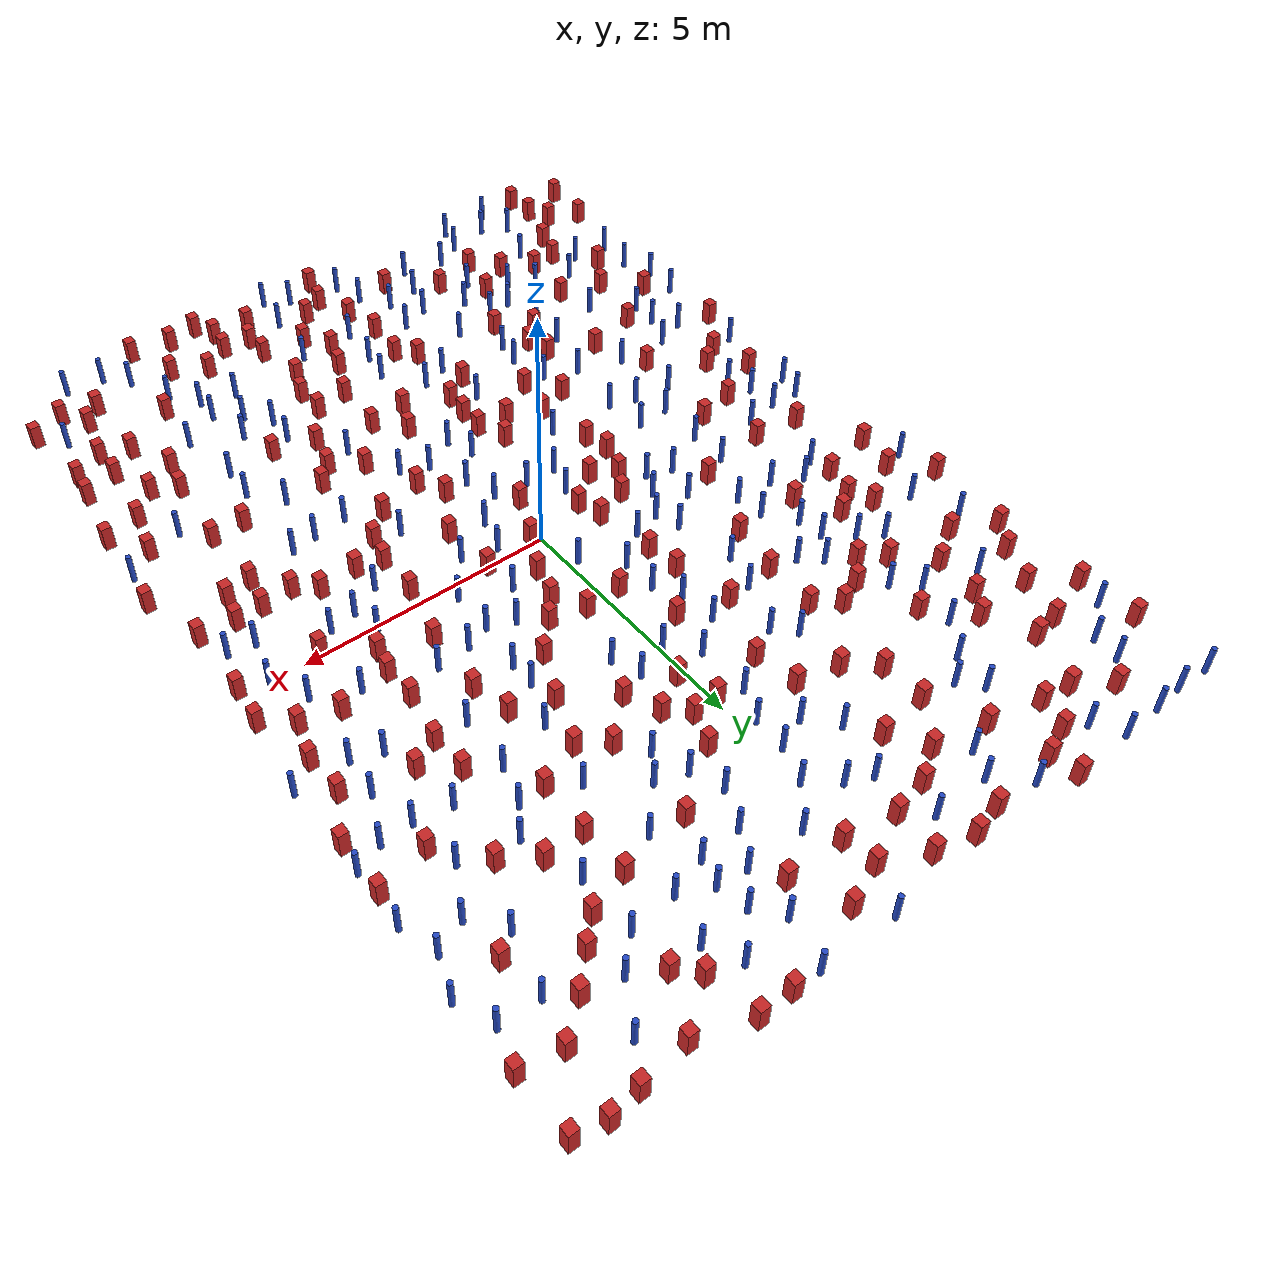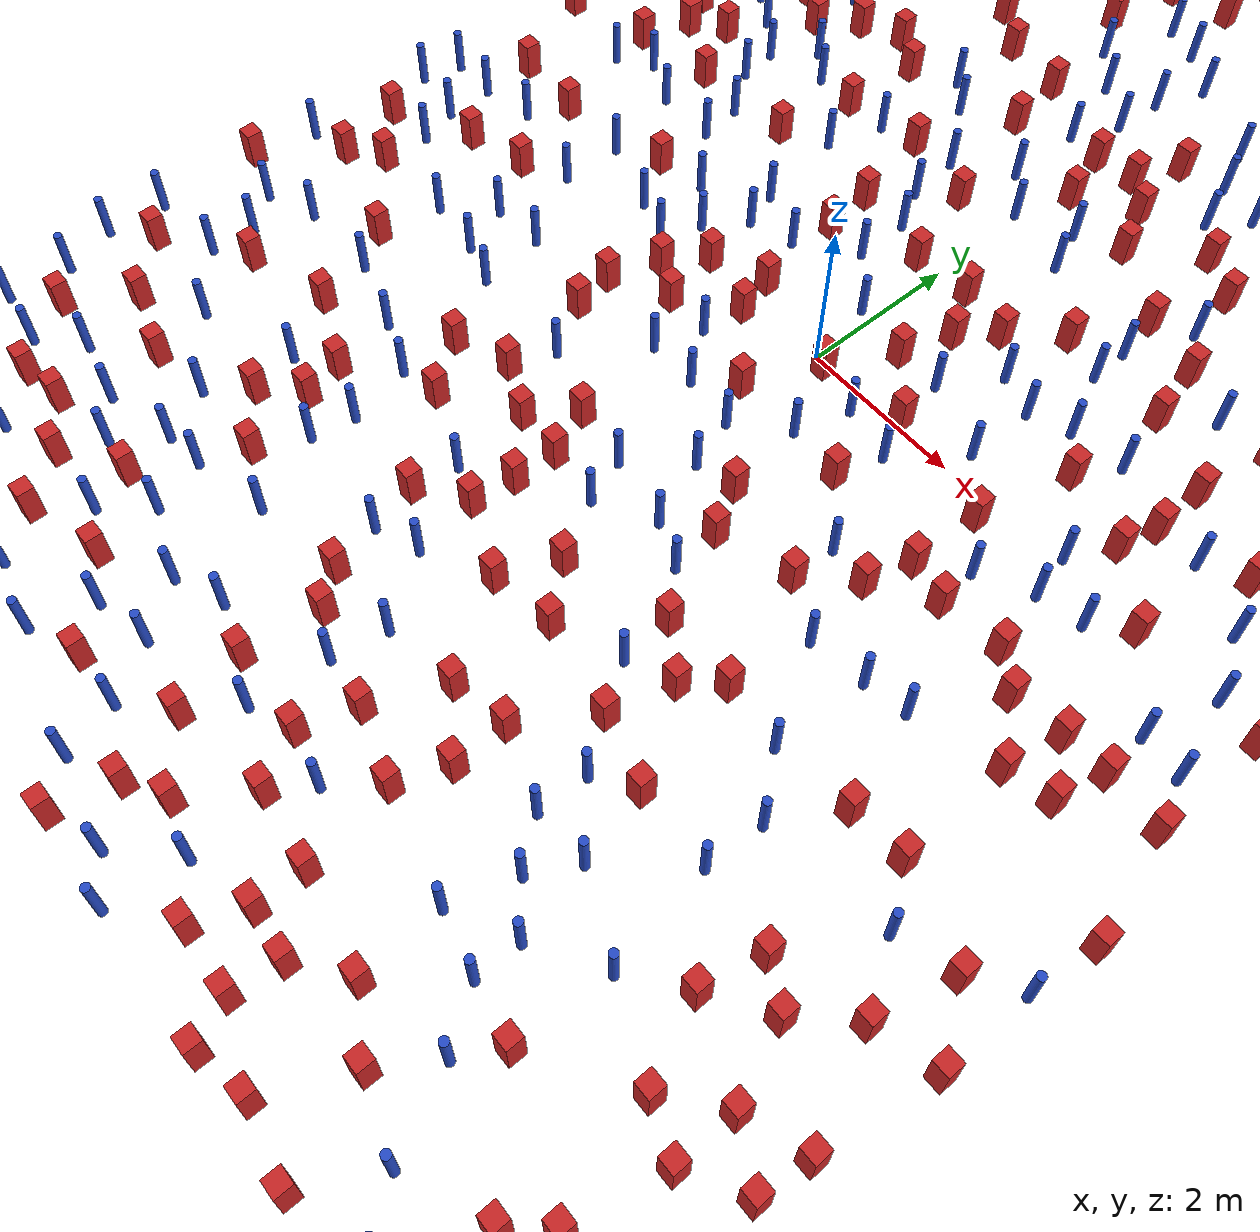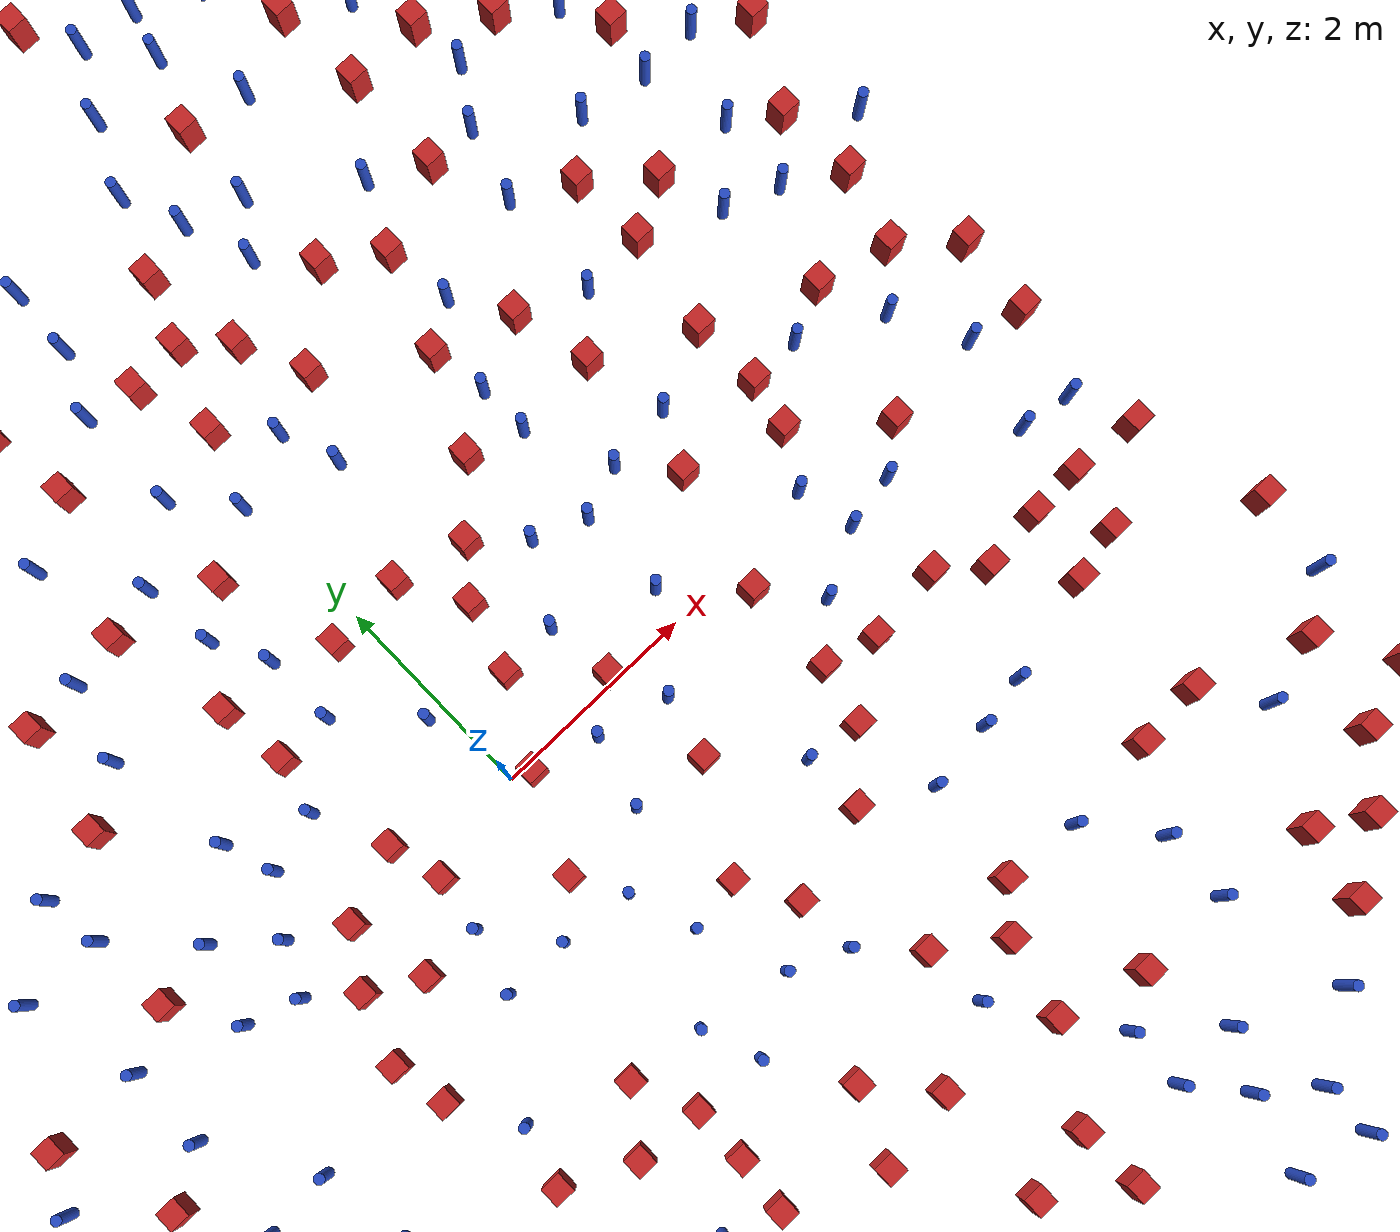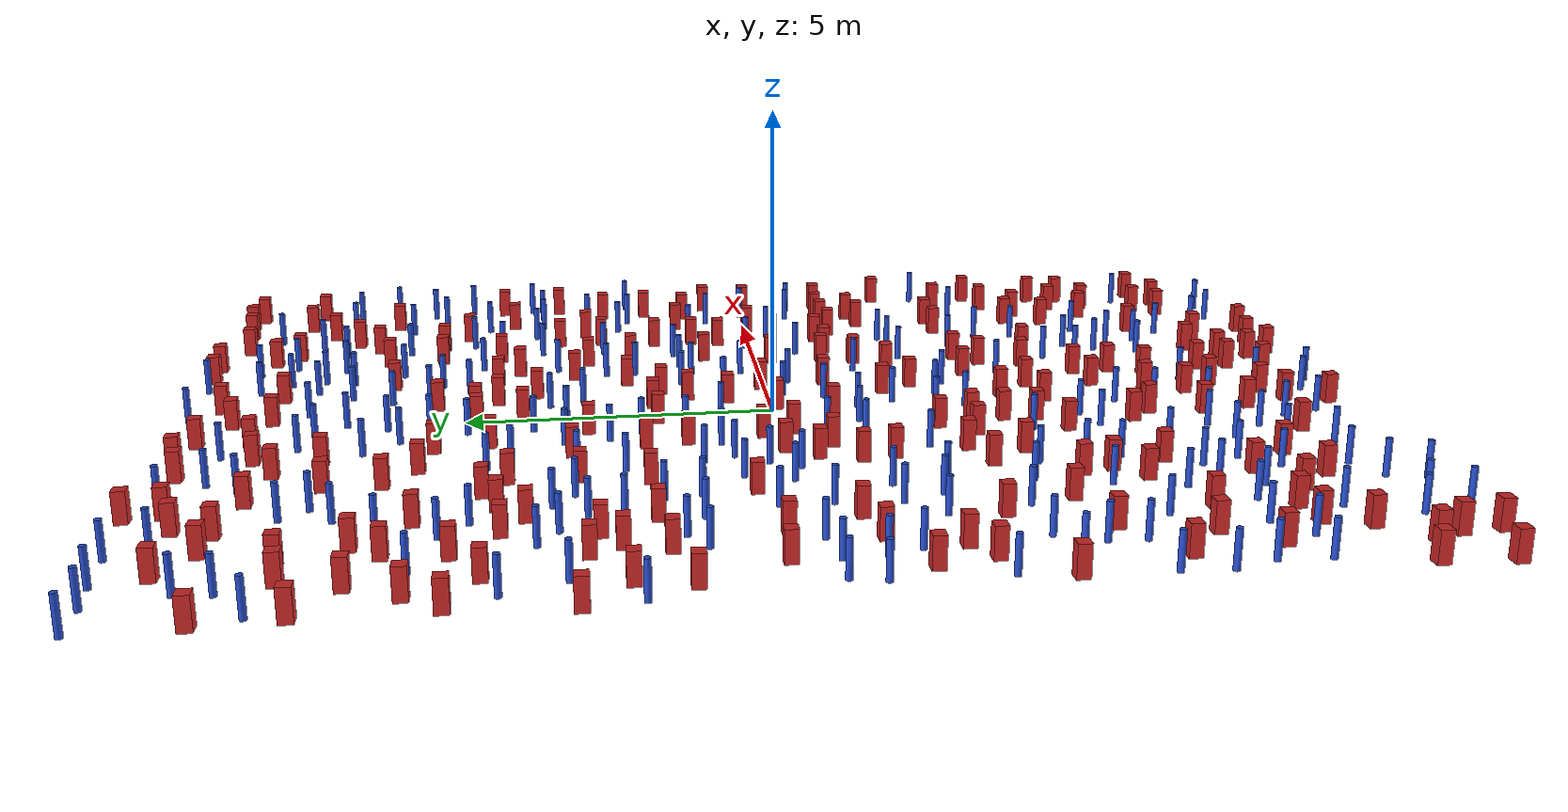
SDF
<sdf version="1.6">
  <model name="dense_24"><model name="square_post_obstacle0">
  <static>true</static>
  <pose frame="">-3.53075418306 9.46736991092 1.91545236811e-07 -7.35059704564e-06 1.12565212e-07 2.39332434364e-05</pose>
  <link name="link">
    <pose frame="">0 0 0.25 0 -0 0</pose>
    <inertial>
      <mass>100</mass>
      <inertia>
        <ixx>0.166667</ixx>
        <ixy>0</ixy>
        <ixz>0</ixz>
        <iyy>0.166667</iyy>
        <iyz>0</iyz>
        <izz>0.166667</izz>
      </inertia>
    </inertial>
    <collision name="collision">
      <geometry>
        <box>
          <size>.2 .2 .5</size>
        </box>
      </geometry>
      <max_contacts>10</max_contacts>
      <surface>
        <contact>
          <ode/>
        </contact>
        <bounce/>
        <friction>
          <torsional>
            <ode/>
          </torsional>
          <ode/>
        </friction>
      </surface>
    </collision>
    <visual name="visual">
      <geometry>
        <box>
          <size>.2 .2 .5</size>
        </box>
      </geometry>
      <material>
        <script>
          <name>Gazebo/Red</name>
          <uri>file://media/materials/scripts/gazebo.material</uri>
        </script>
      </material>
    </visual>
    <self_collide>0</self_collide>
    <kinematic>0</kinematic>
  </link>
</model>
<model name="square_post_obstacle1">
  <static>true</static>
  <pose frame="">-5.25605438137 4.89700262529 1.91545236811e-07 -7.35059704564e-06 1.12565212e-07 2.39332434364e-05</pose>
  <link name="link">
    <pose frame="">0 0 0.25 0 -0 0</pose>
    <inertial>
      <mass>100</mass>
      <inertia>
        <ixx>0.166667</ixx>
        <ixy>0</ixy>
        <ixz>0</ixz>
        <iyy>0.166667</iyy>
        <iyz>0</iyz>
        <izz>0.166667</izz>
      </inertia>
    </inertial>
    <collision name="collision">
      <geometry>
        <box>
          <size>.2 .2 .5</size>
        </box>
      </geometry>
      <max_contacts>10</max_contacts>
      <surface>
        <contact>
          <ode/>
        </contact>
        <bounce/>
        <friction>
          <torsional>
            <ode/>
          </torsional>
          <ode/>
        </friction>
      </surface>
    </collision>
    <visual name="visual">
      <geometry>
        <box>
          <size>.2 .2 .5</size>
        </box>
      </geometry>
      <material>
        <script>
          <name>Gazebo/Red</name>
          <uri>file://media/materials/scripts/gazebo.material</uri>
        </script>
      </material>
    </visual>
    <self_collide>0</self_collide>
    <kinematic>0</kinematic>
  </link>
</model>
<model name="pole_obstacle0">
  <static>true</static>
  <pose frame="">-3.31218589467 3.24684789584 7.38925637345e-09 -8.47170692798e-08 1.24976764939e-08 -1.74513093025e-07</pose>
  <link name="link">
  <pose frame="">0 0 0.3 0 -0 0</pose>
    <inertial>
      <mass>1</mass>
      <inertia>
        <ixx>0.145833</ixx>
        <ixy>0</ixy>
        <ixz>0</ixz>
        <iyy>0.145833</iyy>
        <iyz>0</iyz>
        <izz>0.125</izz>
      </inertia>
    </inertial>
    <collision name="collision">
      <geometry>
        <cylinder>
          <radius>0.05</radius>
          <length>.6</length>
        </cylinder>
      </geometry>
      <max_contacts>10</max_contacts>
      <surface>
        <contact>
          <ode/>
        </contact>
        <bounce/>
        <friction>
          <torsional>
            <ode/>
          </torsional>
          <ode/>
        </friction>
      </surface>
    </collision>
    <visual name="visual">
      <geometry>
        <cylinder>
          <radius>0.05</radius>
          <length>.6</length>
        </cylinder>
      </geometry>
      <material>
        <script>
          <name>Gazebo/Blue</name>
          <uri>file://media/materials/scripts/gazebo.material</uri>
        </script>
      </material>
    </visual>
    <self_collide>0</self_collide>
    <kinematic>0</kinematic>
  </link>
</model>
<model name="square_post_obstacle2">
  <static>true</static>
  <pose frame="">-4.12529514285 3.92472908485 1.91545236811e-07 -7.35059704564e-06 1.12565212e-07 2.39332434364e-05</pose>
  <link name="link">
    <pose frame="">0 0 0.25 0 -0 0</pose>
    <inertial>
      <mass>100</mass>
      <inertia>
        <ixx>0.166667</ixx>
        <ixy>0</ixy>
        <ixz>0</ixz>
        <iyy>0.166667</iyy>
        <iyz>0</iyz>
        <izz>0.166667</izz>
      </inertia>
    </inertial>
    <collision name="collision">
      <geometry>
        <box>
          <size>.2 .2 .5</size>
        </box>
      </geometry>
      <max_contacts>10</max_contacts>
      <surface>
        <contact>
          <ode/>
        </contact>
        <bounce/>
        <friction>
          <torsional>
            <ode/>
          </torsional>
          <ode/>
        </friction>
      </surface>
    </collision>
    <visual name="visual">
      <geometry>
        <box>
          <size>.2 .2 .5</size>
        </box>
      </geometry>
      <material>
        <script>
          <name>Gazebo/Red</name>
          <uri>file://media/materials/scripts/gazebo.material</uri>
        </script>
      </material>
    </visual>
    <self_collide>0</self_collide>
    <kinematic>0</kinematic>
  </link>
</model>
<model name="pole_obstacle1">
  <static>true</static>
  <pose frame="">1.38617735485 6.94967551149 7.38925637345e-09 -8.47170692799e-08 1.24976765033e-08 -1.74513093018e-07</pose>
  <link name="link">
  <pose frame="">0 0 0.3 0 -0 0</pose>
    <inertial>
      <mass>1</mass>
      <inertia>
        <ixx>0.145833</ixx>
        <ixy>0</ixy>
        <ixz>0</ixz>
        <iyy>0.145833</iyy>
        <iyz>0</iyz>
        <izz>0.125</izz>
      </inertia>
    </inertial>
    <collision name="collision">
      <geometry>
        <cylinder>
          <radius>0.05</radius>
          <length>.6</length>
        </cylinder>
      </geometry>
      <max_contacts>10</max_contacts>
      <surface>
        <contact>
          <ode/>
        </contact>
        <bounce/>
        <friction>
          <torsional>
            <ode/>
          </torsional>
          <ode/>
        </friction>
      </surface>
    </collision>
    <visual name="visual">
      <geometry>
        <cylinder>
          <radius>0.05</radius>
          <length>.6</length>
        </cylinder>
      </geometry>
      <material>
        <script>
          <name>Gazebo/Blue</name>
          <uri>file://media/materials/scripts/gazebo.material</uri>
        </script>
      </material>
    </visual>
    <self_collide>0</self_collide>
    <kinematic>0</kinematic>
  </link>
</model>
<model name="square_post_obstacle3">
  <static>true</static>
  <pose frame="">-0.789458256062 -3.69819431889 1.91545236811e-07 -7.35059704564e-06 1.12565212e-07 2.39332434364e-05</pose>
  <link name="link">
    <pose frame="">0 0 0.25 0 -0 0</pose>
    <inertial>
      <mass>100</mass>
      <inertia>
        <ixx>0.166667</ixx>
        <ixy>0</ixy>
        <ixz>0</ixz>
        <iyy>0.166667</iyy>
        <iyz>0</iyz>
        <izz>0.166667</izz>
      </inertia>
    </inertial>
    <collision name="collision">
      <geometry>
        <box>
          <size>.2 .2 .5</size>
        </box>
      </geometry>
      <max_contacts>10</max_contacts>
      <surface>
        <contact>
          <ode/>
        </contact>
        <bounce/>
        <friction>
          <torsional>
            <ode/>
          </torsional>
          <ode/>
        </friction>
      </surface>
    </collision>
    <visual name="visual">
      <geometry>
        <box>
          <size>.2 .2 .5</size>
        </box>
      </geometry>
      <material>
        <script>
          <name>Gazebo/Red</name>
          <uri>file://media/materials/scripts/gazebo.material</uri>
        </script>
      </material>
    </visual>
    <self_collide>0</self_collide>
    <kinematic>0</kinematic>
  </link>
</model>
<model name="pole_obstacle2">
  <static>true</static>
  <pose frame="">2.82099505134 8.70505590829 7.38925637345e-09 -8.47170692793e-08 1.24976764408e-08 -1.74513093041e-07</pose>
  <link name="link">
  <pose frame="">0 0 0.3 0 -0 0</pose>
    <inertial>
      <mass>1</mass>
      <inertia>
        <ixx>0.145833</ixx>
        <ixy>0</ixy>
        <ixz>0</ixz>
        <iyy>0.145833</iyy>
        <iyz>0</iyz>
        <izz>0.125</izz>
      </inertia>
    </inertial>
    <collision name="collision">
      <geometry>
        <cylinder>
          <radius>0.05</radius>
          <length>.6</length>
        </cylinder>
      </geometry>
      <max_contacts>10</max_contacts>
      <surface>
        <contact>
          <ode/>
        </contact>
        <bounce/>
        <friction>
          <torsional>
            <ode/>
          </torsional>
          <ode/>
        </friction>
      </surface>
    </collision>
    <visual name="visual">
      <geometry>
        <cylinder>
          <radius>0.05</radius>
          <length>.6</length>
        </cylinder>
      </geometry>
      <material>
        <script>
          <name>Gazebo/Blue</name>
          <uri>file://media/materials/scripts/gazebo.material</uri>
        </script>
      </material>
    </visual>
    <self_collide>0</self_collide>
    <kinematic>0</kinematic>
  </link>
</model>
<model name="pole_obstacle3">
  <static>true</static>
  <pose frame="">-1.21258136794 8.60759333295 7.38925637345e-09 -8.47170692798e-08 1.24976764881e-08 -1.74513093027e-07</pose>
  <link name="link">
  <pose frame="">0 0 0.3 0 -0 0</pose>
    <inertial>
      <mass>1</mass>
      <inertia>
        <ixx>0.145833</ixx>
        <ixy>0</ixy>
        <ixz>0</ixz>
        <iyy>0.145833</iyy>
        <iyz>0</iyz>
        <izz>0.125</izz>
      </inertia>
    </inertial>
    <collision name="collision">
      <geometry>
        <cylinder>
          <radius>0.05</radius>
          <length>.6</length>
        </cylinder>
      </geometry>
      <max_contacts>10</max_contacts>
      <surface>
        <contact>
          <ode/>
        </contact>
        <bounce/>
        <friction>
          <torsional>
            <ode/>
          </torsional>
          <ode/>
        </friction>
      </surface>
    </collision>
    <visual name="visual">
      <geometry>
        <cylinder>
          <radius>0.05</radius>
          <length>.6</length>
        </cylinder>
      </geometry>
      <material>
        <script>
          <name>Gazebo/Blue</name>
          <uri>file://media/materials/scripts/gazebo.material</uri>
        </script>
      </material>
    </visual>
    <self_collide>0</self_collide>
    <kinematic>0</kinematic>
  </link>
</model>
<model name="square_post_obstacle4">
  <static>true</static>
  <pose frame="">-5.67740192875 -7.65880468433 1.91545236811e-07 -7.35059704564e-06 1.12565212e-07 2.39332434364e-05</pose>
  <link name="link">
    <pose frame="">0 0 0.25 0 -0 0</pose>
    <inertial>
      <mass>100</mass>
      <inertia>
        <ixx>0.166667</ixx>
        <ixy>0</ixy>
        <ixz>0</ixz>
        <iyy>0.166667</iyy>
        <iyz>0</iyz>
        <izz>0.166667</izz>
      </inertia>
    </inertial>
    <collision name="collision">
      <geometry>
        <box>
          <size>.2 .2 .5</size>
        </box>
      </geometry>
      <max_contacts>10</max_contacts>
      <surface>
        <contact>
          <ode/>
        </contact>
        <bounce/>
        <friction>
          <torsional>
            <ode/>
          </torsional>
          <ode/>
        </friction>
      </surface>
    </collision>
    <visual name="visual">
      <geometry>
        <box>
          <size>.2 .2 .5</size>
        </box>
      </geometry>
      <material>
        <script>
          <name>Gazebo/Red</name>
          <uri>file://media/materials/scripts/gazebo.material</uri>
        </script>
      </material>
    </visual>
    <self_collide>0</self_collide>
    <kinematic>0</kinematic>
  </link>
</model>
<model name="square_post_obstacle5">
  <static>true</static>
  <pose frame="">2.1114799383 3.23724180372 1.91545236811e-07 -7.35059704564e-06 1.12565212e-07 2.39332434364e-05</pose>
  <link name="link">
    <pose frame="">0 0 0.25 0 -0 0</pose>
    <inertial>
      <mass>100</mass>
      <inertia>
        <ixx>0.166667</ixx>
        <ixy>0</ixy>
        <ixz>0</ixz>
        <iyy>0.166667</iyy>
        <iyz>0</iyz>
        <izz>0.166667</izz>
      </inertia>
    </inertial>
    <collision name="collision">
      <geometry>
        <box>
          <size>.2 .2 .5</size>
        </box>
      </geometry>
      <max_contacts>10</max_contacts>
      <surface>
        <contact>
          <ode/>
        </contact>
        <bounce/>
        <friction>
          <torsional>
            <ode/>
          </torsional>
          <ode/>
        </friction>
      </surface>
    </collision>
    <visual name="visual">
      <geometry>
        <box>
          <size>.2 .2 .5</size>
        </box>
      </geometry>
      <material>
        <script>
          <name>Gazebo/Red</name>
          <uri>file://media/materials/scripts/gazebo.material</uri>
        </script>
      </material>
    </visual>
    <self_collide>0</self_collide>
    <kinematic>0</kinematic>
  </link>
</model>
<model name="square_post_obstacle6">
  <static>true</static>
  <pose frame="">2.60345973972 9.44994082353 1.91545236811e-07 -7.35059704564e-06 1.12565212e-07 2.39332434364e-05</pose>
  <link name="link">
    <pose frame="">0 0 0.25 0 -0 0</pose>
    <inertial>
      <mass>100</mass>
      <inertia>
        <ixx>0.166667</ixx>
        <ixy>0</ixy>
        <ixz>0</ixz>
        <iyy>0.166667</iyy>
        <iyz>0</iyz>
        <izz>0.166667</izz>
      </inertia>
    </inertial>
    <collision name="collision">
      <geometry>
        <box>
          <size>.2 .2 .5</size>
        </box>
      </geometry>
      <max_contacts>10</max_contacts>
      <surface>
        <contact>
          <ode/>
        </contact>
        <bounce/>
        <friction>
          <torsional>
            <ode/>
          </torsional>
          <ode/>
        </friction>
      </surface>
    </collision>
    <visual name="visual">
      <geometry>
        <box>
          <size>.2 .2 .5</size>
        </box>
      </geometry>
      <material>
        <script>
          <name>Gazebo/Red</name>
          <uri>file://media/materials/scripts/gazebo.material</uri>
        </script>
      </material>
    </visual>
    <self_collide>0</self_collide>
    <kinematic>0</kinematic>
  </link>
</model>
<model name="pole_obstacle4">
  <static>true</static>
  <pose frame="">3.29963674855 -2.52704988164 7.38925637345e-09 -8.47170692798e-08 1.24976764939e-08 -1.74513093025e-07</pose>
  <link name="link">
  <pose frame="">0 0 0.3 0 -0 0</pose>
    <inertial>
      <mass>1</mass>
      <inertia>
        <ixx>0.145833</ixx>
        <ixy>0</ixy>
        <ixz>0</ixz>
        <iyy>0.145833</iyy>
        <iyz>0</iyz>
        <izz>0.125</izz>
      </inertia>
    </inertial>
    <collision name="collision">
      <geometry>
        <cylinder>
          <radius>0.05</radius>
          <length>.6</length>
        </cylinder>
      </geometry>
      <max_contacts>10</max_contacts>
      <surface>
        <contact>
          <ode/>
        </contact>
        <bounce/>
        <friction>
          <torsional>
            <ode/>
          </torsional>
          <ode/>
        </friction>
      </surface>
    </collision>
    <visual name="visual">
      <geometry>
        <cylinder>
          <radius>0.05</radius>
          <length>.6</length>
        </cylinder>
      </geometry>
      <material>
        <script>
          <name>Gazebo/Blue</name>
          <uri>file://media/materials/scripts/gazebo.material</uri>
        </script>
      </material>
    </visual>
    <self_collide>0</self_collide>
    <kinematic>0</kinematic>
  </link>
</model>
<model name="pole_obstacle5">
  <static>true</static>
  <pose frame="">-0.992801236177 7.50081790914 7.38925637345e-09 -8.47170692799e-08 1.2497676509e-08 -1.74513093015e-07</pose>
  <link name="link">
  <pose frame="">0 0 0.3 0 -0 0</pose>
    <inertial>
      <mass>1</mass>
      <inertia>
        <ixx>0.145833</ixx>
        <ixy>0</ixy>
        <ixz>0</ixz>
        <iyy>0.145833</iyy>
        <iyz>0</iyz>
        <izz>0.125</izz>
      </inertia>
    </inertial>
    <collision name="collision">
      <geometry>
        <cylinder>
          <radius>0.05</radius>
          <length>.6</length>
        </cylinder>
      </geometry>
      <max_contacts>10</max_contacts>
      <surface>
        <contact>
          <ode/>
        </contact>
        <bounce/>
        <friction>
          <torsional>
            <ode/>
          </torsional>
          <ode/>
        </friction>
      </surface>
    </collision>
    <visual name="visual">
      <geometry>
        <cylinder>
          <radius>0.05</radius>
          <length>.6</length>
        </cylinder>
      </geometry>
      <material>
        <script>
          <name>Gazebo/Blue</name>
          <uri>file://media/materials/scripts/gazebo.material</uri>
        </script>
      </material>
    </visual>
    <self_collide>0</self_collide>
    <kinematic>0</kinematic>
  </link>
</model>
<model name="square_post_obstacle7">
  <static>true</static>
  <pose frame="">5.32515798996 -2.06593190637 1.91545236811e-07 -7.35059704564e-06 1.12565212e-07 2.39332434364e-05</pose>
  <link name="link">
    <pose frame="">0 0 0.25 0 -0 0</pose>
    <inertial>
      <mass>100</mass>
      <inertia>
        <ixx>0.166667</ixx>
        <ixy>0</ixy>
        <ixz>0</ixz>
        <iyy>0.166667</iyy>
        <iyz>0</iyz>
        <izz>0.166667</izz>
      </inertia>
    </inertial>
    <collision name="collision">
      <geometry>
        <box>
          <size>.2 .2 .5</size>
        </box>
      </geometry>
      <max_contacts>10</max_contacts>
      <surface>
        <contact>
          <ode/>
        </contact>
        <bounce/>
        <friction>
          <torsional>
            <ode/>
          </torsional>
          <ode/>
        </friction>
      </surface>
    </collision>
    <visual name="visual">
      <geometry>
        <box>
          <size>.2 .2 .5</size>
        </box>
      </geometry>
      <material>
        <script>
          <name>Gazebo/Red</name>
          <uri>file://media/materials/scripts/gazebo.material</uri>
        </script>
      </material>
    </visual>
    <self_collide>0</self_collide>
    <kinematic>0</kinematic>
  </link>
</model>
<model name="square_post_obstacle8">
  <static>true</static>
  <pose frame="">1.90882104758 6.30090376429 1.91545236811e-07 -7.35059704564e-06 1.12565212e-07 2.39332434364e-05</pose>
  <link name="link">
    <pose frame="">0 0 0.25 0 -0 0</pose>
    <inertial>
      <mass>100</mass>
      <inertia>
        <ixx>0.166667</ixx>
        <ixy>0</ixy>
        <ixz>0</ixz>
        <iyy>0.166667</iyy>
        <iyz>0</iyz>
        <izz>0.166667</izz>
      </inertia>
    </inertial>
    <collision name="collision">
      <geometry>
        <box>
          <size>.2 .2 .5</size>
        </box>
      </geometry>
      <max_contacts>10</max_contacts>
      <surface>
        <contact>
          <ode/>
        </contact>
        <bounce/>
        <friction>
          <torsional>
            <ode/>
          </torsional>
          <ode/>
        </friction>
      </surface>
    </collision>
    <visual name="visual">
      <geometry>
        <box>
          <size>.2 .2 .5</size>
        </box>
      </geometry>
      <material>
        <script>
          <name>Gazebo/Red</name>
          <uri>file://media/materials/scripts/gazebo.material</uri>
        </script>
      </material>
    </visual>
    <self_collide>0</self_collide>
    <kinematic>0</kinematic>
  </link>
</model>
<model name="pole_obstacle6">
  <static>true</static>
  <pose frame="">5.6374758379 5.68235100578 7.38925637345e-09 -8.47170692796e-08 1.24976764786e-08 -1.74513093032e-07</pose>
  <link name="link">
  <pose frame="">0 0 0.3 0 -0 0</pose>
    <inertial>
      <mass>1</mass>
      <inertia>
        <ixx>0.145833</ixx>
        <ixy>0</ixy>
        <ixz>0</ixz>
        <iyy>0.145833</iyy>
        <iyz>0</iyz>
        <izz>0.125</izz>
      </inertia>
    </inertial>
    <collision name="collision">
      <geometry>
        <cylinder>
          <radius>0.05</radius>
          <length>.6</length>
        </cylinder>
      </geometry>
      <max_contacts>10</max_contacts>
      <surface>
        <contact>
          <ode/>
        </contact>
        <bounce/>
        <friction>
          <torsional>
            <ode/>
          </torsional>
          <ode/>
        </friction>
      </surface>
    </collision>
    <visual name="visual">
      <geometry>
        <cylinder>
          <radius>0.05</radius>
          <length>.6</length>
        </cylinder>
      </geometry>
      <material>
        <script>
          <name>Gazebo/Blue</name>
          <uri>file://media/materials/scripts/gazebo.material</uri>
        </script>
      </material>
    </visual>
    <self_collide>0</self_collide>
    <kinematic>0</kinematic>
  </link>
</model>
<model name="pole_obstacle7">
  <static>true</static>
  <pose frame="">-5.22169933292 -0.105891624852 7.38925637345e-09 -8.47170692799e-08 1.24976765039e-08 -1.74513093019e-07</pose>
  <link name="link">
  <pose frame="">0 0 0.3 0 -0 0</pose>
    <inertial>
      <mass>1</mass>
      <inertia>
        <ixx>0.145833</ixx>
        <ixy>0</ixy>
        <ixz>0</ixz>
        <iyy>0.145833</iyy>
        <iyz>0</iyz>
        <izz>0.125</izz>
      </inertia>
    </inertial>
    <collision name="collision">
      <geometry>
        <cylinder>
          <radius>0.05</radius>
          <length>.6</length>
        </cylinder>
      </geometry>
      <max_contacts>10</max_contacts>
      <surface>
        <contact>
          <ode/>
        </contact>
        <bounce/>
        <friction>
          <torsional>
            <ode/>
          </torsional>
          <ode/>
        </friction>
      </surface>
    </collision>
    <visual name="visual">
      <geometry>
        <cylinder>
          <radius>0.05</radius>
          <length>.6</length>
        </cylinder>
      </geometry>
      <material>
        <script>
          <name>Gazebo/Blue</name>
          <uri>file://media/materials/scripts/gazebo.material</uri>
        </script>
      </material>
    </visual>
    <self_collide>0</self_collide>
    <kinematic>0</kinematic>
  </link>
</model>
<model name="square_post_obstacle9">
  <static>true</static>
  <pose frame="">3.91278412913 -1.24302501316 1.91545236811e-07 -7.35059704564e-06 1.12565212e-07 2.39332434364e-05</pose>
  <link name="link">
    <pose frame="">0 0 0.25 0 -0 0</pose>
    <inertial>
      <mass>100</mass>
      <inertia>
        <ixx>0.166667</ixx>
        <ixy>0</ixy>
        <ixz>0</ixz>
        <iyy>0.166667</iyy>
        <iyz>0</iyz>
        <izz>0.166667</izz>
      </inertia>
    </inertial>
    <collision name="collision">
      <geometry>
        <box>
          <size>.2 .2 .5</size>
        </box>
      </geometry>
      <max_contacts>10</max_contacts>
      <surface>
        <contact>
          <ode/>
        </contact>
        <bounce/>
        <friction>
          <torsional>
            <ode/>
          </torsional>
          <ode/>
        </friction>
      </surface>
    </collision>
    <visual name="visual">
      <geometry>
        <box>
          <size>.2 .2 .5</size>
        </box>
      </geometry>
      <material>
        <script>
          <name>Gazebo/Red</name>
          <uri>file://media/materials/scripts/gazebo.material</uri>
        </script>
      </material>
    </visual>
    <self_collide>0</self_collide>
    <kinematic>0</kinematic>
  </link>
</model>
<model name="square_post_obstacle10">
  <static>true</static>
  <pose frame="">0.0550783046898 -8.40257800408 1.91545236811e-07 -7.35059704564e-06 1.12565212e-07 2.39332434364e-05</pose>
  <link name="link">
    <pose frame="">0 0 0.25 0 -0 0</pose>
    <inertial>
      <mass>100</mass>
      <inertia>
        <ixx>0.166667</ixx>
        <ixy>0</ixy>
        <ixz>0</ixz>
        <iyy>0.166667</iyy>
        <iyz>0</iyz>
        <izz>0.166667</izz>
      </inertia>
    </inertial>
    <collision name="collision">
      <geometry>
        <box>
          <size>.2 .2 .5</size>
        </box>
      </geometry>
      <max_contacts>10</max_contacts>
      <surface>
        <contact>
          <ode/>
        </contact>
        <bounce/>
        <friction>
          <torsional>
            <ode/>
          </torsional>
          <ode/>
        </friction>
      </surface>
    </collision>
    <visual name="visual">
      <geometry>
        <box>
          <size>.2 .2 .5</size>
        </box>
      </geometry>
      <material>
        <script>
          <name>Gazebo/Red</name>
          <uri>file://media/materials/scripts/gazebo.material</uri>
        </script>
      </material>
    </visual>
    <self_collide>0</self_collide>
    <kinematic>0</kinematic>
  </link>
</model>
<model name="square_post_obstacle11">
  <static>true</static>
  <pose frame="">1.56655398483 -3.56114634323 1.91545236811e-07 -7.35059704564e-06 1.12565212e-07 2.39332434364e-05</pose>
  <link name="link">
    <pose frame="">0 0 0.25 0 -0 0</pose>
    <inertial>
      <mass>100</mass>
      <inertia>
        <ixx>0.166667</ixx>
        <ixy>0</ixy>
        <ixz>0</ixz>
        <iyy>0.166667</iyy>
        <iyz>0</iyz>
        <izz>0.166667</izz>
      </inertia>
    </inertial>
    <collision name="collision">
      <geometry>
        <box>
          <size>.2 .2 .5</size>
        </box>
      </geometry>
      <max_contacts>10</max_contacts>
      <surface>
        <contact>
          <ode/>
        </contact>
        <bounce/>
        <friction>
          <torsional>
            <ode/>
          </torsional>
          <ode/>
        </friction>
      </surface>
    </collision>
    <visual name="visual">
      <geometry>
        <box>
          <size>.2 .2 .5</size>
        </box>
      </geometry>
      <material>
        <script>
          <name>Gazebo/Red</name>
          <uri>file://media/materials/scripts/gazebo.material</uri>
        </script>
      </material>
    </visual>
    <self_collide>0</self_collide>
    <kinematic>0</kinematic>
  </link>
</model>
<model name="square_post_obstacle12">
  <static>true</static>
  <pose frame="">0.781799811374 -1.9727818271 1.91545236811e-07 -7.35059704564e-06 1.12565212e-07 2.39332434364e-05</pose>
  <link name="link">
    <pose frame="">0 0 0.25 0 -0 0</pose>
    <inertial>
      <mass>100</mass>
      <inertia>
        <ixx>0.166667</ixx>
        <ixy>0</ixy>
        <ixz>0</ixz>
        <iyy>0.166667</iyy>
        <iyz>0</iyz>
        <izz>0.166667</izz>
      </inertia>
    </inertial>
    <collision name="collision">
      <geometry>
        <box>
          <size>.2 .2 .5</size>
        </box>
      </geometry>
      <max_contacts>10</max_contacts>
      <surface>
        <contact>
          <ode/>
        </contact>
        <bounce/>
        <friction>
          <torsional>
            <ode/>
          </torsional>
          <ode/>
        </friction>
      </surface>
    </collision>
    <visual name="visual">
      <geometry>
        <box>
          <size>.2 .2 .5</size>
        </box>
      </geometry>
      <material>
        <script>
          <name>Gazebo/Red</name>
          <uri>file://media/materials/scripts/gazebo.material</uri>
        </script>
      </material>
    </visual>
    <self_collide>0</self_collide>
    <kinematic>0</kinematic>
  </link>
</model>
<model name="square_post_obstacle13">
  <static>true</static>
  <pose frame="">-1.41700734164 -3.11351786145 1.91545236811e-07 -7.35059704564e-06 1.12565212e-07 2.39332434364e-05</pose>
  <link name="link">
    <pose frame="">0 0 0.25 0 -0 0</pose>
    <inertial>
      <mass>100</mass>
      <inertia>
        <ixx>0.166667</ixx>
        <ixy>0</ixy>
        <ixz>0</ixz>
        <iyy>0.166667</iyy>
        <iyz>0</iyz>
        <izz>0.166667</izz>
      </inertia>
    </inertial>
    <collision name="collision">
      <geometry>
        <box>
          <size>.2 .2 .5</size>
        </box>
      </geometry>
      <max_contacts>10</max_contacts>
      <surface>
        <contact>
          <ode/>
        </contact>
        <bounce/>
        <friction>
          <torsional>
            <ode/>
          </torsional>
          <ode/>
        </friction>
      </surface>
    </collision>
    <visual name="visual">
      <geometry>
        <box>
          <size>.2 .2 .5</size>
        </box>
      </geometry>
      <material>
        <script>
          <name>Gazebo/Red</name>
          <uri>file://media/materials/scripts/gazebo.material</uri>
        </script>
      </material>
    </visual>
    <self_collide>0</self_collide>
    <kinematic>0</kinematic>
  </link>
</model>
<model name="pole_obstacle8">
  <static>true</static>
  <pose frame="">-4.06872563296 -6.78109198846 7.38925637345e-09 -8.47170692796e-08 1.24976764786e-08 -1.74513093032e-07</pose>
  <link name="link">
  <pose frame="">0 0 0.3 0 -0 0</pose>
    <inertial>
      <mass>1</mass>
      <inertia>
        <ixx>0.145833</ixx>
        <ixy>0</ixy>
        <ixz>0</ixz>
        <iyy>0.145833</iyy>
        <iyz>0</iyz>
        <izz>0.125</izz>
      </inertia>
    </inertial>
    <collision name="collision">
      <geometry>
        <cylinder>
          <radius>0.05</radius>
          <length>.6</length>
        </cylinder>
      </geometry>
      <max_contacts>10</max_contacts>
      <surface>
        <contact>
          <ode/>
        </contact>
        <bounce/>
        <friction>
          <torsional>
            <ode/>
          </torsional>
          <ode/>
        </friction>
      </surface>
    </collision>
    <visual name="visual">
      <geometry>
        <cylinder>
          <radius>0.05</radius>
          <length>.6</length>
        </cylinder>
      </geometry>
      <material>
        <script>
          <name>Gazebo/Blue</name>
          <uri>file://media/materials/scripts/gazebo.material</uri>
        </script>
      </material>
    </visual>
    <self_collide>0</self_collide>
    <kinematic>0</kinematic>
  </link>
</model>
<model name="square_post_obstacle14">
  <static>true</static>
  <pose frame="">6.14993961561 -1.53402861949 1.91545236811e-07 -7.35059704564e-06 1.12565212e-07 2.39332434364e-05</pose>
  <link name="link">
    <pose frame="">0 0 0.25 0 -0 0</pose>
    <inertial>
      <mass>100</mass>
      <inertia>
        <ixx>0.166667</ixx>
        <ixy>0</ixy>
        <ixz>0</ixz>
        <iyy>0.166667</iyy>
        <iyz>0</iyz>
        <izz>0.166667</izz>
      </inertia>
    </inertial>
    <collision name="collision">
      <geometry>
        <box>
          <size>.2 .2 .5</size>
        </box>
      </geometry>
      <max_contacts>10</max_contacts>
      <surface>
        <contact>
          <ode/>
        </contact>
        <bounce/>
        <friction>
          <torsional>
            <ode/>
          </torsional>
          <ode/>
        </friction>
      </surface>
    </collision>
    <visual name="visual">
      <geometry>
        <box>
          <size>.2 .2 .5</size>
        </box>
      </geometry>
      <material>
        <script>
          <name>Gazebo/Red</name>
          <uri>file://media/materials/scripts/gazebo.material</uri>
        </script>
      </material>
    </visual>
    <self_collide>0</self_collide>
    <kinematic>0</kinematic>
  </link>
</model>
<model name="square_post_obstacle15">
  <static>true</static>
  <pose frame="">5.02085969405 7.69715390304 1.91545236811e-07 -7.35059704564e-06 1.12565212e-07 2.39332434364e-05</pose>
  <link name="link">
    <pose frame="">0 0 0.25 0 -0 0</pose>
    <inertial>
      <mass>100</mass>
      <inertia>
        <ixx>0.166667</ixx>
        <ixy>0</ixy>
        <ixz>0</ixz>
        <iyy>0.166667</iyy>
        <iyz>0</iyz>
        <izz>0.166667</izz>
      </inertia>
    </inertial>
    <collision name="collision">
      <geometry>
        <box>
          <size>.2 .2 .5</size>
        </box>
      </geometry>
      <max_contacts>10</max_contacts>
      <surface>
        <contact>
          <ode/>
        </contact>
        <bounce/>
        <friction>
          <torsional>
            <ode/>
          </torsional>
          <ode/>
        </friction>
      </surface>
    </collision>
    <visual name="visual">
      <geometry>
        <box>
          <size>.2 .2 .5</size>
        </box>
      </geometry>
      <material>
        <script>
          <name>Gazebo/Red</name>
          <uri>file://media/materials/scripts/gazebo.material</uri>
        </script>
      </material>
    </visual>
    <self_collide>0</self_collide>
    <kinematic>0</kinematic>
  </link>
</model>
<model name="square_post_obstacle16">
  <static>true</static>
  <pose frame="">1.46860966695 -6.16280772476 1.91545236811e-07 -7.35059704564e-06 1.12565212e-07 2.39332434364e-05</pose>
  <link name="link">
    <pose frame="">0 0 0.25 0 -0 0</pose>
    <inertial>
      <mass>100</mass>
      <inertia>
        <ixx>0.166667</ixx>
        <ixy>0</ixy>
        <ixz>0</ixz>
        <iyy>0.166667</iyy>
        <iyz>0</iyz>
        <izz>0.166667</izz>
      </inertia>
    </inertial>
    <collision name="collision">
      <geometry>
        <box>
          <size>.2 .2 .5</size>
        </box>
      </geometry>
      <max_contacts>10</max_contacts>
      <surface>
        <contact>
          <ode/>
        </contact>
        <bounce/>
        <friction>
          <torsional>
            <ode/>
          </torsional>
          <ode/>
        </friction>
      </surface>
    </collision>
    <visual name="visual">
      <geometry>
        <box>
          <size>.2 .2 .5</size>
        </box>
      </geometry>
      <material>
        <script>
          <name>Gazebo/Red</name>
          <uri>file://media/materials/scripts/gazebo.material</uri>
        </script>
      </material>
    </visual>
    <self_collide>0</self_collide>
    <kinematic>0</kinematic>
  </link>
</model>
<model name="pole_obstacle9">
  <static>true</static>
  <pose frame="">-2.39047537825 2.48837726105 7.38925637345e-09 -8.47170692798e-08 1.24976764939e-08 -1.74513093025e-07</pose>
  <link name="link">
  <pose frame="">0 0 0.3 0 -0 0</pose>
    <inertial>
      <mass>1</mass>
      <inertia>
        <ixx>0.145833</ixx>
        <ixy>0</ixy>
        <ixz>0</ixz>
        <iyy>0.145833</iyy>
        <iyz>0</iyz>
        <izz>0.125</izz>
      </inertia>
    </inertial>
    <collision name="collision">
      <geometry>
        <cylinder>
          <radius>0.05</radius>
          <length>.6</length>
        </cylinder>
      </geometry>
      <max_contacts>10</max_contacts>
      <surface>
        <contact>
          <ode/>
        </contact>
        <bounce/>
        <friction>
          <torsional>
            <ode/>
          </torsional>
          <ode/>
        </friction>
      </surface>
    </collision>
    <visual name="visual">
      <geometry>
        <cylinder>
          <radius>0.05</radius>
          <length>.6</length>
        </cylinder>
      </geometry>
      <material>
        <script>
          <name>Gazebo/Blue</name>
          <uri>file://media/materials/scripts/gazebo.material</uri>
        </script>
      </material>
    </visual>
    <self_collide>0</self_collide>
    <kinematic>0</kinematic>
  </link>
</model>
<model name="square_post_obstacle17">
  <static>true</static>
  <pose frame="">-6.07549606696 6.16473758936 1.91545236811e-07 -7.35059704564e-06 1.12565212e-07 2.39332434364e-05</pose>
  <link name="link">
    <pose frame="">0 0 0.25 0 -0 0</pose>
    <inertial>
      <mass>100</mass>
      <inertia>
        <ixx>0.166667</ixx>
        <ixy>0</ixy>
        <ixz>0</ixz>
        <iyy>0.166667</iyy>
        <iyz>0</iyz>
        <izz>0.166667</izz>
      </inertia>
    </inertial>
    <collision name="collision">
      <geometry>
        <box>
          <size>.2 .2 .5</size>
        </box>
      </geometry>
      <max_contacts>10</max_contacts>
      <surface>
        <contact>
          <ode/>
        </contact>
        <bounce/>
        <friction>
          <torsional>
            <ode/>
          </torsional>
          <ode/>
        </friction>
      </surface>
    </collision>
    <visual name="visual">
      <geometry>
        <box>
          <size>.2 .2 .5</size>
        </box>
      </geometry>
      <material>
        <script>
          <name>Gazebo/Red</name>
          <uri>file://media/materials/scripts/gazebo.material</uri>
        </script>
      </material>
    </visual>
    <self_collide>0</self_collide>
    <kinematic>0</kinematic>
  </link>
</model>
<model name="square_post_obstacle18">
  <static>true</static>
  <pose frame="">-3.52603695999 -6.82466076162 1.91545236811e-07 -7.35059704564e-06 1.12565212e-07 2.39332434364e-05</pose>
  <link name="link">
    <pose frame="">0 0 0.25 0 -0 0</pose>
    <inertial>
      <mass>100</mass>
      <inertia>
        <ixx>0.166667</ixx>
        <ixy>0</ixy>
        <ixz>0</ixz>
        <iyy>0.166667</iyy>
        <iyz>0</iyz>
        <izz>0.166667</izz>
      </inertia>
    </inertial>
    <collision name="collision">
      <geometry>
        <box>
          <size>.2 .2 .5</size>
        </box>
      </geometry>
      <max_contacts>10</max_contacts>
      <surface>
        <contact>
          <ode/>
        </contact>
        <bounce/>
        <friction>
          <torsional>
            <ode/>
          </torsional>
          <ode/>
        </friction>
      </surface>
    </collision>
    <visual name="visual">
      <geometry>
        <box>
          <size>.2 .2 .5</size>
        </box>
      </geometry>
      <material>
        <script>
          <name>Gazebo/Red</name>
          <uri>file://media/materials/scripts/gazebo.material</uri>
        </script>
      </material>
    </visual>
    <self_collide>0</self_collide>
    <kinematic>0</kinematic>
  </link>
</model>
<model name="pole_obstacle10">
  <static>true</static>
  <pose frame="">-2.24000977725 -5.9753968946 7.38925637345e-09 -8.47170692798e-08 1.24976765033e-08 -1.74513093019e-07</pose>
  <link name="link">
  <pose frame="">0 0 0.3 0 -0 0</pose>
    <inertial>
      <mass>1</mass>
      <inertia>
        <ixx>0.145833</ixx>
        <ixy>0</ixy>
        <ixz>0</ixz>
        <iyy>0.145833</iyy>
        <iyz>0</iyz>
        <izz>0.125</izz>
      </inertia>
    </inertial>
    <collision name="collision">
      <geometry>
        <cylinder>
          <radius>0.05</radius>
          <length>.6</length>
        </cylinder>
      </geometry>
      <max_contacts>10</max_contacts>
      <surface>
        <contact>
          <ode/>
        </contact>
        <bounce/>
        <friction>
          <torsional>
            <ode/>
          </torsional>
          <ode/>
        </friction>
      </surface>
    </collision>
    <visual name="visual">
      <geometry>
        <cylinder>
          <radius>0.05</radius>
          <length>.6</length>
        </cylinder>
      </geometry>
      <material>
        <script>
          <name>Gazebo/Blue</name>
          <uri>file://media/materials/scripts/gazebo.material</uri>
        </script>
      </material>
    </visual>
    <self_collide>0</self_collide>
    <kinematic>0</kinematic>
  </link>
</model>
<model name="square_post_obstacle19">
  <static>true</static>
  <pose frame="">2.57718396046 -8.00460723232 1.91545236811e-07 -7.35059704564e-06 1.12565212e-07 2.39332434364e-05</pose>
  <link name="link">
    <pose frame="">0 0 0.25 0 -0 0</pose>
    <inertial>
      <mass>100</mass>
      <inertia>
        <ixx>0.166667</ixx>
        <ixy>0</ixy>
        <ixz>0</ixz>
        <iyy>0.166667</iyy>
        <iyz>0</iyz>
        <izz>0.166667</izz>
      </inertia>
    </inertial>
    <collision name="collision">
      <geometry>
        <box>
          <size>.2 .2 .5</size>
        </box>
      </geometry>
      <max_contacts>10</max_contacts>
      <surface>
        <contact>
          <ode/>
        </contact>
        <bounce/>
        <friction>
          <torsional>
            <ode/>
          </torsional>
          <ode/>
        </friction>
      </surface>
    </collision>
    <visual name="visual">
      <geometry>
        <box>
          <size>.2 .2 .5</size>
        </box>
      </geometry>
      <material>
        <script>
          <name>Gazebo/Red</name>
          <uri>file://media/materials/scripts/gazebo.material</uri>
        </script>
      </material>
    </visual>
    <self_collide>0</self_collide>
    <kinematic>0</kinematic>
  </link>
</model>
<model name="pole_obstacle11">
  <static>true</static>
  <pose frame="">1.52577611234 5.01605634758 7.38925637345e-09 -8.47170692799e-08 1.24976765033e-08 -1.74513093018e-07</pose>
  <link name="link">
  <pose frame="">0 0 0.3 0 -0 0</pose>
    <inertial>
      <mass>1</mass>
      <inertia>
        <ixx>0.145833</ixx>
        <ixy>0</ixy>
        <ixz>0</ixz>
        <iyy>0.145833</iyy>
        <iyz>0</iyz>
        <izz>0.125</izz>
      </inertia>
    </inertial>
    <collision name="collision">
      <geometry>
        <cylinder>
          <radius>0.05</radius>
          <length>.6</length>
        </cylinder>
      </geometry>
      <max_contacts>10</max_contacts>
      <surface>
        <contact>
          <ode/>
        </contact>
        <bounce/>
        <friction>
          <torsional>
            <ode/>
          </torsional>
          <ode/>
        </friction>
      </surface>
    </collision>
    <visual name="visual">
      <geometry>
        <cylinder>
          <radius>0.05</radius>
          <length>.6</length>
        </cylinder>
      </geometry>
      <material>
        <script>
          <name>Gazebo/Blue</name>
          <uri>file://media/materials/scripts/gazebo.material</uri>
        </script>
      </material>
    </visual>
    <self_collide>0</self_collide>
    <kinematic>0</kinematic>
  </link>
</model>
<model name="square_post_obstacle20">
  <static>true</static>
  <pose frame="">6.37773901293 -4.66234504108 1.91545236811e-07 -7.35059704564e-06 1.12565212e-07 2.39332434364e-05</pose>
  <link name="link">
    <pose frame="">0 0 0.25 0 -0 0</pose>
    <inertial>
      <mass>100</mass>
      <inertia>
        <ixx>0.166667</ixx>
        <ixy>0</ixy>
        <ixz>0</ixz>
        <iyy>0.166667</iyy>
        <iyz>0</iyz>
        <izz>0.166667</izz>
      </inertia>
    </inertial>
    <collision name="collision">
      <geometry>
        <box>
          <size>.2 .2 .5</size>
        </box>
      </geometry>
      <max_contacts>10</max_contacts>
      <surface>
        <contact>
          <ode/>
        </contact>
        <bounce/>
        <friction>
          <torsional>
            <ode/>
          </torsional>
          <ode/>
        </friction>
      </surface>
    </collision>
    <visual name="visual">
      <geometry>
        <box>
          <size>.2 .2 .5</size>
        </box>
      </geometry>
      <material>
        <script>
          <name>Gazebo/Red</name>
          <uri>file://media/materials/scripts/gazebo.material</uri>
        </script>
      </material>
    </visual>
    <self_collide>0</self_collide>
    <kinematic>0</kinematic>
  </link>
</model>
<model name="pole_obstacle12">
  <static>true</static>
  <pose frame="">-6.2879917336 9.29565912501 7.38925637345e-09 -8.471706928e-08 1.24976765081e-08 -1.74513093015e-07</pose>
  <link name="link">
  <pose frame="">0 0 0.3 0 -0 0</pose>
    <inertial>
      <mass>1</mass>
      <inertia>
        <ixx>0.145833</ixx>
        <ixy>0</ixy>
        <ixz>0</ixz>
        <iyy>0.145833</iyy>
        <iyz>0</iyz>
        <izz>0.125</izz>
      </inertia>
    </inertial>
    <collision name="collision">
      <geometry>
        <cylinder>
          <radius>0.05</radius>
          <length>.6</length>
        </cylinder>
      </geometry>
      <max_contacts>10</max_contacts>
      <surface>
        <contact>
          <ode/>
        </contact>
        <bounce/>
        <friction>
          <torsional>
            <ode/>
          </torsional>
          <ode/>
        </friction>
      </surface>
    </collision>
    <visual name="visual">
      <geometry>
        <cylinder>
          <radius>0.05</radius>
          <length>.6</length>
        </cylinder>
      </geometry>
      <material>
        <script>
          <name>Gazebo/Blue</name>
          <uri>file://media/materials/scripts/gazebo.material</uri>
        </script>
      </material>
    </visual>
    <self_collide>0</self_collide>
    <kinematic>0</kinematic>
  </link>
</model>
<model name="square_post_obstacle21">
  <static>true</static>
  <pose frame="">-1.63938460143 7.04076987907 1.91545236811e-07 -7.35059704564e-06 1.12565212e-07 2.39332434364e-05</pose>
  <link name="link">
    <pose frame="">0 0 0.25 0 -0 0</pose>
    <inertial>
      <mass>100</mass>
      <inertia>
        <ixx>0.166667</ixx>
        <ixy>0</ixy>
        <ixz>0</ixz>
        <iyy>0.166667</iyy>
        <iyz>0</iyz>
        <izz>0.166667</izz>
      </inertia>
    </inertial>
    <collision name="collision">
      <geometry>
        <box>
          <size>.2 .2 .5</size>
        </box>
      </geometry>
      <max_contacts>10</max_contacts>
      <surface>
        <contact>
          <ode/>
        </contact>
        <bounce/>
        <friction>
          <torsional>
            <ode/>
          </torsional>
          <ode/>
        </friction>
      </surface>
    </collision>
    <visual name="visual">
      <geometry>
        <box>
          <size>.2 .2 .5</size>
        </box>
      </geometry>
      <material>
        <script>
          <name>Gazebo/Red</name>
          <uri>file://media/materials/scripts/gazebo.material</uri>
        </script>
      </material>
    </visual>
    <self_collide>0</self_collide>
    <kinematic>0</kinematic>
  </link>
</model>
<model name="pole_obstacle13">
  <static>true</static>
  <pose frame="">3.23759024392 1.45108022356 7.38925637345e-09 -8.471706928e-08 1.24976765152e-08 -1.74513093012e-07</pose>
  <link name="link">
  <pose frame="">0 0 0.3 0 -0 0</pose>
    <inertial>
      <mass>1</mass>
      <inertia>
        <ixx>0.145833</ixx>
        <ixy>0</ixy>
        <ixz>0</ixz>
        <iyy>0.145833</iyy>
        <iyz>0</iyz>
        <izz>0.125</izz>
      </inertia>
    </inertial>
    <collision name="collision">
      <geometry>
        <cylinder>
          <radius>0.05</radius>
          <length>.6</length>
        </cylinder>
      </geometry>
      <max_contacts>10</max_contacts>
      <surface>
        <contact>
          <ode/>
        </contact>
        <bounce/>
        <friction>
          <torsional>
            <ode/>
          </torsional>
          <ode/>
        </friction>
      </surface>
    </collision>
    <visual name="visual">
      <geometry>
        <cylinder>
          <radius>0.05</radius>
          <length>.6</length>
        </cylinder>
      </geometry>
      <material>
        <script>
          <name>Gazebo/Blue</name>
          <uri>file://media/materials/scripts/gazebo.material</uri>
        </script>
      </material>
    </visual>
    <self_collide>0</self_collide>
    <kinematic>0</kinematic>
  </link>
</model>
<model name="square_post_obstacle22">
  <static>true</static>
  <pose frame="">-2.26513360312 -3.66411039901 1.91545236811e-07 -7.35059704564e-06 1.12565212e-07 2.39332434364e-05</pose>
  <link name="link">
    <pose frame="">0 0 0.25 0 -0 0</pose>
    <inertial>
      <mass>100</mass>
      <inertia>
        <ixx>0.166667</ixx>
        <ixy>0</ixy>
        <ixz>0</ixz>
        <iyy>0.166667</iyy>
        <iyz>0</iyz>
        <izz>0.166667</izz>
      </inertia>
    </inertial>
    <collision name="collision">
      <geometry>
        <box>
          <size>.2 .2 .5</size>
        </box>
      </geometry>
      <max_contacts>10</max_contacts>
      <surface>
        <contact>
          <ode/>
        </contact>
        <bounce/>
        <friction>
          <torsional>
            <ode/>
          </torsional>
          <ode/>
        </friction>
      </surface>
    </collision>
    <visual name="visual">
      <geometry>
        <box>
          <size>.2 .2 .5</size>
        </box>
      </geometry>
      <material>
        <script>
          <name>Gazebo/Red</name>
          <uri>file://media/materials/scripts/gazebo.material</uri>
        </script>
      </material>
    </visual>
    <self_collide>0</self_collide>
    <kinematic>0</kinematic>
  </link>
</model>
<model name="pole_obstacle14">
  <static>true</static>
  <pose frame="">-2.80480990829 -3.74324165392 7.38925637345e-09 -8.47170692798e-08 1.24976764939e-08 -1.74513093025e-07</pose>
  <link name="link">
  <pose frame="">0 0 0.3 0 -0 0</pose>
    <inertial>
      <mass>1</mass>
      <inertia>
        <ixx>0.145833</ixx>
        <ixy>0</ixy>
        <ixz>0</ixz>
        <iyy>0.145833</iyy>
        <iyz>0</iyz>
        <izz>0.125</izz>
      </inertia>
    </inertial>
    <collision name="collision">
      <geometry>
        <cylinder>
          <radius>0.05</radius>
          <length>.6</length>
        </cylinder>
      </geometry>
      <max_contacts>10</max_contacts>
      <surface>
        <contact>
          <ode/>
        </contact>
        <bounce/>
        <friction>
          <torsional>
            <ode/>
          </torsional>
          <ode/>
        </friction>
      </surface>
    </collision>
    <visual name="visual">
      <geometry>
        <cylinder>
          <radius>0.05</radius>
          <length>.6</length>
        </cylinder>
      </geometry>
      <material>
        <script>
          <name>Gazebo/Blue</name>
          <uri>file://media/materials/scripts/gazebo.material</uri>
        </script>
      </material>
    </visual>
    <self_collide>0</self_collide>
    <kinematic>0</kinematic>
  </link>
</model>
<model name="pole_obstacle15">
  <static>true</static>
  <pose frame="">5.1811139625 -9.17330770869 7.38925637345e-09 -8.471706928e-08 1.24976765081e-08 -1.74513093015e-07</pose>
  <link name="link">
  <pose frame="">0 0 0.3 0 -0 0</pose>
    <inertial>
      <mass>1</mass>
      <inertia>
        <ixx>0.145833</ixx>
        <ixy>0</ixy>
        <ixz>0</ixz>
        <iyy>0.145833</iyy>
        <iyz>0</iyz>
        <izz>0.125</izz>
      </inertia>
    </inertial>
    <collision name="collision">
      <geometry>
        <cylinder>
          <radius>0.05</radius>
          <length>.6</length>
        </cylinder>
      </geometry>
      <max_contacts>10</max_contacts>
      <surface>
        <contact>
          <ode/>
        </contact>
        <bounce/>
        <friction>
          <torsional>
            <ode/>
          </torsional>
          <ode/>
        </friction>
      </surface>
    </collision>
    <visual name="visual">
      <geometry>
        <cylinder>
          <radius>0.05</radius>
          <length>.6</length>
        </cylinder>
      </geometry>
      <material>
        <script>
          <name>Gazebo/Blue</name>
          <uri>file://media/materials/scripts/gazebo.material</uri>
        </script>
      </material>
    </visual>
    <self_collide>0</self_collide>
    <kinematic>0</kinematic>
  </link>
</model>
<model name="pole_obstacle16">
  <static>true</static>
  <pose frame="">-2.01565378266 0.821097180854 7.38925637345e-09 -8.47170692799e-08 1.2497676506e-08 -1.74513093019e-07</pose>
  <link name="link">
  <pose frame="">0 0 0.3 0 -0 0</pose>
    <inertial>
      <mass>1</mass>
      <inertia>
        <ixx>0.145833</ixx>
        <ixy>0</ixy>
        <ixz>0</ixz>
        <iyy>0.145833</iyy>
        <iyz>0</iyz>
        <izz>0.125</izz>
      </inertia>
    </inertial>
    <collision name="collision">
      <geometry>
        <cylinder>
          <radius>0.05</radius>
          <length>.6</length>
        </cylinder>
      </geometry>
      <max_contacts>10</max_contacts>
      <surface>
        <contact>
          <ode/>
        </contact>
        <bounce/>
        <friction>
          <torsional>
            <ode/>
          </torsional>
          <ode/>
        </friction>
      </surface>
    </collision>
    <visual name="visual">
      <geometry>
        <cylinder>
          <radius>0.05</radius>
          <length>.6</length>
        </cylinder>
      </geometry>
      <material>
        <script>
          <name>Gazebo/Blue</name>
          <uri>file://media/materials/scripts/gazebo.material</uri>
        </script>
      </material>
    </visual>
    <self_collide>0</self_collide>
    <kinematic>0</kinematic>
  </link>
</model>
<model name="square_post_obstacle23">
  <static>true</static>
  <pose frame="">-1.86108736659 -8.30667899572 1.91545236811e-07 -7.35059704564e-06 1.12565212e-07 2.39332434364e-05</pose>
  <link name="link">
    <pose frame="">0 0 0.25 0 -0 0</pose>
    <inertial>
      <mass>100</mass>
      <inertia>
        <ixx>0.166667</ixx>
        <ixy>0</ixy>
        <ixz>0</ixz>
        <iyy>0.166667</iyy>
        <iyz>0</iyz>
        <izz>0.166667</izz>
      </inertia>
    </inertial>
    <collision name="collision">
      <geometry>
        <box>
          <size>.2 .2 .5</size>
        </box>
      </geometry>
      <max_contacts>10</max_contacts>
      <surface>
        <contact>
          <ode/>
        </contact>
        <bounce/>
        <friction>
          <torsional>
            <ode/>
          </torsional>
          <ode/>
        </friction>
      </surface>
    </collision>
    <visual name="visual">
      <geometry>
        <box>
          <size>.2 .2 .5</size>
        </box>
      </geometry>
      <material>
        <script>
          <name>Gazebo/Red</name>
          <uri>file://media/materials/scripts/gazebo.material</uri>
        </script>
      </material>
    </visual>
    <self_collide>0</self_collide>
    <kinematic>0</kinematic>
  </link>
</model>
<model name="pole_obstacle17">
  <static>true</static>
  <pose frame="">-1.91725916529 -2.24138637136 7.38925637345e-09 -8.47170692799e-08 1.24976765053e-08 -1.74513093017e-07</pose>
  <link name="link">
  <pose frame="">0 0 0.3 0 -0 0</pose>
    <inertial>
      <mass>1</mass>
      <inertia>
        <ixx>0.145833</ixx>
        <ixy>0</ixy>
        <ixz>0</ixz>
        <iyy>0.145833</iyy>
        <iyz>0</iyz>
        <izz>0.125</izz>
      </inertia>
    </inertial>
    <collision name="collision">
      <geometry>
        <cylinder>
          <radius>0.05</radius>
          <length>.6</length>
        </cylinder>
      </geometry>
      <max_contacts>10</max_contacts>
      <surface>
        <contact>
          <ode/>
        </contact>
        <bounce/>
        <friction>
          <torsional>
            <ode/>
          </torsional>
          <ode/>
        </friction>
      </surface>
    </collision>
    <visual name="visual">
      <geometry>
        <cylinder>
          <radius>0.05</radius>
          <length>.6</length>
        </cylinder>
      </geometry>
      <material>
        <script>
          <name>Gazebo/Blue</name>
          <uri>file://media/materials/scripts/gazebo.material</uri>
        </script>
      </material>
    </visual>
    <self_collide>0</self_collide>
    <kinematic>0</kinematic>
  </link>
</model>
<model name="square_post_obstacle24">
  <static>true</static>
  <pose frame="">6.09427884108 -6.54319197838 1.91545236811e-07 -7.35059704564e-06 1.12565212e-07 2.39332434364e-05</pose>
  <link name="link">
    <pose frame="">0 0 0.25 0 -0 0</pose>
    <inertial>
      <mass>100</mass>
      <inertia>
        <ixx>0.166667</ixx>
        <ixy>0</ixy>
        <ixz>0</ixz>
        <iyy>0.166667</iyy>
        <iyz>0</iyz>
        <izz>0.166667</izz>
      </inertia>
    </inertial>
    <collision name="collision">
      <geometry>
        <box>
          <size>.2 .2 .5</size>
        </box>
      </geometry>
      <max_contacts>10</max_contacts>
      <surface>
        <contact>
          <ode/>
        </contact>
        <bounce/>
        <friction>
          <torsional>
            <ode/>
          </torsional>
          <ode/>
        </friction>
      </surface>
    </collision>
    <visual name="visual">
      <geometry>
        <box>
          <size>.2 .2 .5</size>
        </box>
      </geometry>
      <material>
        <script>
          <name>Gazebo/Red</name>
          <uri>file://media/materials/scripts/gazebo.material</uri>
        </script>
      </material>
    </visual>
    <self_collide>0</self_collide>
    <kinematic>0</kinematic>
  </link>
</model>
<model name="square_post_obstacle25">
  <static>true</static>
  <pose frame="">-6.1199734361 -6.20377883608 1.91545236811e-07 -7.35059704564e-06 1.12565212e-07 2.39332434364e-05</pose>
  <link name="link">
    <pose frame="">0 0 0.25 0 -0 0</pose>
    <inertial>
      <mass>100</mass>
      <inertia>
        <ixx>0.166667</ixx>
        <ixy>0</ixy>
        <ixz>0</ixz>
        <iyy>0.166667</iyy>
        <iyz>0</iyz>
        <izz>0.166667</izz>
      </inertia>
    </inertial>
    <collision name="collision">
      <geometry>
        <box>
          <size>.2 .2 .5</size>
        </box>
      </geometry>
      <max_contacts>10</max_contacts>
      <surface>
        <contact>
          <ode/>
        </contact>
        <bounce/>
        <friction>
          <torsional>
            <ode/>
          </torsional>
          <ode/>
        </friction>
      </surface>
    </collision>
    <visual name="visual">
      <geometry>
        <box>
          <size>.2 .2 .5</size>
        </box>
      </geometry>
      <material>
        <script>
          <name>Gazebo/Red</name>
          <uri>file://media/materials/scripts/gazebo.material</uri>
        </script>
      </material>
    </visual>
    <self_collide>0</self_collide>
    <kinematic>0</kinematic>
  </link>
</model>
<model name="square_post_obstacle26">
  <static>true</static>
  <pose frame="">5.01945218155 1.30761017633 1.91545236811e-07 -7.35059704564e-06 1.12565212e-07 2.39332434364e-05</pose>
  <link name="link">
    <pose frame="">0 0 0.25 0 -0 0</pose>
    <inertial>
      <mass>100</mass>
      <inertia>
        <ixx>0.166667</ixx>
        <ixy>0</ixy>
        <ixz>0</ixz>
        <iyy>0.166667</iyy>
        <iyz>0</iyz>
        <izz>0.166667</izz>
      </inertia>
    </inertial>
    <collision name="collision">
      <geometry>
        <box>
          <size>.2 .2 .5</size>
        </box>
      </geometry>
      <max_contacts>10</max_contacts>
      <surface>
        <contact>
          <ode/>
        </contact>
        <bounce/>
        <friction>
          <torsional>
            <ode/>
          </torsional>
          <ode/>
        </friction>
      </surface>
    </collision>
    <visual name="visual">
      <geometry>
        <box>
          <size>.2 .2 .5</size>
        </box>
      </geometry>
      <material>
        <script>
          <name>Gazebo/Red</name>
          <uri>file://media/materials/scripts/gazebo.material</uri>
        </script>
      </material>
    </visual>
    <self_collide>0</self_collide>
    <kinematic>0</kinematic>
  </link>
</model>
<model name="square_post_obstacle27">
  <static>true</static>
  <pose frame="">-2.65837674304 6.03648667103 1.91545236811e-07 -7.35059704564e-06 1.12565212e-07 2.39332434364e-05</pose>
  <link name="link">
    <pose frame="">0 0 0.25 0 -0 0</pose>
    <inertial>
      <mass>100</mass>
      <inertia>
        <ixx>0.166667</ixx>
        <ixy>0</ixy>
        <ixz>0</ixz>
        <iyy>0.166667</iyy>
        <iyz>0</iyz>
        <izz>0.166667</izz>
      </inertia>
    </inertial>
    <collision name="collision">
      <geometry>
        <box>
          <size>.2 .2 .5</size>
        </box>
      </geometry>
      <max_contacts>10</max_contacts>
      <surface>
        <contact>
          <ode/>
        </contact>
        <bounce/>
        <friction>
          <torsional>
            <ode/>
          </torsional>
          <ode/>
        </friction>
      </surface>
    </collision>
    <visual name="visual">
      <geometry>
        <box>
          <size>.2 .2 .5</size>
        </box>
      </geometry>
      <material>
        <script>
          <name>Gazebo/Red</name>
          <uri>file://media/materials/scripts/gazebo.material</uri>
        </script>
      </material>
    </visual>
    <self_collide>0</self_collide>
    <kinematic>0</kinematic>
  </link>
</model>
<model name="pole_obstacle18">
  <static>true</static>
  <pose frame="">-6.63146007485 -0.71086996158 7.38925637345e-09 -8.47170692799e-08 1.24976765038e-08 -1.74513093018e-07</pose>
  <link name="link">
  <pose frame="">0 0 0.3 0 -0 0</pose>
    <inertial>
      <mass>1</mass>
      <inertia>
        <ixx>0.145833</ixx>
        <ixy>0</ixy>
        <ixz>0</ixz>
        <iyy>0.145833</iyy>
        <iyz>0</iyz>
        <izz>0.125</izz>
      </inertia>
    </inertial>
    <collision name="collision">
      <geometry>
        <cylinder>
          <radius>0.05</radius>
          <length>.6</length>
        </cylinder>
      </geometry>
      <max_contacts>10</max_contacts>
      <surface>
        <contact>
          <ode/>
        </contact>
        <bounce/>
        <friction>
          <torsional>
            <ode/>
          </torsional>
          <ode/>
        </friction>
      </surface>
    </collision>
    <visual name="visual">
      <geometry>
        <cylinder>
          <radius>0.05</radius>
          <length>.6</length>
        </cylinder>
      </geometry>
      <material>
        <script>
          <name>Gazebo/Blue</name>
          <uri>file://media/materials/scripts/gazebo.material</uri>
        </script>
      </material>
    </visual>
    <self_collide>0</self_collide>
    <kinematic>0</kinematic>
  </link>
</model>
<model name="square_post_obstacle28">
  <static>true</static>
  <pose frame="">-0.678399505463 -7.88053539245 1.91545236811e-07 -7.35059704564e-06 1.12565212e-07 2.39332434364e-05</pose>
  <link name="link">
    <pose frame="">0 0 0.25 0 -0 0</pose>
    <inertial>
      <mass>100</mass>
      <inertia>
        <ixx>0.166667</ixx>
        <ixy>0</ixy>
        <ixz>0</ixz>
        <iyy>0.166667</iyy>
        <iyz>0</iyz>
        <izz>0.166667</izz>
      </inertia>
    </inertial>
    <collision name="collision">
      <geometry>
        <box>
          <size>.2 .2 .5</size>
        </box>
      </geometry>
      <max_contacts>10</max_contacts>
      <surface>
        <contact>
          <ode/>
        </contact>
        <bounce/>
        <friction>
          <torsional>
            <ode/>
          </torsional>
          <ode/>
        </friction>
      </surface>
    </collision>
    <visual name="visual">
      <geometry>
        <box>
          <size>.2 .2 .5</size>
        </box>
      </geometry>
      <material>
        <script>
          <name>Gazebo/Red</name>
          <uri>file://media/materials/scripts/gazebo.material</uri>
        </script>
      </material>
    </visual>
    <self_collide>0</self_collide>
    <kinematic>0</kinematic>
  </link>
</model>
<model name="pole_obstacle19">
  <static>true</static>
  <pose frame="">-5.70585581298 5.40961783522 7.38925637345e-09 -8.47170692796e-08 1.24976764786e-08 -1.74513093032e-07</pose>
  <link name="link">
  <pose frame="">0 0 0.3 0 -0 0</pose>
    <inertial>
      <mass>1</mass>
      <inertia>
        <ixx>0.145833</ixx>
        <ixy>0</ixy>
        <ixz>0</ixz>
        <iyy>0.145833</iyy>
        <iyz>0</iyz>
        <izz>0.125</izz>
      </inertia>
    </inertial>
    <collision name="collision">
      <geometry>
        <cylinder>
          <radius>0.05</radius>
          <length>.6</length>
        </cylinder>
      </geometry>
      <max_contacts>10</max_contacts>
      <surface>
        <contact>
          <ode/>
        </contact>
        <bounce/>
        <friction>
          <torsional>
            <ode/>
          </torsional>
          <ode/>
        </friction>
      </surface>
    </collision>
    <visual name="visual">
      <geometry>
        <cylinder>
          <radius>0.05</radius>
          <length>.6</length>
        </cylinder>
      </geometry>
      <material>
        <script>
          <name>Gazebo/Blue</name>
          <uri>file://media/materials/scripts/gazebo.material</uri>
        </script>
      </material>
    </visual>
    <self_collide>0</self_collide>
    <kinematic>0</kinematic>
  </link>
</model>
<model name="square_post_obstacle29">
  <static>true</static>
  <pose frame="">1.44090018624 8.07722717517 1.91545236811e-07 -7.35059704564e-06 1.12565212e-07 2.39332434364e-05</pose>
  <link name="link">
    <pose frame="">0 0 0.25 0 -0 0</pose>
    <inertial>
      <mass>100</mass>
      <inertia>
        <ixx>0.166667</ixx>
        <ixy>0</ixy>
        <ixz>0</ixz>
        <iyy>0.166667</iyy>
        <iyz>0</iyz>
        <izz>0.166667</izz>
      </inertia>
    </inertial>
    <collision name="collision">
      <geometry>
        <box>
          <size>.2 .2 .5</size>
        </box>
      </geometry>
      <max_contacts>10</max_contacts>
      <surface>
        <contact>
          <ode/>
        </contact>
        <bounce/>
        <friction>
          <torsional>
            <ode/>
          </torsional>
          <ode/>
        </friction>
      </surface>
    </collision>
    <visual name="visual">
      <geometry>
        <box>
          <size>.2 .2 .5</size>
        </box>
      </geometry>
      <material>
        <script>
          <name>Gazebo/Red</name>
          <uri>file://media/materials/scripts/gazebo.material</uri>
        </script>
      </material>
    </visual>
    <self_collide>0</self_collide>
    <kinematic>0</kinematic>
  </link>
</model>
<model name="square_post_obstacle30">
  <static>true</static>
  <pose frame="">-0.212097342811 -0.975121167639 1.91545236811e-07 -7.35059704564e-06 1.12565212e-07 2.39332434364e-05</pose>
  <link name="link">
    <pose frame="">0 0 0.25 0 -0 0</pose>
    <inertial>
      <mass>100</mass>
      <inertia>
        <ixx>0.166667</ixx>
        <ixy>0</ixy>
        <ixz>0</ixz>
        <iyy>0.166667</iyy>
        <iyz>0</iyz>
        <izz>0.166667</izz>
      </inertia>
    </inertial>
    <collision name="collision">
      <geometry>
        <box>
          <size>.2 .2 .5</size>
        </box>
      </geometry>
      <max_contacts>10</max_contacts>
      <surface>
        <contact>
          <ode/>
        </contact>
        <bounce/>
        <friction>
          <torsional>
            <ode/>
          </torsional>
          <ode/>
        </friction>
      </surface>
    </collision>
    <visual name="visual">
      <geometry>
        <box>
          <size>.2 .2 .5</size>
        </box>
      </geometry>
      <material>
        <script>
          <name>Gazebo/Red</name>
          <uri>file://media/materials/scripts/gazebo.material</uri>
        </script>
      </material>
    </visual>
    <self_collide>0</self_collide>
    <kinematic>0</kinematic>
  </link>
</model>
<model name="pole_obstacle20">
  <static>true</static>
  <pose frame="">-6.00791759984 8.25506998777 7.38925637345e-09 -8.471706928e-08 1.24976765081e-08 -1.74513093015e-07</pose>
  <link name="link">
  <pose frame="">0 0 0.3 0 -0 0</pose>
    <inertial>
      <mass>1</mass>
      <inertia>
        <ixx>0.145833</ixx>
        <ixy>0</ixy>
        <ixz>0</ixz>
        <iyy>0.145833</iyy>
        <iyz>0</iyz>
        <izz>0.125</izz>
      </inertia>
    </inertial>
    <collision name="collision">
      <geometry>
        <cylinder>
          <radius>0.05</radius>
          <length>.6</length>
        </cylinder>
      </geometry>
      <max_contacts>10</max_contacts>
      <surface>
        <contact>
          <ode/>
        </contact>
        <bounce/>
        <friction>
          <torsional>
            <ode/>
          </torsional>
          <ode/>
        </friction>
      </surface>
    </collision>
    <visual name="visual">
      <geometry>
        <cylinder>
          <radius>0.05</radius>
          <length>.6</length>
        </cylinder>
      </geometry>
      <material>
        <script>
          <name>Gazebo/Blue</name>
          <uri>file://media/materials/scripts/gazebo.material</uri>
        </script>
      </material>
    </visual>
    <self_collide>0</self_collide>
    <kinematic>0</kinematic>
  </link>
</model>
<model name="pole_obstacle21">
  <static>true</static>
  <pose frame="">3.57852306725 3.81296826956 7.38925637345e-09 -8.47170692798e-08 1.24976764939e-08 -1.74513093025e-07</pose>
  <link name="link">
  <pose frame="">0 0 0.3 0 -0 0</pose>
    <inertial>
      <mass>1</mass>
      <inertia>
        <ixx>0.145833</ixx>
        <ixy>0</ixy>
        <ixz>0</ixz>
        <iyy>0.145833</iyy>
        <iyz>0</iyz>
        <izz>0.125</izz>
      </inertia>
    </inertial>
    <collision name="collision">
      <geometry>
        <cylinder>
          <radius>0.05</radius>
          <length>.6</length>
        </cylinder>
      </geometry>
      <max_contacts>10</max_contacts>
      <surface>
        <contact>
          <ode/>
        </contact>
        <bounce/>
        <friction>
          <torsional>
            <ode/>
          </torsional>
          <ode/>
        </friction>
      </surface>
    </collision>
    <visual name="visual">
      <geometry>
        <cylinder>
          <radius>0.05</radius>
          <length>.6</length>
        </cylinder>
      </geometry>
      <material>
        <script>
          <name>Gazebo/Blue</name>
          <uri>file://media/materials/scripts/gazebo.material</uri>
        </script>
      </material>
    </visual>
    <self_collide>0</self_collide>
    <kinematic>0</kinematic>
  </link>
</model>
<model name="square_post_obstacle31">
  <static>true</static>
  <pose frame="">-4.93894189318 0.361426114888 1.91545236811e-07 -7.35059704564e-06 1.12565212e-07 2.39332434364e-05</pose>
  <link name="link">
    <pose frame="">0 0 0.25 0 -0 0</pose>
    <inertial>
      <mass>100</mass>
      <inertia>
        <ixx>0.166667</ixx>
        <ixy>0</ixy>
        <ixz>0</ixz>
        <iyy>0.166667</iyy>
        <iyz>0</iyz>
        <izz>0.166667</izz>
      </inertia>
    </inertial>
    <collision name="collision">
      <geometry>
        <box>
          <size>.2 .2 .5</size>
        </box>
      </geometry>
      <max_contacts>10</max_contacts>
      <surface>
        <contact>
          <ode/>
        </contact>
        <bounce/>
        <friction>
          <torsional>
            <ode/>
          </torsional>
          <ode/>
        </friction>
      </surface>
    </collision>
    <visual name="visual">
      <geometry>
        <box>
          <size>.2 .2 .5</size>
        </box>
      </geometry>
      <material>
        <script>
          <name>Gazebo/Red</name>
          <uri>file://media/materials/scripts/gazebo.material</uri>
        </script>
      </material>
    </visual>
    <self_collide>0</self_collide>
    <kinematic>0</kinematic>
  </link>
</model>
<model name="pole_obstacle22">
  <static>true</static>
  <pose frame="">-6.05785779084 7.73855304056 7.38925637345e-09 -8.47170692796e-08 1.24976764786e-08 -1.74513093032e-07</pose>
  <link name="link">
  <pose frame="">0 0 0.3 0 -0 0</pose>
    <inertial>
      <mass>1</mass>
      <inertia>
        <ixx>0.145833</ixx>
        <ixy>0</ixy>
        <ixz>0</ixz>
        <iyy>0.145833</iyy>
        <iyz>0</iyz>
        <izz>0.125</izz>
      </inertia>
    </inertial>
    <collision name="collision">
      <geometry>
        <cylinder>
          <radius>0.05</radius>
          <length>.6</length>
        </cylinder>
      </geometry>
      <max_contacts>10</max_contacts>
      <surface>
        <contact>
          <ode/>
        </contact>
        <bounce/>
        <friction>
          <torsional>
            <ode/>
          </torsional>
          <ode/>
        </friction>
      </surface>
    </collision>
    <visual name="visual">
      <geometry>
        <cylinder>
          <radius>0.05</radius>
          <length>.6</length>
        </cylinder>
      </geometry>
      <material>
        <script>
          <name>Gazebo/Blue</name>
          <uri>file://media/materials/scripts/gazebo.material</uri>
        </script>
      </material>
    </visual>
    <self_collide>0</self_collide>
    <kinematic>0</kinematic>
  </link>
</model>
<model name="pole_obstacle23">
  <static>true</static>
  <pose frame="">5.42729002792 -0.882214914717 7.38925637345e-09 -8.47170692799e-08 1.24976765038e-08 -1.74513093018e-07</pose>
  <link name="link">
  <pose frame="">0 0 0.3 0 -0 0</pose>
    <inertial>
      <mass>1</mass>
      <inertia>
        <ixx>0.145833</ixx>
        <ixy>0</ixy>
        <ixz>0</ixz>
        <iyy>0.145833</iyy>
        <iyz>0</iyz>
        <izz>0.125</izz>
      </inertia>
    </inertial>
    <collision name="collision">
      <geometry>
        <cylinder>
          <radius>0.05</radius>
          <length>.6</length>
        </cylinder>
      </geometry>
      <max_contacts>10</max_contacts>
      <surface>
        <contact>
          <ode/>
        </contact>
        <bounce/>
        <friction>
          <torsional>
            <ode/>
          </torsional>
          <ode/>
        </friction>
      </surface>
    </collision>
    <visual name="visual">
      <geometry>
        <cylinder>
          <radius>0.05</radius>
          <length>.6</length>
        </cylinder>
      </geometry>
      <material>
        <script>
          <name>Gazebo/Blue</name>
          <uri>file://media/materials/scripts/gazebo.material</uri>
        </script>
      </material>
    </visual>
    <self_collide>0</self_collide>
    <kinematic>0</kinematic>
  </link>
</model>
<model name="pole_obstacle24">
  <static>true</static>
  <pose frame="">-4.49941915525 8.88102658289 7.38925637345e-09 -8.471706928e-08 1.24976765081e-08 -1.74513093015e-07</pose>
  <link name="link">
  <pose frame="">0 0 0.3 0 -0 0</pose>
    <inertial>
      <mass>1</mass>
      <inertia>
        <ixx>0.145833</ixx>
        <ixy>0</ixy>
        <ixz>0</ixz>
        <iyy>0.145833</iyy>
        <iyz>0</iyz>
        <izz>0.125</izz>
      </inertia>
    </inertial>
    <collision name="collision">
      <geometry>
        <cylinder>
          <radius>0.05</radius>
          <length>.6</length>
        </cylinder>
      </geometry>
      <max_contacts>10</max_contacts>
      <surface>
        <contact>
          <ode/>
        </contact>
        <bounce/>
        <friction>
          <torsional>
            <ode/>
          </torsional>
          <ode/>
        </friction>
      </surface>
    </collision>
    <visual name="visual">
      <geometry>
        <cylinder>
          <radius>0.05</radius>
          <length>.6</length>
        </cylinder>
      </geometry>
      <material>
        <script>
          <name>Gazebo/Blue</name>
          <uri>file://media/materials/scripts/gazebo.material</uri>
        </script>
      </material>
    </visual>
    <self_collide>0</self_collide>
    <kinematic>0</kinematic>
  </link>
</model>
<model name="pole_obstacle25">
  <static>true</static>
  <pose frame="">-2.93350430251 9.1320307527 7.38925637345e-09 -8.47170692793e-08 1.24976764408e-08 -1.74513093041e-07</pose>
  <link name="link">
  <pose frame="">0 0 0.3 0 -0 0</pose>
    <inertial>
      <mass>1</mass>
      <inertia>
        <ixx>0.145833</ixx>
        <ixy>0</ixy>
        <ixz>0</ixz>
        <iyy>0.145833</iyy>
        <iyz>0</iyz>
        <izz>0.125</izz>
      </inertia>
    </inertial>
    <collision name="collision">
      <geometry>
        <cylinder>
          <radius>0.05</radius>
          <length>.6</length>
        </cylinder>
      </geometry>
      <max_contacts>10</max_contacts>
      <surface>
        <contact>
          <ode/>
        </contact>
        <bounce/>
        <friction>
          <torsional>
            <ode/>
          </torsional>
          <ode/>
        </friction>
      </surface>
    </collision>
    <visual name="visual">
      <geometry>
        <cylinder>
          <radius>0.05</radius>
          <length>.6</length>
        </cylinder>
      </geometry>
      <material>
        <script>
          <name>Gazebo/Blue</name>
          <uri>file://media/materials/scripts/gazebo.material</uri>
        </script>
      </material>
    </visual>
    <self_collide>0</self_collide>
    <kinematic>0</kinematic>
  </link>
</model>
<model name="pole_obstacle26">
  <static>true</static>
  <pose frame="">3.71251240073 -0.465332665055 7.38925637345e-09 -8.471706928e-08 1.2497676509e-08 -1.74513093016e-07</pose>
  <link name="link">
  <pose frame="">0 0 0.3 0 -0 0</pose>
    <inertial>
      <mass>1</mass>
      <inertia>
        <ixx>0.145833</ixx>
        <ixy>0</ixy>
        <ixz>0</ixz>
        <iyy>0.145833</iyy>
        <iyz>0</iyz>
        <izz>0.125</izz>
      </inertia>
    </inertial>
    <collision name="collision">
      <geometry>
        <cylinder>
          <radius>0.05</radius>
          <length>.6</length>
        </cylinder>
      </geometry>
      <max_contacts>10</max_contacts>
      <surface>
        <contact>
          <ode/>
        </contact>
        <bounce/>
        <friction>
          <torsional>
            <ode/>
          </torsional>
          <ode/>
        </friction>
      </surface>
    </collision>
    <visual name="visual">
      <geometry>
        <cylinder>
          <radius>0.05</radius>
          <length>.6</length>
        </cylinder>
      </geometry>
      <material>
        <script>
          <name>Gazebo/Blue</name>
          <uri>file://media/materials/scripts/gazebo.material</uri>
        </script>
      </material>
    </visual>
    <self_collide>0</self_collide>
    <kinematic>0</kinematic>
  </link>
</model>
<model name="pole_obstacle27">
  <static>true</static>
  <pose frame="">-0.524027592434 4.93453125982 7.38925637345e-09 -8.471706928e-08 1.24976765117e-08 -1.74513093013e-07</pose>
  <link name="link">
  <pose frame="">0 0 0.3 0 -0 0</pose>
    <inertial>
      <mass>1</mass>
      <inertia>
        <ixx>0.145833</ixx>
        <ixy>0</ixy>
        <ixz>0</ixz>
        <iyy>0.145833</iyy>
        <iyz>0</iyz>
        <izz>0.125</izz>
      </inertia>
    </inertial>
    <collision name="collision">
      <geometry>
        <cylinder>
          <radius>0.05</radius>
          <length>.6</length>
        </cylinder>
      </geometry>
      <max_contacts>10</max_contacts>
      <surface>
        <contact>
          <ode/>
        </contact>
        <bounce/>
        <friction>
          <torsional>
            <ode/>
          </torsional>
          <ode/>
        </friction>
      </surface>
    </collision>
    <visual name="visual">
      <geometry>
        <cylinder>
          <radius>0.05</radius>
          <length>.6</length>
        </cylinder>
      </geometry>
      <material>
        <script>
          <name>Gazebo/Blue</name>
          <uri>file://media/materials/scripts/gazebo.material</uri>
        </script>
      </material>
    </visual>
    <self_collide>0</self_collide>
    <kinematic>0</kinematic>
  </link>
</model>
<model name="square_post_obstacle32">
  <static>true</static>
  <pose frame="">-1.26162450526 5.40149464967 1.91545236811e-07 -7.35059704564e-06 1.12565212e-07 2.39332434364e-05</pose>
  <link name="link">
    <pose frame="">0 0 0.25 0 -0 0</pose>
    <inertial>
      <mass>100</mass>
      <inertia>
        <ixx>0.166667</ixx>
        <ixy>0</ixy>
        <ixz>0</ixz>
        <iyy>0.166667</iyy>
        <iyz>0</iyz>
        <izz>0.166667</izz>
      </inertia>
    </inertial>
    <collision name="collision">
      <geometry>
        <box>
          <size>.2 .2 .5</size>
        </box>
      </geometry>
      <max_contacts>10</max_contacts>
      <surface>
        <contact>
          <ode/>
        </contact>
        <bounce/>
        <friction>
          <torsional>
            <ode/>
          </torsional>
          <ode/>
        </friction>
      </surface>
    </collision>
    <visual name="visual">
      <geometry>
        <box>
          <size>.2 .2 .5</size>
        </box>
      </geometry>
      <material>
        <script>
          <name>Gazebo/Red</name>
          <uri>file://media/materials/scripts/gazebo.material</uri>
        </script>
      </material>
    </visual>
    <self_collide>0</self_collide>
    <kinematic>0</kinematic>
  </link>
</model>
<model name="square_post_obstacle33">
  <static>true</static>
  <pose frame="">6.36885371622 3.54152186159 1.91545236811e-07 -7.35059704564e-06 1.12565212e-07 2.39332434364e-05</pose>
  <link name="link">
    <pose frame="">0 0 0.25 0 -0 0</pose>
    <inertial>
      <mass>100</mass>
      <inertia>
        <ixx>0.166667</ixx>
        <ixy>0</ixy>
        <ixz>0</ixz>
        <iyy>0.166667</iyy>
        <iyz>0</iyz>
        <izz>0.166667</izz>
      </inertia>
    </inertial>
    <collision name="collision">
      <geometry>
        <box>
          <size>.2 .2 .5</size>
        </box>
      </geometry>
      <max_contacts>10</max_contacts>
      <surface>
        <contact>
          <ode/>
        </contact>
        <bounce/>
        <friction>
          <torsional>
            <ode/>
          </torsional>
          <ode/>
        </friction>
      </surface>
    </collision>
    <visual name="visual">
      <geometry>
        <box>
          <size>.2 .2 .5</size>
        </box>
      </geometry>
      <material>
        <script>
          <name>Gazebo/Red</name>
          <uri>file://media/materials/scripts/gazebo.material</uri>
        </script>
      </material>
    </visual>
    <self_collide>0</self_collide>
    <kinematic>0</kinematic>
  </link>
</model>
<model name="pole_obstacle28">
  <static>true</static>
  <pose frame="">-2.69804235157 -5.05034035419 7.38925637345e-09 -8.47170692798e-08 1.24976765033e-08 -1.74513093019e-07</pose>
  <link name="link">
  <pose frame="">0 0 0.3 0 -0 0</pose>
    <inertial>
      <mass>1</mass>
      <inertia>
        <ixx>0.145833</ixx>
        <ixy>0</ixy>
        <ixz>0</ixz>
        <iyy>0.145833</iyy>
        <iyz>0</iyz>
        <izz>0.125</izz>
      </inertia>
    </inertial>
    <collision name="collision">
      <geometry>
        <cylinder>
          <radius>0.05</radius>
          <length>.6</length>
        </cylinder>
      </geometry>
      <max_contacts>10</max_contacts>
      <surface>
        <contact>
          <ode/>
        </contact>
        <bounce/>
        <friction>
          <torsional>
            <ode/>
          </torsional>
          <ode/>
        </friction>
      </surface>
    </collision>
    <visual name="visual">
      <geometry>
        <cylinder>
          <radius>0.05</radius>
          <length>.6</length>
        </cylinder>
      </geometry>
      <material>
        <script>
          <name>Gazebo/Blue</name>
          <uri>file://media/materials/scripts/gazebo.material</uri>
        </script>
      </material>
    </visual>
    <self_collide>0</self_collide>
    <kinematic>0</kinematic>
  </link>
</model>
<model name="pole_obstacle29">
  <static>true</static>
  <pose frame="">-1.16174425688 3.40581016693 7.38925637345e-09 -8.47170692799e-08 1.24976765053e-08 -1.74513093017e-07</pose>
  <link name="link">
  <pose frame="">0 0 0.3 0 -0 0</pose>
    <inertial>
      <mass>1</mass>
      <inertia>
        <ixx>0.145833</ixx>
        <ixy>0</ixy>
        <ixz>0</ixz>
        <iyy>0.145833</iyy>
        <iyz>0</iyz>
        <izz>0.125</izz>
      </inertia>
    </inertial>
    <collision name="collision">
      <geometry>
        <cylinder>
          <radius>0.05</radius>
          <length>.6</length>
        </cylinder>
      </geometry>
      <max_contacts>10</max_contacts>
      <surface>
        <contact>
          <ode/>
        </contact>
        <bounce/>
        <friction>
          <torsional>
            <ode/>
          </torsional>
          <ode/>
        </friction>
      </surface>
    </collision>
    <visual name="visual">
      <geometry>
        <cylinder>
          <radius>0.05</radius>
          <length>.6</length>
        </cylinder>
      </geometry>
      <material>
        <script>
          <name>Gazebo/Blue</name>
          <uri>file://media/materials/scripts/gazebo.material</uri>
        </script>
      </material>
    </visual>
    <self_collide>0</self_collide>
    <kinematic>0</kinematic>
  </link>
</model>
<model name="square_post_obstacle34">
  <static>true</static>
  <pose frame="">-4.83403731483 6.23752323746 1.91545236811e-07 -7.35059704564e-06 1.12565212e-07 2.39332434364e-05</pose>
  <link name="link">
    <pose frame="">0 0 0.25 0 -0 0</pose>
    <inertial>
      <mass>100</mass>
      <inertia>
        <ixx>0.166667</ixx>
        <ixy>0</ixy>
        <ixz>0</ixz>
        <iyy>0.166667</iyy>
        <iyz>0</iyz>
        <izz>0.166667</izz>
      </inertia>
    </inertial>
    <collision name="collision">
      <geometry>
        <box>
          <size>.2 .2 .5</size>
        </box>
      </geometry>
      <max_contacts>10</max_contacts>
      <surface>
        <contact>
          <ode/>
        </contact>
        <bounce/>
        <friction>
          <torsional>
            <ode/>
          </torsional>
          <ode/>
        </friction>
      </surface>
    </collision>
    <visual name="visual">
      <geometry>
        <box>
          <size>.2 .2 .5</size>
        </box>
      </geometry>
      <material>
        <script>
          <name>Gazebo/Red</name>
          <uri>file://media/materials/scripts/gazebo.material</uri>
        </script>
      </material>
    </visual>
    <self_collide>0</self_collide>
    <kinematic>0</kinematic>
  </link>
</model>
<model name="pole_obstacle30">
  <static>true</static>
  <pose frame="">-0.749170889706 -4.99342743789 7.38925637345e-09 -8.471706928e-08 1.24976765086e-08 -1.74513093015e-07</pose>
  <link name="link">
  <pose frame="">0 0 0.3 0 -0 0</pose>
    <inertial>
      <mass>1</mass>
      <inertia>
        <ixx>0.145833</ixx>
        <ixy>0</ixy>
        <ixz>0</ixz>
        <iyy>0.145833</iyy>
        <iyz>0</iyz>
        <izz>0.125</izz>
      </inertia>
    </inertial>
    <collision name="collision">
      <geometry>
        <cylinder>
          <radius>0.05</radius>
          <length>.6</length>
        </cylinder>
      </geometry>
      <max_contacts>10</max_contacts>
      <surface>
        <contact>
          <ode/>
        </contact>
        <bounce/>
        <friction>
          <torsional>
            <ode/>
          </torsional>
          <ode/>
        </friction>
      </surface>
    </collision>
    <visual name="visual">
      <geometry>
        <cylinder>
          <radius>0.05</radius>
          <length>.6</length>
        </cylinder>
      </geometry>
      <material>
        <script>
          <name>Gazebo/Blue</name>
          <uri>file://media/materials/scripts/gazebo.material</uri>
        </script>
      </material>
    </visual>
    <self_collide>0</self_collide>
    <kinematic>0</kinematic>
  </link>
</model>
<model name="pole_obstacle31">
  <static>true</static>
  <pose frame="">3.72274522592 -4.98106664844 7.38925637345e-09 -8.47170692798e-08 1.24976765033e-08 -1.74513093019e-07</pose>
  <link name="link">
  <pose frame="">0 0 0.3 0 -0 0</pose>
    <inertial>
      <mass>1</mass>
      <inertia>
        <ixx>0.145833</ixx>
        <ixy>0</ixy>
        <ixz>0</ixz>
        <iyy>0.145833</iyy>
        <iyz>0</iyz>
        <izz>0.125</izz>
      </inertia>
    </inertial>
    <collision name="collision">
      <geometry>
        <cylinder>
          <radius>0.05</radius>
          <length>.6</length>
        </cylinder>
      </geometry>
      <max_contacts>10</max_contacts>
      <surface>
        <contact>
          <ode/>
        </contact>
        <bounce/>
        <friction>
          <torsional>
            <ode/>
          </torsional>
          <ode/>
        </friction>
      </surface>
    </collision>
    <visual name="visual">
      <geometry>
        <cylinder>
          <radius>0.05</radius>
          <length>.6</length>
        </cylinder>
      </geometry>
      <material>
        <script>
          <name>Gazebo/Blue</name>
          <uri>file://media/materials/scripts/gazebo.material</uri>
        </script>
      </material>
    </visual>
    <self_collide>0</self_collide>
    <kinematic>0</kinematic>
  </link>
</model>
<model name="pole_obstacle32">
  <static>true</static>
  <pose frame="">-0.169294901948 -5.77846933836 7.38925637345e-09 -8.47170692799e-08 1.24976765043e-08 -1.74513093019e-07</pose>
  <link name="link">
  <pose frame="">0 0 0.3 0 -0 0</pose>
    <inertial>
      <mass>1</mass>
      <inertia>
        <ixx>0.145833</ixx>
        <ixy>0</ixy>
        <ixz>0</ixz>
        <iyy>0.145833</iyy>
        <iyz>0</iyz>
        <izz>0.125</izz>
      </inertia>
    </inertial>
    <collision name="collision">
      <geometry>
        <cylinder>
          <radius>0.05</radius>
          <length>.6</length>
        </cylinder>
      </geometry>
      <max_contacts>10</max_contacts>
      <surface>
        <contact>
          <ode/>
        </contact>
        <bounce/>
        <friction>
          <torsional>
            <ode/>
          </torsional>
          <ode/>
        </friction>
      </surface>
    </collision>
    <visual name="visual">
      <geometry>
        <cylinder>
          <radius>0.05</radius>
          <length>.6</length>
        </cylinder>
      </geometry>
      <material>
        <script>
          <name>Gazebo/Blue</name>
          <uri>file://media/materials/scripts/gazebo.material</uri>
        </script>
      </material>
    </visual>
    <self_collide>0</self_collide>
    <kinematic>0</kinematic>
  </link>
</model>
<model name="pole_obstacle33">
  <static>true</static>
  <pose frame="">-2.9397366712 -6.81391367461 7.38925637345e-09 -8.47170692798e-08 1.24976765033e-08 -1.74513093019e-07</pose>
  <link name="link">
  <pose frame="">0 0 0.3 0 -0 0</pose>
    <inertial>
      <mass>1</mass>
      <inertia>
        <ixx>0.145833</ixx>
        <ixy>0</ixy>
        <ixz>0</ixz>
        <iyy>0.145833</iyy>
        <iyz>0</iyz>
        <izz>0.125</izz>
      </inertia>
    </inertial>
    <collision name="collision">
      <geometry>
        <cylinder>
          <radius>0.05</radius>
          <length>.6</length>
        </cylinder>
      </geometry>
      <max_contacts>10</max_contacts>
      <surface>
        <contact>
          <ode/>
        </contact>
        <bounce/>
        <friction>
          <torsional>
            <ode/>
          </torsional>
          <ode/>
        </friction>
      </surface>
    </collision>
    <visual name="visual">
      <geometry>
        <cylinder>
          <radius>0.05</radius>
          <length>.6</length>
        </cylinder>
      </geometry>
      <material>
        <script>
          <name>Gazebo/Blue</name>
          <uri>file://media/materials/scripts/gazebo.material</uri>
        </script>
      </material>
    </visual>
    <self_collide>0</self_collide>
    <kinematic>0</kinematic>
  </link>
</model>
<model name="square_post_obstacle35">
  <static>true</static>
  <pose frame="">-4.29749711963 2.10188516011 1.91545236811e-07 -7.35059704564e-06 1.12565212e-07 2.39332434364e-05</pose>
  <link name="link">
    <pose frame="">0 0 0.25 0 -0 0</pose>
    <inertial>
      <mass>100</mass>
      <inertia>
        <ixx>0.166667</ixx>
        <ixy>0</ixy>
        <ixz>0</ixz>
        <iyy>0.166667</iyy>
        <iyz>0</iyz>
        <izz>0.166667</izz>
      </inertia>
    </inertial>
    <collision name="collision">
      <geometry>
        <box>
          <size>.2 .2 .5</size>
        </box>
      </geometry>
      <max_contacts>10</max_contacts>
      <surface>
        <contact>
          <ode/>
        </contact>
        <bounce/>
        <friction>
          <torsional>
            <ode/>
          </torsional>
          <ode/>
        </friction>
      </surface>
    </collision>
    <visual name="visual">
      <geometry>
        <box>
          <size>.2 .2 .5</size>
        </box>
      </geometry>
      <material>
        <script>
          <name>Gazebo/Red</name>
          <uri>file://media/materials/scripts/gazebo.material</uri>
        </script>
      </material>
    </visual>
    <self_collide>0</self_collide>
    <kinematic>0</kinematic>
  </link>
</model>
<model name="pole_obstacle34">
  <static>true</static>
  <pose frame="">4.60796828757 3.93987516932 7.38925637345e-09 -8.47170692798e-08 1.24976764937e-08 -1.74513093023e-07</pose>
  <link name="link">
  <pose frame="">0 0 0.3 0 -0 0</pose>
    <inertial>
      <mass>1</mass>
      <inertia>
        <ixx>0.145833</ixx>
        <ixy>0</ixy>
        <ixz>0</ixz>
        <iyy>0.145833</iyy>
        <iyz>0</iyz>
        <izz>0.125</izz>
      </inertia>
    </inertial>
    <collision name="collision">
      <geometry>
        <cylinder>
          <radius>0.05</radius>
          <length>.6</length>
        </cylinder>
      </geometry>
      <max_contacts>10</max_contacts>
      <surface>
        <contact>
          <ode/>
        </contact>
        <bounce/>
        <friction>
          <torsional>
            <ode/>
          </torsional>
          <ode/>
        </friction>
      </surface>
    </collision>
    <visual name="visual">
      <geometry>
        <cylinder>
          <radius>0.05</radius>
          <length>.6</length>
        </cylinder>
      </geometry>
      <material>
        <script>
          <name>Gazebo/Blue</name>
          <uri>file://media/materials/scripts/gazebo.material</uri>
        </script>
      </material>
    </visual>
    <self_collide>0</self_collide>
    <kinematic>0</kinematic>
  </link>
</model>
<model name="pole_obstacle35">
  <static>true</static>
  <pose frame="">-4.01944956505 0.370671614496 7.38925637345e-09 -8.47170692799e-08 1.24976765016e-08 -1.74513093019e-07</pose>
  <link name="link">
  <pose frame="">0 0 0.3 0 -0 0</pose>
    <inertial>
      <mass>1</mass>
      <inertia>
        <ixx>0.145833</ixx>
        <ixy>0</ixy>
        <ixz>0</ixz>
        <iyy>0.145833</iyy>
        <iyz>0</iyz>
        <izz>0.125</izz>
      </inertia>
    </inertial>
    <collision name="collision">
      <geometry>
        <cylinder>
          <radius>0.05</radius>
          <length>.6</length>
        </cylinder>
      </geometry>
      <max_contacts>10</max_contacts>
      <surface>
        <contact>
          <ode/>
        </contact>
        <bounce/>
        <friction>
          <torsional>
            <ode/>
          </torsional>
          <ode/>
        </friction>
      </surface>
    </collision>
    <visual name="visual">
      <geometry>
        <cylinder>
          <radius>0.05</radius>
          <length>.6</length>
        </cylinder>
      </geometry>
      <material>
        <script>
          <name>Gazebo/Blue</name>
          <uri>file://media/materials/scripts/gazebo.material</uri>
        </script>
      </material>
    </visual>
    <self_collide>0</self_collide>
    <kinematic>0</kinematic>
  </link>
</model>
<model name="pole_obstacle36">
  <static>true</static>
  <pose frame="">-3.8856009193 6.59154278633 7.38925637345e-09 -8.47170692798e-08 1.24976765033e-08 -1.74513093019e-07</pose>
  <link name="link">
  <pose frame="">0 0 0.3 0 -0 0</pose>
    <inertial>
      <mass>1</mass>
      <inertia>
        <ixx>0.145833</ixx>
        <ixy>0</ixy>
        <ixz>0</ixz>
        <iyy>0.145833</iyy>
        <iyz>0</iyz>
        <izz>0.125</izz>
      </inertia>
    </inertial>
    <collision name="collision">
      <geometry>
        <cylinder>
          <radius>0.05</radius>
          <length>.6</length>
        </cylinder>
      </geometry>
      <max_contacts>10</max_contacts>
      <surface>
        <contact>
          <ode/>
        </contact>
        <bounce/>
        <friction>
          <torsional>
            <ode/>
          </torsional>
          <ode/>
        </friction>
      </surface>
    </collision>
    <visual name="visual">
      <geometry>
        <cylinder>
          <radius>0.05</radius>
          <length>.6</length>
        </cylinder>
      </geometry>
      <material>
        <script>
          <name>Gazebo/Blue</name>
          <uri>file://media/materials/scripts/gazebo.material</uri>
        </script>
      </material>
    </visual>
    <self_collide>0</self_collide>
    <kinematic>0</kinematic>
  </link>
</model>
<model name="square_post_obstacle36">
  <static>true</static>
  <pose frame="">2.18840104832 -9.41564404148 1.91545236811e-07 -7.35059704564e-06 1.12565212e-07 2.39332434364e-05</pose>
  <link name="link">
    <pose frame="">0 0 0.25 0 -0 0</pose>
    <inertial>
      <mass>100</mass>
      <inertia>
        <ixx>0.166667</ixx>
        <ixy>0</ixy>
        <ixz>0</ixz>
        <iyy>0.166667</iyy>
        <iyz>0</iyz>
        <izz>0.166667</izz>
      </inertia>
    </inertial>
    <collision name="collision">
      <geometry>
        <box>
          <size>.2 .2 .5</size>
        </box>
      </geometry>
      <max_contacts>10</max_contacts>
      <surface>
        <contact>
          <ode/>
        </contact>
        <bounce/>
        <friction>
          <torsional>
            <ode/>
          </torsional>
          <ode/>
        </friction>
      </surface>
    </collision>
    <visual name="visual">
      <geometry>
        <box>
          <size>.2 .2 .5</size>
        </box>
      </geometry>
      <material>
        <script>
          <name>Gazebo/Red</name>
          <uri>file://media/materials/scripts/gazebo.material</uri>
        </script>
      </material>
    </visual>
    <self_collide>0</self_collide>
    <kinematic>0</kinematic>
  </link>
</model>
<model name="square_post_obstacle37">
  <static>true</static>
  <pose frame="">2.67386604057 -0.272644158331 1.91545236811e-07 -7.35059704564e-06 1.12565212e-07 2.39332434364e-05</pose>
  <link name="link">
    <pose frame="">0 0 0.25 0 -0 0</pose>
    <inertial>
      <mass>100</mass>
      <inertia>
        <ixx>0.166667</ixx>
        <ixy>0</ixy>
        <ixz>0</ixz>
        <iyy>0.166667</iyy>
        <iyz>0</iyz>
        <izz>0.166667</izz>
      </inertia>
    </inertial>
    <collision name="collision">
      <geometry>
        <box>
          <size>.2 .2 .5</size>
        </box>
      </geometry>
      <max_contacts>10</max_contacts>
      <surface>
        <contact>
          <ode/>
        </contact>
        <bounce/>
        <friction>
          <torsional>
            <ode/>
          </torsional>
          <ode/>
        </friction>
      </surface>
    </collision>
    <visual name="visual">
      <geometry>
        <box>
          <size>.2 .2 .5</size>
        </box>
      </geometry>
      <material>
        <script>
          <name>Gazebo/Red</name>
          <uri>file://media/materials/scripts/gazebo.material</uri>
        </script>
      </material>
    </visual>
    <self_collide>0</self_collide>
    <kinematic>0</kinematic>
  </link>
</model>
<model name="pole_obstacle37">
  <static>true</static>
  <pose frame="">-3.59396829562 1.98259510456 7.38925637345e-09 -8.47170692799e-08 1.24976764986e-08 -1.74513093023e-07</pose>
  <link name="link">
  <pose frame="">0 0 0.3 0 -0 0</pose>
    <inertial>
      <mass>1</mass>
      <inertia>
        <ixx>0.145833</ixx>
        <ixy>0</ixy>
        <ixz>0</ixz>
        <iyy>0.145833</iyy>
        <iyz>0</iyz>
        <izz>0.125</izz>
      </inertia>
    </inertial>
    <collision name="collision">
      <geometry>
        <cylinder>
          <radius>0.05</radius>
          <length>.6</length>
        </cylinder>
      </geometry>
      <max_contacts>10</max_contacts>
      <surface>
        <contact>
          <ode/>
        </contact>
        <bounce/>
        <friction>
          <torsional>
            <ode/>
          </torsional>
          <ode/>
        </friction>
      </surface>
    </collision>
    <visual name="visual">
      <geometry>
        <cylinder>
          <radius>0.05</radius>
          <length>.6</length>
        </cylinder>
      </geometry>
      <material>
        <script>
          <name>Gazebo/Blue</name>
          <uri>file://media/materials/scripts/gazebo.material</uri>
        </script>
      </material>
    </visual>
    <self_collide>0</self_collide>
    <kinematic>0</kinematic>
  </link>
</model>
<model name="pole_obstacle38">
  <static>true</static>
  <pose frame="">-3.17716623244 -6.1789033547 7.38925637345e-09 -8.47170692794e-08 1.24976764468e-08 -1.7451309304e-07</pose>
  <link name="link">
  <pose frame="">0 0 0.3 0 -0 0</pose>
    <inertial>
      <mass>1</mass>
      <inertia>
        <ixx>0.145833</ixx>
        <ixy>0</ixy>
        <ixz>0</ixz>
        <iyy>0.145833</iyy>
        <iyz>0</iyz>
        <izz>0.125</izz>
      </inertia>
    </inertial>
    <collision name="collision">
      <geometry>
        <cylinder>
          <radius>0.05</radius>
          <length>.6</length>
        </cylinder>
      </geometry>
      <max_contacts>10</max_contacts>
      <surface>
        <contact>
          <ode/>
        </contact>
        <bounce/>
        <friction>
          <torsional>
            <ode/>
          </torsional>
          <ode/>
        </friction>
      </surface>
    </collision>
    <visual name="visual">
      <geometry>
        <cylinder>
          <radius>0.05</radius>
          <length>.6</length>
        </cylinder>
      </geometry>
      <material>
        <script>
          <name>Gazebo/Blue</name>
          <uri>file://media/materials/scripts/gazebo.material</uri>
        </script>
      </material>
    </visual>
    <self_collide>0</self_collide>
    <kinematic>0</kinematic>
  </link>
</model>
<model name="square_post_obstacle38">
  <static>true</static>
  <pose frame="">-5.18107999283 2.6121680346 1.91545236811e-07 -7.35059704564e-06 1.12565212e-07 2.39332434364e-05</pose>
  <link name="link">
    <pose frame="">0 0 0.25 0 -0 0</pose>
    <inertial>
      <mass>100</mass>
      <inertia>
        <ixx>0.166667</ixx>
        <ixy>0</ixy>
        <ixz>0</ixz>
        <iyy>0.166667</iyy>
        <iyz>0</iyz>
        <izz>0.166667</izz>
      </inertia>
    </inertial>
    <collision name="collision">
      <geometry>
        <box>
          <size>.2 .2 .5</size>
        </box>
      </geometry>
      <max_contacts>10</max_contacts>
      <surface>
        <contact>
          <ode/>
        </contact>
        <bounce/>
        <friction>
          <torsional>
            <ode/>
          </torsional>
          <ode/>
        </friction>
      </surface>
    </collision>
    <visual name="visual">
      <geometry>
        <box>
          <size>.2 .2 .5</size>
        </box>
      </geometry>
      <material>
        <script>
          <name>Gazebo/Red</name>
          <uri>file://media/materials/scripts/gazebo.material</uri>
        </script>
      </material>
    </visual>
    <self_collide>0</self_collide>
    <kinematic>0</kinematic>
  </link>
</model>
<model name="square_post_obstacle39">
  <static>true</static>
  <pose frame="">0.997660619453 9.00495069237 1.91545236811e-07 -7.35059704564e-06 1.12565212e-07 2.39332434364e-05</pose>
  <link name="link">
    <pose frame="">0 0 0.25 0 -0 0</pose>
    <inertial>
      <mass>100</mass>
      <inertia>
        <ixx>0.166667</ixx>
        <ixy>0</ixy>
        <ixz>0</ixz>
        <iyy>0.166667</iyy>
        <iyz>0</iyz>
        <izz>0.166667</izz>
      </inertia>
    </inertial>
    <collision name="collision">
      <geometry>
        <box>
          <size>.2 .2 .5</size>
        </box>
      </geometry>
      <max_contacts>10</max_contacts>
      <surface>
        <contact>
          <ode/>
        </contact>
        <bounce/>
        <friction>
          <torsional>
            <ode/>
          </torsional>
          <ode/>
        </friction>
      </surface>
    </collision>
    <visual name="visual">
      <geometry>
        <box>
          <size>.2 .2 .5</size>
        </box>
      </geometry>
      <material>
        <script>
          <name>Gazebo/Red</name>
          <uri>file://media/materials/scripts/gazebo.material</uri>
        </script>
      </material>
    </visual>
    <self_collide>0</self_collide>
    <kinematic>0</kinematic>
  </link>
</model>
<model name="pole_obstacle39">
  <static>true</static>
  <pose frame="">3.24939669819 -3.66984766308 7.38925637345e-09 -8.47170692798e-08 1.24976764939e-08 -1.74513093025e-07</pose>
  <link name="link">
  <pose frame="">0 0 0.3 0 -0 0</pose>
    <inertial>
      <mass>1</mass>
      <inertia>
        <ixx>0.145833</ixx>
        <ixy>0</ixy>
        <ixz>0</ixz>
        <iyy>0.145833</iyy>
        <iyz>0</iyz>
        <izz>0.125</izz>
      </inertia>
    </inertial>
    <collision name="collision">
      <geometry>
        <cylinder>
          <radius>0.05</radius>
          <length>.6</length>
        </cylinder>
      </geometry>
      <max_contacts>10</max_contacts>
      <surface>
        <contact>
          <ode/>
        </contact>
        <bounce/>
        <friction>
          <torsional>
            <ode/>
          </torsional>
          <ode/>
        </friction>
      </surface>
    </collision>
    <visual name="visual">
      <geometry>
        <cylinder>
          <radius>0.05</radius>
          <length>.6</length>
        </cylinder>
      </geometry>
      <material>
        <script>
          <name>Gazebo/Blue</name>
          <uri>file://media/materials/scripts/gazebo.material</uri>
        </script>
      </material>
    </visual>
    <self_collide>0</self_collide>
    <kinematic>0</kinematic>
  </link>
</model>
<model name="pole_obstacle40">
  <static>true</static>
  <pose frame="">5.30371421879 0.694664891359 7.38925637345e-09 -8.47170692799e-08 1.24976765038e-08 -1.74513093018e-07</pose>
  <link name="link">
  <pose frame="">0 0 0.3 0 -0 0</pose>
    <inertial>
      <mass>1</mass>
      <inertia>
        <ixx>0.145833</ixx>
        <ixy>0</ixy>
        <ixz>0</ixz>
        <iyy>0.145833</iyy>
        <iyz>0</iyz>
        <izz>0.125</izz>
      </inertia>
    </inertial>
    <collision name="collision">
      <geometry>
        <cylinder>
          <radius>0.05</radius>
          <length>.6</length>
        </cylinder>
      </geometry>
      <max_contacts>10</max_contacts>
      <surface>
        <contact>
          <ode/>
        </contact>
        <bounce/>
        <friction>
          <torsional>
            <ode/>
          </torsional>
          <ode/>
        </friction>
      </surface>
    </collision>
    <visual name="visual">
      <geometry>
        <cylinder>
          <radius>0.05</radius>
          <length>.6</length>
        </cylinder>
      </geometry>
      <material>
        <script>
          <name>Gazebo/Blue</name>
          <uri>file://media/materials/scripts/gazebo.material</uri>
        </script>
      </material>
    </visual>
    <self_collide>0</self_collide>
    <kinematic>0</kinematic>
  </link>
</model>
<model name="pole_obstacle41">
  <static>true</static>
  <pose frame="">3.59054302921 0.0832238258351 7.38925637345e-09 -8.47170692794e-08 1.24976764492e-08 -1.74513093038e-07</pose>
  <link name="link">
  <pose frame="">0 0 0.3 0 -0 0</pose>
    <inertial>
      <mass>1</mass>
      <inertia>
        <ixx>0.145833</ixx>
        <ixy>0</ixy>
        <ixz>0</ixz>
        <iyy>0.145833</iyy>
        <iyz>0</iyz>
        <izz>0.125</izz>
      </inertia>
    </inertial>
    <collision name="collision">
      <geometry>
        <cylinder>
          <radius>0.05</radius>
          <length>.6</length>
        </cylinder>
      </geometry>
      <max_contacts>10</max_contacts>
      <surface>
        <contact>
          <ode/>
        </contact>
        <bounce/>
        <friction>
          <torsional>
            <ode/>
          </torsional>
          <ode/>
        </friction>
      </surface>
    </collision>
    <visual name="visual">
      <geometry>
        <cylinder>
          <radius>0.05</radius>
          <length>.6</length>
        </cylinder>
      </geometry>
      <material>
        <script>
          <name>Gazebo/Blue</name>
          <uri>file://media/materials/scripts/gazebo.material</uri>
        </script>
      </material>
    </visual>
    <self_collide>0</self_collide>
    <kinematic>0</kinematic>
  </link>
</model>
<model name="pole_obstacle42">
  <static>true</static>
  <pose frame="">3.93710257058 -6.24078712769 7.38925637345e-09 -8.47170692798e-08 1.24976765033e-08 -1.74513093019e-07</pose>
  <link name="link">
  <pose frame="">0 0 0.3 0 -0 0</pose>
    <inertial>
      <mass>1</mass>
      <inertia>
        <ixx>0.145833</ixx>
        <ixy>0</ixy>
        <ixz>0</ixz>
        <iyy>0.145833</iyy>
        <iyz>0</iyz>
        <izz>0.125</izz>
      </inertia>
    </inertial>
    <collision name="collision">
      <geometry>
        <cylinder>
          <radius>0.05</radius>
          <length>.6</length>
        </cylinder>
      </geometry>
      <max_contacts>10</max_contacts>
      <surface>
        <contact>
          <ode/>
        </contact>
        <bounce/>
        <friction>
          <torsional>
            <ode/>
          </torsional>
          <ode/>
        </friction>
      </surface>
    </collision>
    <visual name="visual">
      <geometry>
        <cylinder>
          <radius>0.05</radius>
          <length>.6</length>
        </cylinder>
      </geometry>
      <material>
        <script>
          <name>Gazebo/Blue</name>
          <uri>file://media/materials/scripts/gazebo.material</uri>
        </script>
      </material>
    </visual>
    <self_collide>0</self_collide>
    <kinematic>0</kinematic>
  </link>
</model>
<model name="pole_obstacle43">
  <static>true</static>
  <pose frame="">0.0226545835639 6.87596344298 7.38925637345e-09 -8.471706928e-08 1.24976765089e-08 -1.74513093016e-07</pose>
  <link name="link">
  <pose frame="">0 0 0.3 0 -0 0</pose>
    <inertial>
      <mass>1</mass>
      <inertia>
        <ixx>0.145833</ixx>
        <ixy>0</ixy>
        <ixz>0</ixz>
        <iyy>0.145833</iyy>
        <iyz>0</iyz>
        <izz>0.125</izz>
      </inertia>
    </inertial>
    <collision name="collision">
      <geometry>
        <cylinder>
          <radius>0.05</radius>
          <length>.6</length>
        </cylinder>
      </geometry>
      <max_contacts>10</max_contacts>
      <surface>
        <contact>
          <ode/>
        </contact>
        <bounce/>
        <friction>
          <torsional>
            <ode/>
          </torsional>
          <ode/>
        </friction>
      </surface>
    </collision>
    <visual name="visual">
      <geometry>
        <cylinder>
          <radius>0.05</radius>
          <length>.6</length>
        </cylinder>
      </geometry>
      <material>
        <script>
          <name>Gazebo/Blue</name>
          <uri>file://media/materials/scripts/gazebo.material</uri>
        </script>
      </material>
    </visual>
    <self_collide>0</self_collide>
    <kinematic>0</kinematic>
  </link>
</model>
<model name="square_post_obstacle40">
  <static>true</static>
  <pose frame="">-2.16263154472 -0.473142422719 1.91545236811e-07 -7.35059704564e-06 1.12565212e-07 2.39332434364e-05</pose>
  <link name="link">
    <pose frame="">0 0 0.25 0 -0 0</pose>
    <inertial>
      <mass>100</mass>
      <inertia>
        <ixx>0.166667</ixx>
        <ixy>0</ixy>
        <ixz>0</ixz>
        <iyy>0.166667</iyy>
        <iyz>0</iyz>
        <izz>0.166667</izz>
      </inertia>
    </inertial>
    <collision name="collision">
      <geometry>
        <box>
          <size>.2 .2 .5</size>
        </box>
      </geometry>
      <max_contacts>10</max_contacts>
      <surface>
        <contact>
          <ode/>
        </contact>
        <bounce/>
        <friction>
          <torsional>
            <ode/>
          </torsional>
          <ode/>
        </friction>
      </surface>
    </collision>
    <visual name="visual">
      <geometry>
        <box>
          <size>.2 .2 .5</size>
        </box>
      </geometry>
      <material>
        <script>
          <name>Gazebo/Red</name>
          <uri>file://media/materials/scripts/gazebo.material</uri>
        </script>
      </material>
    </visual>
    <self_collide>0</self_collide>
    <kinematic>0</kinematic>
  </link>
</model>
<model name="square_post_obstacle41">
  <static>true</static>
  <pose frame="">1.9316861947 4.54639131153 1.91545236811e-07 -7.35059704564e-06 1.12565212e-07 2.39332434364e-05</pose>
  <link name="link">
    <pose frame="">0 0 0.25 0 -0 0</pose>
    <inertial>
      <mass>100</mass>
      <inertia>
        <ixx>0.166667</ixx>
        <ixy>0</ixy>
        <ixz>0</ixz>
        <iyy>0.166667</iyy>
        <iyz>0</iyz>
        <izz>0.166667</izz>
      </inertia>
    </inertial>
    <collision name="collision">
      <geometry>
        <box>
          <size>.2 .2 .5</size>
        </box>
      </geometry>
      <max_contacts>10</max_contacts>
      <surface>
        <contact>
          <ode/>
        </contact>
        <bounce/>
        <friction>
          <torsional>
            <ode/>
          </torsional>
          <ode/>
        </friction>
      </surface>
    </collision>
    <visual name="visual">
      <geometry>
        <box>
          <size>.2 .2 .5</size>
        </box>
      </geometry>
      <material>
        <script>
          <name>Gazebo/Red</name>
          <uri>file://media/materials/scripts/gazebo.material</uri>
        </script>
      </material>
    </visual>
    <self_collide>0</self_collide>
    <kinematic>0</kinematic>
  </link>
</model>
<model name="pole_obstacle44">
  <static>true</static>
  <pose frame="">-4.57552629762 -6.45222405119 7.38925637345e-09 -8.47170692796e-08 1.24976764786e-08 -1.74513093032e-07</pose>
  <link name="link">
  <pose frame="">0 0 0.3 0 -0 0</pose>
    <inertial>
      <mass>1</mass>
      <inertia>
        <ixx>0.145833</ixx>
        <ixy>0</ixy>
        <ixz>0</ixz>
        <iyy>0.145833</iyy>
        <iyz>0</iyz>
        <izz>0.125</izz>
      </inertia>
    </inertial>
    <collision name="collision">
      <geometry>
        <cylinder>
          <radius>0.05</radius>
          <length>.6</length>
        </cylinder>
      </geometry>
      <max_contacts>10</max_contacts>
      <surface>
        <contact>
          <ode/>
        </contact>
        <bounce/>
        <friction>
          <torsional>
            <ode/>
          </torsional>
          <ode/>
        </friction>
      </surface>
    </collision>
    <visual name="visual">
      <geometry>
        <cylinder>
          <radius>0.05</radius>
          <length>.6</length>
        </cylinder>
      </geometry>
      <material>
        <script>
          <name>Gazebo/Blue</name>
          <uri>file://media/materials/scripts/gazebo.material</uri>
        </script>
      </material>
    </visual>
    <self_collide>0</self_collide>
    <kinematic>0</kinematic>
  </link>
</model>
<model name="pole_obstacle45">
  <static>true</static>
  <pose frame="">-2.6048729082 8.10310193207 7.38925637345e-09 -8.47170692793e-08 1.24976764408e-08 -1.74513093041e-07</pose>
  <link name="link">
  <pose frame="">0 0 0.3 0 -0 0</pose>
    <inertial>
      <mass>1</mass>
      <inertia>
        <ixx>0.145833</ixx>
        <ixy>0</ixy>
        <ixz>0</ixz>
        <iyy>0.145833</iyy>
        <iyz>0</iyz>
        <izz>0.125</izz>
      </inertia>
    </inertial>
    <collision name="collision">
      <geometry>
        <cylinder>
          <radius>0.05</radius>
          <length>.6</length>
        </cylinder>
      </geometry>
      <max_contacts>10</max_contacts>
      <surface>
        <contact>
          <ode/>
        </contact>
        <bounce/>
        <friction>
          <torsional>
            <ode/>
          </torsional>
          <ode/>
        </friction>
      </surface>
    </collision>
    <visual name="visual">
      <geometry>
        <cylinder>
          <radius>0.05</radius>
          <length>.6</length>
        </cylinder>
      </geometry>
      <material>
        <script>
          <name>Gazebo/Blue</name>
          <uri>file://media/materials/scripts/gazebo.material</uri>
        </script>
      </material>
    </visual>
    <self_collide>0</self_collide>
    <kinematic>0</kinematic>
  </link>
</model>
<model name="square_post_obstacle42">
  <static>true</static>
  <pose frame="">5.677763658 -4.84844297072 1.91545236811e-07 -7.35059704564e-06 1.12565212e-07 2.39332434364e-05</pose>
  <link name="link">
    <pose frame="">0 0 0.25 0 -0 0</pose>
    <inertial>
      <mass>100</mass>
      <inertia>
        <ixx>0.166667</ixx>
        <ixy>0</ixy>
        <ixz>0</ixz>
        <iyy>0.166667</iyy>
        <iyz>0</iyz>
        <izz>0.166667</izz>
      </inertia>
    </inertial>
    <collision name="collision">
      <geometry>
        <box>
          <size>.2 .2 .5</size>
        </box>
      </geometry>
      <max_contacts>10</max_contacts>
      <surface>
        <contact>
          <ode/>
        </contact>
        <bounce/>
        <friction>
          <torsional>
            <ode/>
          </torsional>
          <ode/>
        </friction>
      </surface>
    </collision>
    <visual name="visual">
      <geometry>
        <box>
          <size>.2 .2 .5</size>
        </box>
      </geometry>
      <material>
        <script>
          <name>Gazebo/Red</name>
          <uri>file://media/materials/scripts/gazebo.material</uri>
        </script>
      </material>
    </visual>
    <self_collide>0</self_collide>
    <kinematic>0</kinematic>
  </link>
</model>
<model name="square_post_obstacle43">
  <static>true</static>
  <pose frame="">-1.66188375702 3.28541708016 1.91545236811e-07 -7.35059704564e-06 1.12565212e-07 2.39332434364e-05</pose>
  <link name="link">
    <pose frame="">0 0 0.25 0 -0 0</pose>
    <inertial>
      <mass>100</mass>
      <inertia>
        <ixx>0.166667</ixx>
        <ixy>0</ixy>
        <ixz>0</ixz>
        <iyy>0.166667</iyy>
        <iyz>0</iyz>
        <izz>0.166667</izz>
      </inertia>
    </inertial>
    <collision name="collision">
      <geometry>
        <box>
          <size>.2 .2 .5</size>
        </box>
      </geometry>
      <max_contacts>10</max_contacts>
      <surface>
        <contact>
          <ode/>
        </contact>
        <bounce/>
        <friction>
          <torsional>
            <ode/>
          </torsional>
          <ode/>
        </friction>
      </surface>
    </collision>
    <visual name="visual">
      <geometry>
        <box>
          <size>.2 .2 .5</size>
        </box>
      </geometry>
      <material>
        <script>
          <name>Gazebo/Red</name>
          <uri>file://media/materials/scripts/gazebo.material</uri>
        </script>
      </material>
    </visual>
    <self_collide>0</self_collide>
    <kinematic>0</kinematic>
  </link>
</model>
<model name="square_post_obstacle44">
  <static>true</static>
  <pose frame="">3.0543779842 2.2329918 1.91545236811e-07 -7.35059704564e-06 1.12565212e-07 2.39332434364e-05</pose>
  <link name="link">
    <pose frame="">0 0 0.25 0 -0 0</pose>
    <inertial>
      <mass>100</mass>
      <inertia>
        <ixx>0.166667</ixx>
        <ixy>0</ixy>
        <ixz>0</ixz>
        <iyy>0.166667</iyy>
        <iyz>0</iyz>
        <izz>0.166667</izz>
      </inertia>
    </inertial>
    <collision name="collision">
      <geometry>
        <box>
          <size>.2 .2 .5</size>
        </box>
      </geometry>
      <max_contacts>10</max_contacts>
      <surface>
        <contact>
          <ode/>
        </contact>
        <bounce/>
        <friction>
          <torsional>
            <ode/>
          </torsional>
          <ode/>
        </friction>
      </surface>
    </collision>
    <visual name="visual">
      <geometry>
        <box>
          <size>.2 .2 .5</size>
        </box>
      </geometry>
      <material>
        <script>
          <name>Gazebo/Red</name>
          <uri>file://media/materials/scripts/gazebo.material</uri>
        </script>
      </material>
    </visual>
    <self_collide>0</self_collide>
    <kinematic>0</kinematic>
  </link>
</model>
<model name="square_post_obstacle45">
  <static>true</static>
  <pose frame="">5.46341938206 -1.47776737375 1.91545236811e-07 -7.35059704564e-06 1.12565212e-07 2.39332434364e-05</pose>
  <link name="link">
    <pose frame="">0 0 0.25 0 -0 0</pose>
    <inertial>
      <mass>100</mass>
      <inertia>
        <ixx>0.166667</ixx>
        <ixy>0</ixy>
        <ixz>0</ixz>
        <iyy>0.166667</iyy>
        <iyz>0</iyz>
        <izz>0.166667</izz>
      </inertia>
    </inertial>
    <collision name="collision">
      <geometry>
        <box>
          <size>.2 .2 .5</size>
        </box>
      </geometry>
      <max_contacts>10</max_contacts>
      <surface>
        <contact>
          <ode/>
        </contact>
        <bounce/>
        <friction>
          <torsional>
            <ode/>
          </torsional>
          <ode/>
        </friction>
      </surface>
    </collision>
    <visual name="visual">
      <geometry>
        <box>
          <size>.2 .2 .5</size>
        </box>
      </geometry>
      <material>
        <script>
          <name>Gazebo/Red</name>
          <uri>file://media/materials/scripts/gazebo.material</uri>
        </script>
      </material>
    </visual>
    <self_collide>0</self_collide>
    <kinematic>0</kinematic>
  </link>
</model>
<model name="square_post_obstacle46">
  <static>true</static>
  <pose frame="">-3.43145967635 8.93851247258 1.91545236811e-07 -7.35059704564e-06 1.12565212e-07 2.39332434364e-05</pose>
  <link name="link">
    <pose frame="">0 0 0.25 0 -0 0</pose>
    <inertial>
      <mass>100</mass>
      <inertia>
        <ixx>0.166667</ixx>
        <ixy>0</ixy>
        <ixz>0</ixz>
        <iyy>0.166667</iyy>
        <iyz>0</iyz>
        <izz>0.166667</izz>
      </inertia>
    </inertial>
    <collision name="collision">
      <geometry>
        <box>
          <size>.2 .2 .5</size>
        </box>
      </geometry>
      <max_contacts>10</max_contacts>
      <surface>
        <contact>
          <ode/>
        </contact>
        <bounce/>
        <friction>
          <torsional>
            <ode/>
          </torsional>
          <ode/>
        </friction>
      </surface>
    </collision>
    <visual name="visual">
      <geometry>
        <box>
          <size>.2 .2 .5</size>
        </box>
      </geometry>
      <material>
        <script>
          <name>Gazebo/Red</name>
          <uri>file://media/materials/scripts/gazebo.material</uri>
        </script>
      </material>
    </visual>
    <self_collide>0</self_collide>
    <kinematic>0</kinematic>
  </link>
</model>
<model name="square_post_obstacle47">
  <static>true</static>
  <pose frame="">-2.67235427778 6.89441027117 1.91545236811e-07 -7.35059704564e-06 1.12565212e-07 2.39332434364e-05</pose>
  <link name="link">
    <pose frame="">0 0 0.25 0 -0 0</pose>
    <inertial>
      <mass>100</mass>
      <inertia>
        <ixx>0.166667</ixx>
        <ixy>0</ixy>
        <ixz>0</ixz>
        <iyy>0.166667</iyy>
        <iyz>0</iyz>
        <izz>0.166667</izz>
      </inertia>
    </inertial>
    <collision name="collision">
      <geometry>
        <box>
          <size>.2 .2 .5</size>
        </box>
      </geometry>
      <max_contacts>10</max_contacts>
      <surface>
        <contact>
          <ode/>
        </contact>
        <bounce/>
        <friction>
          <torsional>
            <ode/>
          </torsional>
          <ode/>
        </friction>
      </surface>
    </collision>
    <visual name="visual">
      <geometry>
        <box>
          <size>.2 .2 .5</size>
        </box>
      </geometry>
      <material>
        <script>
          <name>Gazebo/Red</name>
          <uri>file://media/materials/scripts/gazebo.material</uri>
        </script>
      </material>
    </visual>
    <self_collide>0</self_collide>
    <kinematic>0</kinematic>
  </link>
</model>
<model name="square_post_obstacle48">
  <static>true</static>
  <pose frame="">1.2500412774 0.0679227495436 1.91545236811e-07 -7.35059704564e-06 1.12565212e-07 2.39332434364e-05</pose>
  <link name="link">
    <pose frame="">0 0 0.25 0 -0 0</pose>
    <inertial>
      <mass>100</mass>
      <inertia>
        <ixx>0.166667</ixx>
        <ixy>0</ixy>
        <ixz>0</ixz>
        <iyy>0.166667</iyy>
        <iyz>0</iyz>
        <izz>0.166667</izz>
      </inertia>
    </inertial>
    <collision name="collision">
      <geometry>
        <box>
          <size>.2 .2 .5</size>
        </box>
      </geometry>
      <max_contacts>10</max_contacts>
      <surface>
        <contact>
          <ode/>
        </contact>
        <bounce/>
        <friction>
          <torsional>
            <ode/>
          </torsional>
          <ode/>
        </friction>
      </surface>
    </collision>
    <visual name="visual">
      <geometry>
        <box>
          <size>.2 .2 .5</size>
        </box>
      </geometry>
      <material>
        <script>
          <name>Gazebo/Red</name>
          <uri>file://media/materials/scripts/gazebo.material</uri>
        </script>
      </material>
    </visual>
    <self_collide>0</self_collide>
    <kinematic>0</kinematic>
  </link>
</model>
<model name="pole_obstacle46">
  <static>true</static>
  <pose frame="">4.80852950306 8.64869174925 7.38925637345e-09 -8.471706928e-08 1.24976765081e-08 -1.74513093015e-07</pose>
  <link name="link">
  <pose frame="">0 0 0.3 0 -0 0</pose>
    <inertial>
      <mass>1</mass>
      <inertia>
        <ixx>0.145833</ixx>
        <ixy>0</ixy>
        <ixz>0</ixz>
        <iyy>0.145833</iyy>
        <iyz>0</iyz>
        <izz>0.125</izz>
      </inertia>
    </inertial>
    <collision name="collision">
      <geometry>
        <cylinder>
          <radius>0.05</radius>
          <length>.6</length>
        </cylinder>
      </geometry>
      <max_contacts>10</max_contacts>
      <surface>
        <contact>
          <ode/>
        </contact>
        <bounce/>
        <friction>
          <torsional>
            <ode/>
          </torsional>
          <ode/>
        </friction>
      </surface>
    </collision>
    <visual name="visual">
      <geometry>
        <cylinder>
          <radius>0.05</radius>
          <length>.6</length>
        </cylinder>
      </geometry>
      <material>
        <script>
          <name>Gazebo/Blue</name>
          <uri>file://media/materials/scripts/gazebo.material</uri>
        </script>
      </material>
    </visual>
    <self_collide>0</self_collide>
    <kinematic>0</kinematic>
  </link>
</model>
<model name="pole_obstacle47">
  <static>true</static>
  <pose frame="">-1.76505817171 4.21186184875 7.38925637345e-09 -8.47170692799e-08 1.24976765033e-08 -1.74513093018e-07</pose>
  <link name="link">
  <pose frame="">0 0 0.3 0 -0 0</pose>
    <inertial>
      <mass>1</mass>
      <inertia>
        <ixx>0.145833</ixx>
        <ixy>0</ixy>
        <ixz>0</ixz>
        <iyy>0.145833</iyy>
        <iyz>0</iyz>
        <izz>0.125</izz>
      </inertia>
    </inertial>
    <collision name="collision">
      <geometry>
        <cylinder>
          <radius>0.05</radius>
          <length>.6</length>
        </cylinder>
      </geometry>
      <max_contacts>10</max_contacts>
      <surface>
        <contact>
          <ode/>
        </contact>
        <bounce/>
        <friction>
          <torsional>
            <ode/>
          </torsional>
          <ode/>
        </friction>
      </surface>
    </collision>
    <visual name="visual">
      <geometry>
        <cylinder>
          <radius>0.05</radius>
          <length>.6</length>
        </cylinder>
      </geometry>
      <material>
        <script>
          <name>Gazebo/Blue</name>
          <uri>file://media/materials/scripts/gazebo.material</uri>
        </script>
      </material>
    </visual>
    <self_collide>0</self_collide>
    <kinematic>0</kinematic>
  </link>
</model>
<model name="pole_obstacle48">
  <static>true</static>
  <pose frame="">-1.49067473335 -6.89552985593 7.38925637345e-09 -8.47170692799e-08 1.24976765033e-08 -1.74513093018e-07</pose>
  <link name="link">
  <pose frame="">0 0 0.3 0 -0 0</pose>
    <inertial>
      <mass>1</mass>
      <inertia>
        <ixx>0.145833</ixx>
        <ixy>0</ixy>
        <ixz>0</ixz>
        <iyy>0.145833</iyy>
        <iyz>0</iyz>
        <izz>0.125</izz>
      </inertia>
    </inertial>
    <collision name="collision">
      <geometry>
        <cylinder>
          <radius>0.05</radius>
          <length>.6</length>
        </cylinder>
      </geometry>
      <max_contacts>10</max_contacts>
      <surface>
        <contact>
          <ode/>
        </contact>
        <bounce/>
        <friction>
          <torsional>
            <ode/>
          </torsional>
          <ode/>
        </friction>
      </surface>
    </collision>
    <visual name="visual">
      <geometry>
        <cylinder>
          <radius>0.05</radius>
          <length>.6</length>
        </cylinder>
      </geometry>
      <material>
        <script>
          <name>Gazebo/Blue</name>
          <uri>file://media/materials/scripts/gazebo.material</uri>
        </script>
      </material>
    </visual>
    <self_collide>0</self_collide>
    <kinematic>0</kinematic>
  </link>
</model>
<model name="pole_obstacle49">
  <static>true</static>
  <pose frame="">-4.82207548972 -8.88022354547 7.38925637345e-09 -8.471706928e-08 1.24976765081e-08 -1.74513093015e-07</pose>
  <link name="link">
  <pose frame="">0 0 0.3 0 -0 0</pose>
    <inertial>
      <mass>1</mass>
      <inertia>
        <ixx>0.145833</ixx>
        <ixy>0</ixy>
        <ixz>0</ixz>
        <iyy>0.145833</iyy>
        <iyz>0</iyz>
        <izz>0.125</izz>
      </inertia>
    </inertial>
    <collision name="collision">
      <geometry>
        <cylinder>
          <radius>0.05</radius>
          <length>.6</length>
        </cylinder>
      </geometry>
      <max_contacts>10</max_contacts>
      <surface>
        <contact>
          <ode/>
        </contact>
        <bounce/>
        <friction>
          <torsional>
            <ode/>
          </torsional>
          <ode/>
        </friction>
      </surface>
    </collision>
    <visual name="visual">
      <geometry>
        <cylinder>
          <radius>0.05</radius>
          <length>.6</length>
        </cylinder>
      </geometry>
      <material>
        <script>
          <name>Gazebo/Blue</name>
          <uri>file://media/materials/scripts/gazebo.material</uri>
        </script>
      </material>
    </visual>
    <self_collide>0</self_collide>
    <kinematic>0</kinematic>
  </link>
</model>
<model name="pole_obstacle50">
  <static>true</static>
  <pose frame="">2.91167073862 7.24360680341 7.38925637345e-09 -8.47170692798e-08 1.24976765033e-08 -1.74513093019e-07</pose>
  <link name="link">
  <pose frame="">0 0 0.3 0 -0 0</pose>
    <inertial>
      <mass>1</mass>
      <inertia>
        <ixx>0.145833</ixx>
        <ixy>0</ixy>
        <ixz>0</ixz>
        <iyy>0.145833</iyy>
        <iyz>0</iyz>
        <izz>0.125</izz>
      </inertia>
    </inertial>
    <collision name="collision">
      <geometry>
        <cylinder>
          <radius>0.05</radius>
          <length>.6</length>
        </cylinder>
      </geometry>
      <max_contacts>10</max_contacts>
      <surface>
        <contact>
          <ode/>
        </contact>
        <bounce/>
        <friction>
          <torsional>
            <ode/>
          </torsional>
          <ode/>
        </friction>
      </surface>
    </collision>
    <visual name="visual">
      <geometry>
        <cylinder>
          <radius>0.05</radius>
          <length>.6</length>
        </cylinder>
      </geometry>
      <material>
        <script>
          <name>Gazebo/Blue</name>
          <uri>file://media/materials/scripts/gazebo.material</uri>
        </script>
      </material>
    </visual>
    <self_collide>0</self_collide>
    <kinematic>0</kinematic>
  </link>
</model>
<model name="square_post_obstacle49">
  <static>true</static>
  <pose frame="">-4.59974025858 4.25674580251 1.91545236811e-07 -7.35059704564e-06 1.12565212e-07 2.39332434364e-05</pose>
  <link name="link">
    <pose frame="">0 0 0.25 0 -0 0</pose>
    <inertial>
      <mass>100</mass>
      <inertia>
        <ixx>0.166667</ixx>
        <ixy>0</ixy>
        <ixz>0</ixz>
        <iyy>0.166667</iyy>
        <iyz>0</iyz>
        <izz>0.166667</izz>
      </inertia>
    </inertial>
    <collision name="collision">
      <geometry>
        <box>
          <size>.2 .2 .5</size>
        </box>
      </geometry>
      <max_contacts>10</max_contacts>
      <surface>
        <contact>
          <ode/>
        </contact>
        <bounce/>
        <friction>
          <torsional>
            <ode/>
          </torsional>
          <ode/>
        </friction>
      </surface>
    </collision>
    <visual name="visual">
      <geometry>
        <box>
          <size>.2 .2 .5</size>
        </box>
      </geometry>
      <material>
        <script>
          <name>Gazebo/Red</name>
          <uri>file://media/materials/scripts/gazebo.material</uri>
        </script>
      </material>
    </visual>
    <self_collide>0</self_collide>
    <kinematic>0</kinematic>
  </link>
</model>
<model name="square_post_obstacle50">
  <static>true</static>
  <pose frame="">-6.95456554702 7.86894618951 1.91545236811e-07 -7.35059704564e-06 1.12565212e-07 2.39332434364e-05</pose>
  <link name="link">
    <pose frame="">0 0 0.25 0 -0 0</pose>
    <inertial>
      <mass>100</mass>
      <inertia>
        <ixx>0.166667</ixx>
        <ixy>0</ixy>
        <ixz>0</ixz>
        <iyy>0.166667</iyy>
        <iyz>0</iyz>
        <izz>0.166667</izz>
      </inertia>
    </inertial>
    <collision name="collision">
      <geometry>
        <box>
          <size>.2 .2 .5</size>
        </box>
      </geometry>
      <max_contacts>10</max_contacts>
      <surface>
        <contact>
          <ode/>
        </contact>
        <bounce/>
        <friction>
          <torsional>
            <ode/>
          </torsional>
          <ode/>
        </friction>
      </surface>
    </collision>
    <visual name="visual">
      <geometry>
        <box>
          <size>.2 .2 .5</size>
        </box>
      </geometry>
      <material>
        <script>
          <name>Gazebo/Red</name>
          <uri>file://media/materials/scripts/gazebo.material</uri>
        </script>
      </material>
    </visual>
    <self_collide>0</self_collide>
    <kinematic>0</kinematic>
  </link>
</model>
<model name="square_post_obstacle51">
  <static>true</static>
  <pose frame="">-3.45675100324 0.629196716824 1.91545236811e-07 -7.35059704564e-06 1.12565212e-07 2.39332434364e-05</pose>
  <link name="link">
    <pose frame="">0 0 0.25 0 -0 0</pose>
    <inertial>
      <mass>100</mass>
      <inertia>
        <ixx>0.166667</ixx>
        <ixy>0</ixy>
        <ixz>0</ixz>
        <iyy>0.166667</iyy>
        <iyz>0</iyz>
        <izz>0.166667</izz>
      </inertia>
    </inertial>
    <collision name="collision">
      <geometry>
        <box>
          <size>.2 .2 .5</size>
        </box>
      </geometry>
      <max_contacts>10</max_contacts>
      <surface>
        <contact>
          <ode/>
        </contact>
        <bounce/>
        <friction>
          <torsional>
            <ode/>
          </torsional>
          <ode/>
        </friction>
      </surface>
    </collision>
    <visual name="visual">
      <geometry>
        <box>
          <size>.2 .2 .5</size>
        </box>
      </geometry>
      <material>
        <script>
          <name>Gazebo/Red</name>
          <uri>file://media/materials/scripts/gazebo.material</uri>
        </script>
      </material>
    </visual>
    <self_collide>0</self_collide>
    <kinematic>0</kinematic>
  </link>
</model>
<model name="square_post_obstacle52">
  <static>true</static>
  <pose frame="">4.64862827451 -0.0467366856954 1.91545236811e-07 -7.35059704564e-06 1.12565212e-07 2.39332434364e-05</pose>
  <link name="link">
    <pose frame="">0 0 0.25 0 -0 0</pose>
    <inertial>
      <mass>100</mass>
      <inertia>
        <ixx>0.166667</ixx>
        <ixy>0</ixy>
        <ixz>0</ixz>
        <iyy>0.166667</iyy>
        <iyz>0</iyz>
        <izz>0.166667</izz>
      </inertia>
    </inertial>
    <collision name="collision">
      <geometry>
        <box>
          <size>.2 .2 .5</size>
        </box>
      </geometry>
      <max_contacts>10</max_contacts>
      <surface>
        <contact>
          <ode/>
        </contact>
        <bounce/>
        <friction>
          <torsional>
            <ode/>
          </torsional>
          <ode/>
        </friction>
      </surface>
    </collision>
    <visual name="visual">
      <geometry>
        <box>
          <size>.2 .2 .5</size>
        </box>
      </geometry>
      <material>
        <script>
          <name>Gazebo/Red</name>
          <uri>file://media/materials/scripts/gazebo.material</uri>
        </script>
      </material>
    </visual>
    <self_collide>0</self_collide>
    <kinematic>0</kinematic>
  </link>
</model>
<model name="square_post_obstacle53">
  <static>true</static>
  <pose frame="">0.402474292752 -6.48558767274 1.91545236811e-07 -7.35059704564e-06 1.12565212e-07 2.39332434364e-05</pose>
  <link name="link">
    <pose frame="">0 0 0.25 0 -0 0</pose>
    <inertial>
      <mass>100</mass>
      <inertia>
        <ixx>0.166667</ixx>
        <ixy>0</ixy>
        <ixz>0</ixz>
        <iyy>0.166667</iyy>
        <iyz>0</iyz>
        <izz>0.166667</izz>
      </inertia>
    </inertial>
    <collision name="collision">
      <geometry>
        <box>
          <size>.2 .2 .5</size>
        </box>
      </geometry>
      <max_contacts>10</max_contacts>
      <surface>
        <contact>
          <ode/>
        </contact>
        <bounce/>
        <friction>
          <torsional>
            <ode/>
          </torsional>
          <ode/>
        </friction>
      </surface>
    </collision>
    <visual name="visual">
      <geometry>
        <box>
          <size>.2 .2 .5</size>
        </box>
      </geometry>
      <material>
        <script>
          <name>Gazebo/Red</name>
          <uri>file://media/materials/scripts/gazebo.material</uri>
        </script>
      </material>
    </visual>
    <self_collide>0</self_collide>
    <kinematic>0</kinematic>
  </link>
</model>
<model name="pole_obstacle51">
  <static>true</static>
  <pose frame="">-4.31526105407 1.44752254884 7.38925637345e-09 -8.471706928e-08 1.24976765134e-08 -1.74513093015e-07</pose>
  <link name="link">
  <pose frame="">0 0 0.3 0 -0 0</pose>
    <inertial>
      <mass>1</mass>
      <inertia>
        <ixx>0.145833</ixx>
        <ixy>0</ixy>
        <ixz>0</ixz>
        <iyy>0.145833</iyy>
        <iyz>0</iyz>
        <izz>0.125</izz>
      </inertia>
    </inertial>
    <collision name="collision">
      <geometry>
        <cylinder>
          <radius>0.05</radius>
          <length>.6</length>
        </cylinder>
      </geometry>
      <max_contacts>10</max_contacts>
      <surface>
        <contact>
          <ode/>
        </contact>
        <bounce/>
        <friction>
          <torsional>
            <ode/>
          </torsional>
          <ode/>
        </friction>
      </surface>
    </collision>
    <visual name="visual">
      <geometry>
        <cylinder>
          <radius>0.05</radius>
          <length>.6</length>
        </cylinder>
      </geometry>
      <material>
        <script>
          <name>Gazebo/Blue</name>
          <uri>file://media/materials/scripts/gazebo.material</uri>
        </script>
      </material>
    </visual>
    <self_collide>0</self_collide>
    <kinematic>0</kinematic>
  </link>
</model>
<model name="square_post_obstacle54">
  <static>true</static>
  <pose frame="">-4.22077732665 -3.85012642993 1.91545236811e-07 -7.35059704564e-06 1.12565212e-07 2.39332434364e-05</pose>
  <link name="link">
    <pose frame="">0 0 0.25 0 -0 0</pose>
    <inertial>
      <mass>100</mass>
      <inertia>
        <ixx>0.166667</ixx>
        <ixy>0</ixy>
        <ixz>0</ixz>
        <iyy>0.166667</iyy>
        <iyz>0</iyz>
        <izz>0.166667</izz>
      </inertia>
    </inertial>
    <collision name="collision">
      <geometry>
        <box>
          <size>.2 .2 .5</size>
        </box>
      </geometry>
      <max_contacts>10</max_contacts>
      <surface>
        <contact>
          <ode/>
        </contact>
        <bounce/>
        <friction>
          <torsional>
            <ode/>
          </torsional>
          <ode/>
        </friction>
      </surface>
    </collision>
    <visual name="visual">
      <geometry>
        <box>
          <size>.2 .2 .5</size>
        </box>
      </geometry>
      <material>
        <script>
          <name>Gazebo/Red</name>
          <uri>file://media/materials/scripts/gazebo.material</uri>
        </script>
      </material>
    </visual>
    <self_collide>0</self_collide>
    <kinematic>0</kinematic>
  </link>
</model>
<model name="square_post_obstacle55">
  <static>true</static>
  <pose frame="">-6.83424525823 4.87209295923 1.91545236811e-07 -7.35059704564e-06 1.12565212e-07 2.39332434364e-05</pose>
  <link name="link">
    <pose frame="">0 0 0.25 0 -0 0</pose>
    <inertial>
      <mass>100</mass>
      <inertia>
        <ixx>0.166667</ixx>
        <ixy>0</ixy>
        <ixz>0</ixz>
        <iyy>0.166667</iyy>
        <iyz>0</iyz>
        <izz>0.166667</izz>
      </inertia>
    </inertial>
    <collision name="collision">
      <geometry>
        <box>
          <size>.2 .2 .5</size>
        </box>
      </geometry>
      <max_contacts>10</max_contacts>
      <surface>
        <contact>
          <ode/>
        </contact>
        <bounce/>
        <friction>
          <torsional>
            <ode/>
          </torsional>
          <ode/>
        </friction>
      </surface>
    </collision>
    <visual name="visual">
      <geometry>
        <box>
          <size>.2 .2 .5</size>
        </box>
      </geometry>
      <material>
        <script>
          <name>Gazebo/Red</name>
          <uri>file://media/materials/scripts/gazebo.material</uri>
        </script>
      </material>
    </visual>
    <self_collide>0</self_collide>
    <kinematic>0</kinematic>
  </link>
</model>
<model name="pole_obstacle52">
  <static>true</static>
  <pose frame="">-2.17546158539 3.21325992226 7.38925637345e-09 -8.47170692798e-08 1.24976764939e-08 -1.74513093025e-07</pose>
  <link name="link">
  <pose frame="">0 0 0.3 0 -0 0</pose>
    <inertial>
      <mass>1</mass>
      <inertia>
        <ixx>0.145833</ixx>
        <ixy>0</ixy>
        <ixz>0</ixz>
        <iyy>0.145833</iyy>
        <iyz>0</iyz>
        <izz>0.125</izz>
      </inertia>
    </inertial>
    <collision name="collision">
      <geometry>
        <cylinder>
          <radius>0.05</radius>
          <length>.6</length>
        </cylinder>
      </geometry>
      <max_contacts>10</max_contacts>
      <surface>
        <contact>
          <ode/>
        </contact>
        <bounce/>
        <friction>
          <torsional>
            <ode/>
          </torsional>
          <ode/>
        </friction>
      </surface>
    </collision>
    <visual name="visual">
      <geometry>
        <cylinder>
          <radius>0.05</radius>
          <length>.6</length>
        </cylinder>
      </geometry>
      <material>
        <script>
          <name>Gazebo/Blue</name>
          <uri>file://media/materials/scripts/gazebo.material</uri>
        </script>
      </material>
    </visual>
    <self_collide>0</self_collide>
    <kinematic>0</kinematic>
  </link>
</model>
<model name="square_post_obstacle56">
  <static>true</static>
  <pose frame="">3.97602311547 1.76277531821 1.91545236811e-07 -7.35059704564e-06 1.12565212e-07 2.39332434364e-05</pose>
  <link name="link">
    <pose frame="">0 0 0.25 0 -0 0</pose>
    <inertial>
      <mass>100</mass>
      <inertia>
        <ixx>0.166667</ixx>
        <ixy>0</ixy>
        <ixz>0</ixz>
        <iyy>0.166667</iyy>
        <iyz>0</iyz>
        <izz>0.166667</izz>
      </inertia>
    </inertial>
    <collision name="collision">
      <geometry>
        <box>
          <size>.2 .2 .5</size>
        </box>
      </geometry>
      <max_contacts>10</max_contacts>
      <surface>
        <contact>
          <ode/>
        </contact>
        <bounce/>
        <friction>
          <torsional>
            <ode/>
          </torsional>
          <ode/>
        </friction>
      </surface>
    </collision>
    <visual name="visual">
      <geometry>
        <box>
          <size>.2 .2 .5</size>
        </box>
      </geometry>
      <material>
        <script>
          <name>Gazebo/Red</name>
          <uri>file://media/materials/scripts/gazebo.material</uri>
        </script>
      </material>
    </visual>
    <self_collide>0</self_collide>
    <kinematic>0</kinematic>
  </link>
</model>
<model name="pole_obstacle53">
  <static>true</static>
  <pose frame="">4.31917198551 7.83075939397 7.38925637345e-09 -8.47170692796e-08 1.24976764786e-08 -1.74513093032e-07</pose>
  <link name="link">
  <pose frame="">0 0 0.3 0 -0 0</pose>
    <inertial>
      <mass>1</mass>
      <inertia>
        <ixx>0.145833</ixx>
        <ixy>0</ixy>
        <ixz>0</ixz>
        <iyy>0.145833</iyy>
        <iyz>0</iyz>
        <izz>0.125</izz>
      </inertia>
    </inertial>
    <collision name="collision">
      <geometry>
        <cylinder>
          <radius>0.05</radius>
          <length>.6</length>
        </cylinder>
      </geometry>
      <max_contacts>10</max_contacts>
      <surface>
        <contact>
          <ode/>
        </contact>
        <bounce/>
        <friction>
          <torsional>
            <ode/>
          </torsional>
          <ode/>
        </friction>
      </surface>
    </collision>
    <visual name="visual">
      <geometry>
        <cylinder>
          <radius>0.05</radius>
          <length>.6</length>
        </cylinder>
      </geometry>
      <material>
        <script>
          <name>Gazebo/Blue</name>
          <uri>file://media/materials/scripts/gazebo.material</uri>
        </script>
      </material>
    </visual>
    <self_collide>0</self_collide>
    <kinematic>0</kinematic>
  </link>
</model>
<model name="square_post_obstacle57">
  <static>true</static>
  <pose frame="">-4.70037765385 -2.74377616056 1.91545236811e-07 -7.35059704564e-06 1.12565212e-07 2.39332434364e-05</pose>
  <link name="link">
    <pose frame="">0 0 0.25 0 -0 0</pose>
    <inertial>
      <mass>100</mass>
      <inertia>
        <ixx>0.166667</ixx>
        <ixy>0</ixy>
        <ixz>0</ixz>
        <iyy>0.166667</iyy>
        <iyz>0</iyz>
        <izz>0.166667</izz>
      </inertia>
    </inertial>
    <collision name="collision">
      <geometry>
        <box>
          <size>.2 .2 .5</size>
        </box>
      </geometry>
      <max_contacts>10</max_contacts>
      <surface>
        <contact>
          <ode/>
        </contact>
        <bounce/>
        <friction>
          <torsional>
            <ode/>
          </torsional>
          <ode/>
        </friction>
      </surface>
    </collision>
    <visual name="visual">
      <geometry>
        <box>
          <size>.2 .2 .5</size>
        </box>
      </geometry>
      <material>
        <script>
          <name>Gazebo/Red</name>
          <uri>file://media/materials/scripts/gazebo.material</uri>
        </script>
      </material>
    </visual>
    <self_collide>0</self_collide>
    <kinematic>0</kinematic>
  </link>
</model>
<model name="pole_obstacle54">
  <static>true</static>
  <pose frame="">-3.76148415818 7.34241187653 7.38925637345e-09 -8.47170692798e-08 1.24976765033e-08 -1.74513093019e-07</pose>
  <link name="link">
  <pose frame="">0 0 0.3 0 -0 0</pose>
    <inertial>
      <mass>1</mass>
      <inertia>
        <ixx>0.145833</ixx>
        <ixy>0</ixy>
        <ixz>0</ixz>
        <iyy>0.145833</iyy>
        <iyz>0</iyz>
        <izz>0.125</izz>
      </inertia>
    </inertial>
    <collision name="collision">
      <geometry>
        <cylinder>
          <radius>0.05</radius>
          <length>.6</length>
        </cylinder>
      </geometry>
      <max_contacts>10</max_contacts>
      <surface>
        <contact>
          <ode/>
        </contact>
        <bounce/>
        <friction>
          <torsional>
            <ode/>
          </torsional>
          <ode/>
        </friction>
      </surface>
    </collision>
    <visual name="visual">
      <geometry>
        <cylinder>
          <radius>0.05</radius>
          <length>.6</length>
        </cylinder>
      </geometry>
      <material>
        <script>
          <name>Gazebo/Blue</name>
          <uri>file://media/materials/scripts/gazebo.material</uri>
        </script>
      </material>
    </visual>
    <self_collide>0</self_collide>
    <kinematic>0</kinematic>
  </link>
</model>
<model name="pole_obstacle55">
  <static>true</static>
  <pose frame="">2.77153676388 4.84070429658 7.38925637345e-09 -8.47170692798e-08 1.24976765033e-08 -1.74513093019e-07</pose>
  <link name="link">
  <pose frame="">0 0 0.3 0 -0 0</pose>
    <inertial>
      <mass>1</mass>
      <inertia>
        <ixx>0.145833</ixx>
        <ixy>0</ixy>
        <ixz>0</ixz>
        <iyy>0.145833</iyy>
        <iyz>0</iyz>
        <izz>0.125</izz>
      </inertia>
    </inertial>
    <collision name="collision">
      <geometry>
        <cylinder>
          <radius>0.05</radius>
          <length>.6</length>
        </cylinder>
      </geometry>
      <max_contacts>10</max_contacts>
      <surface>
        <contact>
          <ode/>
        </contact>
        <bounce/>
        <friction>
          <torsional>
            <ode/>
          </torsional>
          <ode/>
        </friction>
      </surface>
    </collision>
    <visual name="visual">
      <geometry>
        <cylinder>
          <radius>0.05</radius>
          <length>.6</length>
        </cylinder>
      </geometry>
      <material>
        <script>
          <name>Gazebo/Blue</name>
          <uri>file://media/materials/scripts/gazebo.material</uri>
        </script>
      </material>
    </visual>
    <self_collide>0</self_collide>
    <kinematic>0</kinematic>
  </link>
</model>
<model name="square_post_obstacle58">
  <static>true</static>
  <pose frame="">5.92137590437 2.68245180076 1.91545236811e-07 -7.35059704564e-06 1.12565212e-07 2.39332434364e-05</pose>
  <link name="link">
    <pose frame="">0 0 0.25 0 -0 0</pose>
    <inertial>
      <mass>100</mass>
      <inertia>
        <ixx>0.166667</ixx>
        <ixy>0</ixy>
        <ixz>0</ixz>
        <iyy>0.166667</iyy>
        <iyz>0</iyz>
        <izz>0.166667</izz>
      </inertia>
    </inertial>
    <collision name="collision">
      <geometry>
        <box>
          <size>.2 .2 .5</size>
        </box>
      </geometry>
      <max_contacts>10</max_contacts>
      <surface>
        <contact>
          <ode/>
        </contact>
        <bounce/>
        <friction>
          <torsional>
            <ode/>
          </torsional>
          <ode/>
        </friction>
      </surface>
    </collision>
    <visual name="visual">
      <geometry>
        <box>
          <size>.2 .2 .5</size>
        </box>
      </geometry>
      <material>
        <script>
          <name>Gazebo/Red</name>
          <uri>file://media/materials/scripts/gazebo.material</uri>
        </script>
      </material>
    </visual>
    <self_collide>0</self_collide>
    <kinematic>0</kinematic>
  </link>
</model>
<model name="square_post_obstacle59">
  <static>true</static>
  <pose frame="">6.49960553927 -2.79618050929 1.91545236811e-07 -7.35059704564e-06 1.12565212e-07 2.39332434364e-05</pose>
  <link name="link">
    <pose frame="">0 0 0.25 0 -0 0</pose>
    <inertial>
      <mass>100</mass>
      <inertia>
        <ixx>0.166667</ixx>
        <ixy>0</ixy>
        <ixz>0</ixz>
        <iyy>0.166667</iyy>
        <iyz>0</iyz>
        <izz>0.166667</izz>
      </inertia>
    </inertial>
    <collision name="collision">
      <geometry>
        <box>
          <size>.2 .2 .5</size>
        </box>
      </geometry>
      <max_contacts>10</max_contacts>
      <surface>
        <contact>
          <ode/>
        </contact>
        <bounce/>
        <friction>
          <torsional>
            <ode/>
          </torsional>
          <ode/>
        </friction>
      </surface>
    </collision>
    <visual name="visual">
      <geometry>
        <box>
          <size>.2 .2 .5</size>
        </box>
      </geometry>
      <material>
        <script>
          <name>Gazebo/Red</name>
          <uri>file://media/materials/scripts/gazebo.material</uri>
        </script>
      </material>
    </visual>
    <self_collide>0</self_collide>
    <kinematic>0</kinematic>
  </link>
</model>
<model name="square_post_obstacle60">
  <static>true</static>
  <pose frame="">-0.627624410246 9.08419817057 1.91545236811e-07 -7.35059704564e-06 1.12565212e-07 2.39332434364e-05</pose>
  <link name="link">
    <pose frame="">0 0 0.25 0 -0 0</pose>
    <inertial>
      <mass>100</mass>
      <inertia>
        <ixx>0.166667</ixx>
        <ixy>0</ixy>
        <ixz>0</ixz>
        <iyy>0.166667</iyy>
        <iyz>0</iyz>
        <izz>0.166667</izz>
      </inertia>
    </inertial>
    <collision name="collision">
      <geometry>
        <box>
          <size>.2 .2 .5</size>
        </box>
      </geometry>
      <max_contacts>10</max_contacts>
      <surface>
        <contact>
          <ode/>
        </contact>
        <bounce/>
        <friction>
          <torsional>
            <ode/>
          </torsional>
          <ode/>
        </friction>
      </surface>
    </collision>
    <visual name="visual">
      <geometry>
        <box>
          <size>.2 .2 .5</size>
        </box>
      </geometry>
      <material>
        <script>
          <name>Gazebo/Red</name>
          <uri>file://media/materials/scripts/gazebo.material</uri>
        </script>
      </material>
    </visual>
    <self_collide>0</self_collide>
    <kinematic>0</kinematic>
  </link>
</model>
<model name="pole_obstacle56">
  <static>true</static>
  <pose frame="">0.640084541509 -8.56741284853 7.38925637345e-09 -8.47170692797e-08 1.249767648e-08 -1.74513093032e-07</pose>
  <link name="link">
  <pose frame="">0 0 0.3 0 -0 0</pose>
    <inertial>
      <mass>1</mass>
      <inertia>
        <ixx>0.145833</ixx>
        <ixy>0</ixy>
        <ixz>0</ixz>
        <iyy>0.145833</iyy>
        <iyz>0</iyz>
        <izz>0.125</izz>
      </inertia>
    </inertial>
    <collision name="collision">
      <geometry>
        <cylinder>
          <radius>0.05</radius>
          <length>.6</length>
        </cylinder>
      </geometry>
      <max_contacts>10</max_contacts>
      <surface>
        <contact>
          <ode/>
        </contact>
        <bounce/>
        <friction>
          <torsional>
            <ode/>
          </torsional>
          <ode/>
        </friction>
      </surface>
    </collision>
    <visual name="visual">
      <geometry>
        <cylinder>
          <radius>0.05</radius>
          <length>.6</length>
        </cylinder>
      </geometry>
      <material>
        <script>
          <name>Gazebo/Blue</name>
          <uri>file://media/materials/scripts/gazebo.material</uri>
        </script>
      </material>
    </visual>
    <self_collide>0</self_collide>
    <kinematic>0</kinematic>
  </link>
</model>
<model name="pole_obstacle57">
  <static>true</static>
  <pose frame="">-4.02045825961 2.5595097581 7.38925637345e-09 -8.47170692798e-08 1.24976764953e-08 -1.74513093023e-07</pose>
  <link name="link">
  <pose frame="">0 0 0.3 0 -0 0</pose>
    <inertial>
      <mass>1</mass>
      <inertia>
        <ixx>0.145833</ixx>
        <ixy>0</ixy>
        <ixz>0</ixz>
        <iyy>0.145833</iyy>
        <iyz>0</iyz>
        <izz>0.125</izz>
      </inertia>
    </inertial>
    <collision name="collision">
      <geometry>
        <cylinder>
          <radius>0.05</radius>
          <length>.6</length>
        </cylinder>
      </geometry>
      <max_contacts>10</max_contacts>
      <surface>
        <contact>
          <ode/>
        </contact>
        <bounce/>
        <friction>
          <torsional>
            <ode/>
          </torsional>
          <ode/>
        </friction>
      </surface>
    </collision>
    <visual name="visual">
      <geometry>
        <cylinder>
          <radius>0.05</radius>
          <length>.6</length>
        </cylinder>
      </geometry>
      <material>
        <script>
          <name>Gazebo/Blue</name>
          <uri>file://media/materials/scripts/gazebo.material</uri>
        </script>
      </material>
    </visual>
    <self_collide>0</self_collide>
    <kinematic>0</kinematic>
  </link>
</model>
<model name="square_post_obstacle61">
  <static>true</static>
  <pose frame="">5.73949888242 1.13760612837 1.91545236811e-07 -7.35059704564e-06 1.12565212e-07 2.39332434364e-05</pose>
  <link name="link">
    <pose frame="">0 0 0.25 0 -0 0</pose>
    <inertial>
      <mass>100</mass>
      <inertia>
        <ixx>0.166667</ixx>
        <ixy>0</ixy>
        <ixz>0</ixz>
        <iyy>0.166667</iyy>
        <iyz>0</iyz>
        <izz>0.166667</izz>
      </inertia>
    </inertial>
    <collision name="collision">
      <geometry>
        <box>
          <size>.2 .2 .5</size>
        </box>
      </geometry>
      <max_contacts>10</max_contacts>
      <surface>
        <contact>
          <ode/>
        </contact>
        <bounce/>
        <friction>
          <torsional>
            <ode/>
          </torsional>
          <ode/>
        </friction>
      </surface>
    </collision>
    <visual name="visual">
      <geometry>
        <box>
          <size>.2 .2 .5</size>
        </box>
      </geometry>
      <material>
        <script>
          <name>Gazebo/Red</name>
          <uri>file://media/materials/scripts/gazebo.material</uri>
        </script>
      </material>
    </visual>
    <self_collide>0</self_collide>
    <kinematic>0</kinematic>
  </link>
</model>
<model name="pole_obstacle58">
  <static>true</static>
  <pose frame="">-6.50624612397 4.21218986846 7.38925637345e-09 -8.47170692796e-08 1.24976764786e-08 -1.74513093032e-07</pose>
  <link name="link">
  <pose frame="">0 0 0.3 0 -0 0</pose>
    <inertial>
      <mass>1</mass>
      <inertia>
        <ixx>0.145833</ixx>
        <ixy>0</ixy>
        <ixz>0</ixz>
        <iyy>0.145833</iyy>
        <iyz>0</iyz>
        <izz>0.125</izz>
      </inertia>
    </inertial>
    <collision name="collision">
      <geometry>
        <cylinder>
          <radius>0.05</radius>
          <length>.6</length>
        </cylinder>
      </geometry>
      <max_contacts>10</max_contacts>
      <surface>
        <contact>
          <ode/>
        </contact>
        <bounce/>
        <friction>
          <torsional>
            <ode/>
          </torsional>
          <ode/>
        </friction>
      </surface>
    </collision>
    <visual name="visual">
      <geometry>
        <cylinder>
          <radius>0.05</radius>
          <length>.6</length>
        </cylinder>
      </geometry>
      <material>
        <script>
          <name>Gazebo/Blue</name>
          <uri>file://media/materials/scripts/gazebo.material</uri>
        </script>
      </material>
    </visual>
    <self_collide>0</self_collide>
    <kinematic>0</kinematic>
  </link>
</model>
<model name="pole_obstacle59">
  <static>true</static>
  <pose frame="">5.82953276097 -7.66077457095 7.38925637345e-09 -8.47170692796e-08 1.24976764786e-08 -1.74513093032e-07</pose>
  <link name="link">
  <pose frame="">0 0 0.3 0 -0 0</pose>
    <inertial>
      <mass>1</mass>
      <inertia>
        <ixx>0.145833</ixx>
        <ixy>0</ixy>
        <ixz>0</ixz>
        <iyy>0.145833</iyy>
        <iyz>0</iyz>
        <izz>0.125</izz>
      </inertia>
    </inertial>
    <collision name="collision">
      <geometry>
        <cylinder>
          <radius>0.05</radius>
          <length>.6</length>
        </cylinder>
      </geometry>
      <max_contacts>10</max_contacts>
      <surface>
        <contact>
          <ode/>
        </contact>
        <bounce/>
        <friction>
          <torsional>
            <ode/>
          </torsional>
          <ode/>
        </friction>
      </surface>
    </collision>
    <visual name="visual">
      <geometry>
        <cylinder>
          <radius>0.05</radius>
          <length>.6</length>
        </cylinder>
      </geometry>
      <material>
        <script>
          <name>Gazebo/Blue</name>
          <uri>file://media/materials/scripts/gazebo.material</uri>
        </script>
      </material>
    </visual>
    <self_collide>0</self_collide>
    <kinematic>0</kinematic>
  </link>
</model>
<model name="pole_obstacle60">
  <static>true</static>
  <pose frame="">-5.87558136819 -0.84293087153 7.38925637345e-09 -8.47170692799e-08 1.24976765038e-08 -1.74513093018e-07</pose>
  <link name="link">
  <pose frame="">0 0 0.3 0 -0 0</pose>
    <inertial>
      <mass>1</mass>
      <inertia>
        <ixx>0.145833</ixx>
        <ixy>0</ixy>
        <ixz>0</ixz>
        <iyy>0.145833</iyy>
        <iyz>0</iyz>
        <izz>0.125</izz>
      </inertia>
    </inertial>
    <collision name="collision">
      <geometry>
        <cylinder>
          <radius>0.05</radius>
          <length>.6</length>
        </cylinder>
      </geometry>
      <max_contacts>10</max_contacts>
      <surface>
        <contact>
          <ode/>
        </contact>
        <bounce/>
        <friction>
          <torsional>
            <ode/>
          </torsional>
          <ode/>
        </friction>
      </surface>
    </collision>
    <visual name="visual">
      <geometry>
        <cylinder>
          <radius>0.05</radius>
          <length>.6</length>
        </cylinder>
      </geometry>
      <material>
        <script>
          <name>Gazebo/Blue</name>
          <uri>file://media/materials/scripts/gazebo.material</uri>
        </script>
      </material>
    </visual>
    <self_collide>0</self_collide>
    <kinematic>0</kinematic>
  </link>
</model>
<model name="square_post_obstacle62">
  <static>true</static>
  <pose frame="">0.297467507627 8.08429707458 1.91545236811e-07 -7.35059704564e-06 1.12565212e-07 2.39332434364e-05</pose>
  <link name="link">
    <pose frame="">0 0 0.25 0 -0 0</pose>
    <inertial>
      <mass>100</mass>
      <inertia>
        <ixx>0.166667</ixx>
        <ixy>0</ixy>
        <ixz>0</ixz>
        <iyy>0.166667</iyy>
        <iyz>0</iyz>
        <izz>0.166667</izz>
      </inertia>
    </inertial>
    <collision name="collision">
      <geometry>
        <box>
          <size>.2 .2 .5</size>
        </box>
      </geometry>
      <max_contacts>10</max_contacts>
      <surface>
        <contact>
          <ode/>
        </contact>
        <bounce/>
        <friction>
          <torsional>
            <ode/>
          </torsional>
          <ode/>
        </friction>
      </surface>
    </collision>
    <visual name="visual">
      <geometry>
        <box>
          <size>.2 .2 .5</size>
        </box>
      </geometry>
      <material>
        <script>
          <name>Gazebo/Red</name>
          <uri>file://media/materials/scripts/gazebo.material</uri>
        </script>
      </material>
    </visual>
    <self_collide>0</self_collide>
    <kinematic>0</kinematic>
  </link>
</model>
<model name="square_post_obstacle63">
  <static>true</static>
  <pose frame="">-4.51954298545 -0.729150470644 1.91545236811e-07 -7.35059704564e-06 1.12565212e-07 2.39332434364e-05</pose>
  <link name="link">
    <pose frame="">0 0 0.25 0 -0 0</pose>
    <inertial>
      <mass>100</mass>
      <inertia>
        <ixx>0.166667</ixx>
        <ixy>0</ixy>
        <ixz>0</ixz>
        <iyy>0.166667</iyy>
        <iyz>0</iyz>
        <izz>0.166667</izz>
      </inertia>
    </inertial>
    <collision name="collision">
      <geometry>
        <box>
          <size>.2 .2 .5</size>
        </box>
      </geometry>
      <max_contacts>10</max_contacts>
      <surface>
        <contact>
          <ode/>
        </contact>
        <bounce/>
        <friction>
          <torsional>
            <ode/>
          </torsional>
          <ode/>
        </friction>
      </surface>
    </collision>
    <visual name="visual">
      <geometry>
        <box>
          <size>.2 .2 .5</size>
        </box>
      </geometry>
      <material>
        <script>
          <name>Gazebo/Red</name>
          <uri>file://media/materials/scripts/gazebo.material</uri>
        </script>
      </material>
    </visual>
    <self_collide>0</self_collide>
    <kinematic>0</kinematic>
  </link>
</model>
<model name="pole_obstacle61">
  <static>true</static>
  <pose frame="">-5.76070533934 -3.85977856652 7.38925637345e-09 -8.47170692798e-08 1.24976764937e-08 -1.74513093023e-07</pose>
  <link name="link">
  <pose frame="">0 0 0.3 0 -0 0</pose>
    <inertial>
      <mass>1</mass>
      <inertia>
        <ixx>0.145833</ixx>
        <ixy>0</ixy>
        <ixz>0</ixz>
        <iyy>0.145833</iyy>
        <iyz>0</iyz>
        <izz>0.125</izz>
      </inertia>
    </inertial>
    <collision name="collision">
      <geometry>
        <cylinder>
          <radius>0.05</radius>
          <length>.6</length>
        </cylinder>
      </geometry>
      <max_contacts>10</max_contacts>
      <surface>
        <contact>
          <ode/>
        </contact>
        <bounce/>
        <friction>
          <torsional>
            <ode/>
          </torsional>
          <ode/>
        </friction>
      </surface>
    </collision>
    <visual name="visual">
      <geometry>
        <cylinder>
          <radius>0.05</radius>
          <length>.6</length>
        </cylinder>
      </geometry>
      <material>
        <script>
          <name>Gazebo/Blue</name>
          <uri>file://media/materials/scripts/gazebo.material</uri>
        </script>
      </material>
    </visual>
    <self_collide>0</self_collide>
    <kinematic>0</kinematic>
  </link>
</model>
<model name="pole_obstacle62">
  <static>true</static>
  <pose frame="">5.23737648423 -4.11610737897 7.38925637345e-09 -8.47170692796e-08 1.24976764786e-08 -1.74513093032e-07</pose>
  <link name="link">
  <pose frame="">0 0 0.3 0 -0 0</pose>
    <inertial>
      <mass>1</mass>
      <inertia>
        <ixx>0.145833</ixx>
        <ixy>0</ixy>
        <ixz>0</ixz>
        <iyy>0.145833</iyy>
        <iyz>0</iyz>
        <izz>0.125</izz>
      </inertia>
    </inertial>
    <collision name="collision">
      <geometry>
        <cylinder>
          <radius>0.05</radius>
          <length>.6</length>
        </cylinder>
      </geometry>
      <max_contacts>10</max_contacts>
      <surface>
        <contact>
          <ode/>
        </contact>
        <bounce/>
        <friction>
          <torsional>
            <ode/>
          </torsional>
          <ode/>
        </friction>
      </surface>
    </collision>
    <visual name="visual">
      <geometry>
        <cylinder>
          <radius>0.05</radius>
          <length>.6</length>
        </cylinder>
      </geometry>
      <material>
        <script>
          <name>Gazebo/Blue</name>
          <uri>file://media/materials/scripts/gazebo.material</uri>
        </script>
      </material>
    </visual>
    <self_collide>0</self_collide>
    <kinematic>0</kinematic>
  </link>
</model>
<model name="square_post_obstacle64">
  <static>true</static>
  <pose frame="">4.16203594431 2.74365635211 1.91545236811e-07 -7.35059704564e-06 1.12565212e-07 2.39332434364e-05</pose>
  <link name="link">
    <pose frame="">0 0 0.25 0 -0 0</pose>
    <inertial>
      <mass>100</mass>
      <inertia>
        <ixx>0.166667</ixx>
        <ixy>0</ixy>
        <ixz>0</ixz>
        <iyy>0.166667</iyy>
        <iyz>0</iyz>
        <izz>0.166667</izz>
      </inertia>
    </inertial>
    <collision name="collision">
      <geometry>
        <box>
          <size>.2 .2 .5</size>
        </box>
      </geometry>
      <max_contacts>10</max_contacts>
      <surface>
        <contact>
          <ode/>
        </contact>
        <bounce/>
        <friction>
          <torsional>
            <ode/>
          </torsional>
          <ode/>
        </friction>
      </surface>
    </collision>
    <visual name="visual">
      <geometry>
        <box>
          <size>.2 .2 .5</size>
        </box>
      </geometry>
      <material>
        <script>
          <name>Gazebo/Red</name>
          <uri>file://media/materials/scripts/gazebo.material</uri>
        </script>
      </material>
    </visual>
    <self_collide>0</self_collide>
    <kinematic>0</kinematic>
  </link>
</model>
<model name="square_post_obstacle65">
  <static>true</static>
  <pose frame="">-2.67300093163 4.2290771013 1.91545236811e-07 -7.35059704564e-06 1.12565212e-07 2.39332434364e-05</pose>
  <link name="link">
    <pose frame="">0 0 0.25 0 -0 0</pose>
    <inertial>
      <mass>100</mass>
      <inertia>
        <ixx>0.166667</ixx>
        <ixy>0</ixy>
        <ixz>0</ixz>
        <iyy>0.166667</iyy>
        <iyz>0</iyz>
        <izz>0.166667</izz>
      </inertia>
    </inertial>
    <collision name="collision">
      <geometry>
        <box>
          <size>.2 .2 .5</size>
        </box>
      </geometry>
      <max_contacts>10</max_contacts>
      <surface>
        <contact>
          <ode/>
        </contact>
        <bounce/>
        <friction>
          <torsional>
            <ode/>
          </torsional>
          <ode/>
        </friction>
      </surface>
    </collision>
    <visual name="visual">
      <geometry>
        <box>
          <size>.2 .2 .5</size>
        </box>
      </geometry>
      <material>
        <script>
          <name>Gazebo/Red</name>
          <uri>file://media/materials/scripts/gazebo.material</uri>
        </script>
      </material>
    </visual>
    <self_collide>0</self_collide>
    <kinematic>0</kinematic>
  </link>
</model>
<model name="pole_obstacle63">
  <static>true</static>
  <pose frame="">-4.02394877277 -0.415221039321 7.38925637345e-09 -8.47170692799e-08 1.24976765016e-08 -1.74513093019e-07</pose>
  <link name="link">
  <pose frame="">0 0 0.3 0 -0 0</pose>
    <inertial>
      <mass>1</mass>
      <inertia>
        <ixx>0.145833</ixx>
        <ixy>0</ixy>
        <ixz>0</ixz>
        <iyy>0.145833</iyy>
        <iyz>0</iyz>
        <izz>0.125</izz>
      </inertia>
    </inertial>
    <collision name="collision">
      <geometry>
        <cylinder>
          <radius>0.05</radius>
          <length>.6</length>
        </cylinder>
      </geometry>
      <max_contacts>10</max_contacts>
      <surface>
        <contact>
          <ode/>
        </contact>
        <bounce/>
        <friction>
          <torsional>
            <ode/>
          </torsional>
          <ode/>
        </friction>
      </surface>
    </collision>
    <visual name="visual">
      <geometry>
        <cylinder>
          <radius>0.05</radius>
          <length>.6</length>
        </cylinder>
      </geometry>
      <material>
        <script>
          <name>Gazebo/Blue</name>
          <uri>file://media/materials/scripts/gazebo.material</uri>
        </script>
      </material>
    </visual>
    <self_collide>0</self_collide>
    <kinematic>0</kinematic>
  </link>
</model>
<model name="square_post_obstacle66">
  <static>true</static>
  <pose frame="">-2.38029002942 -1.11211313398 1.91545236811e-07 -7.35059704564e-06 1.12565212e-07 2.39332434364e-05</pose>
  <link name="link">
    <pose frame="">0 0 0.25 0 -0 0</pose>
    <inertial>
      <mass>100</mass>
      <inertia>
        <ixx>0.166667</ixx>
        <ixy>0</ixy>
        <ixz>0</ixz>
        <iyy>0.166667</iyy>
        <iyz>0</iyz>
        <izz>0.166667</izz>
      </inertia>
    </inertial>
    <collision name="collision">
      <geometry>
        <box>
          <size>.2 .2 .5</size>
        </box>
      </geometry>
      <max_contacts>10</max_contacts>
      <surface>
        <contact>
          <ode/>
        </contact>
        <bounce/>
        <friction>
          <torsional>
            <ode/>
          </torsional>
          <ode/>
        </friction>
      </surface>
    </collision>
    <visual name="visual">
      <geometry>
        <box>
          <size>.2 .2 .5</size>
        </box>
      </geometry>
      <material>
        <script>
          <name>Gazebo/Red</name>
          <uri>file://media/materials/scripts/gazebo.material</uri>
        </script>
      </material>
    </visual>
    <self_collide>0</self_collide>
    <kinematic>0</kinematic>
  </link>
</model>
<model name="pole_obstacle64">
  <static>true</static>
  <pose frame="">4.43379019858 -9.10965924487 7.38925637345e-09 -8.471706928e-08 1.24976765081e-08 -1.74513093015e-07</pose>
  <link name="link">
  <pose frame="">0 0 0.3 0 -0 0</pose>
    <inertial>
      <mass>1</mass>
      <inertia>
        <ixx>0.145833</ixx>
        <ixy>0</ixy>
        <ixz>0</ixz>
        <iyy>0.145833</iyy>
        <iyz>0</iyz>
        <izz>0.125</izz>
      </inertia>
    </inertial>
    <collision name="collision">
      <geometry>
        <cylinder>
          <radius>0.05</radius>
          <length>.6</length>
        </cylinder>
      </geometry>
      <max_contacts>10</max_contacts>
      <surface>
        <contact>
          <ode/>
        </contact>
        <bounce/>
        <friction>
          <torsional>
            <ode/>
          </torsional>
          <ode/>
        </friction>
      </surface>
    </collision>
    <visual name="visual">
      <geometry>
        <cylinder>
          <radius>0.05</radius>
          <length>.6</length>
        </cylinder>
      </geometry>
      <material>
        <script>
          <name>Gazebo/Blue</name>
          <uri>file://media/materials/scripts/gazebo.material</uri>
        </script>
      </material>
    </visual>
    <self_collide>0</self_collide>
    <kinematic>0</kinematic>
  </link>
</model>
<model name="square_post_obstacle67">
  <static>true</static>
  <pose frame="">-3.1452518187 7.89795811853 1.91545236811e-07 -7.35059704564e-06 1.12565212e-07 2.39332434364e-05</pose>
  <link name="link">
    <pose frame="">0 0 0.25 0 -0 0</pose>
    <inertial>
      <mass>100</mass>
      <inertia>
        <ixx>0.166667</ixx>
        <ixy>0</ixy>
        <ixz>0</ixz>
        <iyy>0.166667</iyy>
        <iyz>0</iyz>
        <izz>0.166667</izz>
      </inertia>
    </inertial>
    <collision name="collision">
      <geometry>
        <box>
          <size>.2 .2 .5</size>
        </box>
      </geometry>
      <max_contacts>10</max_contacts>
      <surface>
        <contact>
          <ode/>
        </contact>
        <bounce/>
        <friction>
          <torsional>
            <ode/>
          </torsional>
          <ode/>
        </friction>
      </surface>
    </collision>
    <visual name="visual">
      <geometry>
        <box>
          <size>.2 .2 .5</size>
        </box>
      </geometry>
      <material>
        <script>
          <name>Gazebo/Red</name>
          <uri>file://media/materials/scripts/gazebo.material</uri>
        </script>
      </material>
    </visual>
    <self_collide>0</self_collide>
    <kinematic>0</kinematic>
  </link>
</model>
<model name="pole_obstacle65">
  <static>true</static>
  <pose frame="">3.80226814873 -2.44054660749 7.38925637345e-09 -8.47170692798e-08 1.24976764939e-08 -1.74513093025e-07</pose>
  <link name="link">
  <pose frame="">0 0 0.3 0 -0 0</pose>
    <inertial>
      <mass>1</mass>
      <inertia>
        <ixx>0.145833</ixx>
        <ixy>0</ixy>
        <ixz>0</ixz>
        <iyy>0.145833</iyy>
        <iyz>0</iyz>
        <izz>0.125</izz>
      </inertia>
    </inertial>
    <collision name="collision">
      <geometry>
        <cylinder>
          <radius>0.05</radius>
          <length>.6</length>
        </cylinder>
      </geometry>
      <max_contacts>10</max_contacts>
      <surface>
        <contact>
          <ode/>
        </contact>
        <bounce/>
        <friction>
          <torsional>
            <ode/>
          </torsional>
          <ode/>
        </friction>
      </surface>
    </collision>
    <visual name="visual">
      <geometry>
        <cylinder>
          <radius>0.05</radius>
          <length>.6</length>
        </cylinder>
      </geometry>
      <material>
        <script>
          <name>Gazebo/Blue</name>
          <uri>file://media/materials/scripts/gazebo.material</uri>
        </script>
      </material>
    </visual>
    <self_collide>0</self_collide>
    <kinematic>0</kinematic>
  </link>
</model>
<model name="square_post_obstacle68">
  <static>true</static>
  <pose frame="">-6.98262836582 3.17246961857 1.91545236811e-07 -7.35059704564e-06 1.12565212e-07 2.39332434364e-05</pose>
  <link name="link">
    <pose frame="">0 0 0.25 0 -0 0</pose>
    <inertial>
      <mass>100</mass>
      <inertia>
        <ixx>0.166667</ixx>
        <ixy>0</ixy>
        <ixz>0</ixz>
        <iyy>0.166667</iyy>
        <iyz>0</iyz>
        <izz>0.166667</izz>
      </inertia>
    </inertial>
    <collision name="collision">
      <geometry>
        <box>
          <size>.2 .2 .5</size>
        </box>
      </geometry>
      <max_contacts>10</max_contacts>
      <surface>
        <contact>
          <ode/>
        </contact>
        <bounce/>
        <friction>
          <torsional>
            <ode/>
          </torsional>
          <ode/>
        </friction>
      </surface>
    </collision>
    <visual name="visual">
      <geometry>
        <box>
          <size>.2 .2 .5</size>
        </box>
      </geometry>
      <material>
        <script>
          <name>Gazebo/Red</name>
          <uri>file://media/materials/scripts/gazebo.material</uri>
        </script>
      </material>
    </visual>
    <self_collide>0</self_collide>
    <kinematic>0</kinematic>
  </link>
</model>
<model name="pole_obstacle66">
  <static>true</static>
  <pose frame="">-4.09273205385 -9.27557864412 7.38925637345e-09 -8.471706928e-08 1.24976765081e-08 -1.74513093015e-07</pose>
  <link name="link">
  <pose frame="">0 0 0.3 0 -0 0</pose>
    <inertial>
      <mass>1</mass>
      <inertia>
        <ixx>0.145833</ixx>
        <ixy>0</ixy>
        <ixz>0</ixz>
        <iyy>0.145833</iyy>
        <iyz>0</iyz>
        <izz>0.125</izz>
      </inertia>
    </inertial>
    <collision name="collision">
      <geometry>
        <cylinder>
          <radius>0.05</radius>
          <length>.6</length>
        </cylinder>
      </geometry>
      <max_contacts>10</max_contacts>
      <surface>
        <contact>
          <ode/>
        </contact>
        <bounce/>
        <friction>
          <torsional>
            <ode/>
          </torsional>
          <ode/>
        </friction>
      </surface>
    </collision>
    <visual name="visual">
      <geometry>
        <cylinder>
          <radius>0.05</radius>
          <length>.6</length>
        </cylinder>
      </geometry>
      <material>
        <script>
          <name>Gazebo/Blue</name>
          <uri>file://media/materials/scripts/gazebo.material</uri>
        </script>
      </material>
    </visual>
    <self_collide>0</self_collide>
    <kinematic>0</kinematic>
  </link>
</model>
<model name="square_post_obstacle69">
  <static>true</static>
  <pose frame="">-0.837891639129 -7.0748849736 1.91545236811e-07 -7.35059704564e-06 1.12565212e-07 2.39332434364e-05</pose>
  <link name="link">
    <pose frame="">0 0 0.25 0 -0 0</pose>
    <inertial>
      <mass>100</mass>
      <inertia>
        <ixx>0.166667</ixx>
        <ixy>0</ixy>
        <ixz>0</ixz>
        <iyy>0.166667</iyy>
        <iyz>0</iyz>
        <izz>0.166667</izz>
      </inertia>
    </inertial>
    <collision name="collision">
      <geometry>
        <box>
          <size>.2 .2 .5</size>
        </box>
      </geometry>
      <max_contacts>10</max_contacts>
      <surface>
        <contact>
          <ode/>
        </contact>
        <bounce/>
        <friction>
          <torsional>
            <ode/>
          </torsional>
          <ode/>
        </friction>
      </surface>
    </collision>
    <visual name="visual">
      <geometry>
        <box>
          <size>.2 .2 .5</size>
        </box>
      </geometry>
      <material>
        <script>
          <name>Gazebo/Red</name>
          <uri>file://media/materials/scripts/gazebo.material</uri>
        </script>
      </material>
    </visual>
    <self_collide>0</self_collide>
    <kinematic>0</kinematic>
  </link>
</model>
<model name="square_post_obstacle70">
  <static>true</static>
  <pose frame="">1.9660436417 -4.72021212821 1.91545236811e-07 -7.35059704564e-06 1.12565212e-07 2.39332434364e-05</pose>
  <link name="link">
    <pose frame="">0 0 0.25 0 -0 0</pose>
    <inertial>
      <mass>100</mass>
      <inertia>
        <ixx>0.166667</ixx>
        <ixy>0</ixy>
        <ixz>0</ixz>
        <iyy>0.166667</iyy>
        <iyz>0</iyz>
        <izz>0.166667</izz>
      </inertia>
    </inertial>
    <collision name="collision">
      <geometry>
        <box>
          <size>.2 .2 .5</size>
        </box>
      </geometry>
      <max_contacts>10</max_contacts>
      <surface>
        <contact>
          <ode/>
        </contact>
        <bounce/>
        <friction>
          <torsional>
            <ode/>
          </torsional>
          <ode/>
        </friction>
      </surface>
    </collision>
    <visual name="visual">
      <geometry>
        <box>
          <size>.2 .2 .5</size>
        </box>
      </geometry>
      <material>
        <script>
          <name>Gazebo/Red</name>
          <uri>file://media/materials/scripts/gazebo.material</uri>
        </script>
      </material>
    </visual>
    <self_collide>0</self_collide>
    <kinematic>0</kinematic>
  </link>
</model>
<model name="pole_obstacle67">
  <static>true</static>
  <pose frame="">-4.96563736126 -5.00681654496 7.38925637345e-09 -8.47170692796e-08 1.24976764786e-08 -1.74513093032e-07</pose>
  <link name="link">
  <pose frame="">0 0 0.3 0 -0 0</pose>
    <inertial>
      <mass>1</mass>
      <inertia>
        <ixx>0.145833</ixx>
        <ixy>0</ixy>
        <ixz>0</ixz>
        <iyy>0.145833</iyy>
        <iyz>0</iyz>
        <izz>0.125</izz>
      </inertia>
    </inertial>
    <collision name="collision">
      <geometry>
        <cylinder>
          <radius>0.05</radius>
          <length>.6</length>
        </cylinder>
      </geometry>
      <max_contacts>10</max_contacts>
      <surface>
        <contact>
          <ode/>
        </contact>
        <bounce/>
        <friction>
          <torsional>
            <ode/>
          </torsional>
          <ode/>
        </friction>
      </surface>
    </collision>
    <visual name="visual">
      <geometry>
        <cylinder>
          <radius>0.05</radius>
          <length>.6</length>
        </cylinder>
      </geometry>
      <material>
        <script>
          <name>Gazebo/Blue</name>
          <uri>file://media/materials/scripts/gazebo.material</uri>
        </script>
      </material>
    </visual>
    <self_collide>0</self_collide>
    <kinematic>0</kinematic>
  </link>
</model>
<model name="square_post_obstacle71">
  <static>true</static>
  <pose frame="">-5.45312529908 -6.99596524487 1.91545236811e-07 -7.35059704564e-06 1.12565212e-07 2.39332434364e-05</pose>
  <link name="link">
    <pose frame="">0 0 0.25 0 -0 0</pose>
    <inertial>
      <mass>100</mass>
      <inertia>
        <ixx>0.166667</ixx>
        <ixy>0</ixy>
        <ixz>0</ixz>
        <iyy>0.166667</iyy>
        <iyz>0</iyz>
        <izz>0.166667</izz>
      </inertia>
    </inertial>
    <collision name="collision">
      <geometry>
        <box>
          <size>.2 .2 .5</size>
        </box>
      </geometry>
      <max_contacts>10</max_contacts>
      <surface>
        <contact>
          <ode/>
        </contact>
        <bounce/>
        <friction>
          <torsional>
            <ode/>
          </torsional>
          <ode/>
        </friction>
      </surface>
    </collision>
    <visual name="visual">
      <geometry>
        <box>
          <size>.2 .2 .5</size>
        </box>
      </geometry>
      <material>
        <script>
          <name>Gazebo/Red</name>
          <uri>file://media/materials/scripts/gazebo.material</uri>
        </script>
      </material>
    </visual>
    <self_collide>0</self_collide>
    <kinematic>0</kinematic>
  </link>
</model>
<model name="pole_obstacle68">
  <static>true</static>
  <pose frame="">-6.79056227725 -4.48885861719 7.38925637345e-09 -8.47170692796e-08 1.24976764786e-08 -1.74513093032e-07</pose>
  <link name="link">
  <pose frame="">0 0 0.3 0 -0 0</pose>
    <inertial>
      <mass>1</mass>
      <inertia>
        <ixx>0.145833</ixx>
        <ixy>0</ixy>
        <ixz>0</ixz>
        <iyy>0.145833</iyy>
        <iyz>0</iyz>
        <izz>0.125</izz>
      </inertia>
    </inertial>
    <collision name="collision">
      <geometry>
        <cylinder>
          <radius>0.05</radius>
          <length>.6</length>
        </cylinder>
      </geometry>
      <max_contacts>10</max_contacts>
      <surface>
        <contact>
          <ode/>
        </contact>
        <bounce/>
        <friction>
          <torsional>
            <ode/>
          </torsional>
          <ode/>
        </friction>
      </surface>
    </collision>
    <visual name="visual">
      <geometry>
        <cylinder>
          <radius>0.05</radius>
          <length>.6</length>
        </cylinder>
      </geometry>
      <material>
        <script>
          <name>Gazebo/Blue</name>
          <uri>file://media/materials/scripts/gazebo.material</uri>
        </script>
      </material>
    </visual>
    <self_collide>0</self_collide>
    <kinematic>0</kinematic>
  </link>
</model>
<model name="square_post_obstacle72">
  <static>true</static>
  <pose frame="">1.19289978525 3.87084790823 1.91545236811e-07 -7.35059704564e-06 1.12565212e-07 2.39332434364e-05</pose>
  <link name="link">
    <pose frame="">0 0 0.25 0 -0 0</pose>
    <inertial>
      <mass>100</mass>
      <inertia>
        <ixx>0.166667</ixx>
        <ixy>0</ixy>
        <ixz>0</ixz>
        <iyy>0.166667</iyy>
        <iyz>0</iyz>
        <izz>0.166667</izz>
      </inertia>
    </inertial>
    <collision name="collision">
      <geometry>
        <box>
          <size>.2 .2 .5</size>
        </box>
      </geometry>
      <max_contacts>10</max_contacts>
      <surface>
        <contact>
          <ode/>
        </contact>
        <bounce/>
        <friction>
          <torsional>
            <ode/>
          </torsional>
          <ode/>
        </friction>
      </surface>
    </collision>
    <visual name="visual">
      <geometry>
        <box>
          <size>.2 .2 .5</size>
        </box>
      </geometry>
      <material>
        <script>
          <name>Gazebo/Red</name>
          <uri>file://media/materials/scripts/gazebo.material</uri>
        </script>
      </material>
    </visual>
    <self_collide>0</self_collide>
    <kinematic>0</kinematic>
  </link>
</model>
<model name="square_post_obstacle73">
  <static>true</static>
  <pose frame="">-2.05927878235 7.70345561787 1.91545236811e-07 -7.35059704564e-06 1.12565212e-07 2.39332434364e-05</pose>
  <link name="link">
    <pose frame="">0 0 0.25 0 -0 0</pose>
    <inertial>
      <mass>100</mass>
      <inertia>
        <ixx>0.166667</ixx>
        <ixy>0</ixy>
        <ixz>0</ixz>
        <iyy>0.166667</iyy>
        <iyz>0</iyz>
        <izz>0.166667</izz>
      </inertia>
    </inertial>
    <collision name="collision">
      <geometry>
        <box>
          <size>.2 .2 .5</size>
        </box>
      </geometry>
      <max_contacts>10</max_contacts>
      <surface>
        <contact>
          <ode/>
        </contact>
        <bounce/>
        <friction>
          <torsional>
            <ode/>
          </torsional>
          <ode/>
        </friction>
      </surface>
    </collision>
    <visual name="visual">
      <geometry>
        <box>
          <size>.2 .2 .5</size>
        </box>
      </geometry>
      <material>
        <script>
          <name>Gazebo/Red</name>
          <uri>file://media/materials/scripts/gazebo.material</uri>
        </script>
      </material>
    </visual>
    <self_collide>0</self_collide>
    <kinematic>0</kinematic>
  </link>
</model>
<model name="square_post_obstacle74">
  <static>true</static>
  <pose frame="">1.08078639596 -2.50780001364 1.91545236811e-07 -7.35059704564e-06 1.12565212e-07 2.39332434364e-05</pose>
  <link name="link">
    <pose frame="">0 0 0.25 0 -0 0</pose>
    <inertial>
      <mass>100</mass>
      <inertia>
        <ixx>0.166667</ixx>
        <ixy>0</ixy>
        <ixz>0</ixz>
        <iyy>0.166667</iyy>
        <iyz>0</iyz>
        <izz>0.166667</izz>
      </inertia>
    </inertial>
    <collision name="collision">
      <geometry>
        <box>
          <size>.2 .2 .5</size>
        </box>
      </geometry>
      <max_contacts>10</max_contacts>
      <surface>
        <contact>
          <ode/>
        </contact>
        <bounce/>
        <friction>
          <torsional>
            <ode/>
          </torsional>
          <ode/>
        </friction>
      </surface>
    </collision>
    <visual name="visual">
      <geometry>
        <box>
          <size>.2 .2 .5</size>
        </box>
      </geometry>
      <material>
        <script>
          <name>Gazebo/Red</name>
          <uri>file://media/materials/scripts/gazebo.material</uri>
        </script>
      </material>
    </visual>
    <self_collide>0</self_collide>
    <kinematic>0</kinematic>
  </link>
</model>
<model name="square_post_obstacle75">
  <static>true</static>
  <pose frame="">0.538428384571 -7.68666459709 1.91545236811e-07 -7.35059704564e-06 1.12565212e-07 2.39332434364e-05</pose>
  <link name="link">
    <pose frame="">0 0 0.25 0 -0 0</pose>
    <inertial>
      <mass>100</mass>
      <inertia>
        <ixx>0.166667</ixx>
        <ixy>0</ixy>
        <ixz>0</ixz>
        <iyy>0.166667</iyy>
        <iyz>0</iyz>
        <izz>0.166667</izz>
      </inertia>
    </inertial>
    <collision name="collision">
      <geometry>
        <box>
          <size>.2 .2 .5</size>
        </box>
      </geometry>
      <max_contacts>10</max_contacts>
      <surface>
        <contact>
          <ode/>
        </contact>
        <bounce/>
        <friction>
          <torsional>
            <ode/>
          </torsional>
          <ode/>
        </friction>
      </surface>
    </collision>
    <visual name="visual">
      <geometry>
        <box>
          <size>.2 .2 .5</size>
        </box>
      </geometry>
      <material>
        <script>
          <name>Gazebo/Red</name>
          <uri>file://media/materials/scripts/gazebo.material</uri>
        </script>
      </material>
    </visual>
    <self_collide>0</self_collide>
    <kinematic>0</kinematic>
  </link>
</model>
<model name="pole_obstacle69">
  <static>true</static>
  <pose frame="">0.618697867521 -0.941992755895 7.38925637345e-09 -8.47170692799e-08 1.24976765008e-08 -1.7451309302e-07</pose>
  <link name="link">
  <pose frame="">0 0 0.3 0 -0 0</pose>
    <inertial>
      <mass>1</mass>
      <inertia>
        <ixx>0.145833</ixx>
        <ixy>0</ixy>
        <ixz>0</ixz>
        <iyy>0.145833</iyy>
        <iyz>0</iyz>
        <izz>0.125</izz>
      </inertia>
    </inertial>
    <collision name="collision">
      <geometry>
        <cylinder>
          <radius>0.05</radius>
          <length>.6</length>
        </cylinder>
      </geometry>
      <max_contacts>10</max_contacts>
      <surface>
        <contact>
          <ode/>
        </contact>
        <bounce/>
        <friction>
          <torsional>
            <ode/>
          </torsional>
          <ode/>
        </friction>
      </surface>
    </collision>
    <visual name="visual">
      <geometry>
        <cylinder>
          <radius>0.05</radius>
          <length>.6</length>
        </cylinder>
      </geometry>
      <material>
        <script>
          <name>Gazebo/Blue</name>
          <uri>file://media/materials/scripts/gazebo.material</uri>
        </script>
      </material>
    </visual>
    <self_collide>0</self_collide>
    <kinematic>0</kinematic>
  </link>
</model>
<model name="pole_obstacle70">
  <static>true</static>
  <pose frame="">0.579045994382 -2.84928705794 7.38925637345e-09 -8.47170692799e-08 1.2497676509e-08 -1.74513093016e-07</pose>
  <link name="link">
  <pose frame="">0 0 0.3 0 -0 0</pose>
    <inertial>
      <mass>1</mass>
      <inertia>
        <ixx>0.145833</ixx>
        <ixy>0</ixy>
        <ixz>0</ixz>
        <iyy>0.145833</iyy>
        <iyz>0</iyz>
        <izz>0.125</izz>
      </inertia>
    </inertial>
    <collision name="collision">
      <geometry>
        <cylinder>
          <radius>0.05</radius>
          <length>.6</length>
        </cylinder>
      </geometry>
      <max_contacts>10</max_contacts>
      <surface>
        <contact>
          <ode/>
        </contact>
        <bounce/>
        <friction>
          <torsional>
            <ode/>
          </torsional>
          <ode/>
        </friction>
      </surface>
    </collision>
    <visual name="visual">
      <geometry>
        <cylinder>
          <radius>0.05</radius>
          <length>.6</length>
        </cylinder>
      </geometry>
      <material>
        <script>
          <name>Gazebo/Blue</name>
          <uri>file://media/materials/scripts/gazebo.material</uri>
        </script>
      </material>
    </visual>
    <self_collide>0</self_collide>
    <kinematic>0</kinematic>
  </link>
</model>
<model name="pole_obstacle71">
  <static>true</static>
  <pose frame="">-3.84267312091 -2.03474733109 7.38925637345e-09 -8.471706928e-08 1.2497676511e-08 -1.74513093015e-07</pose>
  <link name="link">
  <pose frame="">0 0 0.3 0 -0 0</pose>
    <inertial>
      <mass>1</mass>
      <inertia>
        <ixx>0.145833</ixx>
        <ixy>0</ixy>
        <ixz>0</ixz>
        <iyy>0.145833</iyy>
        <iyz>0</iyz>
        <izz>0.125</izz>
      </inertia>
    </inertial>
    <collision name="collision">
      <geometry>
        <cylinder>
          <radius>0.05</radius>
          <length>.6</length>
        </cylinder>
      </geometry>
      <max_contacts>10</max_contacts>
      <surface>
        <contact>
          <ode/>
        </contact>
        <bounce/>
        <friction>
          <torsional>
            <ode/>
          </torsional>
          <ode/>
        </friction>
      </surface>
    </collision>
    <visual name="visual">
      <geometry>
        <cylinder>
          <radius>0.05</radius>
          <length>.6</length>
        </cylinder>
      </geometry>
      <material>
        <script>
          <name>Gazebo/Blue</name>
          <uri>file://media/materials/scripts/gazebo.material</uri>
        </script>
      </material>
    </visual>
    <self_collide>0</self_collide>
    <kinematic>0</kinematic>
  </link>
</model>
<model name="square_post_obstacle76">
  <static>true</static>
  <pose frame="">6.16633396777 -5.97250795258 1.91545236811e-07 -7.35059704564e-06 1.12565212e-07 2.39332434364e-05</pose>
  <link name="link">
    <pose frame="">0 0 0.25 0 -0 0</pose>
    <inertial>
      <mass>100</mass>
      <inertia>
        <ixx>0.166667</ixx>
        <ixy>0</ixy>
        <ixz>0</ixz>
        <iyy>0.166667</iyy>
        <iyz>0</iyz>
        <izz>0.166667</izz>
      </inertia>
    </inertial>
    <collision name="collision">
      <geometry>
        <box>
          <size>.2 .2 .5</size>
        </box>
      </geometry>
      <max_contacts>10</max_contacts>
      <surface>
        <contact>
          <ode/>
        </contact>
        <bounce/>
        <friction>
          <torsional>
            <ode/>
          </torsional>
          <ode/>
        </friction>
      </surface>
    </collision>
    <visual name="visual">
      <geometry>
        <box>
          <size>.2 .2 .5</size>
        </box>
      </geometry>
      <material>
        <script>
          <name>Gazebo/Red</name>
          <uri>file://media/materials/scripts/gazebo.material</uri>
        </script>
      </material>
    </visual>
    <self_collide>0</self_collide>
    <kinematic>0</kinematic>
  </link>
</model>
<model name="pole_obstacle72">
  <static>true</static>
  <pose frame="">5.28883919184 3.82008956437 7.38925637345e-09 -8.47170692798e-08 1.24976764937e-08 -1.74513093023e-07</pose>
  <link name="link">
  <pose frame="">0 0 0.3 0 -0 0</pose>
    <inertial>
      <mass>1</mass>
      <inertia>
        <ixx>0.145833</ixx>
        <ixy>0</ixy>
        <ixz>0</ixz>
        <iyy>0.145833</iyy>
        <iyz>0</iyz>
        <izz>0.125</izz>
      </inertia>
    </inertial>
    <collision name="collision">
      <geometry>
        <cylinder>
          <radius>0.05</radius>
          <length>.6</length>
        </cylinder>
      </geometry>
      <max_contacts>10</max_contacts>
      <surface>
        <contact>
          <ode/>
        </contact>
        <bounce/>
        <friction>
          <torsional>
            <ode/>
          </torsional>
          <ode/>
        </friction>
      </surface>
    </collision>
    <visual name="visual">
      <geometry>
        <cylinder>
          <radius>0.05</radius>
          <length>.6</length>
        </cylinder>
      </geometry>
      <material>
        <script>
          <name>Gazebo/Blue</name>
          <uri>file://media/materials/scripts/gazebo.material</uri>
        </script>
      </material>
    </visual>
    <self_collide>0</self_collide>
    <kinematic>0</kinematic>
  </link>
</model>
<model name="pole_obstacle73">
  <static>true</static>
  <pose frame="">2.2150391815 2.18027554898 7.38925637345e-09 -8.47170692798e-08 1.24976764939e-08 -1.74513093025e-07</pose>
  <link name="link">
  <pose frame="">0 0 0.3 0 -0 0</pose>
    <inertial>
      <mass>1</mass>
      <inertia>
        <ixx>0.145833</ixx>
        <ixy>0</ixy>
        <ixz>0</ixz>
        <iyy>0.145833</iyy>
        <iyz>0</iyz>
        <izz>0.125</izz>
      </inertia>
    </inertial>
    <collision name="collision">
      <geometry>
        <cylinder>
          <radius>0.05</radius>
          <length>.6</length>
        </cylinder>
      </geometry>
      <max_contacts>10</max_contacts>
      <surface>
        <contact>
          <ode/>
        </contact>
        <bounce/>
        <friction>
          <torsional>
            <ode/>
          </torsional>
          <ode/>
        </friction>
      </surface>
    </collision>
    <visual name="visual">
      <geometry>
        <cylinder>
          <radius>0.05</radius>
          <length>.6</length>
        </cylinder>
      </geometry>
      <material>
        <script>
          <name>Gazebo/Blue</name>
          <uri>file://media/materials/scripts/gazebo.material</uri>
        </script>
      </material>
    </visual>
    <self_collide>0</self_collide>
    <kinematic>0</kinematic>
  </link>
</model>
<model name="pole_obstacle74">
  <static>true</static>
  <pose frame="">-3.94244579799 -8.69810518039 7.38925637345e-09 -8.47170692793e-08 1.24976764408e-08 -1.74513093041e-07</pose>
  <link name="link">
  <pose frame="">0 0 0.3 0 -0 0</pose>
    <inertial>
      <mass>1</mass>
      <inertia>
        <ixx>0.145833</ixx>
        <ixy>0</ixy>
        <ixz>0</ixz>
        <iyy>0.145833</iyy>
        <iyz>0</iyz>
        <izz>0.125</izz>
      </inertia>
    </inertial>
    <collision name="collision">
      <geometry>
        <cylinder>
          <radius>0.05</radius>
          <length>.6</length>
        </cylinder>
      </geometry>
      <max_contacts>10</max_contacts>
      <surface>
        <contact>
          <ode/>
        </contact>
        <bounce/>
        <friction>
          <torsional>
            <ode/>
          </torsional>
          <ode/>
        </friction>
      </surface>
    </collision>
    <visual name="visual">
      <geometry>
        <cylinder>
          <radius>0.05</radius>
          <length>.6</length>
        </cylinder>
      </geometry>
      <material>
        <script>
          <name>Gazebo/Blue</name>
          <uri>file://media/materials/scripts/gazebo.material</uri>
        </script>
      </material>
    </visual>
    <self_collide>0</self_collide>
    <kinematic>0</kinematic>
  </link>
</model>
<model name="pole_obstacle75">
  <static>true</static>
  <pose frame="">-3.76436221645 -4.58405866413 7.38925637345e-09 -8.47170692794e-08 1.24976764468e-08 -1.7451309304e-07</pose>
  <link name="link">
  <pose frame="">0 0 0.3 0 -0 0</pose>
    <inertial>
      <mass>1</mass>
      <inertia>
        <ixx>0.145833</ixx>
        <ixy>0</ixy>
        <ixz>0</ixz>
        <iyy>0.145833</iyy>
        <iyz>0</iyz>
        <izz>0.125</izz>
      </inertia>
    </inertial>
    <collision name="collision">
      <geometry>
        <cylinder>
          <radius>0.05</radius>
          <length>.6</length>
        </cylinder>
      </geometry>
      <max_contacts>10</max_contacts>
      <surface>
        <contact>
          <ode/>
        </contact>
        <bounce/>
        <friction>
          <torsional>
            <ode/>
          </torsional>
          <ode/>
        </friction>
      </surface>
    </collision>
    <visual name="visual">
      <geometry>
        <cylinder>
          <radius>0.05</radius>
          <length>.6</length>
        </cylinder>
      </geometry>
      <material>
        <script>
          <name>Gazebo/Blue</name>
          <uri>file://media/materials/scripts/gazebo.material</uri>
        </script>
      </material>
    </visual>
    <self_collide>0</self_collide>
    <kinematic>0</kinematic>
  </link>
</model>
<model name="pole_obstacle76">
  <static>true</static>
  <pose frame="">-3.69954397331 3.56758947971 7.38925637345e-09 -8.47170692798e-08 1.24976764939e-08 -1.74513093025e-07</pose>
  <link name="link">
  <pose frame="">0 0 0.3 0 -0 0</pose>
    <inertial>
      <mass>1</mass>
      <inertia>
        <ixx>0.145833</ixx>
        <ixy>0</ixy>
        <ixz>0</ixz>
        <iyy>0.145833</iyy>
        <iyz>0</iyz>
        <izz>0.125</izz>
      </inertia>
    </inertial>
    <collision name="collision">
      <geometry>
        <cylinder>
          <radius>0.05</radius>
          <length>.6</length>
        </cylinder>
      </geometry>
      <max_contacts>10</max_contacts>
      <surface>
        <contact>
          <ode/>
        </contact>
        <bounce/>
        <friction>
          <torsional>
            <ode/>
          </torsional>
          <ode/>
        </friction>
      </surface>
    </collision>
    <visual name="visual">
      <geometry>
        <cylinder>
          <radius>0.05</radius>
          <length>.6</length>
        </cylinder>
      </geometry>
      <material>
        <script>
          <name>Gazebo/Blue</name>
          <uri>file://media/materials/scripts/gazebo.material</uri>
        </script>
      </material>
    </visual>
    <self_collide>0</self_collide>
    <kinematic>0</kinematic>
  </link>
</model>
<model name="pole_obstacle77">
  <static>true</static>
  <pose frame="">5.5066604686 2.98591496148 7.38925637345e-09 -8.47170692798e-08 1.24976764937e-08 -1.74513093023e-07</pose>
  <link name="link">
  <pose frame="">0 0 0.3 0 -0 0</pose>
    <inertial>
      <mass>1</mass>
      <inertia>
        <ixx>0.145833</ixx>
        <ixy>0</ixy>
        <ixz>0</ixz>
        <iyy>0.145833</iyy>
        <iyz>0</iyz>
        <izz>0.125</izz>
      </inertia>
    </inertial>
    <collision name="collision">
      <geometry>
        <cylinder>
          <radius>0.05</radius>
          <length>.6</length>
        </cylinder>
      </geometry>
      <max_contacts>10</max_contacts>
      <surface>
        <contact>
          <ode/>
        </contact>
        <bounce/>
        <friction>
          <torsional>
            <ode/>
          </torsional>
          <ode/>
        </friction>
      </surface>
    </collision>
    <visual name="visual">
      <geometry>
        <cylinder>
          <radius>0.05</radius>
          <length>.6</length>
        </cylinder>
      </geometry>
      <material>
        <script>
          <name>Gazebo/Blue</name>
          <uri>file://media/materials/scripts/gazebo.material</uri>
        </script>
      </material>
    </visual>
    <self_collide>0</self_collide>
    <kinematic>0</kinematic>
  </link>
</model>
<model name="pole_obstacle78">
  <static>true</static>
  <pose frame="">-4.90975450188 1.74306706423 7.38925637345e-09 -8.471706928e-08 1.24976765134e-08 -1.74513093015e-07</pose>
  <link name="link">
  <pose frame="">0 0 0.3 0 -0 0</pose>
    <inertial>
      <mass>1</mass>
      <inertia>
        <ixx>0.145833</ixx>
        <ixy>0</ixy>
        <ixz>0</ixz>
        <iyy>0.145833</iyy>
        <iyz>0</iyz>
        <izz>0.125</izz>
      </inertia>
    </inertial>
    <collision name="collision">
      <geometry>
        <cylinder>
          <radius>0.05</radius>
          <length>.6</length>
        </cylinder>
      </geometry>
      <max_contacts>10</max_contacts>
      <surface>
        <contact>
          <ode/>
        </contact>
        <bounce/>
        <friction>
          <torsional>
            <ode/>
          </torsional>
          <ode/>
        </friction>
      </surface>
    </collision>
    <visual name="visual">
      <geometry>
        <cylinder>
          <radius>0.05</radius>
          <length>.6</length>
        </cylinder>
      </geometry>
      <material>
        <script>
          <name>Gazebo/Blue</name>
          <uri>file://media/materials/scripts/gazebo.material</uri>
        </script>
      </material>
    </visual>
    <self_collide>0</self_collide>
    <kinematic>0</kinematic>
  </link>
</model>
<model name="square_post_obstacle77">
  <static>true</static>
  <pose frame="">4.91559397263 -8.27191296884 1.91545236811e-07 -7.35059704564e-06 1.12565212e-07 2.39332434364e-05</pose>
  <link name="link">
    <pose frame="">0 0 0.25 0 -0 0</pose>
    <inertial>
      <mass>100</mass>
      <inertia>
        <ixx>0.166667</ixx>
        <ixy>0</ixy>
        <ixz>0</ixz>
        <iyy>0.166667</iyy>
        <iyz>0</iyz>
        <izz>0.166667</izz>
      </inertia>
    </inertial>
    <collision name="collision">
      <geometry>
        <box>
          <size>.2 .2 .5</size>
        </box>
      </geometry>
      <max_contacts>10</max_contacts>
      <surface>
        <contact>
          <ode/>
        </contact>
        <bounce/>
        <friction>
          <torsional>
            <ode/>
          </torsional>
          <ode/>
        </friction>
      </surface>
    </collision>
    <visual name="visual">
      <geometry>
        <box>
          <size>.2 .2 .5</size>
        </box>
      </geometry>
      <material>
        <script>
          <name>Gazebo/Red</name>
          <uri>file://media/materials/scripts/gazebo.material</uri>
        </script>
      </material>
    </visual>
    <self_collide>0</self_collide>
    <kinematic>0</kinematic>
  </link>
</model>
<model name="pole_obstacle79">
  <static>true</static>
  <pose frame="">-4.603959515 -1.93403306076 7.38925637345e-09 -8.471706928e-08 1.24976765134e-08 -1.74513093015e-07</pose>
  <link name="link">
  <pose frame="">0 0 0.3 0 -0 0</pose>
    <inertial>
      <mass>1</mass>
      <inertia>
        <ixx>0.145833</ixx>
        <ixy>0</ixy>
        <ixz>0</ixz>
        <iyy>0.145833</iyy>
        <iyz>0</iyz>
        <izz>0.125</izz>
      </inertia>
    </inertial>
    <collision name="collision">
      <geometry>
        <cylinder>
          <radius>0.05</radius>
          <length>.6</length>
        </cylinder>
      </geometry>
      <max_contacts>10</max_contacts>
      <surface>
        <contact>
          <ode/>
        </contact>
        <bounce/>
        <friction>
          <torsional>
            <ode/>
          </torsional>
          <ode/>
        </friction>
      </surface>
    </collision>
    <visual name="visual">
      <geometry>
        <cylinder>
          <radius>0.05</radius>
          <length>.6</length>
        </cylinder>
      </geometry>
      <material>
        <script>
          <name>Gazebo/Blue</name>
          <uri>file://media/materials/scripts/gazebo.material</uri>
        </script>
      </material>
    </visual>
    <self_collide>0</self_collide>
    <kinematic>0</kinematic>
  </link>
</model>
<model name="square_post_obstacle78">
  <static>true</static>
  <pose frame="">-6.86814173532 6.71573351335 1.91545236811e-07 -7.35059704564e-06 1.12565212e-07 2.39332434364e-05</pose>
  <link name="link">
    <pose frame="">0 0 0.25 0 -0 0</pose>
    <inertial>
      <mass>100</mass>
      <inertia>
        <ixx>0.166667</ixx>
        <ixy>0</ixy>
        <ixz>0</ixz>
        <iyy>0.166667</iyy>
        <iyz>0</iyz>
        <izz>0.166667</izz>
      </inertia>
    </inertial>
    <collision name="collision">
      <geometry>
        <box>
          <size>.2 .2 .5</size>
        </box>
      </geometry>
      <max_contacts>10</max_contacts>
      <surface>
        <contact>
          <ode/>
        </contact>
        <bounce/>
        <friction>
          <torsional>
            <ode/>
          </torsional>
          <ode/>
        </friction>
      </surface>
    </collision>
    <visual name="visual">
      <geometry>
        <box>
          <size>.2 .2 .5</size>
        </box>
      </geometry>
      <material>
        <script>
          <name>Gazebo/Red</name>
          <uri>file://media/materials/scripts/gazebo.material</uri>
        </script>
      </material>
    </visual>
    <self_collide>0</self_collide>
    <kinematic>0</kinematic>
  </link>
</model>
<model name="square_post_obstacle79">
  <static>true</static>
  <pose frame="">-1.02066085679 -2.58645340985 1.91545236811e-07 -7.35059704564e-06 1.12565212e-07 2.39332434364e-05</pose>
  <link name="link">
    <pose frame="">0 0 0.25 0 -0 0</pose>
    <inertial>
      <mass>100</mass>
      <inertia>
        <ixx>0.166667</ixx>
        <ixy>0</ixy>
        <ixz>0</ixz>
        <iyy>0.166667</iyy>
        <iyz>0</iyz>
        <izz>0.166667</izz>
      </inertia>
    </inertial>
    <collision name="collision">
      <geometry>
        <box>
          <size>.2 .2 .5</size>
        </box>
      </geometry>
      <max_contacts>10</max_contacts>
      <surface>
        <contact>
          <ode/>
        </contact>
        <bounce/>
        <friction>
          <torsional>
            <ode/>
          </torsional>
          <ode/>
        </friction>
      </surface>
    </collision>
    <visual name="visual">
      <geometry>
        <box>
          <size>.2 .2 .5</size>
        </box>
      </geometry>
      <material>
        <script>
          <name>Gazebo/Red</name>
          <uri>file://media/materials/scripts/gazebo.material</uri>
        </script>
      </material>
    </visual>
    <self_collide>0</self_collide>
    <kinematic>0</kinematic>
  </link>
</model>
<model name="pole_obstacle80">
  <static>true</static>
  <pose frame="">-0.252718612623 5.54114068294 7.38925637345e-09 -8.47170692799e-08 1.24976765096e-08 -1.74513093014e-07</pose>
  <link name="link">
  <pose frame="">0 0 0.3 0 -0 0</pose>
    <inertial>
      <mass>1</mass>
      <inertia>
        <ixx>0.145833</ixx>
        <ixy>0</ixy>
        <ixz>0</ixz>
        <iyy>0.145833</iyy>
        <iyz>0</iyz>
        <izz>0.125</izz>
      </inertia>
    </inertial>
    <collision name="collision">
      <geometry>
        <cylinder>
          <radius>0.05</radius>
          <length>.6</length>
        </cylinder>
      </geometry>
      <max_contacts>10</max_contacts>
      <surface>
        <contact>
          <ode/>
        </contact>
        <bounce/>
        <friction>
          <torsional>
            <ode/>
          </torsional>
          <ode/>
        </friction>
      </surface>
    </collision>
    <visual name="visual">
      <geometry>
        <cylinder>
          <radius>0.05</radius>
          <length>.6</length>
        </cylinder>
      </geometry>
      <material>
        <script>
          <name>Gazebo/Blue</name>
          <uri>file://media/materials/scripts/gazebo.material</uri>
        </script>
      </material>
    </visual>
    <self_collide>0</self_collide>
    <kinematic>0</kinematic>
  </link>
</model>
<model name="pole_obstacle81">
  <static>true</static>
  <pose frame="">-5.91094092325 -0.225091668777 7.38925637345e-09 -8.471706928e-08 1.24976765089e-08 -1.74513093017e-07</pose>
  <link name="link">
  <pose frame="">0 0 0.3 0 -0 0</pose>
    <inertial>
      <mass>1</mass>
      <inertia>
        <ixx>0.145833</ixx>
        <ixy>0</ixy>
        <ixz>0</ixz>
        <iyy>0.145833</iyy>
        <iyz>0</iyz>
        <izz>0.125</izz>
      </inertia>
    </inertial>
    <collision name="collision">
      <geometry>
        <cylinder>
          <radius>0.05</radius>
          <length>.6</length>
        </cylinder>
      </geometry>
      <max_contacts>10</max_contacts>
      <surface>
        <contact>
          <ode/>
        </contact>
        <bounce/>
        <friction>
          <torsional>
            <ode/>
          </torsional>
          <ode/>
        </friction>
      </surface>
    </collision>
    <visual name="visual">
      <geometry>
        <cylinder>
          <radius>0.05</radius>
          <length>.6</length>
        </cylinder>
      </geometry>
      <material>
        <script>
          <name>Gazebo/Blue</name>
          <uri>file://media/materials/scripts/gazebo.material</uri>
        </script>
      </material>
    </visual>
    <self_collide>0</self_collide>
    <kinematic>0</kinematic>
  </link>
</model>
<model name="pole_obstacle82">
  <static>true</static>
  <pose frame="">-5.34162178956 -8.58294965085 7.38925637345e-09 -8.471706928e-08 1.24976765081e-08 -1.74513093015e-07</pose>
  <link name="link">
  <pose frame="">0 0 0.3 0 -0 0</pose>
    <inertial>
      <mass>1</mass>
      <inertia>
        <ixx>0.145833</ixx>
        <ixy>0</ixy>
        <ixz>0</ixz>
        <iyy>0.145833</iyy>
        <iyz>0</iyz>
        <izz>0.125</izz>
      </inertia>
    </inertial>
    <collision name="collision">
      <geometry>
        <cylinder>
          <radius>0.05</radius>
          <length>.6</length>
        </cylinder>
      </geometry>
      <max_contacts>10</max_contacts>
      <surface>
        <contact>
          <ode/>
        </contact>
        <bounce/>
        <friction>
          <torsional>
            <ode/>
          </torsional>
          <ode/>
        </friction>
      </surface>
    </collision>
    <visual name="visual">
      <geometry>
        <cylinder>
          <radius>0.05</radius>
          <length>.6</length>
        </cylinder>
      </geometry>
      <material>
        <script>
          <name>Gazebo/Blue</name>
          <uri>file://media/materials/scripts/gazebo.material</uri>
        </script>
      </material>
    </visual>
    <self_collide>0</self_collide>
    <kinematic>0</kinematic>
  </link>
</model>
<model name="pole_obstacle83">
  <static>true</static>
  <pose frame="">2.54194829397 6.20045673283 7.38925637345e-09 -8.47170692798e-08 1.24976765033e-08 -1.74513093019e-07</pose>
  <link name="link">
  <pose frame="">0 0 0.3 0 -0 0</pose>
    <inertial>
      <mass>1</mass>
      <inertia>
        <ixx>0.145833</ixx>
        <ixy>0</ixy>
        <ixz>0</ixz>
        <iyy>0.145833</iyy>
        <iyz>0</iyz>
        <izz>0.125</izz>
      </inertia>
    </inertial>
    <collision name="collision">
      <geometry>
        <cylinder>
          <radius>0.05</radius>
          <length>.6</length>
        </cylinder>
      </geometry>
      <max_contacts>10</max_contacts>
      <surface>
        <contact>
          <ode/>
        </contact>
        <bounce/>
        <friction>
          <torsional>
            <ode/>
          </torsional>
          <ode/>
        </friction>
      </surface>
    </collision>
    <visual name="visual">
      <geometry>
        <cylinder>
          <radius>0.05</radius>
          <length>.6</length>
        </cylinder>
      </geometry>
      <material>
        <script>
          <name>Gazebo/Blue</name>
          <uri>file://media/materials/scripts/gazebo.material</uri>
        </script>
      </material>
    </visual>
    <self_collide>0</self_collide>
    <kinematic>0</kinematic>
  </link>
</model>
<model name="pole_obstacle84">
  <static>true</static>
  <pose frame="">5.8953983592 3.85170807815 7.38925637345e-09 -8.47170692798e-08 1.24976764937e-08 -1.74513093023e-07</pose>
  <link name="link">
  <pose frame="">0 0 0.3 0 -0 0</pose>
    <inertial>
      <mass>1</mass>
      <inertia>
        <ixx>0.145833</ixx>
        <ixy>0</ixy>
        <ixz>0</ixz>
        <iyy>0.145833</iyy>
        <iyz>0</iyz>
        <izz>0.125</izz>
      </inertia>
    </inertial>
    <collision name="collision">
      <geometry>
        <cylinder>
          <radius>0.05</radius>
          <length>.6</length>
        </cylinder>
      </geometry>
      <max_contacts>10</max_contacts>
      <surface>
        <contact>
          <ode/>
        </contact>
        <bounce/>
        <friction>
          <torsional>
            <ode/>
          </torsional>
          <ode/>
        </friction>
      </surface>
    </collision>
    <visual name="visual">
      <geometry>
        <cylinder>
          <radius>0.05</radius>
          <length>.6</length>
        </cylinder>
      </geometry>
      <material>
        <script>
          <name>Gazebo/Blue</name>
          <uri>file://media/materials/scripts/gazebo.material</uri>
        </script>
      </material>
    </visual>
    <self_collide>0</self_collide>
    <kinematic>0</kinematic>
  </link>
</model>
<model name="pole_obstacle85">
  <static>true</static>
  <pose frame="">-2.07760983227 -7.12698199725 7.38925637345e-09 -8.47170692798e-08 1.24976765033e-08 -1.74513093019e-07</pose>
  <link name="link">
  <pose frame="">0 0 0.3 0 -0 0</pose>
    <inertial>
      <mass>1</mass>
      <inertia>
        <ixx>0.145833</ixx>
        <ixy>0</ixy>
        <ixz>0</ixz>
        <iyy>0.145833</iyy>
        <iyz>0</iyz>
        <izz>0.125</izz>
      </inertia>
    </inertial>
    <collision name="collision">
      <geometry>
        <cylinder>
          <radius>0.05</radius>
          <length>.6</length>
        </cylinder>
      </geometry>
      <max_contacts>10</max_contacts>
      <surface>
        <contact>
          <ode/>
        </contact>
        <bounce/>
        <friction>
          <torsional>
            <ode/>
          </torsional>
          <ode/>
        </friction>
      </surface>
    </collision>
    <visual name="visual">
      <geometry>
        <cylinder>
          <radius>0.05</radius>
          <length>.6</length>
        </cylinder>
      </geometry>
      <material>
        <script>
          <name>Gazebo/Blue</name>
          <uri>file://media/materials/scripts/gazebo.material</uri>
        </script>
      </material>
    </visual>
    <self_collide>0</self_collide>
    <kinematic>0</kinematic>
  </link>
</model>
<model name="square_post_obstacle80">
  <static>true</static>
  <pose frame="">4.26437415872 9.14009661663 1.91545236811e-07 -7.35059704564e-06 1.12565212e-07 2.39332434364e-05</pose>
  <link name="link">
    <pose frame="">0 0 0.25 0 -0 0</pose>
    <inertial>
      <mass>100</mass>
      <inertia>
        <ixx>0.166667</ixx>
        <ixy>0</ixy>
        <ixz>0</ixz>
        <iyy>0.166667</iyy>
        <iyz>0</iyz>
        <izz>0.166667</izz>
      </inertia>
    </inertial>
    <collision name="collision">
      <geometry>
        <box>
          <size>.2 .2 .5</size>
        </box>
      </geometry>
      <max_contacts>10</max_contacts>
      <surface>
        <contact>
          <ode/>
        </contact>
        <bounce/>
        <friction>
          <torsional>
            <ode/>
          </torsional>
          <ode/>
        </friction>
      </surface>
    </collision>
    <visual name="visual">
      <geometry>
        <box>
          <size>.2 .2 .5</size>
        </box>
      </geometry>
      <material>
        <script>
          <name>Gazebo/Red</name>
          <uri>file://media/materials/scripts/gazebo.material</uri>
        </script>
      </material>
    </visual>
    <self_collide>0</self_collide>
    <kinematic>0</kinematic>
  </link>
</model>
<model name="pole_obstacle86">
  <static>true</static>
  <pose frame="">-3.36721677891 -7.32817130263 7.38925637345e-09 -8.47170692794e-08 1.24976764468e-08 -1.7451309304e-07</pose>
  <link name="link">
  <pose frame="">0 0 0.3 0 -0 0</pose>
    <inertial>
      <mass>1</mass>
      <inertia>
        <ixx>0.145833</ixx>
        <ixy>0</ixy>
        <ixz>0</ixz>
        <iyy>0.145833</iyy>
        <iyz>0</iyz>
        <izz>0.125</izz>
      </inertia>
    </inertial>
    <collision name="collision">
      <geometry>
        <cylinder>
          <radius>0.05</radius>
          <length>.6</length>
        </cylinder>
      </geometry>
      <max_contacts>10</max_contacts>
      <surface>
        <contact>
          <ode/>
        </contact>
        <bounce/>
        <friction>
          <torsional>
            <ode/>
          </torsional>
          <ode/>
        </friction>
      </surface>
    </collision>
    <visual name="visual">
      <geometry>
        <cylinder>
          <radius>0.05</radius>
          <length>.6</length>
        </cylinder>
      </geometry>
      <material>
        <script>
          <name>Gazebo/Blue</name>
          <uri>file://media/materials/scripts/gazebo.material</uri>
        </script>
      </material>
    </visual>
    <self_collide>0</self_collide>
    <kinematic>0</kinematic>
  </link>
</model>
<model name="pole_obstacle87">
  <static>true</static>
  <pose frame="">-3.48043219241 -3.47983917636 7.38925637345e-09 -8.47170692798e-08 1.24976764939e-08 -1.74513093025e-07</pose>
  <link name="link">
  <pose frame="">0 0 0.3 0 -0 0</pose>
    <inertial>
      <mass>1</mass>
      <inertia>
        <ixx>0.145833</ixx>
        <ixy>0</ixy>
        <ixz>0</ixz>
        <iyy>0.145833</iyy>
        <iyz>0</iyz>
        <izz>0.125</izz>
      </inertia>
    </inertial>
    <collision name="collision">
      <geometry>
        <cylinder>
          <radius>0.05</radius>
          <length>.6</length>
        </cylinder>
      </geometry>
      <max_contacts>10</max_contacts>
      <surface>
        <contact>
          <ode/>
        </contact>
        <bounce/>
        <friction>
          <torsional>
            <ode/>
          </torsional>
          <ode/>
        </friction>
      </surface>
    </collision>
    <visual name="visual">
      <geometry>
        <cylinder>
          <radius>0.05</radius>
          <length>.6</length>
        </cylinder>
      </geometry>
      <material>
        <script>
          <name>Gazebo/Blue</name>
          <uri>file://media/materials/scripts/gazebo.material</uri>
        </script>
      </material>
    </visual>
    <self_collide>0</self_collide>
    <kinematic>0</kinematic>
  </link>
</model>
<model name="square_post_obstacle81">
  <static>true</static>
  <pose frame="">-4.21942908309 8.11950886835 1.91545236811e-07 -7.35059704564e-06 1.12565212e-07 2.39332434364e-05</pose>
  <link name="link">
    <pose frame="">0 0 0.25 0 -0 0</pose>
    <inertial>
      <mass>100</mass>
      <inertia>
        <ixx>0.166667</ixx>
        <ixy>0</ixy>
        <ixz>0</ixz>
        <iyy>0.166667</iyy>
        <iyz>0</iyz>
        <izz>0.166667</izz>
      </inertia>
    </inertial>
    <collision name="collision">
      <geometry>
        <box>
          <size>.2 .2 .5</size>
        </box>
      </geometry>
      <max_contacts>10</max_contacts>
      <surface>
        <contact>
          <ode/>
        </contact>
        <bounce/>
        <friction>
          <torsional>
            <ode/>
          </torsional>
          <ode/>
        </friction>
      </surface>
    </collision>
    <visual name="visual">
      <geometry>
        <box>
          <size>.2 .2 .5</size>
        </box>
      </geometry>
      <material>
        <script>
          <name>Gazebo/Red</name>
          <uri>file://media/materials/scripts/gazebo.material</uri>
        </script>
      </material>
    </visual>
    <self_collide>0</self_collide>
    <kinematic>0</kinematic>
  </link>
</model>
<model name="pole_obstacle88">
  <static>true</static>
  <pose frame="">3.19655545939 -6.69809416523 7.38925637345e-09 -8.47170692798e-08 1.24976765033e-08 -1.74513093019e-07</pose>
  <link name="link">
  <pose frame="">0 0 0.3 0 -0 0</pose>
    <inertial>
      <mass>1</mass>
      <inertia>
        <ixx>0.145833</ixx>
        <ixy>0</ixy>
        <ixz>0</ixz>
        <iyy>0.145833</iyy>
        <iyz>0</iyz>
        <izz>0.125</izz>
      </inertia>
    </inertial>
    <collision name="collision">
      <geometry>
        <cylinder>
          <radius>0.05</radius>
          <length>.6</length>
        </cylinder>
      </geometry>
      <max_contacts>10</max_contacts>
      <surface>
        <contact>
          <ode/>
        </contact>
        <bounce/>
        <friction>
          <torsional>
            <ode/>
          </torsional>
          <ode/>
        </friction>
      </surface>
    </collision>
    <visual name="visual">
      <geometry>
        <cylinder>
          <radius>0.05</radius>
          <length>.6</length>
        </cylinder>
      </geometry>
      <material>
        <script>
          <name>Gazebo/Blue</name>
          <uri>file://media/materials/scripts/gazebo.material</uri>
        </script>
      </material>
    </visual>
    <self_collide>0</self_collide>
    <kinematic>0</kinematic>
  </link>
</model>
<model name="pole_obstacle89">
  <static>true</static>
  <pose frame="">-6.65588495522 -2.37620966974 7.38925637345e-09 -8.47170692798e-08 1.24976764937e-08 -1.74513093023e-07</pose>
  <link name="link">
  <pose frame="">0 0 0.3 0 -0 0</pose>
    <inertial>
      <mass>1</mass>
      <inertia>
        <ixx>0.145833</ixx>
        <ixy>0</ixy>
        <ixz>0</ixz>
        <iyy>0.145833</iyy>
        <iyz>0</iyz>
        <izz>0.125</izz>
      </inertia>
    </inertial>
    <collision name="collision">
      <geometry>
        <cylinder>
          <radius>0.05</radius>
          <length>.6</length>
        </cylinder>
      </geometry>
      <max_contacts>10</max_contacts>
      <surface>
        <contact>
          <ode/>
        </contact>
        <bounce/>
        <friction>
          <torsional>
            <ode/>
          </torsional>
          <ode/>
        </friction>
      </surface>
    </collision>
    <visual name="visual">
      <geometry>
        <cylinder>
          <radius>0.05</radius>
          <length>.6</length>
        </cylinder>
      </geometry>
      <material>
        <script>
          <name>Gazebo/Blue</name>
          <uri>file://media/materials/scripts/gazebo.material</uri>
        </script>
      </material>
    </visual>
    <self_collide>0</self_collide>
    <kinematic>0</kinematic>
  </link>
</model>
<model name="square_post_obstacle82">
  <static>true</static>
  <pose frame="">0.343470365205 -3.9345903441 1.91545236811e-07 -7.35059704564e-06 1.12565212e-07 2.39332434364e-05</pose>
  <link name="link">
    <pose frame="">0 0 0.25 0 -0 0</pose>
    <inertial>
      <mass>100</mass>
      <inertia>
        <ixx>0.166667</ixx>
        <ixy>0</ixy>
        <ixz>0</ixz>
        <iyy>0.166667</iyy>
        <iyz>0</iyz>
        <izz>0.166667</izz>
      </inertia>
    </inertial>
    <collision name="collision">
      <geometry>
        <box>
          <size>.2 .2 .5</size>
        </box>
      </geometry>
      <max_contacts>10</max_contacts>
      <surface>
        <contact>
          <ode/>
        </contact>
        <bounce/>
        <friction>
          <torsional>
            <ode/>
          </torsional>
          <ode/>
        </friction>
      </surface>
    </collision>
    <visual name="visual">
      <geometry>
        <box>
          <size>.2 .2 .5</size>
        </box>
      </geometry>
      <material>
        <script>
          <name>Gazebo/Red</name>
          <uri>file://media/materials/scripts/gazebo.material</uri>
        </script>
      </material>
    </visual>
    <self_collide>0</self_collide>
    <kinematic>0</kinematic>
  </link>
</model>
<model name="pole_obstacle90">
  <static>true</static>
  <pose frame="">2.32548733007 7.51141340628 7.38925637345e-09 -8.47170692798e-08 1.24976765033e-08 -1.74513093019e-07</pose>
  <link name="link">
  <pose frame="">0 0 0.3 0 -0 0</pose>
    <inertial>
      <mass>1</mass>
      <inertia>
        <ixx>0.145833</ixx>
        <ixy>0</ixy>
        <ixz>0</ixz>
        <iyy>0.145833</iyy>
        <iyz>0</iyz>
        <izz>0.125</izz>
      </inertia>
    </inertial>
    <collision name="collision">
      <geometry>
        <cylinder>
          <radius>0.05</radius>
          <length>.6</length>
        </cylinder>
      </geometry>
      <max_contacts>10</max_contacts>
      <surface>
        <contact>
          <ode/>
        </contact>
        <bounce/>
        <friction>
          <torsional>
            <ode/>
          </torsional>
          <ode/>
        </friction>
      </surface>
    </collision>
    <visual name="visual">
      <geometry>
        <cylinder>
          <radius>0.05</radius>
          <length>.6</length>
        </cylinder>
      </geometry>
      <material>
        <script>
          <name>Gazebo/Blue</name>
          <uri>file://media/materials/scripts/gazebo.material</uri>
        </script>
      </material>
    </visual>
    <self_collide>0</self_collide>
    <kinematic>0</kinematic>
  </link>
</model>
<model name="pole_obstacle91">
  <static>true</static>
  <pose frame="">2.31739381288 -5.83164720761 7.38925637345e-09 -8.47170692798e-08 1.24976765033e-08 -1.74513093019e-07</pose>
  <link name="link">
  <pose frame="">0 0 0.3 0 -0 0</pose>
    <inertial>
      <mass>1</mass>
      <inertia>
        <ixx>0.145833</ixx>
        <ixy>0</ixy>
        <ixz>0</ixz>
        <iyy>0.145833</iyy>
        <iyz>0</iyz>
        <izz>0.125</izz>
      </inertia>
    </inertial>
    <collision name="collision">
      <geometry>
        <cylinder>
          <radius>0.05</radius>
          <length>.6</length>
        </cylinder>
      </geometry>
      <max_contacts>10</max_contacts>
      <surface>
        <contact>
          <ode/>
        </contact>
        <bounce/>
        <friction>
          <torsional>
            <ode/>
          </torsional>
          <ode/>
        </friction>
      </surface>
    </collision>
    <visual name="visual">
      <geometry>
        <cylinder>
          <radius>0.05</radius>
          <length>.6</length>
        </cylinder>
      </geometry>
      <material>
        <script>
          <name>Gazebo/Blue</name>
          <uri>file://media/materials/scripts/gazebo.material</uri>
        </script>
      </material>
    </visual>
    <self_collide>0</self_collide>
    <kinematic>0</kinematic>
  </link>
</model>
<model name="pole_obstacle92">
  <static>true</static>
  <pose frame="">0.622189427786 7.55705514052 7.38925637345e-09 -8.471706928e-08 1.24976765086e-08 -1.74513093015e-07</pose>
  <link name="link">
  <pose frame="">0 0 0.3 0 -0 0</pose>
    <inertial>
      <mass>1</mass>
      <inertia>
        <ixx>0.145833</ixx>
        <ixy>0</ixy>
        <ixz>0</ixz>
        <iyy>0.145833</iyy>
        <iyz>0</iyz>
        <izz>0.125</izz>
      </inertia>
    </inertial>
    <collision name="collision">
      <geometry>
        <cylinder>
          <radius>0.05</radius>
          <length>.6</length>
        </cylinder>
      </geometry>
      <max_contacts>10</max_contacts>
      <surface>
        <contact>
          <ode/>
        </contact>
        <bounce/>
        <friction>
          <torsional>
            <ode/>
          </torsional>
          <ode/>
        </friction>
      </surface>
    </collision>
    <visual name="visual">
      <geometry>
        <cylinder>
          <radius>0.05</radius>
          <length>.6</length>
        </cylinder>
      </geometry>
      <material>
        <script>
          <name>Gazebo/Blue</name>
          <uri>file://media/materials/scripts/gazebo.material</uri>
        </script>
      </material>
    </visual>
    <self_collide>0</self_collide>
    <kinematic>0</kinematic>
  </link>
</model>
<model name="pole_obstacle93">
  <static>true</static>
  <pose frame="">2.04850097007 9.44147479068 7.38925637345e-09 -8.47170692794e-08 1.24976764477e-08 -1.74513093037e-07</pose>
  <link name="link">
  <pose frame="">0 0 0.3 0 -0 0</pose>
    <inertial>
      <mass>1</mass>
      <inertia>
        <ixx>0.145833</ixx>
        <ixy>0</ixy>
        <ixz>0</ixz>
        <iyy>0.145833</iyy>
        <iyz>0</iyz>
        <izz>0.125</izz>
      </inertia>
    </inertial>
    <collision name="collision">
      <geometry>
        <cylinder>
          <radius>0.05</radius>
          <length>.6</length>
        </cylinder>
      </geometry>
      <max_contacts>10</max_contacts>
      <surface>
        <contact>
          <ode/>
        </contact>
        <bounce/>
        <friction>
          <torsional>
            <ode/>
          </torsional>
          <ode/>
        </friction>
      </surface>
    </collision>
    <visual name="visual">
      <geometry>
        <cylinder>
          <radius>0.05</radius>
          <length>.6</length>
        </cylinder>
      </geometry>
      <material>
        <script>
          <name>Gazebo/Blue</name>
          <uri>file://media/materials/scripts/gazebo.material</uri>
        </script>
      </material>
    </visual>
    <self_collide>0</self_collide>
    <kinematic>0</kinematic>
  </link>
</model>
<model name="pole_obstacle94">
  <static>true</static>
  <pose frame="">0.0458947263798 -9.14970774715 7.38925637345e-09 -8.47170692796e-08 1.24976764747e-08 -1.74513093035e-07</pose>
  <link name="link">
  <pose frame="">0 0 0.3 0 -0 0</pose>
    <inertial>
      <mass>1</mass>
      <inertia>
        <ixx>0.145833</ixx>
        <ixy>0</ixy>
        <ixz>0</ixz>
        <iyy>0.145833</iyy>
        <iyz>0</iyz>
        <izz>0.125</izz>
      </inertia>
    </inertial>
    <collision name="collision">
      <geometry>
        <cylinder>
          <radius>0.05</radius>
          <length>.6</length>
        </cylinder>
      </geometry>
      <max_contacts>10</max_contacts>
      <surface>
        <contact>
          <ode/>
        </contact>
        <bounce/>
        <friction>
          <torsional>
            <ode/>
          </torsional>
          <ode/>
        </friction>
      </surface>
    </collision>
    <visual name="visual">
      <geometry>
        <cylinder>
          <radius>0.05</radius>
          <length>.6</length>
        </cylinder>
      </geometry>
      <material>
        <script>
          <name>Gazebo/Blue</name>
          <uri>file://media/materials/scripts/gazebo.material</uri>
        </script>
      </material>
    </visual>
    <self_collide>0</self_collide>
    <kinematic>0</kinematic>
  </link>
</model>
<model name="square_post_obstacle83">
  <static>true</static>
  <pose frame="">-2.0983579521 5.56779890945 1.91545236811e-07 -7.35059704564e-06 1.12565212e-07 2.39332434364e-05</pose>
  <link name="link">
    <pose frame="">0 0 0.25 0 -0 0</pose>
    <inertial>
      <mass>100</mass>
      <inertia>
        <ixx>0.166667</ixx>
        <ixy>0</ixy>
        <ixz>0</ixz>
        <iyy>0.166667</iyy>
        <iyz>0</iyz>
        <izz>0.166667</izz>
      </inertia>
    </inertial>
    <collision name="collision">
      <geometry>
        <box>
          <size>.2 .2 .5</size>
        </box>
      </geometry>
      <max_contacts>10</max_contacts>
      <surface>
        <contact>
          <ode/>
        </contact>
        <bounce/>
        <friction>
          <torsional>
            <ode/>
          </torsional>
          <ode/>
        </friction>
      </surface>
    </collision>
    <visual name="visual">
      <geometry>
        <box>
          <size>.2 .2 .5</size>
        </box>
      </geometry>
      <material>
        <script>
          <name>Gazebo/Red</name>
          <uri>file://media/materials/scripts/gazebo.material</uri>
        </script>
      </material>
    </visual>
    <self_collide>0</self_collide>
    <kinematic>0</kinematic>
  </link>
</model>
<model name="pole_obstacle95">
  <static>true</static>
  <pose frame="">1.81883779383 8.53875708639 7.38925637345e-09 -8.47170692798e-08 1.24976764881e-08 -1.74513093027e-07</pose>
  <link name="link">
  <pose frame="">0 0 0.3 0 -0 0</pose>
    <inertial>
      <mass>1</mass>
      <inertia>
        <ixx>0.145833</ixx>
        <ixy>0</ixy>
        <ixz>0</ixz>
        <iyy>0.145833</iyy>
        <iyz>0</iyz>
        <izz>0.125</izz>
      </inertia>
    </inertial>
    <collision name="collision">
      <geometry>
        <cylinder>
          <radius>0.05</radius>
          <length>.6</length>
        </cylinder>
      </geometry>
      <max_contacts>10</max_contacts>
      <surface>
        <contact>
          <ode/>
        </contact>
        <bounce/>
        <friction>
          <torsional>
            <ode/>
          </torsional>
          <ode/>
        </friction>
      </surface>
    </collision>
    <visual name="visual">
      <geometry>
        <cylinder>
          <radius>0.05</radius>
          <length>.6</length>
        </cylinder>
      </geometry>
      <material>
        <script>
          <name>Gazebo/Blue</name>
          <uri>file://media/materials/scripts/gazebo.material</uri>
        </script>
      </material>
    </visual>
    <self_collide>0</self_collide>
    <kinematic>0</kinematic>
  </link>
</model>
<model name="pole_obstacle96">
  <static>true</static>
  <pose frame="">-0.216597036254 6.21128762167 7.38925637345e-09 -8.47170692799e-08 1.2497676507e-08 -1.74513093018e-07</pose>
  <link name="link">
  <pose frame="">0 0 0.3 0 -0 0</pose>
    <inertial>
      <mass>1</mass>
      <inertia>
        <ixx>0.145833</ixx>
        <ixy>0</ixy>
        <ixz>0</ixz>
        <iyy>0.145833</iyy>
        <iyz>0</iyz>
        <izz>0.125</izz>
      </inertia>
    </inertial>
    <collision name="collision">
      <geometry>
        <cylinder>
          <radius>0.05</radius>
          <length>.6</length>
        </cylinder>
      </geometry>
      <max_contacts>10</max_contacts>
      <surface>
        <contact>
          <ode/>
        </contact>
        <bounce/>
        <friction>
          <torsional>
            <ode/>
          </torsional>
          <ode/>
        </friction>
      </surface>
    </collision>
    <visual name="visual">
      <geometry>
        <cylinder>
          <radius>0.05</radius>
          <length>.6</length>
        </cylinder>
      </geometry>
      <material>
        <script>
          <name>Gazebo/Blue</name>
          <uri>file://media/materials/scripts/gazebo.material</uri>
        </script>
      </material>
    </visual>
    <self_collide>0</self_collide>
    <kinematic>0</kinematic>
  </link>
</model>
<model name="square_post_obstacle84">
  <static>true</static>
  <pose frame="">5.50253061422 -6.208055663 1.91545236811e-07 -7.35059704564e-06 1.12565212e-07 2.39332434364e-05</pose>
  <link name="link">
    <pose frame="">0 0 0.25 0 -0 0</pose>
    <inertial>
      <mass>100</mass>
      <inertia>
        <ixx>0.166667</ixx>
        <ixy>0</ixy>
        <ixz>0</ixz>
        <iyy>0.166667</iyy>
        <iyz>0</iyz>
        <izz>0.166667</izz>
      </inertia>
    </inertial>
    <collision name="collision">
      <geometry>
        <box>
          <size>.2 .2 .5</size>
        </box>
      </geometry>
      <max_contacts>10</max_contacts>
      <surface>
        <contact>
          <ode/>
        </contact>
        <bounce/>
        <friction>
          <torsional>
            <ode/>
          </torsional>
          <ode/>
        </friction>
      </surface>
    </collision>
    <visual name="visual">
      <geometry>
        <box>
          <size>.2 .2 .5</size>
        </box>
      </geometry>
      <material>
        <script>
          <name>Gazebo/Red</name>
          <uri>file://media/materials/scripts/gazebo.material</uri>
        </script>
      </material>
    </visual>
    <self_collide>0</self_collide>
    <kinematic>0</kinematic>
  </link>
</model>
<model name="square_post_obstacle85">
  <static>true</static>
  <pose frame="">-4.24555383658 -7.28909448333 1.91545236811e-07 -7.35059704564e-06 1.12565212e-07 2.39332434364e-05</pose>
  <link name="link">
    <pose frame="">0 0 0.25 0 -0 0</pose>
    <inertial>
      <mass>100</mass>
      <inertia>
        <ixx>0.166667</ixx>
        <ixy>0</ixy>
        <ixz>0</ixz>
        <iyy>0.166667</iyy>
        <iyz>0</iyz>
        <izz>0.166667</izz>
      </inertia>
    </inertial>
    <collision name="collision">
      <geometry>
        <box>
          <size>.2 .2 .5</size>
        </box>
      </geometry>
      <max_contacts>10</max_contacts>
      <surface>
        <contact>
          <ode/>
        </contact>
        <bounce/>
        <friction>
          <torsional>
            <ode/>
          </torsional>
          <ode/>
        </friction>
      </surface>
    </collision>
    <visual name="visual">
      <geometry>
        <box>
          <size>.2 .2 .5</size>
        </box>
      </geometry>
      <material>
        <script>
          <name>Gazebo/Red</name>
          <uri>file://media/materials/scripts/gazebo.material</uri>
        </script>
      </material>
    </visual>
    <self_collide>0</self_collide>
    <kinematic>0</kinematic>
  </link>
</model>
<model name="square_post_obstacle86">
  <static>true</static>
  <pose frame="">1.24362846173 -6.75262196878 1.91545236811e-07 -7.35059704564e-06 1.12565212e-07 2.39332434364e-05</pose>
  <link name="link">
    <pose frame="">0 0 0.25 0 -0 0</pose>
    <inertial>
      <mass>100</mass>
      <inertia>
        <ixx>0.166667</ixx>
        <ixy>0</ixy>
        <ixz>0</ixz>
        <iyy>0.166667</iyy>
        <iyz>0</iyz>
        <izz>0.166667</izz>
      </inertia>
    </inertial>
    <collision name="collision">
      <geometry>
        <box>
          <size>.2 .2 .5</size>
        </box>
      </geometry>
      <max_contacts>10</max_contacts>
      <surface>
        <contact>
          <ode/>
        </contact>
        <bounce/>
        <friction>
          <torsional>
            <ode/>
          </torsional>
          <ode/>
        </friction>
      </surface>
    </collision>
    <visual name="visual">
      <geometry>
        <box>
          <size>.2 .2 .5</size>
        </box>
      </geometry>
      <material>
        <script>
          <name>Gazebo/Red</name>
          <uri>file://media/materials/scripts/gazebo.material</uri>
        </script>
      </material>
    </visual>
    <self_collide>0</self_collide>
    <kinematic>0</kinematic>
  </link>
</model>
<model name="square_post_obstacle87">
  <static>true</static>
  <pose frame="">-2.07019115002 -2.80343000493 1.91545236811e-07 -7.35059704564e-06 1.12565212e-07 2.39332434364e-05</pose>
  <link name="link">
    <pose frame="">0 0 0.25 0 -0 0</pose>
    <inertial>
      <mass>100</mass>
      <inertia>
        <ixx>0.166667</ixx>
        <ixy>0</ixy>
        <ixz>0</ixz>
        <iyy>0.166667</iyy>
        <iyz>0</iyz>
        <izz>0.166667</izz>
      </inertia>
    </inertial>
    <collision name="collision">
      <geometry>
        <box>
          <size>.2 .2 .5</size>
        </box>
      </geometry>
      <max_contacts>10</max_contacts>
      <surface>
        <contact>
          <ode/>
        </contact>
        <bounce/>
        <friction>
          <torsional>
            <ode/>
          </torsional>
          <ode/>
        </friction>
      </surface>
    </collision>
    <visual name="visual">
      <geometry>
        <box>
          <size>.2 .2 .5</size>
        </box>
      </geometry>
      <material>
        <script>
          <name>Gazebo/Red</name>
          <uri>file://media/materials/scripts/gazebo.material</uri>
        </script>
      </material>
    </visual>
    <self_collide>0</self_collide>
    <kinematic>0</kinematic>
  </link>
</model>
<model name="pole_obstacle97">
  <static>true</static>
  <pose frame="">0.539371456783 -9.42880603413 7.38925637345e-09 -8.47170692797e-08 1.24976764765e-08 -1.74513093034e-07</pose>
  <link name="link">
  <pose frame="">0 0 0.3 0 -0 0</pose>
    <inertial>
      <mass>1</mass>
      <inertia>
        <ixx>0.145833</ixx>
        <ixy>0</ixy>
        <ixz>0</ixz>
        <iyy>0.145833</iyy>
        <iyz>0</iyz>
        <izz>0.125</izz>
      </inertia>
    </inertial>
    <collision name="collision">
      <geometry>
        <cylinder>
          <radius>0.05</radius>
          <length>.6</length>
        </cylinder>
      </geometry>
      <max_contacts>10</max_contacts>
      <surface>
        <contact>
          <ode/>
        </contact>
        <bounce/>
        <friction>
          <torsional>
            <ode/>
          </torsional>
          <ode/>
        </friction>
      </surface>
    </collision>
    <visual name="visual">
      <geometry>
        <cylinder>
          <radius>0.05</radius>
          <length>.6</length>
        </cylinder>
      </geometry>
      <material>
        <script>
          <name>Gazebo/Blue</name>
          <uri>file://media/materials/scripts/gazebo.material</uri>
        </script>
      </material>
    </visual>
    <self_collide>0</self_collide>
    <kinematic>0</kinematic>
  </link>
</model>
<model name="pole_obstacle98">
  <static>true</static>
  <pose frame="">3.79694006744 4.54510872652 7.38925637345e-09 -8.47170692798e-08 1.24976765033e-08 -1.74513093019e-07</pose>
  <link name="link">
  <pose frame="">0 0 0.3 0 -0 0</pose>
    <inertial>
      <mass>1</mass>
      <inertia>
        <ixx>0.145833</ixx>
        <ixy>0</ixy>
        <ixz>0</ixz>
        <iyy>0.145833</iyy>
        <iyz>0</iyz>
        <izz>0.125</izz>
      </inertia>
    </inertial>
    <collision name="collision">
      <geometry>
        <cylinder>
          <radius>0.05</radius>
          <length>.6</length>
        </cylinder>
      </geometry>
      <max_contacts>10</max_contacts>
      <surface>
        <contact>
          <ode/>
        </contact>
        <bounce/>
        <friction>
          <torsional>
            <ode/>
          </torsional>
          <ode/>
        </friction>
      </surface>
    </collision>
    <visual name="visual">
      <geometry>
        <cylinder>
          <radius>0.05</radius>
          <length>.6</length>
        </cylinder>
      </geometry>
      <material>
        <script>
          <name>Gazebo/Blue</name>
          <uri>file://media/materials/scripts/gazebo.material</uri>
        </script>
      </material>
    </visual>
    <self_collide>0</self_collide>
    <kinematic>0</kinematic>
  </link>
</model>
<model name="pole_obstacle99">
  <static>true</static>
  <pose frame="">-1.44975301451 0.973764844431 7.38925637345e-09 -8.47170692799e-08 1.24976765135e-08 -1.74513093013e-07</pose>
  <link name="link">
  <pose frame="">0 0 0.3 0 -0 0</pose>
    <inertial>
      <mass>1</mass>
      <inertia>
        <ixx>0.145833</ixx>
        <ixy>0</ixy>
        <ixz>0</ixz>
        <iyy>0.145833</iyy>
        <iyz>0</iyz>
        <izz>0.125</izz>
      </inertia>
    </inertial>
    <collision name="collision">
      <geometry>
        <cylinder>
          <radius>0.05</radius>
          <length>.6</length>
        </cylinder>
      </geometry>
      <max_contacts>10</max_contacts>
      <surface>
        <contact>
          <ode/>
        </contact>
        <bounce/>
        <friction>
          <torsional>
            <ode/>
          </torsional>
          <ode/>
        </friction>
      </surface>
    </collision>
    <visual name="visual">
      <geometry>
        <cylinder>
          <radius>0.05</radius>
          <length>.6</length>
        </cylinder>
      </geometry>
      <material>
        <script>
          <name>Gazebo/Blue</name>
          <uri>file://media/materials/scripts/gazebo.material</uri>
        </script>
      </material>
    </visual>
    <self_collide>0</self_collide>
    <kinematic>0</kinematic>
  </link>
</model>
<model name="pole_obstacle100">
  <static>true</static>
  <pose frame="">5.65591001705 0.00275264642492 7.38925637345e-09 -8.471706928e-08 1.24976765152e-08 -1.74513093013e-07</pose>
  <link name="link">
  <pose frame="">0 0 0.3 0 -0 0</pose>
    <inertial>
      <mass>1</mass>
      <inertia>
        <ixx>0.145833</ixx>
        <ixy>0</ixy>
        <ixz>0</ixz>
        <iyy>0.145833</iyy>
        <iyz>0</iyz>
        <izz>0.125</izz>
      </inertia>
    </inertial>
    <collision name="collision">
      <geometry>
        <cylinder>
          <radius>0.05</radius>
          <length>.6</length>
        </cylinder>
      </geometry>
      <max_contacts>10</max_contacts>
      <surface>
        <contact>
          <ode/>
        </contact>
        <bounce/>
        <friction>
          <torsional>
            <ode/>
          </torsional>
          <ode/>
        </friction>
      </surface>
    </collision>
    <visual name="visual">
      <geometry>
        <cylinder>
          <radius>0.05</radius>
          <length>.6</length>
        </cylinder>
      </geometry>
      <material>
        <script>
          <name>Gazebo/Blue</name>
          <uri>file://media/materials/scripts/gazebo.material</uri>
        </script>
      </material>
    </visual>
    <self_collide>0</self_collide>
    <kinematic>0</kinematic>
  </link>
</model>
<model name="square_post_obstacle88">
  <static>true</static>
  <pose frame="">-4.02328042686 8.70792122796 1.91545236811e-07 -7.35059704564e-06 1.12565212e-07 2.39332434364e-05</pose>
  <link name="link">
    <pose frame="">0 0 0.25 0 -0 0</pose>
    <inertial>
      <mass>100</mass>
      <inertia>
        <ixx>0.166667</ixx>
        <ixy>0</ixy>
        <ixz>0</ixz>
        <iyy>0.166667</iyy>
        <iyz>0</iyz>
        <izz>0.166667</izz>
      </inertia>
    </inertial>
    <collision name="collision">
      <geometry>
        <box>
          <size>.2 .2 .5</size>
        </box>
      </geometry>
      <max_contacts>10</max_contacts>
      <surface>
        <contact>
          <ode/>
        </contact>
        <bounce/>
        <friction>
          <torsional>
            <ode/>
          </torsional>
          <ode/>
        </friction>
      </surface>
    </collision>
    <visual name="visual">
      <geometry>
        <box>
          <size>.2 .2 .5</size>
        </box>
      </geometry>
      <material>
        <script>
          <name>Gazebo/Red</name>
          <uri>file://media/materials/scripts/gazebo.material</uri>
        </script>
      </material>
    </visual>
    <self_collide>0</self_collide>
    <kinematic>0</kinematic>
  </link>
</model>
<model name="pole_obstacle101">
  <static>true</static>
  <pose frame="">-6.84942148549 2.36285147451 7.38925637345e-09 -8.47170692798e-08 1.24976764937e-08 -1.74513093023e-07</pose>
  <link name="link">
  <pose frame="">0 0 0.3 0 -0 0</pose>
    <inertial>
      <mass>1</mass>
      <inertia>
        <ixx>0.145833</ixx>
        <ixy>0</ixy>
        <ixz>0</ixz>
        <iyy>0.145833</iyy>
        <iyz>0</iyz>
        <izz>0.125</izz>
      </inertia>
    </inertial>
    <collision name="collision">
      <geometry>
        <cylinder>
          <radius>0.05</radius>
          <length>.6</length>
        </cylinder>
      </geometry>
      <max_contacts>10</max_contacts>
      <surface>
        <contact>
          <ode/>
        </contact>
        <bounce/>
        <friction>
          <torsional>
            <ode/>
          </torsional>
          <ode/>
        </friction>
      </surface>
    </collision>
    <visual name="visual">
      <geometry>
        <cylinder>
          <radius>0.05</radius>
          <length>.6</length>
        </cylinder>
      </geometry>
      <material>
        <script>
          <name>Gazebo/Blue</name>
          <uri>file://media/materials/scripts/gazebo.material</uri>
        </script>
      </material>
    </visual>
    <self_collide>0</self_collide>
    <kinematic>0</kinematic>
  </link>
</model>
<model name="square_post_obstacle89">
  <static>true</static>
  <pose frame="">-0.577084453289 -9.35906345067 1.91545236811e-07 -7.35059704564e-06 1.12565212e-07 2.39332434364e-05</pose>
  <link name="link">
    <pose frame="">0 0 0.25 0 -0 0</pose>
    <inertial>
      <mass>100</mass>
      <inertia>
        <ixx>0.166667</ixx>
        <ixy>0</ixy>
        <ixz>0</ixz>
        <iyy>0.166667</iyy>
        <iyz>0</iyz>
        <izz>0.166667</izz>
      </inertia>
    </inertial>
    <collision name="collision">
      <geometry>
        <box>
          <size>.2 .2 .5</size>
        </box>
      </geometry>
      <max_contacts>10</max_contacts>
      <surface>
        <contact>
          <ode/>
        </contact>
        <bounce/>
        <friction>
          <torsional>
            <ode/>
          </torsional>
          <ode/>
        </friction>
      </surface>
    </collision>
    <visual name="visual">
      <geometry>
        <box>
          <size>.2 .2 .5</size>
        </box>
      </geometry>
      <material>
        <script>
          <name>Gazebo/Red</name>
          <uri>file://media/materials/scripts/gazebo.material</uri>
        </script>
      </material>
    </visual>
    <self_collide>0</self_collide>
    <kinematic>0</kinematic>
  </link>
</model>
<model name="square_post_obstacle90">
  <static>true</static>
  <pose frame="">-1.3163284029 1.48304665681 1.91545236811e-07 -7.35059704564e-06 1.12565212e-07 2.39332434364e-05</pose>
  <link name="link">
    <pose frame="">0 0 0.25 0 -0 0</pose>
    <inertial>
      <mass>100</mass>
      <inertia>
        <ixx>0.166667</ixx>
        <ixy>0</ixy>
        <ixz>0</ixz>
        <iyy>0.166667</iyy>
        <iyz>0</iyz>
        <izz>0.166667</izz>
      </inertia>
    </inertial>
    <collision name="collision">
      <geometry>
        <box>
          <size>.2 .2 .5</size>
        </box>
      </geometry>
      <max_contacts>10</max_contacts>
      <surface>
        <contact>
          <ode/>
        </contact>
        <bounce/>
        <friction>
          <torsional>
            <ode/>
          </torsional>
          <ode/>
        </friction>
      </surface>
    </collision>
    <visual name="visual">
      <geometry>
        <box>
          <size>.2 .2 .5</size>
        </box>
      </geometry>
      <material>
        <script>
          <name>Gazebo/Red</name>
          <uri>file://media/materials/scripts/gazebo.material</uri>
        </script>
      </material>
    </visual>
    <self_collide>0</self_collide>
    <kinematic>0</kinematic>
  </link>
</model>
<model name="pole_obstacle102">
  <static>true</static>
  <pose frame="">-2.85381485878 0.756122292295 7.38925637345e-09 -8.471706928e-08 1.24976765177e-08 -1.74513093012e-07</pose>
  <link name="link">
  <pose frame="">0 0 0.3 0 -0 0</pose>
    <inertial>
      <mass>1</mass>
      <inertia>
        <ixx>0.145833</ixx>
        <ixy>0</ixy>
        <ixz>0</ixz>
        <iyy>0.145833</iyy>
        <iyz>0</iyz>
        <izz>0.125</izz>
      </inertia>
    </inertial>
    <collision name="collision">
      <geometry>
        <cylinder>
          <radius>0.05</radius>
          <length>.6</length>
        </cylinder>
      </geometry>
      <max_contacts>10</max_contacts>
      <surface>
        <contact>
          <ode/>
        </contact>
        <bounce/>
        <friction>
          <torsional>
            <ode/>
          </torsional>
          <ode/>
        </friction>
      </surface>
    </collision>
    <visual name="visual">
      <geometry>
        <cylinder>
          <radius>0.05</radius>
          <length>.6</length>
        </cylinder>
      </geometry>
      <material>
        <script>
          <name>Gazebo/Blue</name>
          <uri>file://media/materials/scripts/gazebo.material</uri>
        </script>
      </material>
    </visual>
    <self_collide>0</self_collide>
    <kinematic>0</kinematic>
  </link>
</model>
<model name="square_post_obstacle91">
  <static>true</static>
  <pose frame="">3.99244737672 1.07233325912 1.91545236811e-07 -7.35059704564e-06 1.12565212e-07 2.39332434364e-05</pose>
  <link name="link">
    <pose frame="">0 0 0.25 0 -0 0</pose>
    <inertial>
      <mass>100</mass>
      <inertia>
        <ixx>0.166667</ixx>
        <ixy>0</ixy>
        <ixz>0</ixz>
        <iyy>0.166667</iyy>
        <iyz>0</iyz>
        <izz>0.166667</izz>
      </inertia>
    </inertial>
    <collision name="collision">
      <geometry>
        <box>
          <size>.2 .2 .5</size>
        </box>
      </geometry>
      <max_contacts>10</max_contacts>
      <surface>
        <contact>
          <ode/>
        </contact>
        <bounce/>
        <friction>
          <torsional>
            <ode/>
          </torsional>
          <ode/>
        </friction>
      </surface>
    </collision>
    <visual name="visual">
      <geometry>
        <box>
          <size>.2 .2 .5</size>
        </box>
      </geometry>
      <material>
        <script>
          <name>Gazebo/Red</name>
          <uri>file://media/materials/scripts/gazebo.material</uri>
        </script>
      </material>
    </visual>
    <self_collide>0</self_collide>
    <kinematic>0</kinematic>
  </link>
</model>
<model name="pole_obstacle103">
  <static>true</static>
  <pose frame="">6.20021826138 7.35681397927 7.38925637345e-09 -8.47170692796e-08 1.24976764786e-08 -1.74513093032e-07</pose>
  <link name="link">
  <pose frame="">0 0 0.3 0 -0 0</pose>
    <inertial>
      <mass>1</mass>
      <inertia>
        <ixx>0.145833</ixx>
        <ixy>0</ixy>
        <ixz>0</ixz>
        <iyy>0.145833</iyy>
        <iyz>0</iyz>
        <izz>0.125</izz>
      </inertia>
    </inertial>
    <collision name="collision">
      <geometry>
        <cylinder>
          <radius>0.05</radius>
          <length>.6</length>
        </cylinder>
      </geometry>
      <max_contacts>10</max_contacts>
      <surface>
        <contact>
          <ode/>
        </contact>
        <bounce/>
        <friction>
          <torsional>
            <ode/>
          </torsional>
          <ode/>
        </friction>
      </surface>
    </collision>
    <visual name="visual">
      <geometry>
        <cylinder>
          <radius>0.05</radius>
          <length>.6</length>
        </cylinder>
      </geometry>
      <material>
        <script>
          <name>Gazebo/Blue</name>
          <uri>file://media/materials/scripts/gazebo.material</uri>
        </script>
      </material>
    </visual>
    <self_collide>0</self_collide>
    <kinematic>0</kinematic>
  </link>
</model>
<model name="pole_obstacle104">
  <static>true</static>
  <pose frame="">-2.57503978573 -0.140216862907 7.38925637345e-09 -8.471706928e-08 1.24976765208e-08 -1.7451309301e-07</pose>
  <link name="link">
  <pose frame="">0 0 0.3 0 -0 0</pose>
    <inertial>
      <mass>1</mass>
      <inertia>
        <ixx>0.145833</ixx>
        <ixy>0</ixy>
        <ixz>0</ixz>
        <iyy>0.145833</iyy>
        <iyz>0</iyz>
        <izz>0.125</izz>
      </inertia>
    </inertial>
    <collision name="collision">
      <geometry>
        <cylinder>
          <radius>0.05</radius>
          <length>.6</length>
        </cylinder>
      </geometry>
      <max_contacts>10</max_contacts>
      <surface>
        <contact>
          <ode/>
        </contact>
        <bounce/>
        <friction>
          <torsional>
            <ode/>
          </torsional>
          <ode/>
        </friction>
      </surface>
    </collision>
    <visual name="visual">
      <geometry>
        <cylinder>
          <radius>0.05</radius>
          <length>.6</length>
        </cylinder>
      </geometry>
      <material>
        <script>
          <name>Gazebo/Blue</name>
          <uri>file://media/materials/scripts/gazebo.material</uri>
        </script>
      </material>
    </visual>
    <self_collide>0</self_collide>
    <kinematic>0</kinematic>
  </link>
</model>
<model name="square_post_obstacle92">
  <static>true</static>
  <pose frame="">4.08900367309 6.7829099407 1.91545236811e-07 -7.35059704564e-06 1.12565212e-07 2.39332434364e-05</pose>
  <link name="link">
    <pose frame="">0 0 0.25 0 -0 0</pose>
    <inertial>
      <mass>100</mass>
      <inertia>
        <ixx>0.166667</ixx>
        <ixy>0</ixy>
        <ixz>0</ixz>
        <iyy>0.166667</iyy>
        <iyz>0</iyz>
        <izz>0.166667</izz>
      </inertia>
    </inertial>
    <collision name="collision">
      <geometry>
        <box>
          <size>.2 .2 .5</size>
        </box>
      </geometry>
      <max_contacts>10</max_contacts>
      <surface>
        <contact>
          <ode/>
        </contact>
        <bounce/>
        <friction>
          <torsional>
            <ode/>
          </torsional>
          <ode/>
        </friction>
      </surface>
    </collision>
    <visual name="visual">
      <geometry>
        <box>
          <size>.2 .2 .5</size>
        </box>
      </geometry>
      <material>
        <script>
          <name>Gazebo/Red</name>
          <uri>file://media/materials/scripts/gazebo.material</uri>
        </script>
      </material>
    </visual>
    <self_collide>0</self_collide>
    <kinematic>0</kinematic>
  </link>
</model>
<model name="square_post_obstacle93">
  <static>true</static>
  <pose frame="">4.69619093316 5.19104566608 1.91545236811e-07 -7.35059704564e-06 1.12565212e-07 2.39332434364e-05</pose>
  <link name="link">
    <pose frame="">0 0 0.25 0 -0 0</pose>
    <inertial>
      <mass>100</mass>
      <inertia>
        <ixx>0.166667</ixx>
        <ixy>0</ixy>
        <ixz>0</ixz>
        <iyy>0.166667</iyy>
        <iyz>0</iyz>
        <izz>0.166667</izz>
      </inertia>
    </inertial>
    <collision name="collision">
      <geometry>
        <box>
          <size>.2 .2 .5</size>
        </box>
      </geometry>
      <max_contacts>10</max_contacts>
      <surface>
        <contact>
          <ode/>
        </contact>
        <bounce/>
        <friction>
          <torsional>
            <ode/>
          </torsional>
          <ode/>
        </friction>
      </surface>
    </collision>
    <visual name="visual">
      <geometry>
        <box>
          <size>.2 .2 .5</size>
        </box>
      </geometry>
      <material>
        <script>
          <name>Gazebo/Red</name>
          <uri>file://media/materials/scripts/gazebo.material</uri>
        </script>
      </material>
    </visual>
    <self_collide>0</self_collide>
    <kinematic>0</kinematic>
  </link>
</model>
<model name="pole_obstacle105">
  <static>true</static>
  <pose frame="">1.86741217066 5.48674981423 7.38925637345e-09 -8.47170692799e-08 1.24976765033e-08 -1.74513093018e-07</pose>
  <link name="link">
  <pose frame="">0 0 0.3 0 -0 0</pose>
    <inertial>
      <mass>1</mass>
      <inertia>
        <ixx>0.145833</ixx>
        <ixy>0</ixy>
        <ixz>0</ixz>
        <iyy>0.145833</iyy>
        <iyz>0</iyz>
        <izz>0.125</izz>
      </inertia>
    </inertial>
    <collision name="collision">
      <geometry>
        <cylinder>
          <radius>0.05</radius>
          <length>.6</length>
        </cylinder>
      </geometry>
      <max_contacts>10</max_contacts>
      <surface>
        <contact>
          <ode/>
        </contact>
        <bounce/>
        <friction>
          <torsional>
            <ode/>
          </torsional>
          <ode/>
        </friction>
      </surface>
    </collision>
    <visual name="visual">
      <geometry>
        <cylinder>
          <radius>0.05</radius>
          <length>.6</length>
        </cylinder>
      </geometry>
      <material>
        <script>
          <name>Gazebo/Blue</name>
          <uri>file://media/materials/scripts/gazebo.material</uri>
        </script>
      </material>
    </visual>
    <self_collide>0</self_collide>
    <kinematic>0</kinematic>
  </link>
</model>
<model name="pole_obstacle106">
  <static>true</static>
  <pose frame="">4.51753531283 1.08375698569 7.38925637345e-09 -8.471706928e-08 1.24976765134e-08 -1.74513093015e-07</pose>
  <link name="link">
  <pose frame="">0 0 0.3 0 -0 0</pose>
    <inertial>
      <mass>1</mass>
      <inertia>
        <ixx>0.145833</ixx>
        <ixy>0</ixy>
        <ixz>0</ixz>
        <iyy>0.145833</iyy>
        <iyz>0</iyz>
        <izz>0.125</izz>
      </inertia>
    </inertial>
    <collision name="collision">
      <geometry>
        <cylinder>
          <radius>0.05</radius>
          <length>.6</length>
        </cylinder>
      </geometry>
      <max_contacts>10</max_contacts>
      <surface>
        <contact>
          <ode/>
        </contact>
        <bounce/>
        <friction>
          <torsional>
            <ode/>
          </torsional>
          <ode/>
        </friction>
      </surface>
    </collision>
    <visual name="visual">
      <geometry>
        <cylinder>
          <radius>0.05</radius>
          <length>.6</length>
        </cylinder>
      </geometry>
      <material>
        <script>
          <name>Gazebo/Blue</name>
          <uri>file://media/materials/scripts/gazebo.material</uri>
        </script>
      </material>
    </visual>
    <self_collide>0</self_collide>
    <kinematic>0</kinematic>
  </link>
</model>
<model name="square_post_obstacle94">
  <static>true</static>
  <pose frame="">4.83288081223 -3.54831911603 1.91545236811e-07 -7.35059704564e-06 1.12565212e-07 2.39332434364e-05</pose>
  <link name="link">
    <pose frame="">0 0 0.25 0 -0 0</pose>
    <inertial>
      <mass>100</mass>
      <inertia>
        <ixx>0.166667</ixx>
        <ixy>0</ixy>
        <ixz>0</ixz>
        <iyy>0.166667</iyy>
        <iyz>0</iyz>
        <izz>0.166667</izz>
      </inertia>
    </inertial>
    <collision name="collision">
      <geometry>
        <box>
          <size>.2 .2 .5</size>
        </box>
      </geometry>
      <max_contacts>10</max_contacts>
      <surface>
        <contact>
          <ode/>
        </contact>
        <bounce/>
        <friction>
          <torsional>
            <ode/>
          </torsional>
          <ode/>
        </friction>
      </surface>
    </collision>
    <visual name="visual">
      <geometry>
        <box>
          <size>.2 .2 .5</size>
        </box>
      </geometry>
      <material>
        <script>
          <name>Gazebo/Red</name>
          <uri>file://media/materials/scripts/gazebo.material</uri>
        </script>
      </material>
    </visual>
    <self_collide>0</self_collide>
    <kinematic>0</kinematic>
  </link>
</model>
<model name="pole_obstacle107">
  <static>true</static>
  <pose frame="">2.57090489926 1.3809511709 7.38925637345e-09 -8.471706928e-08 1.24976765152e-08 -1.74513093012e-07</pose>
  <link name="link">
  <pose frame="">0 0 0.3 0 -0 0</pose>
    <inertial>
      <mass>1</mass>
      <inertia>
        <ixx>0.145833</ixx>
        <ixy>0</ixy>
        <ixz>0</ixz>
        <iyy>0.145833</iyy>
        <iyz>0</iyz>
        <izz>0.125</izz>
      </inertia>
    </inertial>
    <collision name="collision">
      <geometry>
        <cylinder>
          <radius>0.05</radius>
          <length>.6</length>
        </cylinder>
      </geometry>
      <max_contacts>10</max_contacts>
      <surface>
        <contact>
          <ode/>
        </contact>
        <bounce/>
        <friction>
          <torsional>
            <ode/>
          </torsional>
          <ode/>
        </friction>
      </surface>
    </collision>
    <visual name="visual">
      <geometry>
        <cylinder>
          <radius>0.05</radius>
          <length>.6</length>
        </cylinder>
      </geometry>
      <material>
        <script>
          <name>Gazebo/Blue</name>
          <uri>file://media/materials/scripts/gazebo.material</uri>
        </script>
      </material>
    </visual>
    <self_collide>0</self_collide>
    <kinematic>0</kinematic>
  </link>
</model>
<model name="square_post_obstacle95">
  <static>true</static>
  <pose frame="">6.17915060562 -0.108611815512 1.91545236811e-07 -7.35059704564e-06 1.12565212e-07 2.39332434364e-05</pose>
  <link name="link">
    <pose frame="">0 0 0.25 0 -0 0</pose>
    <inertial>
      <mass>100</mass>
      <inertia>
        <ixx>0.166667</ixx>
        <ixy>0</ixy>
        <ixz>0</ixz>
        <iyy>0.166667</iyy>
        <iyz>0</iyz>
        <izz>0.166667</izz>
      </inertia>
    </inertial>
    <collision name="collision">
      <geometry>
        <box>
          <size>.2 .2 .5</size>
        </box>
      </geometry>
      <max_contacts>10</max_contacts>
      <surface>
        <contact>
          <ode/>
        </contact>
        <bounce/>
        <friction>
          <torsional>
            <ode/>
          </torsional>
          <ode/>
        </friction>
      </surface>
    </collision>
    <visual name="visual">
      <geometry>
        <box>
          <size>.2 .2 .5</size>
        </box>
      </geometry>
      <material>
        <script>
          <name>Gazebo/Red</name>
          <uri>file://media/materials/scripts/gazebo.material</uri>
        </script>
      </material>
    </visual>
    <self_collide>0</self_collide>
    <kinematic>0</kinematic>
  </link>
</model>
<model name="pole_obstacle108">
  <static>true</static>
  <pose frame="">0.626406512663 3.64642340075 7.38925637345e-09 -8.47170692799e-08 1.2497676509e-08 -1.74513093016e-07</pose>
  <link name="link">
  <pose frame="">0 0 0.3 0 -0 0</pose>
    <inertial>
      <mass>1</mass>
      <inertia>
        <ixx>0.145833</ixx>
        <ixy>0</ixy>
        <ixz>0</ixz>
        <iyy>0.145833</iyy>
        <iyz>0</iyz>
        <izz>0.125</izz>
      </inertia>
    </inertial>
    <collision name="collision">
      <geometry>
        <cylinder>
          <radius>0.05</radius>
          <length>.6</length>
        </cylinder>
      </geometry>
      <max_contacts>10</max_contacts>
      <surface>
        <contact>
          <ode/>
        </contact>
        <bounce/>
        <friction>
          <torsional>
            <ode/>
          </torsional>
          <ode/>
        </friction>
      </surface>
    </collision>
    <visual name="visual">
      <geometry>
        <cylinder>
          <radius>0.05</radius>
          <length>.6</length>
        </cylinder>
      </geometry>
      <material>
        <script>
          <name>Gazebo/Blue</name>
          <uri>file://media/materials/scripts/gazebo.material</uri>
        </script>
      </material>
    </visual>
    <self_collide>0</self_collide>
    <kinematic>0</kinematic>
  </link>
</model>
<model name="square_post_obstacle96">
  <static>true</static>
  <pose frame="">6.36738882767 9.2388178071 1.91545236811e-07 -7.35059704564e-06 1.12565212e-07 2.39332434364e-05</pose>
  <link name="link">
    <pose frame="">0 0 0.25 0 -0 0</pose>
    <inertial>
      <mass>100</mass>
      <inertia>
        <ixx>0.166667</ixx>
        <ixy>0</ixy>
        <ixz>0</ixz>
        <iyy>0.166667</iyy>
        <iyz>0</iyz>
        <izz>0.166667</izz>
      </inertia>
    </inertial>
    <collision name="collision">
      <geometry>
        <box>
          <size>.2 .2 .5</size>
        </box>
      </geometry>
      <max_contacts>10</max_contacts>
      <surface>
        <contact>
          <ode/>
        </contact>
        <bounce/>
        <friction>
          <torsional>
            <ode/>
          </torsional>
          <ode/>
        </friction>
      </surface>
    </collision>
    <visual name="visual">
      <geometry>
        <box>
          <size>.2 .2 .5</size>
        </box>
      </geometry>
      <material>
        <script>
          <name>Gazebo/Red</name>
          <uri>file://media/materials/scripts/gazebo.material</uri>
        </script>
      </material>
    </visual>
    <self_collide>0</self_collide>
    <kinematic>0</kinematic>
  </link>
</model>
<model name="pole_obstacle109">
  <static>true</static>
  <pose frame="">-3.51550857956 1.42597080293 7.38925637345e-09 -8.471706928e-08 1.24976765152e-08 -1.74513093012e-07</pose>
  <link name="link">
  <pose frame="">0 0 0.3 0 -0 0</pose>
    <inertial>
      <mass>1</mass>
      <inertia>
        <ixx>0.145833</ixx>
        <ixy>0</ixy>
        <ixz>0</ixz>
        <iyy>0.145833</iyy>
        <iyz>0</iyz>
        <izz>0.125</izz>
      </inertia>
    </inertial>
    <collision name="collision">
      <geometry>
        <cylinder>
          <radius>0.05</radius>
          <length>.6</length>
        </cylinder>
      </geometry>
      <max_contacts>10</max_contacts>
      <surface>
        <contact>
          <ode/>
        </contact>
        <bounce/>
        <friction>
          <torsional>
            <ode/>
          </torsional>
          <ode/>
        </friction>
      </surface>
    </collision>
    <visual name="visual">
      <geometry>
        <cylinder>
          <radius>0.05</radius>
          <length>.6</length>
        </cylinder>
      </geometry>
      <material>
        <script>
          <name>Gazebo/Blue</name>
          <uri>file://media/materials/scripts/gazebo.material</uri>
        </script>
      </material>
    </visual>
    <self_collide>0</self_collide>
    <kinematic>0</kinematic>
  </link>
</model>
<model name="square_post_obstacle97">
  <static>true</static>
  <pose frame="">-1.39618194712 -4.61724965366 1.91545236811e-07 -7.35059704564e-06 1.12565212e-07 2.39332434364e-05</pose>
  <link name="link">
    <pose frame="">0 0 0.25 0 -0 0</pose>
    <inertial>
      <mass>100</mass>
      <inertia>
        <ixx>0.166667</ixx>
        <ixy>0</ixy>
        <ixz>0</ixz>
        <iyy>0.166667</iyy>
        <iyz>0</iyz>
        <izz>0.166667</izz>
      </inertia>
    </inertial>
    <collision name="collision">
      <geometry>
        <box>
          <size>.2 .2 .5</size>
        </box>
      </geometry>
      <max_contacts>10</max_contacts>
      <surface>
        <contact>
          <ode/>
        </contact>
        <bounce/>
        <friction>
          <torsional>
            <ode/>
          </torsional>
          <ode/>
        </friction>
      </surface>
    </collision>
    <visual name="visual">
      <geometry>
        <box>
          <size>.2 .2 .5</size>
        </box>
      </geometry>
      <material>
        <script>
          <name>Gazebo/Red</name>
          <uri>file://media/materials/scripts/gazebo.material</uri>
        </script>
      </material>
    </visual>
    <self_collide>0</self_collide>
    <kinematic>0</kinematic>
  </link>
</model>
<model name="square_post_obstacle98">
  <static>true</static>
  <pose frame="">1.43141070524 -7.79621350411 1.91545236811e-07 -7.35059704564e-06 1.12565212e-07 2.39332434364e-05</pose>
  <link name="link">
    <pose frame="">0 0 0.25 0 -0 0</pose>
    <inertial>
      <mass>100</mass>
      <inertia>
        <ixx>0.166667</ixx>
        <ixy>0</ixy>
        <ixz>0</ixz>
        <iyy>0.166667</iyy>
        <iyz>0</iyz>
        <izz>0.166667</izz>
      </inertia>
    </inertial>
    <collision name="collision">
      <geometry>
        <box>
          <size>.2 .2 .5</size>
        </box>
      </geometry>
      <max_contacts>10</max_contacts>
      <surface>
        <contact>
          <ode/>
        </contact>
        <bounce/>
        <friction>
          <torsional>
            <ode/>
          </torsional>
          <ode/>
        </friction>
      </surface>
    </collision>
    <visual name="visual">
      <geometry>
        <box>
          <size>.2 .2 .5</size>
        </box>
      </geometry>
      <material>
        <script>
          <name>Gazebo/Red</name>
          <uri>file://media/materials/scripts/gazebo.material</uri>
        </script>
      </material>
    </visual>
    <self_collide>0</self_collide>
    <kinematic>0</kinematic>
  </link>
</model>
<model name="pole_obstacle110">
  <static>true</static>
  <pose frame="">-6.60540538165 -5.86977234847 7.38925637345e-09 -8.47170692796e-08 1.24976764786e-08 -1.74513093032e-07</pose>
  <link name="link">
  <pose frame="">0 0 0.3 0 -0 0</pose>
    <inertial>
      <mass>1</mass>
      <inertia>
        <ixx>0.145833</ixx>
        <ixy>0</ixy>
        <ixz>0</ixz>
        <iyy>0.145833</iyy>
        <iyz>0</iyz>
        <izz>0.125</izz>
      </inertia>
    </inertial>
    <collision name="collision">
      <geometry>
        <cylinder>
          <radius>0.05</radius>
          <length>.6</length>
        </cylinder>
      </geometry>
      <max_contacts>10</max_contacts>
      <surface>
        <contact>
          <ode/>
        </contact>
        <bounce/>
        <friction>
          <torsional>
            <ode/>
          </torsional>
          <ode/>
        </friction>
      </surface>
    </collision>
    <visual name="visual">
      <geometry>
        <cylinder>
          <radius>0.05</radius>
          <length>.6</length>
        </cylinder>
      </geometry>
      <material>
        <script>
          <name>Gazebo/Blue</name>
          <uri>file://media/materials/scripts/gazebo.material</uri>
        </script>
      </material>
    </visual>
    <self_collide>0</self_collide>
    <kinematic>0</kinematic>
  </link>
</model>
<model name="pole_obstacle111">
  <static>true</static>
  <pose frame="">-4.39708406522 -3.17922845208 7.38925637345e-09 -8.47170692798e-08 1.24976764937e-08 -1.74513093023e-07</pose>
  <link name="link">
  <pose frame="">0 0 0.3 0 -0 0</pose>
    <inertial>
      <mass>1</mass>
      <inertia>
        <ixx>0.145833</ixx>
        <ixy>0</ixy>
        <ixz>0</ixz>
        <iyy>0.145833</iyy>
        <iyz>0</iyz>
        <izz>0.125</izz>
      </inertia>
    </inertial>
    <collision name="collision">
      <geometry>
        <cylinder>
          <radius>0.05</radius>
          <length>.6</length>
        </cylinder>
      </geometry>
      <max_contacts>10</max_contacts>
      <surface>
        <contact>
          <ode/>
        </contact>
        <bounce/>
        <friction>
          <torsional>
            <ode/>
          </torsional>
          <ode/>
        </friction>
      </surface>
    </collision>
    <visual name="visual">
      <geometry>
        <cylinder>
          <radius>0.05</radius>
          <length>.6</length>
        </cylinder>
      </geometry>
      <material>
        <script>
          <name>Gazebo/Blue</name>
          <uri>file://media/materials/scripts/gazebo.material</uri>
        </script>
      </material>
    </visual>
    <self_collide>0</self_collide>
    <kinematic>0</kinematic>
  </link>
</model>
<model name="pole_obstacle112">
  <static>true</static>
  <pose frame="">-6.51792841266 -0.208156885941 7.38925637345e-09 -8.471706928e-08 1.24976765089e-08 -1.74513093017e-07</pose>
  <link name="link">
  <pose frame="">0 0 0.3 0 -0 0</pose>
    <inertial>
      <mass>1</mass>
      <inertia>
        <ixx>0.145833</ixx>
        <ixy>0</ixy>
        <ixz>0</ixz>
        <iyy>0.145833</iyy>
        <iyz>0</iyz>
        <izz>0.125</izz>
      </inertia>
    </inertial>
    <collision name="collision">
      <geometry>
        <cylinder>
          <radius>0.05</radius>
          <length>.6</length>
        </cylinder>
      </geometry>
      <max_contacts>10</max_contacts>
      <surface>
        <contact>
          <ode/>
        </contact>
        <bounce/>
        <friction>
          <torsional>
            <ode/>
          </torsional>
          <ode/>
        </friction>
      </surface>
    </collision>
    <visual name="visual">
      <geometry>
        <cylinder>
          <radius>0.05</radius>
          <length>.6</length>
        </cylinder>
      </geometry>
      <material>
        <script>
          <name>Gazebo/Blue</name>
          <uri>file://media/materials/scripts/gazebo.material</uri>
        </script>
      </material>
    </visual>
    <self_collide>0</self_collide>
    <kinematic>0</kinematic>
  </link>
</model>
<model name="square_post_obstacle99">
  <static>true</static>
  <pose frame="">-4.74569914821 -5.73688360788 1.91545236811e-07 -7.35059704564e-06 1.12565212e-07 2.39332434364e-05</pose>
  <link name="link">
    <pose frame="">0 0 0.25 0 -0 0</pose>
    <inertial>
      <mass>100</mass>
      <inertia>
        <ixx>0.166667</ixx>
        <ixy>0</ixy>
        <ixz>0</ixz>
        <iyy>0.166667</iyy>
        <iyz>0</iyz>
        <izz>0.166667</izz>
      </inertia>
    </inertial>
    <collision name="collision">
      <geometry>
        <box>
          <size>.2 .2 .5</size>
        </box>
      </geometry>
      <max_contacts>10</max_contacts>
      <surface>
        <contact>
          <ode/>
        </contact>
        <bounce/>
        <friction>
          <torsional>
            <ode/>
          </torsional>
          <ode/>
        </friction>
      </surface>
    </collision>
    <visual name="visual">
      <geometry>
        <box>
          <size>.2 .2 .5</size>
        </box>
      </geometry>
      <material>
        <script>
          <name>Gazebo/Red</name>
          <uri>file://media/materials/scripts/gazebo.material</uri>
        </script>
      </material>
    </visual>
    <self_collide>0</self_collide>
    <kinematic>0</kinematic>
  </link>
</model>
<model name="pole_obstacle113">
  <static>true</static>
  <pose frame="">5.92642517865 -0.958715913393 7.38925637345e-09 -8.47170692799e-08 1.24976765054e-08 -1.74513093018e-07</pose>
  <link name="link">
  <pose frame="">0 0 0.3 0 -0 0</pose>
    <inertial>
      <mass>1</mass>
      <inertia>
        <ixx>0.145833</ixx>
        <ixy>0</ixy>
        <ixz>0</ixz>
        <iyy>0.145833</iyy>
        <iyz>0</iyz>
        <izz>0.125</izz>
      </inertia>
    </inertial>
    <collision name="collision">
      <geometry>
        <cylinder>
          <radius>0.05</radius>
          <length>.6</length>
        </cylinder>
      </geometry>
      <max_contacts>10</max_contacts>
      <surface>
        <contact>
          <ode/>
        </contact>
        <bounce/>
        <friction>
          <torsional>
            <ode/>
          </torsional>
          <ode/>
        </friction>
      </surface>
    </collision>
    <visual name="visual">
      <geometry>
        <cylinder>
          <radius>0.05</radius>
          <length>.6</length>
        </cylinder>
      </geometry>
      <material>
        <script>
          <name>Gazebo/Blue</name>
          <uri>file://media/materials/scripts/gazebo.material</uri>
        </script>
      </material>
    </visual>
    <self_collide>0</self_collide>
    <kinematic>0</kinematic>
  </link>
</model>
<model name="square_post_obstacle100">
  <static>true</static>
  <pose frame="">-6.28164705328 -8.27621207108 1.91545236811e-07 -7.35059704564e-06 1.12565212e-07 2.39332434364e-05</pose>
  <link name="link">
    <pose frame="">0 0 0.25 0 -0 0</pose>
    <inertial>
      <mass>100</mass>
      <inertia>
        <ixx>0.166667</ixx>
        <ixy>0</ixy>
        <ixz>0</ixz>
        <iyy>0.166667</iyy>
        <iyz>0</iyz>
        <izz>0.166667</izz>
      </inertia>
    </inertial>
    <collision name="collision">
      <geometry>
        <box>
          <size>.2 .2 .5</size>
        </box>
      </geometry>
      <max_contacts>10</max_contacts>
      <surface>
        <contact>
          <ode/>
        </contact>
        <bounce/>
        <friction>
          <torsional>
            <ode/>
          </torsional>
          <ode/>
        </friction>
      </surface>
    </collision>
    <visual name="visual">
      <geometry>
        <box>
          <size>.2 .2 .5</size>
        </box>
      </geometry>
      <material>
        <script>
          <name>Gazebo/Red</name>
          <uri>file://media/materials/scripts/gazebo.material</uri>
        </script>
      </material>
    </visual>
    <self_collide>0</self_collide>
    <kinematic>0</kinematic>
  </link>
</model>
<model name="square_post_obstacle101">
  <static>true</static>
  <pose frame="">-1.83757877941 0.0181960202355 1.91545236811e-07 -7.35059704564e-06 1.12565212e-07 2.39332434364e-05</pose>
  <link name="link">
    <pose frame="">0 0 0.25 0 -0 0</pose>
    <inertial>
      <mass>100</mass>
      <inertia>
        <ixx>0.166667</ixx>
        <ixy>0</ixy>
        <ixz>0</ixz>
        <iyy>0.166667</iyy>
        <iyz>0</iyz>
        <izz>0.166667</izz>
      </inertia>
    </inertial>
    <collision name="collision">
      <geometry>
        <box>
          <size>.2 .2 .5</size>
        </box>
      </geometry>
      <max_contacts>10</max_contacts>
      <surface>
        <contact>
          <ode/>
        </contact>
        <bounce/>
        <friction>
          <torsional>
            <ode/>
          </torsional>
          <ode/>
        </friction>
      </surface>
    </collision>
    <visual name="visual">
      <geometry>
        <box>
          <size>.2 .2 .5</size>
        </box>
      </geometry>
      <material>
        <script>
          <name>Gazebo/Red</name>
          <uri>file://media/materials/scripts/gazebo.material</uri>
        </script>
      </material>
    </visual>
    <self_collide>0</self_collide>
    <kinematic>0</kinematic>
  </link>
</model>
<model name="pole_obstacle114">
  <static>true</static>
  <pose frame="">-0.347893979039 -7.3246769983 7.38925637345e-09 -8.471706928e-08 1.24976765079e-08 -1.74513093015e-07</pose>
  <link name="link">
  <pose frame="">0 0 0.3 0 -0 0</pose>
    <inertial>
      <mass>1</mass>
      <inertia>
        <ixx>0.145833</ixx>
        <ixy>0</ixy>
        <ixz>0</ixz>
        <iyy>0.145833</iyy>
        <iyz>0</iyz>
        <izz>0.125</izz>
      </inertia>
    </inertial>
    <collision name="collision">
      <geometry>
        <cylinder>
          <radius>0.05</radius>
          <length>.6</length>
        </cylinder>
      </geometry>
      <max_contacts>10</max_contacts>
      <surface>
        <contact>
          <ode/>
        </contact>
        <bounce/>
        <friction>
          <torsional>
            <ode/>
          </torsional>
          <ode/>
        </friction>
      </surface>
    </collision>
    <visual name="visual">
      <geometry>
        <cylinder>
          <radius>0.05</radius>
          <length>.6</length>
        </cylinder>
      </geometry>
      <material>
        <script>
          <name>Gazebo/Blue</name>
          <uri>file://media/materials/scripts/gazebo.material</uri>
        </script>
      </material>
    </visual>
    <self_collide>0</self_collide>
    <kinematic>0</kinematic>
  </link>
</model>
<model name="pole_obstacle115">
  <static>true</static>
  <pose frame="">2.07404274981 0.334553600403 7.38925637345e-09 -8.471706928e-08 1.24976765172e-08 -1.74513093013e-07</pose>
  <link name="link">
  <pose frame="">0 0 0.3 0 -0 0</pose>
    <inertial>
      <mass>1</mass>
      <inertia>
        <ixx>0.145833</ixx>
        <ixy>0</ixy>
        <ixz>0</ixz>
        <iyy>0.145833</iyy>
        <iyz>0</iyz>
        <izz>0.125</izz>
      </inertia>
    </inertial>
    <collision name="collision">
      <geometry>
        <cylinder>
          <radius>0.05</radius>
          <length>.6</length>
        </cylinder>
      </geometry>
      <max_contacts>10</max_contacts>
      <surface>
        <contact>
          <ode/>
        </contact>
        <bounce/>
        <friction>
          <torsional>
            <ode/>
          </torsional>
          <ode/>
        </friction>
      </surface>
    </collision>
    <visual name="visual">
      <geometry>
        <cylinder>
          <radius>0.05</radius>
          <length>.6</length>
        </cylinder>
      </geometry>
      <material>
        <script>
          <name>Gazebo/Blue</name>
          <uri>file://media/materials/scripts/gazebo.material</uri>
        </script>
      </material>
    </visual>
    <self_collide>0</self_collide>
    <kinematic>0</kinematic>
  </link>
</model>
<model name="square_post_obstacle102">
  <static>true</static>
  <pose frame="">-4.10437983633 5.47731671219 1.91545236811e-07 -7.35059704564e-06 1.12565212e-07 2.39332434364e-05</pose>
  <link name="link">
    <pose frame="">0 0 0.25 0 -0 0</pose>
    <inertial>
      <mass>100</mass>
      <inertia>
        <ixx>0.166667</ixx>
        <ixy>0</ixy>
        <ixz>0</ixz>
        <iyy>0.166667</iyy>
        <iyz>0</iyz>
        <izz>0.166667</izz>
      </inertia>
    </inertial>
    <collision name="collision">
      <geometry>
        <box>
          <size>.2 .2 .5</size>
        </box>
      </geometry>
      <max_contacts>10</max_contacts>
      <surface>
        <contact>
          <ode/>
        </contact>
        <bounce/>
        <friction>
          <torsional>
            <ode/>
          </torsional>
          <ode/>
        </friction>
      </surface>
    </collision>
    <visual name="visual">
      <geometry>
        <box>
          <size>.2 .2 .5</size>
        </box>
      </geometry>
      <material>
        <script>
          <name>Gazebo/Red</name>
          <uri>file://media/materials/scripts/gazebo.material</uri>
        </script>
      </material>
    </visual>
    <self_collide>0</self_collide>
    <kinematic>0</kinematic>
  </link>
</model>
<model name="pole_obstacle116">
  <static>true</static>
  <pose frame="">3.8102721718 7.34044697927 7.38925637345e-09 -8.47170692798e-08 1.24976765033e-08 -1.74513093019e-07</pose>
  <link name="link">
  <pose frame="">0 0 0.3 0 -0 0</pose>
    <inertial>
      <mass>1</mass>
      <inertia>
        <ixx>0.145833</ixx>
        <ixy>0</ixy>
        <ixz>0</ixz>
        <iyy>0.145833</iyy>
        <iyz>0</iyz>
        <izz>0.125</izz>
      </inertia>
    </inertial>
    <collision name="collision">
      <geometry>
        <cylinder>
          <radius>0.05</radius>
          <length>.6</length>
        </cylinder>
      </geometry>
      <max_contacts>10</max_contacts>
      <surface>
        <contact>
          <ode/>
        </contact>
        <bounce/>
        <friction>
          <torsional>
            <ode/>
          </torsional>
          <ode/>
        </friction>
      </surface>
    </collision>
    <visual name="visual">
      <geometry>
        <cylinder>
          <radius>0.05</radius>
          <length>.6</length>
        </cylinder>
      </geometry>
      <material>
        <script>
          <name>Gazebo/Blue</name>
          <uri>file://media/materials/scripts/gazebo.material</uri>
        </script>
      </material>
    </visual>
    <self_collide>0</self_collide>
    <kinematic>0</kinematic>
  </link>
</model>
<model name="pole_obstacle117">
  <static>true</static>
  <pose frame="">0.829466836973 3.10124996302 7.38925637345e-09 -8.47170692799e-08 1.2497676509e-08 -1.74513093016e-07</pose>
  <link name="link">
  <pose frame="">0 0 0.3 0 -0 0</pose>
    <inertial>
      <mass>1</mass>
      <inertia>
        <ixx>0.145833</ixx>
        <ixy>0</ixy>
        <ixz>0</ixz>
        <iyy>0.145833</iyy>
        <iyz>0</iyz>
        <izz>0.125</izz>
      </inertia>
    </inertial>
    <collision name="collision">
      <geometry>
        <cylinder>
          <radius>0.05</radius>
          <length>.6</length>
        </cylinder>
      </geometry>
      <max_contacts>10</max_contacts>
      <surface>
        <contact>
          <ode/>
        </contact>
        <bounce/>
        <friction>
          <torsional>
            <ode/>
          </torsional>
          <ode/>
        </friction>
      </surface>
    </collision>
    <visual name="visual">
      <geometry>
        <cylinder>
          <radius>0.05</radius>
          <length>.6</length>
        </cylinder>
      </geometry>
      <material>
        <script>
          <name>Gazebo/Blue</name>
          <uri>file://media/materials/scripts/gazebo.material</uri>
        </script>
      </material>
    </visual>
    <self_collide>0</self_collide>
    <kinematic>0</kinematic>
  </link>
</model>
<model name="pole_obstacle118">
  <static>true</static>
  <pose frame="">-6.11167345364 -3.41810286204 7.38925637345e-09 -8.47170692798e-08 1.24976764937e-08 -1.74513093023e-07</pose>
  <link name="link">
  <pose frame="">0 0 0.3 0 -0 0</pose>
    <inertial>
      <mass>1</mass>
      <inertia>
        <ixx>0.145833</ixx>
        <ixy>0</ixy>
        <ixz>0</ixz>
        <iyy>0.145833</iyy>
        <iyz>0</iyz>
        <izz>0.125</izz>
      </inertia>
    </inertial>
    <collision name="collision">
      <geometry>
        <cylinder>
          <radius>0.05</radius>
          <length>.6</length>
        </cylinder>
      </geometry>
      <max_contacts>10</max_contacts>
      <surface>
        <contact>
          <ode/>
        </contact>
        <bounce/>
        <friction>
          <torsional>
            <ode/>
          </torsional>
          <ode/>
        </friction>
      </surface>
    </collision>
    <visual name="visual">
      <geometry>
        <cylinder>
          <radius>0.05</radius>
          <length>.6</length>
        </cylinder>
      </geometry>
      <material>
        <script>
          <name>Gazebo/Blue</name>
          <uri>file://media/materials/scripts/gazebo.material</uri>
        </script>
      </material>
    </visual>
    <self_collide>0</self_collide>
    <kinematic>0</kinematic>
  </link>
</model>
<model name="square_post_obstacle103">
  <static>true</static>
  <pose frame="">6.27175865972 -8.08634179171 1.91545236811e-07 -7.35059704564e-06 1.12565212e-07 2.39332434364e-05</pose>
  <link name="link">
    <pose frame="">0 0 0.25 0 -0 0</pose>
    <inertial>
      <mass>100</mass>
      <inertia>
        <ixx>0.166667</ixx>
        <ixy>0</ixy>
        <ixz>0</ixz>
        <iyy>0.166667</iyy>
        <iyz>0</iyz>
        <izz>0.166667</izz>
      </inertia>
    </inertial>
    <collision name="collision">
      <geometry>
        <box>
          <size>.2 .2 .5</size>
        </box>
      </geometry>
      <max_contacts>10</max_contacts>
      <surface>
        <contact>
          <ode/>
        </contact>
        <bounce/>
        <friction>
          <torsional>
            <ode/>
          </torsional>
          <ode/>
        </friction>
      </surface>
    </collision>
    <visual name="visual">
      <geometry>
        <box>
          <size>.2 .2 .5</size>
        </box>
      </geometry>
      <material>
        <script>
          <name>Gazebo/Red</name>
          <uri>file://media/materials/scripts/gazebo.material</uri>
        </script>
      </material>
    </visual>
    <self_collide>0</self_collide>
    <kinematic>0</kinematic>
  </link>
</model>
<model name="square_post_obstacle104">
  <static>true</static>
  <pose frame="">0.185371386443 -0.0892287103175 1.91545236811e-07 -7.35059704564e-06 1.12565212e-07 2.39332434364e-05</pose>
  <link name="link">
    <pose frame="">0 0 0.25 0 -0 0</pose>
    <inertial>
      <mass>100</mass>
      <inertia>
        <ixx>0.166667</ixx>
        <ixy>0</ixy>
        <ixz>0</ixz>
        <iyy>0.166667</iyy>
        <iyz>0</iyz>
        <izz>0.166667</izz>
      </inertia>
    </inertial>
    <collision name="collision">
      <geometry>
        <box>
          <size>.2 .2 .5</size>
        </box>
      </geometry>
      <max_contacts>10</max_contacts>
      <surface>
        <contact>
          <ode/>
        </contact>
        <bounce/>
        <friction>
          <torsional>
            <ode/>
          </torsional>
          <ode/>
        </friction>
      </surface>
    </collision>
    <visual name="visual">
      <geometry>
        <box>
          <size>.2 .2 .5</size>
        </box>
      </geometry>
      <material>
        <script>
          <name>Gazebo/Red</name>
          <uri>file://media/materials/scripts/gazebo.material</uri>
        </script>
      </material>
    </visual>
    <self_collide>0</self_collide>
    <kinematic>0</kinematic>
  </link>
</model>
<model name="square_post_obstacle105">
  <static>true</static>
  <pose frame="">-4.83709713128 8.17951320447 1.91545236811e-07 -7.35059704564e-06 1.12565212e-07 2.39332434364e-05</pose>
  <link name="link">
    <pose frame="">0 0 0.25 0 -0 0</pose>
    <inertial>
      <mass>100</mass>
      <inertia>
        <ixx>0.166667</ixx>
        <ixy>0</ixy>
        <ixz>0</ixz>
        <iyy>0.166667</iyy>
        <iyz>0</iyz>
        <izz>0.166667</izz>
      </inertia>
    </inertial>
    <collision name="collision">
      <geometry>
        <box>
          <size>.2 .2 .5</size>
        </box>
      </geometry>
      <max_contacts>10</max_contacts>
      <surface>
        <contact>
          <ode/>
        </contact>
        <bounce/>
        <friction>
          <torsional>
            <ode/>
          </torsional>
          <ode/>
        </friction>
      </surface>
    </collision>
    <visual name="visual">
      <geometry>
        <box>
          <size>.2 .2 .5</size>
        </box>
      </geometry>
      <material>
        <script>
          <name>Gazebo/Red</name>
          <uri>file://media/materials/scripts/gazebo.material</uri>
        </script>
      </material>
    </visual>
    <self_collide>0</self_collide>
    <kinematic>0</kinematic>
  </link>
</model>
<model name="square_post_obstacle106">
  <static>true</static>
  <pose frame="">-0.0300472141594 4.81381780339 1.91545236811e-07 -7.35059704564e-06 1.12565212e-07 2.39332434364e-05</pose>
  <link name="link">
    <pose frame="">0 0 0.25 0 -0 0</pose>
    <inertial>
      <mass>100</mass>
      <inertia>
        <ixx>0.166667</ixx>
        <ixy>0</ixy>
        <ixz>0</ixz>
        <iyy>0.166667</iyy>
        <iyz>0</iyz>
        <izz>0.166667</izz>
      </inertia>
    </inertial>
    <collision name="collision">
      <geometry>
        <box>
          <size>.2 .2 .5</size>
        </box>
      </geometry>
      <max_contacts>10</max_contacts>
      <surface>
        <contact>
          <ode/>
        </contact>
        <bounce/>
        <friction>
          <torsional>
            <ode/>
          </torsional>
          <ode/>
        </friction>
      </surface>
    </collision>
    <visual name="visual">
      <geometry>
        <box>
          <size>.2 .2 .5</size>
        </box>
      </geometry>
      <material>
        <script>
          <name>Gazebo/Red</name>
          <uri>file://media/materials/scripts/gazebo.material</uri>
        </script>
      </material>
    </visual>
    <self_collide>0</self_collide>
    <kinematic>0</kinematic>
  </link>
</model>
<model name="square_post_obstacle107">
  <static>true</static>
  <pose frame="">0.0484123641351 -4.61002444014 1.91545236811e-07 -7.35059704564e-06 1.12565212e-07 2.39332434364e-05</pose>
  <link name="link">
    <pose frame="">0 0 0.25 0 -0 0</pose>
    <inertial>
      <mass>100</mass>
      <inertia>
        <ixx>0.166667</ixx>
        <ixy>0</ixy>
        <ixz>0</ixz>
        <iyy>0.166667</iyy>
        <iyz>0</iyz>
        <izz>0.166667</izz>
      </inertia>
    </inertial>
    <collision name="collision">
      <geometry>
        <box>
          <size>.2 .2 .5</size>
        </box>
      </geometry>
      <max_contacts>10</max_contacts>
      <surface>
        <contact>
          <ode/>
        </contact>
        <bounce/>
        <friction>
          <torsional>
            <ode/>
          </torsional>
          <ode/>
        </friction>
      </surface>
    </collision>
    <visual name="visual">
      <geometry>
        <box>
          <size>.2 .2 .5</size>
        </box>
      </geometry>
      <material>
        <script>
          <name>Gazebo/Red</name>
          <uri>file://media/materials/scripts/gazebo.material</uri>
        </script>
      </material>
    </visual>
    <self_collide>0</self_collide>
    <kinematic>0</kinematic>
  </link>
</model>
<model name="pole_obstacle119">
  <static>true</static>
  <pose frame="">6.4260833534 4.06566936149 7.38925637345e-09 -8.47170692796e-08 1.24976764786e-08 -1.74513093032e-07</pose>
  <link name="link">
  <pose frame="">0 0 0.3 0 -0 0</pose>
    <inertial>
      <mass>1</mass>
      <inertia>
        <ixx>0.145833</ixx>
        <ixy>0</ixy>
        <ixz>0</ixz>
        <iyy>0.145833</iyy>
        <iyz>0</iyz>
        <izz>0.125</izz>
      </inertia>
    </inertial>
    <collision name="collision">
      <geometry>
        <cylinder>
          <radius>0.05</radius>
          <length>.6</length>
        </cylinder>
      </geometry>
      <max_contacts>10</max_contacts>
      <surface>
        <contact>
          <ode/>
        </contact>
        <bounce/>
        <friction>
          <torsional>
            <ode/>
          </torsional>
          <ode/>
        </friction>
      </surface>
    </collision>
    <visual name="visual">
      <geometry>
        <cylinder>
          <radius>0.05</radius>
          <length>.6</length>
        </cylinder>
      </geometry>
      <material>
        <script>
          <name>Gazebo/Blue</name>
          <uri>file://media/materials/scripts/gazebo.material</uri>
        </script>
      </material>
    </visual>
    <self_collide>0</self_collide>
    <kinematic>0</kinematic>
  </link>
</model>
<model name="square_post_obstacle108">
  <static>true</static>
  <pose frame="">1.68257461443 2.34215414196 1.91545236811e-07 -7.35059704564e-06 1.12565212e-07 2.39332434364e-05</pose>
  <link name="link">
    <pose frame="">0 0 0.25 0 -0 0</pose>
    <inertial>
      <mass>100</mass>
      <inertia>
        <ixx>0.166667</ixx>
        <ixy>0</ixy>
        <ixz>0</ixz>
        <iyy>0.166667</iyy>
        <iyz>0</iyz>
        <izz>0.166667</izz>
      </inertia>
    </inertial>
    <collision name="collision">
      <geometry>
        <box>
          <size>.2 .2 .5</size>
        </box>
      </geometry>
      <max_contacts>10</max_contacts>
      <surface>
        <contact>
          <ode/>
        </contact>
        <bounce/>
        <friction>
          <torsional>
            <ode/>
          </torsional>
          <ode/>
        </friction>
      </surface>
    </collision>
    <visual name="visual">
      <geometry>
        <box>
          <size>.2 .2 .5</size>
        </box>
      </geometry>
      <material>
        <script>
          <name>Gazebo/Red</name>
          <uri>file://media/materials/scripts/gazebo.material</uri>
        </script>
      </material>
    </visual>
    <self_collide>0</self_collide>
    <kinematic>0</kinematic>
  </link>
</model>
<model name="square_post_obstacle109">
  <static>true</static>
  <pose frame="">1.45036082959 -5.52838680627 1.91545236811e-07 -7.35059704564e-06 1.12565212e-07 2.39332434364e-05</pose>
  <link name="link">
    <pose frame="">0 0 0.25 0 -0 0</pose>
    <inertial>
      <mass>100</mass>
      <inertia>
        <ixx>0.166667</ixx>
        <ixy>0</ixy>
        <ixz>0</ixz>
        <iyy>0.166667</iyy>
        <iyz>0</iyz>
        <izz>0.166667</izz>
      </inertia>
    </inertial>
    <collision name="collision">
      <geometry>
        <box>
          <size>.2 .2 .5</size>
        </box>
      </geometry>
      <max_contacts>10</max_contacts>
      <surface>
        <contact>
          <ode/>
        </contact>
        <bounce/>
        <friction>
          <torsional>
            <ode/>
          </torsional>
          <ode/>
        </friction>
      </surface>
    </collision>
    <visual name="visual">
      <geometry>
        <box>
          <size>.2 .2 .5</size>
        </box>
      </geometry>
      <material>
        <script>
          <name>Gazebo/Red</name>
          <uri>file://media/materials/scripts/gazebo.material</uri>
        </script>
      </material>
    </visual>
    <self_collide>0</self_collide>
    <kinematic>0</kinematic>
  </link>
</model>
<model name="square_post_obstacle110">
  <static>true</static>
  <pose frame="">-1.4590087241 8.07779856408 1.91545236811e-07 -7.35059704564e-06 1.12565212e-07 2.39332434364e-05</pose>
  <link name="link">
    <pose frame="">0 0 0.25 0 -0 0</pose>
    <inertial>
      <mass>100</mass>
      <inertia>
        <ixx>0.166667</ixx>
        <ixy>0</ixy>
        <ixz>0</ixz>
        <iyy>0.166667</iyy>
        <iyz>0</iyz>
        <izz>0.166667</izz>
      </inertia>
    </inertial>
    <collision name="collision">
      <geometry>
        <box>
          <size>.2 .2 .5</size>
        </box>
      </geometry>
      <max_contacts>10</max_contacts>
      <surface>
        <contact>
          <ode/>
        </contact>
        <bounce/>
        <friction>
          <torsional>
            <ode/>
          </torsional>
          <ode/>
        </friction>
      </surface>
    </collision>
    <visual name="visual">
      <geometry>
        <box>
          <size>.2 .2 .5</size>
        </box>
      </geometry>
      <material>
        <script>
          <name>Gazebo/Red</name>
          <uri>file://media/materials/scripts/gazebo.material</uri>
        </script>
      </material>
    </visual>
    <self_collide>0</self_collide>
    <kinematic>0</kinematic>
  </link>
</model>
<model name="square_post_obstacle111">
  <static>true</static>
  <pose frame="">-5.98699261647 4.45297069431 1.91545236811e-07 -7.35059704564e-06 1.12565212e-07 2.39332434364e-05</pose>
  <link name="link">
    <pose frame="">0 0 0.25 0 -0 0</pose>
    <inertial>
      <mass>100</mass>
      <inertia>
        <ixx>0.166667</ixx>
        <ixy>0</ixy>
        <ixz>0</ixz>
        <iyy>0.166667</iyy>
        <iyz>0</iyz>
        <izz>0.166667</izz>
      </inertia>
    </inertial>
    <collision name="collision">
      <geometry>
        <box>
          <size>.2 .2 .5</size>
        </box>
      </geometry>
      <max_contacts>10</max_contacts>
      <surface>
        <contact>
          <ode/>
        </contact>
        <bounce/>
        <friction>
          <torsional>
            <ode/>
          </torsional>
          <ode/>
        </friction>
      </surface>
    </collision>
    <visual name="visual">
      <geometry>
        <box>
          <size>.2 .2 .5</size>
        </box>
      </geometry>
      <material>
        <script>
          <name>Gazebo/Red</name>
          <uri>file://media/materials/scripts/gazebo.material</uri>
        </script>
      </material>
    </visual>
    <self_collide>0</self_collide>
    <kinematic>0</kinematic>
  </link>
</model>
<model name="pole_obstacle120">
  <static>true</static>
  <pose frame="">-6.82796881919 -5.2227189486 7.38925637345e-09 -8.47170692796e-08 1.24976764786e-08 -1.74513093032e-07</pose>
  <link name="link">
  <pose frame="">0 0 0.3 0 -0 0</pose>
    <inertial>
      <mass>1</mass>
      <inertia>
        <ixx>0.145833</ixx>
        <ixy>0</ixy>
        <ixz>0</ixz>
        <iyy>0.145833</iyy>
        <iyz>0</iyz>
        <izz>0.125</izz>
      </inertia>
    </inertial>
    <collision name="collision">
      <geometry>
        <cylinder>
          <radius>0.05</radius>
          <length>.6</length>
        </cylinder>
      </geometry>
      <max_contacts>10</max_contacts>
      <surface>
        <contact>
          <ode/>
        </contact>
        <bounce/>
        <friction>
          <torsional>
            <ode/>
          </torsional>
          <ode/>
        </friction>
      </surface>
    </collision>
    <visual name="visual">
      <geometry>
        <cylinder>
          <radius>0.05</radius>
          <length>.6</length>
        </cylinder>
      </geometry>
      <material>
        <script>
          <name>Gazebo/Blue</name>
          <uri>file://media/materials/scripts/gazebo.material</uri>
        </script>
      </material>
    </visual>
    <self_collide>0</self_collide>
    <kinematic>0</kinematic>
  </link>
</model>
<model name="square_post_obstacle112">
  <static>true</static>
  <pose frame="">-3.59576024668 -5.17177092835 1.91545236811e-07 -7.35059704564e-06 1.12565212e-07 2.39332434364e-05</pose>
  <link name="link">
    <pose frame="">0 0 0.25 0 -0 0</pose>
    <inertial>
      <mass>100</mass>
      <inertia>
        <ixx>0.166667</ixx>
        <ixy>0</ixy>
        <ixz>0</ixz>
        <iyy>0.166667</iyy>
        <iyz>0</iyz>
        <izz>0.166667</izz>
      </inertia>
    </inertial>
    <collision name="collision">
      <geometry>
        <box>
          <size>.2 .2 .5</size>
        </box>
      </geometry>
      <max_contacts>10</max_contacts>
      <surface>
        <contact>
          <ode/>
        </contact>
        <bounce/>
        <friction>
          <torsional>
            <ode/>
          </torsional>
          <ode/>
        </friction>
      </surface>
    </collision>
    <visual name="visual">
      <geometry>
        <box>
          <size>.2 .2 .5</size>
        </box>
      </geometry>
      <material>
        <script>
          <name>Gazebo/Red</name>
          <uri>file://media/materials/scripts/gazebo.material</uri>
        </script>
      </material>
    </visual>
    <self_collide>0</self_collide>
    <kinematic>0</kinematic>
  </link>
</model>
<model name="pole_obstacle121">
  <static>true</static>
  <pose frame="">4.24382040964 -0.370732630138 7.38925637345e-09 -8.47170692798e-08 1.24976765003e-08 -1.7451309302e-07</pose>
  <link name="link">
  <pose frame="">0 0 0.3 0 -0 0</pose>
    <inertial>
      <mass>1</mass>
      <inertia>
        <ixx>0.145833</ixx>
        <ixy>0</ixy>
        <ixz>0</ixz>
        <iyy>0.145833</iyy>
        <iyz>0</iyz>
        <izz>0.125</izz>
      </inertia>
    </inertial>
    <collision name="collision">
      <geometry>
        <cylinder>
          <radius>0.05</radius>
          <length>.6</length>
        </cylinder>
      </geometry>
      <max_contacts>10</max_contacts>
      <surface>
        <contact>
          <ode/>
        </contact>
        <bounce/>
        <friction>
          <torsional>
            <ode/>
          </torsional>
          <ode/>
        </friction>
      </surface>
    </collision>
    <visual name="visual">
      <geometry>
        <cylinder>
          <radius>0.05</radius>
          <length>.6</length>
        </cylinder>
      </geometry>
      <material>
        <script>
          <name>Gazebo/Blue</name>
          <uri>file://media/materials/scripts/gazebo.material</uri>
        </script>
      </material>
    </visual>
    <self_collide>0</self_collide>
    <kinematic>0</kinematic>
  </link>
</model>
<model name="pole_obstacle122">
  <static>true</static>
  <pose frame="">-1.20031246389 -8.31445013104 7.38925637345e-09 -8.47170692798e-08 1.24976764881e-08 -1.74513093027e-07</pose>
  <link name="link">
  <pose frame="">0 0 0.3 0 -0 0</pose>
    <inertial>
      <mass>1</mass>
      <inertia>
        <ixx>0.145833</ixx>
        <ixy>0</ixy>
        <ixz>0</ixz>
        <iyy>0.145833</iyy>
        <iyz>0</iyz>
        <izz>0.125</izz>
      </inertia>
    </inertial>
    <collision name="collision">
      <geometry>
        <cylinder>
          <radius>0.05</radius>
          <length>.6</length>
        </cylinder>
      </geometry>
      <max_contacts>10</max_contacts>
      <surface>
        <contact>
          <ode/>
        </contact>
        <bounce/>
        <friction>
          <torsional>
            <ode/>
          </torsional>
          <ode/>
        </friction>
      </surface>
    </collision>
    <visual name="visual">
      <geometry>
        <cylinder>
          <radius>0.05</radius>
          <length>.6</length>
        </cylinder>
      </geometry>
      <material>
        <script>
          <name>Gazebo/Blue</name>
          <uri>file://media/materials/scripts/gazebo.material</uri>
        </script>
      </material>
    </visual>
    <self_collide>0</self_collide>
    <kinematic>0</kinematic>
  </link>
</model>
<model name="pole_obstacle123">
  <static>true</static>
  <pose frame="">-4.37684147715 5.95188595505 7.38925637345e-09 -8.47170692796e-08 1.24976764786e-08 -1.74513093032e-07</pose>
  <link name="link">
  <pose frame="">0 0 0.3 0 -0 0</pose>
    <inertial>
      <mass>1</mass>
      <inertia>
        <ixx>0.145833</ixx>
        <ixy>0</ixy>
        <ixz>0</ixz>
        <iyy>0.145833</iyy>
        <iyz>0</iyz>
        <izz>0.125</izz>
      </inertia>
    </inertial>
    <collision name="collision">
      <geometry>
        <cylinder>
          <radius>0.05</radius>
          <length>.6</length>
        </cylinder>
      </geometry>
      <max_contacts>10</max_contacts>
      <surface>
        <contact>
          <ode/>
        </contact>
        <bounce/>
        <friction>
          <torsional>
            <ode/>
          </torsional>
          <ode/>
        </friction>
      </surface>
    </collision>
    <visual name="visual">
      <geometry>
        <cylinder>
          <radius>0.05</radius>
          <length>.6</length>
        </cylinder>
      </geometry>
      <material>
        <script>
          <name>Gazebo/Blue</name>
          <uri>file://media/materials/scripts/gazebo.material</uri>
        </script>
      </material>
    </visual>
    <self_collide>0</self_collide>
    <kinematic>0</kinematic>
  </link>
</model>
<model name="pole_obstacle124">
  <static>true</static>
  <pose frame="">1.48582779091 -0.436796677172 7.38925637345e-09 -8.47170692799e-08 1.24976765065e-08 -1.74513093017e-07</pose>
  <link name="link">
  <pose frame="">0 0 0.3 0 -0 0</pose>
    <inertial>
      <mass>1</mass>
      <inertia>
        <ixx>0.145833</ixx>
        <ixy>0</ixy>
        <ixz>0</ixz>
        <iyy>0.145833</iyy>
        <iyz>0</iyz>
        <izz>0.125</izz>
      </inertia>
    </inertial>
    <collision name="collision">
      <geometry>
        <cylinder>
          <radius>0.05</radius>
          <length>.6</length>
        </cylinder>
      </geometry>
      <max_contacts>10</max_contacts>
      <surface>
        <contact>
          <ode/>
        </contact>
        <bounce/>
        <friction>
          <torsional>
            <ode/>
          </torsional>
          <ode/>
        </friction>
      </surface>
    </collision>
    <visual name="visual">
      <geometry>
        <cylinder>
          <radius>0.05</radius>
          <length>.6</length>
        </cylinder>
      </geometry>
      <material>
        <script>
          <name>Gazebo/Blue</name>
          <uri>file://media/materials/scripts/gazebo.material</uri>
        </script>
      </material>
    </visual>
    <self_collide>0</self_collide>
    <kinematic>0</kinematic>
  </link>
</model>
<model name="pole_obstacle125">
  <static>true</static>
  <pose frame="">3.51871331285 2.71443841695 7.38925637345e-09 -8.47170692798e-08 1.24976764939e-08 -1.74513093025e-07</pose>
  <link name="link">
  <pose frame="">0 0 0.3 0 -0 0</pose>
    <inertial>
      <mass>1</mass>
      <inertia>
        <ixx>0.145833</ixx>
        <ixy>0</ixy>
        <ixz>0</ixz>
        <iyy>0.145833</iyy>
        <iyz>0</iyz>
        <izz>0.125</izz>
      </inertia>
    </inertial>
    <collision name="collision">
      <geometry>
        <cylinder>
          <radius>0.05</radius>
          <length>.6</length>
        </cylinder>
      </geometry>
      <max_contacts>10</max_contacts>
      <surface>
        <contact>
          <ode/>
        </contact>
        <bounce/>
        <friction>
          <torsional>
            <ode/>
          </torsional>
          <ode/>
        </friction>
      </surface>
    </collision>
    <visual name="visual">
      <geometry>
        <cylinder>
          <radius>0.05</radius>
          <length>.6</length>
        </cylinder>
      </geometry>
      <material>
        <script>
          <name>Gazebo/Blue</name>
          <uri>file://media/materials/scripts/gazebo.material</uri>
        </script>
      </material>
    </visual>
    <self_collide>0</self_collide>
    <kinematic>0</kinematic>
  </link>
</model>
<model name="pole_obstacle126">
  <static>true</static>
  <pose frame="">1.75095196548 7.56206580184 7.38925637345e-09 -8.47170692799e-08 1.24976765033e-08 -1.74513093018e-07</pose>
  <link name="link">
  <pose frame="">0 0 0.3 0 -0 0</pose>
    <inertial>
      <mass>1</mass>
      <inertia>
        <ixx>0.145833</ixx>
        <ixy>0</ixy>
        <ixz>0</ixz>
        <iyy>0.145833</iyy>
        <iyz>0</iyz>
        <izz>0.125</izz>
      </inertia>
    </inertial>
    <collision name="collision">
      <geometry>
        <cylinder>
          <radius>0.05</radius>
          <length>.6</length>
        </cylinder>
      </geometry>
      <max_contacts>10</max_contacts>
      <surface>
        <contact>
          <ode/>
        </contact>
        <bounce/>
        <friction>
          <torsional>
            <ode/>
          </torsional>
          <ode/>
        </friction>
      </surface>
    </collision>
    <visual name="visual">
      <geometry>
        <cylinder>
          <radius>0.05</radius>
          <length>.6</length>
        </cylinder>
      </geometry>
      <material>
        <script>
          <name>Gazebo/Blue</name>
          <uri>file://media/materials/scripts/gazebo.material</uri>
        </script>
      </material>
    </visual>
    <self_collide>0</self_collide>
    <kinematic>0</kinematic>
  </link>
</model>
<model name="pole_obstacle127">
  <static>true</static>
  <pose frame="">-2.13743569554 4.56355091581 7.38925637345e-09 -8.47170692798e-08 1.24976765033e-08 -1.74513093019e-07</pose>
  <link name="link">
  <pose frame="">0 0 0.3 0 -0 0</pose>
    <inertial>
      <mass>1</mass>
      <inertia>
        <ixx>0.145833</ixx>
        <ixy>0</ixy>
        <ixz>0</ixz>
        <iyy>0.145833</iyy>
        <iyz>0</iyz>
        <izz>0.125</izz>
      </inertia>
    </inertial>
    <collision name="collision">
      <geometry>
        <cylinder>
          <radius>0.05</radius>
          <length>.6</length>
        </cylinder>
      </geometry>
      <max_contacts>10</max_contacts>
      <surface>
        <contact>
          <ode/>
        </contact>
        <bounce/>
        <friction>
          <torsional>
            <ode/>
          </torsional>
          <ode/>
        </friction>
      </surface>
    </collision>
    <visual name="visual">
      <geometry>
        <cylinder>
          <radius>0.05</radius>
          <length>.6</length>
        </cylinder>
      </geometry>
      <material>
        <script>
          <name>Gazebo/Blue</name>
          <uri>file://media/materials/scripts/gazebo.material</uri>
        </script>
      </material>
    </visual>
    <self_collide>0</self_collide>
    <kinematic>0</kinematic>
  </link>
</model>
<model name="square_post_obstacle113">
  <static>true</static>
  <pose frame="">-6.10164676122 -2.27400857081 1.91545236811e-07 -7.35059704564e-06 1.12565212e-07 2.39332434364e-05</pose>
  <link name="link">
    <pose frame="">0 0 0.25 0 -0 0</pose>
    <inertial>
      <mass>100</mass>
      <inertia>
        <ixx>0.166667</ixx>
        <ixy>0</ixy>
        <ixz>0</ixz>
        <iyy>0.166667</iyy>
        <iyz>0</iyz>
        <izz>0.166667</izz>
      </inertia>
    </inertial>
    <collision name="collision">
      <geometry>
        <box>
          <size>.2 .2 .5</size>
        </box>
      </geometry>
      <max_contacts>10</max_contacts>
      <surface>
        <contact>
          <ode/>
        </contact>
        <bounce/>
        <friction>
          <torsional>
            <ode/>
          </torsional>
          <ode/>
        </friction>
      </surface>
    </collision>
    <visual name="visual">
      <geometry>
        <box>
          <size>.2 .2 .5</size>
        </box>
      </geometry>
      <material>
        <script>
          <name>Gazebo/Red</name>
          <uri>file://media/materials/scripts/gazebo.material</uri>
        </script>
      </material>
    </visual>
    <self_collide>0</self_collide>
    <kinematic>0</kinematic>
  </link>
</model>
<model name="pole_obstacle128">
  <static>true</static>
  <pose frame="">0.0552838956196 -1.43466349698 7.38925637345e-09 -8.47170692798e-08 1.24976765001e-08 -1.74513093021e-07</pose>
  <link name="link">
  <pose frame="">0 0 0.3 0 -0 0</pose>
    <inertial>
      <mass>1</mass>
      <inertia>
        <ixx>0.145833</ixx>
        <ixy>0</ixy>
        <ixz>0</ixz>
        <iyy>0.145833</iyy>
        <iyz>0</iyz>
        <izz>0.125</izz>
      </inertia>
    </inertial>
    <collision name="collision">
      <geometry>
        <cylinder>
          <radius>0.05</radius>
          <length>.6</length>
        </cylinder>
      </geometry>
      <max_contacts>10</max_contacts>
      <surface>
        <contact>
          <ode/>
        </contact>
        <bounce/>
        <friction>
          <torsional>
            <ode/>
          </torsional>
          <ode/>
        </friction>
      </surface>
    </collision>
    <visual name="visual">
      <geometry>
        <cylinder>
          <radius>0.05</radius>
          <length>.6</length>
        </cylinder>
      </geometry>
      <material>
        <script>
          <name>Gazebo/Blue</name>
          <uri>file://media/materials/scripts/gazebo.material</uri>
        </script>
      </material>
    </visual>
    <self_collide>0</self_collide>
    <kinematic>0</kinematic>
  </link>
</model>
<model name="pole_obstacle129">
  <static>true</static>
  <pose frame="">-5.02921000527 3.76014652618 7.38925637345e-09 -8.47170692798e-08 1.24976764937e-08 -1.74513093023e-07</pose>
  <link name="link">
  <pose frame="">0 0 0.3 0 -0 0</pose>
    <inertial>
      <mass>1</mass>
      <inertia>
        <ixx>0.145833</ixx>
        <ixy>0</ixy>
        <ixz>0</ixz>
        <iyy>0.145833</iyy>
        <iyz>0</iyz>
        <izz>0.125</izz>
      </inertia>
    </inertial>
    <collision name="collision">
      <geometry>
        <cylinder>
          <radius>0.05</radius>
          <length>.6</length>
        </cylinder>
      </geometry>
      <max_contacts>10</max_contacts>
      <surface>
        <contact>
          <ode/>
        </contact>
        <bounce/>
        <friction>
          <torsional>
            <ode/>
          </torsional>
          <ode/>
        </friction>
      </surface>
    </collision>
    <visual name="visual">
      <geometry>
        <cylinder>
          <radius>0.05</radius>
          <length>.6</length>
        </cylinder>
      </geometry>
      <material>
        <script>
          <name>Gazebo/Blue</name>
          <uri>file://media/materials/scripts/gazebo.material</uri>
        </script>
      </material>
    </visual>
    <self_collide>0</self_collide>
    <kinematic>0</kinematic>
  </link>
</model>
<model name="square_post_obstacle114">
  <static>true</static>
  <pose frame="">-3.76543544539 -7.84607150306 1.91545236811e-07 -7.35059704564e-06 1.12565212e-07 2.39332434364e-05</pose>
  <link name="link">
    <pose frame="">0 0 0.25 0 -0 0</pose>
    <inertial>
      <mass>100</mass>
      <inertia>
        <ixx>0.166667</ixx>
        <ixy>0</ixy>
        <ixz>0</ixz>
        <iyy>0.166667</iyy>
        <iyz>0</iyz>
        <izz>0.166667</izz>
      </inertia>
    </inertial>
    <collision name="collision">
      <geometry>
        <box>
          <size>.2 .2 .5</size>
        </box>
      </geometry>
      <max_contacts>10</max_contacts>
      <surface>
        <contact>
          <ode/>
        </contact>
        <bounce/>
        <friction>
          <torsional>
            <ode/>
          </torsional>
          <ode/>
        </friction>
      </surface>
    </collision>
    <visual name="visual">
      <geometry>
        <box>
          <size>.2 .2 .5</size>
        </box>
      </geometry>
      <material>
        <script>
          <name>Gazebo/Red</name>
          <uri>file://media/materials/scripts/gazebo.material</uri>
        </script>
      </material>
    </visual>
    <self_collide>0</self_collide>
    <kinematic>0</kinematic>
  </link>
</model>
<model name="pole_obstacle130">
  <static>true</static>
  <pose frame="">4.14676710304 5.06593214929 7.38925637345e-09 -8.47170692796e-08 1.24976764786e-08 -1.74513093032e-07</pose>
  <link name="link">
  <pose frame="">0 0 0.3 0 -0 0</pose>
    <inertial>
      <mass>1</mass>
      <inertia>
        <ixx>0.145833</ixx>
        <ixy>0</ixy>
        <ixz>0</ixz>
        <iyy>0.145833</iyy>
        <iyz>0</iyz>
        <izz>0.125</izz>
      </inertia>
    </inertial>
    <collision name="collision">
      <geometry>
        <cylinder>
          <radius>0.05</radius>
          <length>.6</length>
        </cylinder>
      </geometry>
      <max_contacts>10</max_contacts>
      <surface>
        <contact>
          <ode/>
        </contact>
        <bounce/>
        <friction>
          <torsional>
            <ode/>
          </torsional>
          <ode/>
        </friction>
      </surface>
    </collision>
    <visual name="visual">
      <geometry>
        <cylinder>
          <radius>0.05</radius>
          <length>.6</length>
        </cylinder>
      </geometry>
      <material>
        <script>
          <name>Gazebo/Blue</name>
          <uri>file://media/materials/scripts/gazebo.material</uri>
        </script>
      </material>
    </visual>
    <self_collide>0</self_collide>
    <kinematic>0</kinematic>
  </link>
</model>
<model name="pole_obstacle131">
  <static>true</static>
  <pose frame="">-5.16393632107 -9.35020786594 7.38925637345e-09 -8.471706928e-08 1.24976765081e-08 -1.74513093015e-07</pose>
  <link name="link">
  <pose frame="">0 0 0.3 0 -0 0</pose>
    <inertial>
      <mass>1</mass>
      <inertia>
        <ixx>0.145833</ixx>
        <ixy>0</ixy>
        <ixz>0</ixz>
        <iyy>0.145833</iyy>
        <iyz>0</iyz>
        <izz>0.125</izz>
      </inertia>
    </inertial>
    <collision name="collision">
      <geometry>
        <cylinder>
          <radius>0.05</radius>
          <length>.6</length>
        </cylinder>
      </geometry>
      <max_contacts>10</max_contacts>
      <surface>
        <contact>
          <ode/>
        </contact>
        <bounce/>
        <friction>
          <torsional>
            <ode/>
          </torsional>
          <ode/>
        </friction>
      </surface>
    </collision>
    <visual name="visual">
      <geometry>
        <cylinder>
          <radius>0.05</radius>
          <length>.6</length>
        </cylinder>
      </geometry>
      <material>
        <script>
          <name>Gazebo/Blue</name>
          <uri>file://media/materials/scripts/gazebo.material</uri>
        </script>
      </material>
    </visual>
    <self_collide>0</self_collide>
    <kinematic>0</kinematic>
  </link>
</model>
<model name="pole_obstacle132">
  <static>true</static>
  <pose frame="">-0.51529237602 3.89503326741 7.38925637345e-09 -8.47170692799e-08 1.24976765084e-08 -1.74513093016e-07</pose>
  <link name="link">
  <pose frame="">0 0 0.3 0 -0 0</pose>
    <inertial>
      <mass>1</mass>
      <inertia>
        <ixx>0.145833</ixx>
        <ixy>0</ixy>
        <ixz>0</ixz>
        <iyy>0.145833</iyy>
        <iyz>0</iyz>
        <izz>0.125</izz>
      </inertia>
    </inertial>
    <collision name="collision">
      <geometry>
        <cylinder>
          <radius>0.05</radius>
          <length>.6</length>
        </cylinder>
      </geometry>
      <max_contacts>10</max_contacts>
      <surface>
        <contact>
          <ode/>
        </contact>
        <bounce/>
        <friction>
          <torsional>
            <ode/>
          </torsional>
          <ode/>
        </friction>
      </surface>
    </collision>
    <visual name="visual">
      <geometry>
        <cylinder>
          <radius>0.05</radius>
          <length>.6</length>
        </cylinder>
      </geometry>
      <material>
        <script>
          <name>Gazebo/Blue</name>
          <uri>file://media/materials/scripts/gazebo.material</uri>
        </script>
      </material>
    </visual>
    <self_collide>0</self_collide>
    <kinematic>0</kinematic>
  </link>
</model>
<model name="pole_obstacle133">
  <static>true</static>
  <pose frame="">-1.0067510438 -8.94405134077 7.38925637345e-09 -8.47170692798e-08 1.2497676492e-08 -1.74513093025e-07</pose>
  <link name="link">
  <pose frame="">0 0 0.3 0 -0 0</pose>
    <inertial>
      <mass>1</mass>
      <inertia>
        <ixx>0.145833</ixx>
        <ixy>0</ixy>
        <ixz>0</ixz>
        <iyy>0.145833</iyy>
        <iyz>0</iyz>
        <izz>0.125</izz>
      </inertia>
    </inertial>
    <collision name="collision">
      <geometry>
        <cylinder>
          <radius>0.05</radius>
          <length>.6</length>
        </cylinder>
      </geometry>
      <max_contacts>10</max_contacts>
      <surface>
        <contact>
          <ode/>
        </contact>
        <bounce/>
        <friction>
          <torsional>
            <ode/>
          </torsional>
          <ode/>
        </friction>
      </surface>
    </collision>
    <visual name="visual">
      <geometry>
        <cylinder>
          <radius>0.05</radius>
          <length>.6</length>
        </cylinder>
      </geometry>
      <material>
        <script>
          <name>Gazebo/Blue</name>
          <uri>file://media/materials/scripts/gazebo.material</uri>
        </script>
      </material>
    </visual>
    <self_collide>0</self_collide>
    <kinematic>0</kinematic>
  </link>
</model>
<model name="square_post_obstacle115">
  <static>true</static>
  <pose frame="">0.455635321716 1.95280933505 1.91545236811e-07 -7.35059704564e-06 1.12565212e-07 2.39332434364e-05</pose>
  <link name="link">
    <pose frame="">0 0 0.25 0 -0 0</pose>
    <inertial>
      <mass>100</mass>
      <inertia>
        <ixx>0.166667</ixx>
        <ixy>0</ixy>
        <ixz>0</ixz>
        <iyy>0.166667</iyy>
        <iyz>0</iyz>
        <izz>0.166667</izz>
      </inertia>
    </inertial>
    <collision name="collision">
      <geometry>
        <box>
          <size>.2 .2 .5</size>
        </box>
      </geometry>
      <max_contacts>10</max_contacts>
      <surface>
        <contact>
          <ode/>
        </contact>
        <bounce/>
        <friction>
          <torsional>
            <ode/>
          </torsional>
          <ode/>
        </friction>
      </surface>
    </collision>
    <visual name="visual">
      <geometry>
        <box>
          <size>.2 .2 .5</size>
        </box>
      </geometry>
      <material>
        <script>
          <name>Gazebo/Red</name>
          <uri>file://media/materials/scripts/gazebo.material</uri>
        </script>
      </material>
    </visual>
    <self_collide>0</self_collide>
    <kinematic>0</kinematic>
  </link>
</model>
<model name="pole_obstacle134">
  <static>true</static>
  <pose frame="">3.10687038423 -0.780850217126 7.38925637345e-09 -8.471706928e-08 1.24976765177e-08 -1.74513093012e-07</pose>
  <link name="link">
  <pose frame="">0 0 0.3 0 -0 0</pose>
    <inertial>
      <mass>1</mass>
      <inertia>
        <ixx>0.145833</ixx>
        <ixy>0</ixy>
        <ixz>0</ixz>
        <iyy>0.145833</iyy>
        <iyz>0</iyz>
        <izz>0.125</izz>
      </inertia>
    </inertial>
    <collision name="collision">
      <geometry>
        <cylinder>
          <radius>0.05</radius>
          <length>.6</length>
        </cylinder>
      </geometry>
      <max_contacts>10</max_contacts>
      <surface>
        <contact>
          <ode/>
        </contact>
        <bounce/>
        <friction>
          <torsional>
            <ode/>
          </torsional>
          <ode/>
        </friction>
      </surface>
    </collision>
    <visual name="visual">
      <geometry>
        <cylinder>
          <radius>0.05</radius>
          <length>.6</length>
        </cylinder>
      </geometry>
      <material>
        <script>
          <name>Gazebo/Blue</name>
          <uri>file://media/materials/scripts/gazebo.material</uri>
        </script>
      </material>
    </visual>
    <self_collide>0</self_collide>
    <kinematic>0</kinematic>
  </link>
</model>
<model name="pole_obstacle135">
  <static>true</static>
  <pose frame="">-0.272547409293 -6.41804756203 7.38925637345e-09 -8.47170692799e-08 1.24976765096e-08 -1.74513093014e-07</pose>
  <link name="link">
  <pose frame="">0 0 0.3 0 -0 0</pose>
    <inertial>
      <mass>1</mass>
      <inertia>
        <ixx>0.145833</ixx>
        <ixy>0</ixy>
        <ixz>0</ixz>
        <iyy>0.145833</iyy>
        <iyz>0</iyz>
        <izz>0.125</izz>
      </inertia>
    </inertial>
    <collision name="collision">
      <geometry>
        <cylinder>
          <radius>0.05</radius>
          <length>.6</length>
        </cylinder>
      </geometry>
      <max_contacts>10</max_contacts>
      <surface>
        <contact>
          <ode/>
        </contact>
        <bounce/>
        <friction>
          <torsional>
            <ode/>
          </torsional>
          <ode/>
        </friction>
      </surface>
    </collision>
    <visual name="visual">
      <geometry>
        <cylinder>
          <radius>0.05</radius>
          <length>.6</length>
        </cylinder>
      </geometry>
      <material>
        <script>
          <name>Gazebo/Blue</name>
          <uri>file://media/materials/scripts/gazebo.material</uri>
        </script>
      </material>
    </visual>
    <self_collide>0</self_collide>
    <kinematic>0</kinematic>
  </link>
</model>
<model name="square_post_obstacle116">
  <static>true</static>
  <pose frame="">2.79373720606 -4.96010696268 1.91545236811e-07 -7.35059704564e-06 1.12565212e-07 2.39332434364e-05</pose>
  <link name="link">
    <pose frame="">0 0 0.25 0 -0 0</pose>
    <inertial>
      <mass>100</mass>
      <inertia>
        <ixx>0.166667</ixx>
        <ixy>0</ixy>
        <ixz>0</ixz>
        <iyy>0.166667</iyy>
        <iyz>0</iyz>
        <izz>0.166667</izz>
      </inertia>
    </inertial>
    <collision name="collision">
      <geometry>
        <box>
          <size>.2 .2 .5</size>
        </box>
      </geometry>
      <max_contacts>10</max_contacts>
      <surface>
        <contact>
          <ode/>
        </contact>
        <bounce/>
        <friction>
          <torsional>
            <ode/>
          </torsional>
          <ode/>
        </friction>
      </surface>
    </collision>
    <visual name="visual">
      <geometry>
        <box>
          <size>.2 .2 .5</size>
        </box>
      </geometry>
      <material>
        <script>
          <name>Gazebo/Red</name>
          <uri>file://media/materials/scripts/gazebo.material</uri>
        </script>
      </material>
    </visual>
    <self_collide>0</self_collide>
    <kinematic>0</kinematic>
  </link>
</model>
<model name="square_post_obstacle117">
  <static>true</static>
  <pose frame="">1.15084973635 1.78178041295 1.91545236811e-07 -7.35059704564e-06 1.12565212e-07 2.39332434364e-05</pose>
  <link name="link">
    <pose frame="">0 0 0.25 0 -0 0</pose>
    <inertial>
      <mass>100</mass>
      <inertia>
        <ixx>0.166667</ixx>
        <ixy>0</ixy>
        <ixz>0</ixz>
        <iyy>0.166667</iyy>
        <iyz>0</iyz>
        <izz>0.166667</izz>
      </inertia>
    </inertial>
    <collision name="collision">
      <geometry>
        <box>
          <size>.2 .2 .5</size>
        </box>
      </geometry>
      <max_contacts>10</max_contacts>
      <surface>
        <contact>
          <ode/>
        </contact>
        <bounce/>
        <friction>
          <torsional>
            <ode/>
          </torsional>
          <ode/>
        </friction>
      </surface>
    </collision>
    <visual name="visual">
      <geometry>
        <box>
          <size>.2 .2 .5</size>
        </box>
      </geometry>
      <material>
        <script>
          <name>Gazebo/Red</name>
          <uri>file://media/materials/scripts/gazebo.material</uri>
        </script>
      </material>
    </visual>
    <self_collide>0</self_collide>
    <kinematic>0</kinematic>
  </link>
</model>
<model name="pole_obstacle136">
  <static>true</static>
  <pose frame="">3.14598286467 8.11463901216 7.38925637345e-09 -8.47170692793e-08 1.24976764408e-08 -1.74513093041e-07</pose>
  <link name="link">
  <pose frame="">0 0 0.3 0 -0 0</pose>
    <inertial>
      <mass>1</mass>
      <inertia>
        <ixx>0.145833</ixx>
        <ixy>0</ixy>
        <ixz>0</ixz>
        <iyy>0.145833</iyy>
        <iyz>0</iyz>
        <izz>0.125</izz>
      </inertia>
    </inertial>
    <collision name="collision">
      <geometry>
        <cylinder>
          <radius>0.05</radius>
          <length>.6</length>
        </cylinder>
      </geometry>
      <max_contacts>10</max_contacts>
      <surface>
        <contact>
          <ode/>
        </contact>
        <bounce/>
        <friction>
          <torsional>
            <ode/>
          </torsional>
          <ode/>
        </friction>
      </surface>
    </collision>
    <visual name="visual">
      <geometry>
        <cylinder>
          <radius>0.05</radius>
          <length>.6</length>
        </cylinder>
      </geometry>
      <material>
        <script>
          <name>Gazebo/Blue</name>
          <uri>file://media/materials/scripts/gazebo.material</uri>
        </script>
      </material>
    </visual>
    <self_collide>0</self_collide>
    <kinematic>0</kinematic>
  </link>
</model>
<model name="square_post_obstacle118">
  <static>true</static>
  <pose frame="">2.65506309591 -1.18407969353 1.91545236811e-07 -7.35059704564e-06 1.12565212e-07 2.39332434364e-05</pose>
  <link name="link">
    <pose frame="">0 0 0.25 0 -0 0</pose>
    <inertial>
      <mass>100</mass>
      <inertia>
        <ixx>0.166667</ixx>
        <ixy>0</ixy>
        <ixz>0</ixz>
        <iyy>0.166667</iyy>
        <iyz>0</iyz>
        <izz>0.166667</izz>
      </inertia>
    </inertial>
    <collision name="collision">
      <geometry>
        <box>
          <size>.2 .2 .5</size>
        </box>
      </geometry>
      <max_contacts>10</max_contacts>
      <surface>
        <contact>
          <ode/>
        </contact>
        <bounce/>
        <friction>
          <torsional>
            <ode/>
          </torsional>
          <ode/>
        </friction>
      </surface>
    </collision>
    <visual name="visual">
      <geometry>
        <box>
          <size>.2 .2 .5</size>
        </box>
      </geometry>
      <material>
        <script>
          <name>Gazebo/Red</name>
          <uri>file://media/materials/scripts/gazebo.material</uri>
        </script>
      </material>
    </visual>
    <self_collide>0</self_collide>
    <kinematic>0</kinematic>
  </link>
</model>
<model name="pole_obstacle137">
  <static>true</static>
  <pose frame="">4.02330103345 -8.6603003662 7.38925637345e-09 -8.47170692799e-08 1.24976765044e-08 -1.74513093018e-07</pose>
  <link name="link">
  <pose frame="">0 0 0.3 0 -0 0</pose>
    <inertial>
      <mass>1</mass>
      <inertia>
        <ixx>0.145833</ixx>
        <ixy>0</ixy>
        <ixz>0</ixz>
        <iyy>0.145833</iyy>
        <iyz>0</iyz>
        <izz>0.125</izz>
      </inertia>
    </inertial>
    <collision name="collision">
      <geometry>
        <cylinder>
          <radius>0.05</radius>
          <length>.6</length>
        </cylinder>
      </geometry>
      <max_contacts>10</max_contacts>
      <surface>
        <contact>
          <ode/>
        </contact>
        <bounce/>
        <friction>
          <torsional>
            <ode/>
          </torsional>
          <ode/>
        </friction>
      </surface>
    </collision>
    <visual name="visual">
      <geometry>
        <cylinder>
          <radius>0.05</radius>
          <length>.6</length>
        </cylinder>
      </geometry>
      <material>
        <script>
          <name>Gazebo/Blue</name>
          <uri>file://media/materials/scripts/gazebo.material</uri>
        </script>
      </material>
    </visual>
    <self_collide>0</self_collide>
    <kinematic>0</kinematic>
  </link>
</model>
<model name="pole_obstacle138">
  <static>true</static>
  <pose frame="">-0.0952575684594 -3.22354801672 7.38925637345e-09 -8.471706928e-08 1.24976765098e-08 -1.74513093016e-07</pose>
  <link name="link">
  <pose frame="">0 0 0.3 0 -0 0</pose>
    <inertial>
      <mass>1</mass>
      <inertia>
        <ixx>0.145833</ixx>
        <ixy>0</ixy>
        <ixz>0</ixz>
        <iyy>0.145833</iyy>
        <iyz>0</iyz>
        <izz>0.125</izz>
      </inertia>
    </inertial>
    <collision name="collision">
      <geometry>
        <cylinder>
          <radius>0.05</radius>
          <length>.6</length>
        </cylinder>
      </geometry>
      <max_contacts>10</max_contacts>
      <surface>
        <contact>
          <ode/>
        </contact>
        <bounce/>
        <friction>
          <torsional>
            <ode/>
          </torsional>
          <ode/>
        </friction>
      </surface>
    </collision>
    <visual name="visual">
      <geometry>
        <cylinder>
          <radius>0.05</radius>
          <length>.6</length>
        </cylinder>
      </geometry>
      <material>
        <script>
          <name>Gazebo/Blue</name>
          <uri>file://media/materials/scripts/gazebo.material</uri>
        </script>
      </material>
    </visual>
    <self_collide>0</self_collide>
    <kinematic>0</kinematic>
  </link>
</model>
<model name="square_post_obstacle119">
  <static>true</static>
  <pose frame="">6.26309046809 0.683885494542 1.91545236811e-07 -7.35059704564e-06 1.12565212e-07 2.39332434364e-05</pose>
  <link name="link">
    <pose frame="">0 0 0.25 0 -0 0</pose>
    <inertial>
      <mass>100</mass>
      <inertia>
        <ixx>0.166667</ixx>
        <ixy>0</ixy>
        <ixz>0</ixz>
        <iyy>0.166667</iyy>
        <iyz>0</iyz>
        <izz>0.166667</izz>
      </inertia>
    </inertial>
    <collision name="collision">
      <geometry>
        <box>
          <size>.2 .2 .5</size>
        </box>
      </geometry>
      <max_contacts>10</max_contacts>
      <surface>
        <contact>
          <ode/>
        </contact>
        <bounce/>
        <friction>
          <torsional>
            <ode/>
          </torsional>
          <ode/>
        </friction>
      </surface>
    </collision>
    <visual name="visual">
      <geometry>
        <box>
          <size>.2 .2 .5</size>
        </box>
      </geometry>
      <material>
        <script>
          <name>Gazebo/Red</name>
          <uri>file://media/materials/scripts/gazebo.material</uri>
        </script>
      </material>
    </visual>
    <self_collide>0</self_collide>
    <kinematic>0</kinematic>
  </link>
</model>
<model name="square_post_obstacle120">
  <static>true</static>
  <pose frame="">-1.39707573347 2.14126951915 1.91545236811e-07 -7.35059704564e-06 1.12565212e-07 2.39332434364e-05</pose>
  <link name="link">
    <pose frame="">0 0 0.25 0 -0 0</pose>
    <inertial>
      <mass>100</mass>
      <inertia>
        <ixx>0.166667</ixx>
        <ixy>0</ixy>
        <ixz>0</ixz>
        <iyy>0.166667</iyy>
        <iyz>0</iyz>
        <izz>0.166667</izz>
      </inertia>
    </inertial>
    <collision name="collision">
      <geometry>
        <box>
          <size>.2 .2 .5</size>
        </box>
      </geometry>
      <max_contacts>10</max_contacts>
      <surface>
        <contact>
          <ode/>
        </contact>
        <bounce/>
        <friction>
          <torsional>
            <ode/>
          </torsional>
          <ode/>
        </friction>
      </surface>
    </collision>
    <visual name="visual">
      <geometry>
        <box>
          <size>.2 .2 .5</size>
        </box>
      </geometry>
      <material>
        <script>
          <name>Gazebo/Red</name>
          <uri>file://media/materials/scripts/gazebo.material</uri>
        </script>
      </material>
    </visual>
    <self_collide>0</self_collide>
    <kinematic>0</kinematic>
  </link>
</model>
<model name="square_post_obstacle121">
  <static>true</static>
  <pose frame="">-5.30776016372 -4.13235267316 1.91545236811e-07 -7.35059704564e-06 1.12565212e-07 2.39332434364e-05</pose>
  <link name="link">
    <pose frame="">0 0 0.25 0 -0 0</pose>
    <inertial>
      <mass>100</mass>
      <inertia>
        <ixx>0.166667</ixx>
        <ixy>0</ixy>
        <ixz>0</ixz>
        <iyy>0.166667</iyy>
        <iyz>0</iyz>
        <izz>0.166667</izz>
      </inertia>
    </inertial>
    <collision name="collision">
      <geometry>
        <box>
          <size>.2 .2 .5</size>
        </box>
      </geometry>
      <max_contacts>10</max_contacts>
      <surface>
        <contact>
          <ode/>
        </contact>
        <bounce/>
        <friction>
          <torsional>
            <ode/>
          </torsional>
          <ode/>
        </friction>
      </surface>
    </collision>
    <visual name="visual">
      <geometry>
        <box>
          <size>.2 .2 .5</size>
        </box>
      </geometry>
      <material>
        <script>
          <name>Gazebo/Red</name>
          <uri>file://media/materials/scripts/gazebo.material</uri>
        </script>
      </material>
    </visual>
    <self_collide>0</self_collide>
    <kinematic>0</kinematic>
  </link>
</model>
<model name="square_post_obstacle122">
  <static>true</static>
  <pose frame="">5.20871720366 9.26907681531 1.91545236811e-07 -7.35059704564e-06 1.12565212e-07 2.39332434364e-05</pose>
  <link name="link">
    <pose frame="">0 0 0.25 0 -0 0</pose>
    <inertial>
      <mass>100</mass>
      <inertia>
        <ixx>0.166667</ixx>
        <ixy>0</ixy>
        <ixz>0</ixz>
        <iyy>0.166667</iyy>
        <iyz>0</iyz>
        <izz>0.166667</izz>
      </inertia>
    </inertial>
    <collision name="collision">
      <geometry>
        <box>
          <size>.2 .2 .5</size>
        </box>
      </geometry>
      <max_contacts>10</max_contacts>
      <surface>
        <contact>
          <ode/>
        </contact>
        <bounce/>
        <friction>
          <torsional>
            <ode/>
          </torsional>
          <ode/>
        </friction>
      </surface>
    </collision>
    <visual name="visual">
      <geometry>
        <box>
          <size>.2 .2 .5</size>
        </box>
      </geometry>
      <material>
        <script>
          <name>Gazebo/Red</name>
          <uri>file://media/materials/scripts/gazebo.material</uri>
        </script>
      </material>
    </visual>
    <self_collide>0</self_collide>
    <kinematic>0</kinematic>
  </link>
</model>
<model name="pole_obstacle139">
  <static>true</static>
  <pose frame="">-2.18073167716 1.29737409908 7.38925637345e-09 -8.471706928e-08 1.24976765152e-08 -1.74513093012e-07</pose>
  <link name="link">
  <pose frame="">0 0 0.3 0 -0 0</pose>
    <inertial>
      <mass>1</mass>
      <inertia>
        <ixx>0.145833</ixx>
        <ixy>0</ixy>
        <ixz>0</ixz>
        <iyy>0.145833</iyy>
        <iyz>0</iyz>
        <izz>0.125</izz>
      </inertia>
    </inertial>
    <collision name="collision">
      <geometry>
        <cylinder>
          <radius>0.05</radius>
          <length>.6</length>
        </cylinder>
      </geometry>
      <max_contacts>10</max_contacts>
      <surface>
        <contact>
          <ode/>
        </contact>
        <bounce/>
        <friction>
          <torsional>
            <ode/>
          </torsional>
          <ode/>
        </friction>
      </surface>
    </collision>
    <visual name="visual">
      <geometry>
        <cylinder>
          <radius>0.05</radius>
          <length>.6</length>
        </cylinder>
      </geometry>
      <material>
        <script>
          <name>Gazebo/Blue</name>
          <uri>file://media/materials/scripts/gazebo.material</uri>
        </script>
      </material>
    </visual>
    <self_collide>0</self_collide>
    <kinematic>0</kinematic>
  </link>
</model>
<model name="square_post_obstacle123">
  <static>true</static>
  <pose frame="">-1.0801636182 -5.78974485923 1.91545236811e-07 -7.35059704564e-06 1.12565212e-07 2.39332434364e-05</pose>
  <link name="link">
    <pose frame="">0 0 0.25 0 -0 0</pose>
    <inertial>
      <mass>100</mass>
      <inertia>
        <ixx>0.166667</ixx>
        <ixy>0</ixy>
        <ixz>0</ixz>
        <iyy>0.166667</iyy>
        <iyz>0</iyz>
        <izz>0.166667</izz>
      </inertia>
    </inertial>
    <collision name="collision">
      <geometry>
        <box>
          <size>.2 .2 .5</size>
        </box>
      </geometry>
      <max_contacts>10</max_contacts>
      <surface>
        <contact>
          <ode/>
        </contact>
        <bounce/>
        <friction>
          <torsional>
            <ode/>
          </torsional>
          <ode/>
        </friction>
      </surface>
    </collision>
    <visual name="visual">
      <geometry>
        <box>
          <size>.2 .2 .5</size>
        </box>
      </geometry>
      <material>
        <script>
          <name>Gazebo/Red</name>
          <uri>file://media/materials/scripts/gazebo.material</uri>
        </script>
      </material>
    </visual>
    <self_collide>0</self_collide>
    <kinematic>0</kinematic>
  </link>
</model>
<model name="square_post_obstacle124">
  <static>true</static>
  <pose frame="">4.17736739027 -3.58245816356 1.91545236811e-07 -7.35059704564e-06 1.12565212e-07 2.39332434364e-05</pose>
  <link name="link">
    <pose frame="">0 0 0.25 0 -0 0</pose>
    <inertial>
      <mass>100</mass>
      <inertia>
        <ixx>0.166667</ixx>
        <ixy>0</ixy>
        <ixz>0</ixz>
        <iyy>0.166667</iyy>
        <iyz>0</iyz>
        <izz>0.166667</izz>
      </inertia>
    </inertial>
    <collision name="collision">
      <geometry>
        <box>
          <size>.2 .2 .5</size>
        </box>
      </geometry>
      <max_contacts>10</max_contacts>
      <surface>
        <contact>
          <ode/>
        </contact>
        <bounce/>
        <friction>
          <torsional>
            <ode/>
          </torsional>
          <ode/>
        </friction>
      </surface>
    </collision>
    <visual name="visual">
      <geometry>
        <box>
          <size>.2 .2 .5</size>
        </box>
      </geometry>
      <material>
        <script>
          <name>Gazebo/Red</name>
          <uri>file://media/materials/scripts/gazebo.material</uri>
        </script>
      </material>
    </visual>
    <self_collide>0</self_collide>
    <kinematic>0</kinematic>
  </link>
</model>
<model name="square_post_obstacle125">
  <static>true</static>
  <pose frame="">2.49642372731 -3.59328297272 1.91545236811e-07 -7.35059704564e-06 1.12565212e-07 2.39332434364e-05</pose>
  <link name="link">
    <pose frame="">0 0 0.25 0 -0 0</pose>
    <inertial>
      <mass>100</mass>
      <inertia>
        <ixx>0.166667</ixx>
        <ixy>0</ixy>
        <ixz>0</ixz>
        <iyy>0.166667</iyy>
        <iyz>0</iyz>
        <izz>0.166667</izz>
      </inertia>
    </inertial>
    <collision name="collision">
      <geometry>
        <box>
          <size>.2 .2 .5</size>
        </box>
      </geometry>
      <max_contacts>10</max_contacts>
      <surface>
        <contact>
          <ode/>
        </contact>
        <bounce/>
        <friction>
          <torsional>
            <ode/>
          </torsional>
          <ode/>
        </friction>
      </surface>
    </collision>
    <visual name="visual">
      <geometry>
        <box>
          <size>.2 .2 .5</size>
        </box>
      </geometry>
      <material>
        <script>
          <name>Gazebo/Red</name>
          <uri>file://media/materials/scripts/gazebo.material</uri>
        </script>
      </material>
    </visual>
    <self_collide>0</self_collide>
    <kinematic>0</kinematic>
  </link>
</model>
<model name="pole_obstacle140">
  <static>true</static>
  <pose frame="">-3.37662900439 -8.38474245886 7.38925637345e-09 -8.47170692793e-08 1.24976764408e-08 -1.74513093041e-07</pose>
  <link name="link">
  <pose frame="">0 0 0.3 0 -0 0</pose>
    <inertial>
      <mass>1</mass>
      <inertia>
        <ixx>0.145833</ixx>
        <ixy>0</ixy>
        <ixz>0</ixz>
        <iyy>0.145833</iyy>
        <iyz>0</iyz>
        <izz>0.125</izz>
      </inertia>
    </inertial>
    <collision name="collision">
      <geometry>
        <cylinder>
          <radius>0.05</radius>
          <length>.6</length>
        </cylinder>
      </geometry>
      <max_contacts>10</max_contacts>
      <surface>
        <contact>
          <ode/>
        </contact>
        <bounce/>
        <friction>
          <torsional>
            <ode/>
          </torsional>
          <ode/>
        </friction>
      </surface>
    </collision>
    <visual name="visual">
      <geometry>
        <cylinder>
          <radius>0.05</radius>
          <length>.6</length>
        </cylinder>
      </geometry>
      <material>
        <script>
          <name>Gazebo/Blue</name>
          <uri>file://media/materials/scripts/gazebo.material</uri>
        </script>
      </material>
    </visual>
    <self_collide>0</self_collide>
    <kinematic>0</kinematic>
  </link>
</model>
<model name="pole_obstacle141">
  <static>true</static>
  <pose frame="">-5.33338405648 1.46738761831 7.38925637345e-09 -8.471706928e-08 1.24976765134e-08 -1.74513093015e-07</pose>
  <link name="link">
  <pose frame="">0 0 0.3 0 -0 0</pose>
    <inertial>
      <mass>1</mass>
      <inertia>
        <ixx>0.145833</ixx>
        <ixy>0</ixy>
        <ixz>0</ixz>
        <iyy>0.145833</iyy>
        <iyz>0</iyz>
        <izz>0.125</izz>
      </inertia>
    </inertial>
    <collision name="collision">
      <geometry>
        <cylinder>
          <radius>0.05</radius>
          <length>.6</length>
        </cylinder>
      </geometry>
      <max_contacts>10</max_contacts>
      <surface>
        <contact>
          <ode/>
        </contact>
        <bounce/>
        <friction>
          <torsional>
            <ode/>
          </torsional>
          <ode/>
        </friction>
      </surface>
    </collision>
    <visual name="visual">
      <geometry>
        <cylinder>
          <radius>0.05</radius>
          <length>.6</length>
        </cylinder>
      </geometry>
      <material>
        <script>
          <name>Gazebo/Blue</name>
          <uri>file://media/materials/scripts/gazebo.material</uri>
        </script>
      </material>
    </visual>
    <self_collide>0</self_collide>
    <kinematic>0</kinematic>
  </link>
</model>
<model name="square_post_obstacle126">
  <static>true</static>
  <pose frame="">3.8788429552 -7.33520548522 1.91545236811e-07 -7.35059704564e-06 1.12565212e-07 2.39332434364e-05</pose>
  <link name="link">
    <pose frame="">0 0 0.25 0 -0 0</pose>
    <inertial>
      <mass>100</mass>
      <inertia>
        <ixx>0.166667</ixx>
        <ixy>0</ixy>
        <ixz>0</ixz>
        <iyy>0.166667</iyy>
        <iyz>0</iyz>
        <izz>0.166667</izz>
      </inertia>
    </inertial>
    <collision name="collision">
      <geometry>
        <box>
          <size>.2 .2 .5</size>
        </box>
      </geometry>
      <max_contacts>10</max_contacts>
      <surface>
        <contact>
          <ode/>
        </contact>
        <bounce/>
        <friction>
          <torsional>
            <ode/>
          </torsional>
          <ode/>
        </friction>
      </surface>
    </collision>
    <visual name="visual">
      <geometry>
        <box>
          <size>.2 .2 .5</size>
        </box>
      </geometry>
      <material>
        <script>
          <name>Gazebo/Red</name>
          <uri>file://media/materials/scripts/gazebo.material</uri>
        </script>
      </material>
    </visual>
    <self_collide>0</self_collide>
    <kinematic>0</kinematic>
  </link>
</model>
<model name="square_post_obstacle127">
  <static>true</static>
  <pose frame="">4.93853055319 -1.49859823892 1.91545236811e-07 -7.35059704564e-06 1.12565212e-07 2.39332434364e-05</pose>
  <link name="link">
    <pose frame="">0 0 0.25 0 -0 0</pose>
    <inertial>
      <mass>100</mass>
      <inertia>
        <ixx>0.166667</ixx>
        <ixy>0</ixy>
        <ixz>0</ixz>
        <iyy>0.166667</iyy>
        <iyz>0</iyz>
        <izz>0.166667</izz>
      </inertia>
    </inertial>
    <collision name="collision">
      <geometry>
        <box>
          <size>.2 .2 .5</size>
        </box>
      </geometry>
      <max_contacts>10</max_contacts>
      <surface>
        <contact>
          <ode/>
        </contact>
        <bounce/>
        <friction>
          <torsional>
            <ode/>
          </torsional>
          <ode/>
        </friction>
      </surface>
    </collision>
    <visual name="visual">
      <geometry>
        <box>
          <size>.2 .2 .5</size>
        </box>
      </geometry>
      <material>
        <script>
          <name>Gazebo/Red</name>
          <uri>file://media/materials/scripts/gazebo.material</uri>
        </script>
      </material>
    </visual>
    <self_collide>0</self_collide>
    <kinematic>0</kinematic>
  </link>
</model>
<model name="square_post_obstacle128">
  <static>true</static>
  <pose frame="">-4.76322218951 2.9018312932 1.91545236811e-07 -7.35059704564e-06 1.12565212e-07 2.39332434364e-05</pose>
  <link name="link">
    <pose frame="">0 0 0.25 0 -0 0</pose>
    <inertial>
      <mass>100</mass>
      <inertia>
        <ixx>0.166667</ixx>
        <ixy>0</ixy>
        <ixz>0</ixz>
        <iyy>0.166667</iyy>
        <iyz>0</iyz>
        <izz>0.166667</izz>
      </inertia>
    </inertial>
    <collision name="collision">
      <geometry>
        <box>
          <size>.2 .2 .5</size>
        </box>
      </geometry>
      <max_contacts>10</max_contacts>
      <surface>
        <contact>
          <ode/>
        </contact>
        <bounce/>
        <friction>
          <torsional>
            <ode/>
          </torsional>
          <ode/>
        </friction>
      </surface>
    </collision>
    <visual name="visual">
      <geometry>
        <box>
          <size>.2 .2 .5</size>
        </box>
      </geometry>
      <material>
        <script>
          <name>Gazebo/Red</name>
          <uri>file://media/materials/scripts/gazebo.material</uri>
        </script>
      </material>
    </visual>
    <self_collide>0</self_collide>
    <kinematic>0</kinematic>
  </link>
</model>
<model name="square_post_obstacle129">
  <static>true</static>
  <pose frame="">1.44369013509 -8.35948033249 1.91545236811e-07 -7.35059704564e-06 1.12565212e-07 2.39332434364e-05</pose>
  <link name="link">
    <pose frame="">0 0 0.25 0 -0 0</pose>
    <inertial>
      <mass>100</mass>
      <inertia>
        <ixx>0.166667</ixx>
        <ixy>0</ixy>
        <ixz>0</ixz>
        <iyy>0.166667</iyy>
        <iyz>0</iyz>
        <izz>0.166667</izz>
      </inertia>
    </inertial>
    <collision name="collision">
      <geometry>
        <box>
          <size>.2 .2 .5</size>
        </box>
      </geometry>
      <max_contacts>10</max_contacts>
      <surface>
        <contact>
          <ode/>
        </contact>
        <bounce/>
        <friction>
          <torsional>
            <ode/>
          </torsional>
          <ode/>
        </friction>
      </surface>
    </collision>
    <visual name="visual">
      <geometry>
        <box>
          <size>.2 .2 .5</size>
        </box>
      </geometry>
      <material>
        <script>
          <name>Gazebo/Red</name>
          <uri>file://media/materials/scripts/gazebo.material</uri>
        </script>
      </material>
    </visual>
    <self_collide>0</self_collide>
    <kinematic>0</kinematic>
  </link>
</model>
<model name="pole_obstacle142">
  <static>true</static>
  <pose frame="">-4.82415898738 9.39087100952 7.38925637345e-09 -8.471706928e-08 1.24976765081e-08 -1.74513093015e-07</pose>
  <link name="link">
  <pose frame="">0 0 0.3 0 -0 0</pose>
    <inertial>
      <mass>1</mass>
      <inertia>
        <ixx>0.145833</ixx>
        <ixy>0</ixy>
        <ixz>0</ixz>
        <iyy>0.145833</iyy>
        <iyz>0</iyz>
        <izz>0.125</izz>
      </inertia>
    </inertial>
    <collision name="collision">
      <geometry>
        <cylinder>
          <radius>0.05</radius>
          <length>.6</length>
        </cylinder>
      </geometry>
      <max_contacts>10</max_contacts>
      <surface>
        <contact>
          <ode/>
        </contact>
        <bounce/>
        <friction>
          <torsional>
            <ode/>
          </torsional>
          <ode/>
        </friction>
      </surface>
    </collision>
    <visual name="visual">
      <geometry>
        <cylinder>
          <radius>0.05</radius>
          <length>.6</length>
        </cylinder>
      </geometry>
      <material>
        <script>
          <name>Gazebo/Blue</name>
          <uri>file://media/materials/scripts/gazebo.material</uri>
        </script>
      </material>
    </visual>
    <self_collide>0</self_collide>
    <kinematic>0</kinematic>
  </link>
</model>
<model name="square_post_obstacle130">
  <static>true</static>
  <pose frame="">-1.01738174718 -0.222332675402 1.91545236811e-07 -7.35059704564e-06 1.12565212e-07 2.39332434364e-05</pose>
  <link name="link">
    <pose frame="">0 0 0.25 0 -0 0</pose>
    <inertial>
      <mass>100</mass>
      <inertia>
        <ixx>0.166667</ixx>
        <ixy>0</ixy>
        <ixz>0</ixz>
        <iyy>0.166667</iyy>
        <iyz>0</iyz>
        <izz>0.166667</izz>
      </inertia>
    </inertial>
    <collision name="collision">
      <geometry>
        <box>
          <size>.2 .2 .5</size>
        </box>
      </geometry>
      <max_contacts>10</max_contacts>
      <surface>
        <contact>
          <ode/>
        </contact>
        <bounce/>
        <friction>
          <torsional>
            <ode/>
          </torsional>
          <ode/>
        </friction>
      </surface>
    </collision>
    <visual name="visual">
      <geometry>
        <box>
          <size>.2 .2 .5</size>
        </box>
      </geometry>
      <material>
        <script>
          <name>Gazebo/Red</name>
          <uri>file://media/materials/scripts/gazebo.material</uri>
        </script>
      </material>
    </visual>
    <self_collide>0</self_collide>
    <kinematic>0</kinematic>
  </link>
</model>
<model name="square_post_obstacle131">
  <static>true</static>
  <pose frame="">-6.78243511563 -3.17791857887 1.91545236811e-07 -7.35059704564e-06 1.12565212e-07 2.39332434364e-05</pose>
  <link name="link">
    <pose frame="">0 0 0.25 0 -0 0</pose>
    <inertial>
      <mass>100</mass>
      <inertia>
        <ixx>0.166667</ixx>
        <ixy>0</ixy>
        <ixz>0</ixz>
        <iyy>0.166667</iyy>
        <iyz>0</iyz>
        <izz>0.166667</izz>
      </inertia>
    </inertial>
    <collision name="collision">
      <geometry>
        <box>
          <size>.2 .2 .5</size>
        </box>
      </geometry>
      <max_contacts>10</max_contacts>
      <surface>
        <contact>
          <ode/>
        </contact>
        <bounce/>
        <friction>
          <torsional>
            <ode/>
          </torsional>
          <ode/>
        </friction>
      </surface>
    </collision>
    <visual name="visual">
      <geometry>
        <box>
          <size>.2 .2 .5</size>
        </box>
      </geometry>
      <material>
        <script>
          <name>Gazebo/Red</name>
          <uri>file://media/materials/scripts/gazebo.material</uri>
        </script>
      </material>
    </visual>
    <self_collide>0</self_collide>
    <kinematic>0</kinematic>
  </link>
</model>
<model name="square_post_obstacle132">
  <static>true</static>
  <pose frame="">-5.89402770811 0.457642075262 1.91545236811e-07 -7.35059704564e-06 1.12565212e-07 2.39332434364e-05</pose>
  <link name="link">
    <pose frame="">0 0 0.25 0 -0 0</pose>
    <inertial>
      <mass>100</mass>
      <inertia>
        <ixx>0.166667</ixx>
        <ixy>0</ixy>
        <ixz>0</ixz>
        <iyy>0.166667</iyy>
        <iyz>0</iyz>
        <izz>0.166667</izz>
      </inertia>
    </inertial>
    <collision name="collision">
      <geometry>
        <box>
          <size>.2 .2 .5</size>
        </box>
      </geometry>
      <max_contacts>10</max_contacts>
      <surface>
        <contact>
          <ode/>
        </contact>
        <bounce/>
        <friction>
          <torsional>
            <ode/>
          </torsional>
          <ode/>
        </friction>
      </surface>
    </collision>
    <visual name="visual">
      <geometry>
        <box>
          <size>.2 .2 .5</size>
        </box>
      </geometry>
      <material>
        <script>
          <name>Gazebo/Red</name>
          <uri>file://media/materials/scripts/gazebo.material</uri>
        </script>
      </material>
    </visual>
    <self_collide>0</self_collide>
    <kinematic>0</kinematic>
  </link>
</model>
<model name="pole_obstacle143">
  <static>true</static>
  <pose frame="">-4.96521525615 -7.55618263224 7.38925637345e-09 -8.47170692796e-08 1.24976764786e-08 -1.74513093032e-07</pose>
  <link name="link">
  <pose frame="">0 0 0.3 0 -0 0</pose>
    <inertial>
      <mass>1</mass>
      <inertia>
        <ixx>0.145833</ixx>
        <ixy>0</ixy>
        <ixz>0</ixz>
        <iyy>0.145833</iyy>
        <iyz>0</iyz>
        <izz>0.125</izz>
      </inertia>
    </inertial>
    <collision name="collision">
      <geometry>
        <cylinder>
          <radius>0.05</radius>
          <length>.6</length>
        </cylinder>
      </geometry>
      <max_contacts>10</max_contacts>
      <surface>
        <contact>
          <ode/>
        </contact>
        <bounce/>
        <friction>
          <torsional>
            <ode/>
          </torsional>
          <ode/>
        </friction>
      </surface>
    </collision>
    <visual name="visual">
      <geometry>
        <cylinder>
          <radius>0.05</radius>
          <length>.6</length>
        </cylinder>
      </geometry>
      <material>
        <script>
          <name>Gazebo/Blue</name>
          <uri>file://media/materials/scripts/gazebo.material</uri>
        </script>
      </material>
    </visual>
    <self_collide>0</self_collide>
    <kinematic>0</kinematic>
  </link>
</model>
<model name="square_post_obstacle133">
  <static>true</static>
  <pose frame="">-5.37661645428 1.96724134531 1.91545236811e-07 -7.35059704564e-06 1.12565212e-07 2.39332434364e-05</pose>
  <link name="link">
    <pose frame="">0 0 0.25 0 -0 0</pose>
    <inertial>
      <mass>100</mass>
      <inertia>
        <ixx>0.166667</ixx>
        <ixy>0</ixy>
        <ixz>0</ixz>
        <iyy>0.166667</iyy>
        <iyz>0</iyz>
        <izz>0.166667</izz>
      </inertia>
    </inertial>
    <collision name="collision">
      <geometry>
        <box>
          <size>.2 .2 .5</size>
        </box>
      </geometry>
      <max_contacts>10</max_contacts>
      <surface>
        <contact>
          <ode/>
        </contact>
        <bounce/>
        <friction>
          <torsional>
            <ode/>
          </torsional>
          <ode/>
        </friction>
      </surface>
    </collision>
    <visual name="visual">
      <geometry>
        <box>
          <size>.2 .2 .5</size>
        </box>
      </geometry>
      <material>
        <script>
          <name>Gazebo/Red</name>
          <uri>file://media/materials/scripts/gazebo.material</uri>
        </script>
      </material>
    </visual>
    <self_collide>0</self_collide>
    <kinematic>0</kinematic>
  </link>
</model>
<model name="pole_obstacle144">
  <static>true</static>
  <pose frame="">-5.48568802623 -3.17789102376 7.38925637345e-09 -8.47170692798e-08 1.24976764937e-08 -1.74513093023e-07</pose>
  <link name="link">
  <pose frame="">0 0 0.3 0 -0 0</pose>
    <inertial>
      <mass>1</mass>
      <inertia>
        <ixx>0.145833</ixx>
        <ixy>0</ixy>
        <ixz>0</ixz>
        <iyy>0.145833</iyy>
        <iyz>0</iyz>
        <izz>0.125</izz>
      </inertia>
    </inertial>
    <collision name="collision">
      <geometry>
        <cylinder>
          <radius>0.05</radius>
          <length>.6</length>
        </cylinder>
      </geometry>
      <max_contacts>10</max_contacts>
      <surface>
        <contact>
          <ode/>
        </contact>
        <bounce/>
        <friction>
          <torsional>
            <ode/>
          </torsional>
          <ode/>
        </friction>
      </surface>
    </collision>
    <visual name="visual">
      <geometry>
        <cylinder>
          <radius>0.05</radius>
          <length>.6</length>
        </cylinder>
      </geometry>
      <material>
        <script>
          <name>Gazebo/Blue</name>
          <uri>file://media/materials/scripts/gazebo.material</uri>
        </script>
      </material>
    </visual>
    <self_collide>0</self_collide>
    <kinematic>0</kinematic>
  </link>
</model>
<model name="square_post_obstacle134">
  <static>true</static>
  <pose frame="">0.834172804149 -4.49978844454 1.91545236811e-07 -7.35059704564e-06 1.12565212e-07 2.39332434364e-05</pose>
  <link name="link">
    <pose frame="">0 0 0.25 0 -0 0</pose>
    <inertial>
      <mass>100</mass>
      <inertia>
        <ixx>0.166667</ixx>
        <ixy>0</ixy>
        <ixz>0</ixz>
        <iyy>0.166667</iyy>
        <iyz>0</iyz>
        <izz>0.166667</izz>
      </inertia>
    </inertial>
    <collision name="collision">
      <geometry>
        <box>
          <size>.2 .2 .5</size>
        </box>
      </geometry>
      <max_contacts>10</max_contacts>
      <surface>
        <contact>
          <ode/>
        </contact>
        <bounce/>
        <friction>
          <torsional>
            <ode/>
          </torsional>
          <ode/>
        </friction>
      </surface>
    </collision>
    <visual name="visual">
      <geometry>
        <box>
          <size>.2 .2 .5</size>
        </box>
      </geometry>
      <material>
        <script>
          <name>Gazebo/Red</name>
          <uri>file://media/materials/scripts/gazebo.material</uri>
        </script>
      </material>
    </visual>
    <self_collide>0</self_collide>
    <kinematic>0</kinematic>
  </link>
</model>
<model name="square_post_obstacle135">
  <static>true</static>
  <pose frame="">-4.88677856861 -6.9160400494 1.91545236811e-07 -7.35059704564e-06 1.12565212e-07 2.39332434364e-05</pose>
  <link name="link">
    <pose frame="">0 0 0.25 0 -0 0</pose>
    <inertial>
      <mass>100</mass>
      <inertia>
        <ixx>0.166667</ixx>
        <ixy>0</ixy>
        <ixz>0</ixz>
        <iyy>0.166667</iyy>
        <iyz>0</iyz>
        <izz>0.166667</izz>
      </inertia>
    </inertial>
    <collision name="collision">
      <geometry>
        <box>
          <size>.2 .2 .5</size>
        </box>
      </geometry>
      <max_contacts>10</max_contacts>
      <surface>
        <contact>
          <ode/>
        </contact>
        <bounce/>
        <friction>
          <torsional>
            <ode/>
          </torsional>
          <ode/>
        </friction>
      </surface>
    </collision>
    <visual name="visual">
      <geometry>
        <box>
          <size>.2 .2 .5</size>
        </box>
      </geometry>
      <material>
        <script>
          <name>Gazebo/Red</name>
          <uri>file://media/materials/scripts/gazebo.material</uri>
        </script>
      </material>
    </visual>
    <self_collide>0</self_collide>
    <kinematic>0</kinematic>
  </link>
</model>
<model name="pole_obstacle145">
  <static>true</static>
  <pose frame="">-2.51496237166 -8.56334236374 7.38925637345e-09 -8.47170692793e-08 1.24976764408e-08 -1.74513093041e-07</pose>
  <link name="link">
  <pose frame="">0 0 0.3 0 -0 0</pose>
    <inertial>
      <mass>1</mass>
      <inertia>
        <ixx>0.145833</ixx>
        <ixy>0</ixy>
        <ixz>0</ixz>
        <iyy>0.145833</iyy>
        <iyz>0</iyz>
        <izz>0.125</izz>
      </inertia>
    </inertial>
    <collision name="collision">
      <geometry>
        <cylinder>
          <radius>0.05</radius>
          <length>.6</length>
        </cylinder>
      </geometry>
      <max_contacts>10</max_contacts>
      <surface>
        <contact>
          <ode/>
        </contact>
        <bounce/>
        <friction>
          <torsional>
            <ode/>
          </torsional>
          <ode/>
        </friction>
      </surface>
    </collision>
    <visual name="visual">
      <geometry>
        <cylinder>
          <radius>0.05</radius>
          <length>.6</length>
        </cylinder>
      </geometry>
      <material>
        <script>
          <name>Gazebo/Blue</name>
          <uri>file://media/materials/scripts/gazebo.material</uri>
        </script>
      </material>
    </visual>
    <self_collide>0</self_collide>
    <kinematic>0</kinematic>
  </link>
</model>
<model name="square_post_obstacle136">
  <static>true</static>
  <pose frame="">-6.30984612196 -1.40599888502 1.91545236811e-07 -7.35059704564e-06 1.12565212e-07 2.39332434364e-05</pose>
  <link name="link">
    <pose frame="">0 0 0.25 0 -0 0</pose>
    <inertial>
      <mass>100</mass>
      <inertia>
        <ixx>0.166667</ixx>
        <ixy>0</ixy>
        <ixz>0</ixz>
        <iyy>0.166667</iyy>
        <iyz>0</iyz>
        <izz>0.166667</izz>
      </inertia>
    </inertial>
    <collision name="collision">
      <geometry>
        <box>
          <size>.2 .2 .5</size>
        </box>
      </geometry>
      <max_contacts>10</max_contacts>
      <surface>
        <contact>
          <ode/>
        </contact>
        <bounce/>
        <friction>
          <torsional>
            <ode/>
          </torsional>
          <ode/>
        </friction>
      </surface>
    </collision>
    <visual name="visual">
      <geometry>
        <box>
          <size>.2 .2 .5</size>
        </box>
      </geometry>
      <material>
        <script>
          <name>Gazebo/Red</name>
          <uri>file://media/materials/scripts/gazebo.material</uri>
        </script>
      </material>
    </visual>
    <self_collide>0</self_collide>
    <kinematic>0</kinematic>
  </link>
</model>
<model name="pole_obstacle146">
  <static>true</static>
  <pose frame="">-3.67680164554 -6.23430519797 7.38925637345e-09 -8.47170692794e-08 1.24976764468e-08 -1.7451309304e-07</pose>
  <link name="link">
  <pose frame="">0 0 0.3 0 -0 0</pose>
    <inertial>
      <mass>1</mass>
      <inertia>
        <ixx>0.145833</ixx>
        <ixy>0</ixy>
        <ixz>0</ixz>
        <iyy>0.145833</iyy>
        <iyz>0</iyz>
        <izz>0.125</izz>
      </inertia>
    </inertial>
    <collision name="collision">
      <geometry>
        <cylinder>
          <radius>0.05</radius>
          <length>.6</length>
        </cylinder>
      </geometry>
      <max_contacts>10</max_contacts>
      <surface>
        <contact>
          <ode/>
        </contact>
        <bounce/>
        <friction>
          <torsional>
            <ode/>
          </torsional>
          <ode/>
        </friction>
      </surface>
    </collision>
    <visual name="visual">
      <geometry>
        <cylinder>
          <radius>0.05</radius>
          <length>.6</length>
        </cylinder>
      </geometry>
      <material>
        <script>
          <name>Gazebo/Blue</name>
          <uri>file://media/materials/scripts/gazebo.material</uri>
        </script>
      </material>
    </visual>
    <self_collide>0</self_collide>
    <kinematic>0</kinematic>
  </link>
</model>
<model name="pole_obstacle147">
  <static>true</static>
  <pose frame="">-2.33967183373 8.59403026228 7.38925637345e-09 -8.47170692793e-08 1.24976764408e-08 -1.74513093041e-07</pose>
  <link name="link">
  <pose frame="">0 0 0.3 0 -0 0</pose>
    <inertial>
      <mass>1</mass>
      <inertia>
        <ixx>0.145833</ixx>
        <ixy>0</ixy>
        <ixz>0</ixz>
        <iyy>0.145833</iyy>
        <iyz>0</iyz>
        <izz>0.125</izz>
      </inertia>
    </inertial>
    <collision name="collision">
      <geometry>
        <cylinder>
          <radius>0.05</radius>
          <length>.6</length>
        </cylinder>
      </geometry>
      <max_contacts>10</max_contacts>
      <surface>
        <contact>
          <ode/>
        </contact>
        <bounce/>
        <friction>
          <torsional>
            <ode/>
          </torsional>
          <ode/>
        </friction>
      </surface>
    </collision>
    <visual name="visual">
      <geometry>
        <cylinder>
          <radius>0.05</radius>
          <length>.6</length>
        </cylinder>
      </geometry>
      <material>
        <script>
          <name>Gazebo/Blue</name>
          <uri>file://media/materials/scripts/gazebo.material</uri>
        </script>
      </material>
    </visual>
    <self_collide>0</self_collide>
    <kinematic>0</kinematic>
  </link>
</model>
<model name="pole_obstacle148">
  <static>true</static>
  <pose frame="">-1.27283804495 -5.18535680295 7.38925637345e-09 -8.47170692799e-08 1.24976765033e-08 -1.74513093018e-07</pose>
  <link name="link">
  <pose frame="">0 0 0.3 0 -0 0</pose>
    <inertial>
      <mass>1</mass>
      <inertia>
        <ixx>0.145833</ixx>
        <ixy>0</ixy>
        <ixz>0</ixz>
        <iyy>0.145833</iyy>
        <iyz>0</iyz>
        <izz>0.125</izz>
      </inertia>
    </inertial>
    <collision name="collision">
      <geometry>
        <cylinder>
          <radius>0.05</radius>
          <length>.6</length>
        </cylinder>
      </geometry>
      <max_contacts>10</max_contacts>
      <surface>
        <contact>
          <ode/>
        </contact>
        <bounce/>
        <friction>
          <torsional>
            <ode/>
          </torsional>
          <ode/>
        </friction>
      </surface>
    </collision>
    <visual name="visual">
      <geometry>
        <cylinder>
          <radius>0.05</radius>
          <length>.6</length>
        </cylinder>
      </geometry>
      <material>
        <script>
          <name>Gazebo/Blue</name>
          <uri>file://media/materials/scripts/gazebo.material</uri>
        </script>
      </material>
    </visual>
    <self_collide>0</self_collide>
    <kinematic>0</kinematic>
  </link>
</model>
<model name="square_post_obstacle137">
  <static>true</static>
  <pose frame="">4.93375257041 -6.67254688144 1.91545236811e-07 -7.35059704564e-06 1.12565212e-07 2.39332434364e-05</pose>
  <link name="link">
    <pose frame="">0 0 0.25 0 -0 0</pose>
    <inertial>
      <mass>100</mass>
      <inertia>
        <ixx>0.166667</ixx>
        <ixy>0</ixy>
        <ixz>0</ixz>
        <iyy>0.166667</iyy>
        <iyz>0</iyz>
        <izz>0.166667</izz>
      </inertia>
    </inertial>
    <collision name="collision">
      <geometry>
        <box>
          <size>.2 .2 .5</size>
        </box>
      </geometry>
      <max_contacts>10</max_contacts>
      <surface>
        <contact>
          <ode/>
        </contact>
        <bounce/>
        <friction>
          <torsional>
            <ode/>
          </torsional>
          <ode/>
        </friction>
      </surface>
    </collision>
    <visual name="visual">
      <geometry>
        <box>
          <size>.2 .2 .5</size>
        </box>
      </geometry>
      <material>
        <script>
          <name>Gazebo/Red</name>
          <uri>file://media/materials/scripts/gazebo.material</uri>
        </script>
      </material>
    </visual>
    <self_collide>0</self_collide>
    <kinematic>0</kinematic>
  </link>
</model>
<model name="square_post_obstacle138">
  <static>true</static>
  <pose frame="">5.38997732978 4.37417145799 1.91545236811e-07 -7.35059704564e-06 1.12565212e-07 2.39332434364e-05</pose>
  <link name="link">
    <pose frame="">0 0 0.25 0 -0 0</pose>
    <inertial>
      <mass>100</mass>
      <inertia>
        <ixx>0.166667</ixx>
        <ixy>0</ixy>
        <ixz>0</ixz>
        <iyy>0.166667</iyy>
        <iyz>0</iyz>
        <izz>0.166667</izz>
      </inertia>
    </inertial>
    <collision name="collision">
      <geometry>
        <box>
          <size>.2 .2 .5</size>
        </box>
      </geometry>
      <max_contacts>10</max_contacts>
      <surface>
        <contact>
          <ode/>
        </contact>
        <bounce/>
        <friction>
          <torsional>
            <ode/>
          </torsional>
          <ode/>
        </friction>
      </surface>
    </collision>
    <visual name="visual">
      <geometry>
        <box>
          <size>.2 .2 .5</size>
        </box>
      </geometry>
      <material>
        <script>
          <name>Gazebo/Red</name>
          <uri>file://media/materials/scripts/gazebo.material</uri>
        </script>
      </material>
    </visual>
    <self_collide>0</self_collide>
    <kinematic>0</kinematic>
  </link>
</model>
<model name="square_post_obstacle139">
  <static>true</static>
  <pose frame="">0.214894871564 8.69719775093 1.91545236811e-07 -7.35059704564e-06 1.12565212e-07 2.39332434364e-05</pose>
  <link name="link">
    <pose frame="">0 0 0.25 0 -0 0</pose>
    <inertial>
      <mass>100</mass>
      <inertia>
        <ixx>0.166667</ixx>
        <ixy>0</ixy>
        <ixz>0</ixz>
        <iyy>0.166667</iyy>
        <iyz>0</iyz>
        <izz>0.166667</izz>
      </inertia>
    </inertial>
    <collision name="collision">
      <geometry>
        <box>
          <size>.2 .2 .5</size>
        </box>
      </geometry>
      <max_contacts>10</max_contacts>
      <surface>
        <contact>
          <ode/>
        </contact>
        <bounce/>
        <friction>
          <torsional>
            <ode/>
          </torsional>
          <ode/>
        </friction>
      </surface>
    </collision>
    <visual name="visual">
      <geometry>
        <box>
          <size>.2 .2 .5</size>
        </box>
      </geometry>
      <material>
        <script>
          <name>Gazebo/Red</name>
          <uri>file://media/materials/scripts/gazebo.material</uri>
        </script>
      </material>
    </visual>
    <self_collide>0</self_collide>
    <kinematic>0</kinematic>
  </link>
</model>
<model name="square_post_obstacle140">
  <static>true</static>
  <pose frame="">-5.49494677539 8.6353770362 1.91545236811e-07 -7.35059704564e-06 1.12565212e-07 2.39332434364e-05</pose>
  <link name="link">
    <pose frame="">0 0 0.25 0 -0 0</pose>
    <inertial>
      <mass>100</mass>
      <inertia>
        <ixx>0.166667</ixx>
        <ixy>0</ixy>
        <ixz>0</ixz>
        <iyy>0.166667</iyy>
        <iyz>0</iyz>
        <izz>0.166667</izz>
      </inertia>
    </inertial>
    <collision name="collision">
      <geometry>
        <box>
          <size>.2 .2 .5</size>
        </box>
      </geometry>
      <max_contacts>10</max_contacts>
      <surface>
        <contact>
          <ode/>
        </contact>
        <bounce/>
        <friction>
          <torsional>
            <ode/>
          </torsional>
          <ode/>
        </friction>
      </surface>
    </collision>
    <visual name="visual">
      <geometry>
        <box>
          <size>.2 .2 .5</size>
        </box>
      </geometry>
      <material>
        <script>
          <name>Gazebo/Red</name>
          <uri>file://media/materials/scripts/gazebo.material</uri>
        </script>
      </material>
    </visual>
    <self_collide>0</self_collide>
    <kinematic>0</kinematic>
  </link>
</model>
<model name="pole_obstacle149">
  <static>true</static>
  <pose frame="">-4.60333879231 5.10208810926 7.38925637345e-09 -8.47170692796e-08 1.24976764786e-08 -1.74513093032e-07</pose>
  <link name="link">
  <pose frame="">0 0 0.3 0 -0 0</pose>
    <inertial>
      <mass>1</mass>
      <inertia>
        <ixx>0.145833</ixx>
        <ixy>0</ixy>
        <ixz>0</ixz>
        <iyy>0.145833</iyy>
        <iyz>0</iyz>
        <izz>0.125</izz>
      </inertia>
    </inertial>
    <collision name="collision">
      <geometry>
        <cylinder>
          <radius>0.05</radius>
          <length>.6</length>
        </cylinder>
      </geometry>
      <max_contacts>10</max_contacts>
      <surface>
        <contact>
          <ode/>
        </contact>
        <bounce/>
        <friction>
          <torsional>
            <ode/>
          </torsional>
          <ode/>
        </friction>
      </surface>
    </collision>
    <visual name="visual">
      <geometry>
        <cylinder>
          <radius>0.05</radius>
          <length>.6</length>
        </cylinder>
      </geometry>
      <material>
        <script>
          <name>Gazebo/Blue</name>
          <uri>file://media/materials/scripts/gazebo.material</uri>
        </script>
      </material>
    </visual>
    <self_collide>0</self_collide>
    <kinematic>0</kinematic>
  </link>
</model>
<model name="pole_obstacle150">
  <static>true</static>
  <pose frame="">5.17111351861 4.83644780608 7.38925637345e-09 -8.47170692796e-08 1.24976764786e-08 -1.74513093032e-07</pose>
  <link name="link">
  <pose frame="">0 0 0.3 0 -0 0</pose>
    <inertial>
      <mass>1</mass>
      <inertia>
        <ixx>0.145833</ixx>
        <ixy>0</ixy>
        <ixz>0</ixz>
        <iyy>0.145833</iyy>
        <iyz>0</iyz>
        <izz>0.125</izz>
      </inertia>
    </inertial>
    <collision name="collision">
      <geometry>
        <cylinder>
          <radius>0.05</radius>
          <length>.6</length>
        </cylinder>
      </geometry>
      <max_contacts>10</max_contacts>
      <surface>
        <contact>
          <ode/>
        </contact>
        <bounce/>
        <friction>
          <torsional>
            <ode/>
          </torsional>
          <ode/>
        </friction>
      </surface>
    </collision>
    <visual name="visual">
      <geometry>
        <cylinder>
          <radius>0.05</radius>
          <length>.6</length>
        </cylinder>
      </geometry>
      <material>
        <script>
          <name>Gazebo/Blue</name>
          <uri>file://media/materials/scripts/gazebo.material</uri>
        </script>
      </material>
    </visual>
    <self_collide>0</self_collide>
    <kinematic>0</kinematic>
  </link>
</model>
<model name="pole_obstacle151">
  <static>true</static>
  <pose frame="">-0.827024221361 5.96190484275 7.38925637345e-09 -8.471706928e-08 1.24976765086e-08 -1.74513093015e-07</pose>
  <link name="link">
  <pose frame="">0 0 0.3 0 -0 0</pose>
    <inertial>
      <mass>1</mass>
      <inertia>
        <ixx>0.145833</ixx>
        <ixy>0</ixy>
        <ixz>0</ixz>
        <iyy>0.145833</iyy>
        <iyz>0</iyz>
        <izz>0.125</izz>
      </inertia>
    </inertial>
    <collision name="collision">
      <geometry>
        <cylinder>
          <radius>0.05</radius>
          <length>.6</length>
        </cylinder>
      </geometry>
      <max_contacts>10</max_contacts>
      <surface>
        <contact>
          <ode/>
        </contact>
        <bounce/>
        <friction>
          <torsional>
            <ode/>
          </torsional>
          <ode/>
        </friction>
      </surface>
    </collision>
    <visual name="visual">
      <geometry>
        <cylinder>
          <radius>0.05</radius>
          <length>.6</length>
        </cylinder>
      </geometry>
      <material>
        <script>
          <name>Gazebo/Blue</name>
          <uri>file://media/materials/scripts/gazebo.material</uri>
        </script>
      </material>
    </visual>
    <self_collide>0</self_collide>
    <kinematic>0</kinematic>
  </link>
</model>
<model name="square_post_obstacle141">
  <static>true</static>
  <pose frame="">2.96178868603 0.909391289488 1.91545236811e-07 -7.35059704564e-06 1.12565212e-07 2.39332434364e-05</pose>
  <link name="link">
    <pose frame="">0 0 0.25 0 -0 0</pose>
    <inertial>
      <mass>100</mass>
      <inertia>
        <ixx>0.166667</ixx>
        <ixy>0</ixy>
        <ixz>0</ixz>
        <iyy>0.166667</iyy>
        <iyz>0</iyz>
        <izz>0.166667</izz>
      </inertia>
    </inertial>
    <collision name="collision">
      <geometry>
        <box>
          <size>.2 .2 .5</size>
        </box>
      </geometry>
      <max_contacts>10</max_contacts>
      <surface>
        <contact>
          <ode/>
        </contact>
        <bounce/>
        <friction>
          <torsional>
            <ode/>
          </torsional>
          <ode/>
        </friction>
      </surface>
    </collision>
    <visual name="visual">
      <geometry>
        <box>
          <size>.2 .2 .5</size>
        </box>
      </geometry>
      <material>
        <script>
          <name>Gazebo/Red</name>
          <uri>file://media/materials/scripts/gazebo.material</uri>
        </script>
      </material>
    </visual>
    <self_collide>0</self_collide>
    <kinematic>0</kinematic>
  </link>
</model>
<model name="pole_obstacle152">
  <static>true</static>
  <pose frame="">2.19189289864 7.01632882993 7.38925637345e-09 -8.47170692798e-08 1.24976765033e-08 -1.74513093019e-07</pose>
  <link name="link">
  <pose frame="">0 0 0.3 0 -0 0</pose>
    <inertial>
      <mass>1</mass>
      <inertia>
        <ixx>0.145833</ixx>
        <ixy>0</ixy>
        <ixz>0</ixz>
        <iyy>0.145833</iyy>
        <iyz>0</iyz>
        <izz>0.125</izz>
      </inertia>
    </inertial>
    <collision name="collision">
      <geometry>
        <cylinder>
          <radius>0.05</radius>
          <length>.6</length>
        </cylinder>
      </geometry>
      <max_contacts>10</max_contacts>
      <surface>
        <contact>
          <ode/>
        </contact>
        <bounce/>
        <friction>
          <torsional>
            <ode/>
          </torsional>
          <ode/>
        </friction>
      </surface>
    </collision>
    <visual name="visual">
      <geometry>
        <cylinder>
          <radius>0.05</radius>
          <length>.6</length>
        </cylinder>
      </geometry>
      <material>
        <script>
          <name>Gazebo/Blue</name>
          <uri>file://media/materials/scripts/gazebo.material</uri>
        </script>
      </material>
    </visual>
    <self_collide>0</self_collide>
    <kinematic>0</kinematic>
  </link>
</model>
<model name="pole_obstacle153">
  <static>true</static>
  <pose frame="">-6.1626516318 3.32530348315 7.38925637345e-09 -8.47170692798e-08 1.24976764937e-08 -1.74513093023e-07</pose>
  <link name="link">
  <pose frame="">0 0 0.3 0 -0 0</pose>
    <inertial>
      <mass>1</mass>
      <inertia>
        <ixx>0.145833</ixx>
        <ixy>0</ixy>
        <ixz>0</ixz>
        <iyy>0.145833</iyy>
        <iyz>0</iyz>
        <izz>0.125</izz>
      </inertia>
    </inertial>
    <collision name="collision">
      <geometry>
        <cylinder>
          <radius>0.05</radius>
          <length>.6</length>
        </cylinder>
      </geometry>
      <max_contacts>10</max_contacts>
      <surface>
        <contact>
          <ode/>
        </contact>
        <bounce/>
        <friction>
          <torsional>
            <ode/>
          </torsional>
          <ode/>
        </friction>
      </surface>
    </collision>
    <visual name="visual">
      <geometry>
        <cylinder>
          <radius>0.05</radius>
          <length>.6</length>
        </cylinder>
      </geometry>
      <material>
        <script>
          <name>Gazebo/Blue</name>
          <uri>file://media/materials/scripts/gazebo.material</uri>
        </script>
      </material>
    </visual>
    <self_collide>0</self_collide>
    <kinematic>0</kinematic>
  </link>
</model>
<model name="square_post_obstacle142">
  <static>true</static>
  <pose frame="">-0.663147097845 3.02380123693 1.91545236811e-07 -7.35059704564e-06 1.12565212e-07 2.39332434364e-05</pose>
  <link name="link">
    <pose frame="">0 0 0.25 0 -0 0</pose>
    <inertial>
      <mass>100</mass>
      <inertia>
        <ixx>0.166667</ixx>
        <ixy>0</ixy>
        <ixz>0</ixz>
        <iyy>0.166667</iyy>
        <iyz>0</iyz>
        <izz>0.166667</izz>
      </inertia>
    </inertial>
    <collision name="collision">
      <geometry>
        <box>
          <size>.2 .2 .5</size>
        </box>
      </geometry>
      <max_contacts>10</max_contacts>
      <surface>
        <contact>
          <ode/>
        </contact>
        <bounce/>
        <friction>
          <torsional>
            <ode/>
          </torsional>
          <ode/>
        </friction>
      </surface>
    </collision>
    <visual name="visual">
      <geometry>
        <box>
          <size>.2 .2 .5</size>
        </box>
      </geometry>
      <material>
        <script>
          <name>Gazebo/Red</name>
          <uri>file://media/materials/scripts/gazebo.material</uri>
        </script>
      </material>
    </visual>
    <self_collide>0</self_collide>
    <kinematic>0</kinematic>
  </link>
</model>
<model name="square_post_obstacle143">
  <static>true</static>
  <pose frame="">4.53389618132 -5.80056406477 1.91545236811e-07 -7.35059704564e-06 1.12565212e-07 2.39332434364e-05</pose>
  <link name="link">
    <pose frame="">0 0 0.25 0 -0 0</pose>
    <inertial>
      <mass>100</mass>
      <inertia>
        <ixx>0.166667</ixx>
        <ixy>0</ixy>
        <ixz>0</ixz>
        <iyy>0.166667</iyy>
        <iyz>0</iyz>
        <izz>0.166667</izz>
      </inertia>
    </inertial>
    <collision name="collision">
      <geometry>
        <box>
          <size>.2 .2 .5</size>
        </box>
      </geometry>
      <max_contacts>10</max_contacts>
      <surface>
        <contact>
          <ode/>
        </contact>
        <bounce/>
        <friction>
          <torsional>
            <ode/>
          </torsional>
          <ode/>
        </friction>
      </surface>
    </collision>
    <visual name="visual">
      <geometry>
        <box>
          <size>.2 .2 .5</size>
        </box>
      </geometry>
      <material>
        <script>
          <name>Gazebo/Red</name>
          <uri>file://media/materials/scripts/gazebo.material</uri>
        </script>
      </material>
    </visual>
    <self_collide>0</self_collide>
    <kinematic>0</kinematic>
  </link>
</model>
<model name="pole_obstacle154">
  <static>true</static>
  <pose frame="">-1.29998639769 6.4776705108 7.38925637345e-09 -8.47170692799e-08 1.24976765033e-08 -1.74513093018e-07</pose>
  <link name="link">
  <pose frame="">0 0 0.3 0 -0 0</pose>
    <inertial>
      <mass>1</mass>
      <inertia>
        <ixx>0.145833</ixx>
        <ixy>0</ixy>
        <ixz>0</ixz>
        <iyy>0.145833</iyy>
        <iyz>0</iyz>
        <izz>0.125</izz>
      </inertia>
    </inertial>
    <collision name="collision">
      <geometry>
        <cylinder>
          <radius>0.05</radius>
          <length>.6</length>
        </cylinder>
      </geometry>
      <max_contacts>10</max_contacts>
      <surface>
        <contact>
          <ode/>
        </contact>
        <bounce/>
        <friction>
          <torsional>
            <ode/>
          </torsional>
          <ode/>
        </friction>
      </surface>
    </collision>
    <visual name="visual">
      <geometry>
        <cylinder>
          <radius>0.05</radius>
          <length>.6</length>
        </cylinder>
      </geometry>
      <material>
        <script>
          <name>Gazebo/Blue</name>
          <uri>file://media/materials/scripts/gazebo.material</uri>
        </script>
      </material>
    </visual>
    <self_collide>0</self_collide>
    <kinematic>0</kinematic>
  </link>
</model>
<model name="square_post_obstacle144">
  <static>true</static>
  <pose frame="">3.27984294806 6.52175754776 1.91545236811e-07 -7.35059704564e-06 1.12565212e-07 2.39332434364e-05</pose>
  <link name="link">
    <pose frame="">0 0 0.25 0 -0 0</pose>
    <inertial>
      <mass>100</mass>
      <inertia>
        <ixx>0.166667</ixx>
        <ixy>0</ixy>
        <ixz>0</ixz>
        <iyy>0.166667</iyy>
        <iyz>0</iyz>
        <izz>0.166667</izz>
      </inertia>
    </inertial>
    <collision name="collision">
      <geometry>
        <box>
          <size>.2 .2 .5</size>
        </box>
      </geometry>
      <max_contacts>10</max_contacts>
      <surface>
        <contact>
          <ode/>
        </contact>
        <bounce/>
        <friction>
          <torsional>
            <ode/>
          </torsional>
          <ode/>
        </friction>
      </surface>
    </collision>
    <visual name="visual">
      <geometry>
        <box>
          <size>.2 .2 .5</size>
        </box>
      </geometry>
      <material>
        <script>
          <name>Gazebo/Red</name>
          <uri>file://media/materials/scripts/gazebo.material</uri>
        </script>
      </material>
    </visual>
    <self_collide>0</self_collide>
    <kinematic>0</kinematic>
  </link>
</model>
<model name="pole_obstacle155">
  <static>true</static>
  <pose frame="">2.20641074816 8.07365278555 7.38925637345e-09 -8.47170692793e-08 1.24976764408e-08 -1.74513093041e-07</pose>
  <link name="link">
  <pose frame="">0 0 0.3 0 -0 0</pose>
    <inertial>
      <mass>1</mass>
      <inertia>
        <ixx>0.145833</ixx>
        <ixy>0</ixy>
        <ixz>0</ixz>
        <iyy>0.145833</iyy>
        <iyz>0</iyz>
        <izz>0.125</izz>
      </inertia>
    </inertial>
    <collision name="collision">
      <geometry>
        <cylinder>
          <radius>0.05</radius>
          <length>.6</length>
        </cylinder>
      </geometry>
      <max_contacts>10</max_contacts>
      <surface>
        <contact>
          <ode/>
        </contact>
        <bounce/>
        <friction>
          <torsional>
            <ode/>
          </torsional>
          <ode/>
        </friction>
      </surface>
    </collision>
    <visual name="visual">
      <geometry>
        <cylinder>
          <radius>0.05</radius>
          <length>.6</length>
        </cylinder>
      </geometry>
      <material>
        <script>
          <name>Gazebo/Blue</name>
          <uri>file://media/materials/scripts/gazebo.material</uri>
        </script>
      </material>
    </visual>
    <self_collide>0</self_collide>
    <kinematic>0</kinematic>
  </link>
</model>
<model name="square_post_obstacle145">
  <static>true</static>
  <pose frame="">-2.75347104223 -3.04309549824 1.91545236811e-07 -7.35059704564e-06 1.12565212e-07 2.39332434364e-05</pose>
  <link name="link">
    <pose frame="">0 0 0.25 0 -0 0</pose>
    <inertial>
      <mass>100</mass>
      <inertia>
        <ixx>0.166667</ixx>
        <ixy>0</ixy>
        <ixz>0</ixz>
        <iyy>0.166667</iyy>
        <iyz>0</iyz>
        <izz>0.166667</izz>
      </inertia>
    </inertial>
    <collision name="collision">
      <geometry>
        <box>
          <size>.2 .2 .5</size>
        </box>
      </geometry>
      <max_contacts>10</max_contacts>
      <surface>
        <contact>
          <ode/>
        </contact>
        <bounce/>
        <friction>
          <torsional>
            <ode/>
          </torsional>
          <ode/>
        </friction>
      </surface>
    </collision>
    <visual name="visual">
      <geometry>
        <box>
          <size>.2 .2 .5</size>
        </box>
      </geometry>
      <material>
        <script>
          <name>Gazebo/Red</name>
          <uri>file://media/materials/scripts/gazebo.material</uri>
        </script>
      </material>
    </visual>
    <self_collide>0</self_collide>
    <kinematic>0</kinematic>
  </link>
</model>
<model name="square_post_obstacle146">
  <static>true</static>
  <pose frame="">0.746665981641 5.49247878839 1.91545236811e-07 -7.35059704564e-06 1.12565212e-07 2.39332434364e-05</pose>
  <link name="link">
    <pose frame="">0 0 0.25 0 -0 0</pose>
    <inertial>
      <mass>100</mass>
      <inertia>
        <ixx>0.166667</ixx>
        <ixy>0</ixy>
        <ixz>0</ixz>
        <iyy>0.166667</iyy>
        <iyz>0</iyz>
        <izz>0.166667</izz>
      </inertia>
    </inertial>
    <collision name="collision">
      <geometry>
        <box>
          <size>.2 .2 .5</size>
        </box>
      </geometry>
      <max_contacts>10</max_contacts>
      <surface>
        <contact>
          <ode/>
        </contact>
        <bounce/>
        <friction>
          <torsional>
            <ode/>
          </torsional>
          <ode/>
        </friction>
      </surface>
    </collision>
    <visual name="visual">
      <geometry>
        <box>
          <size>.2 .2 .5</size>
        </box>
      </geometry>
      <material>
        <script>
          <name>Gazebo/Red</name>
          <uri>file://media/materials/scripts/gazebo.material</uri>
        </script>
      </material>
    </visual>
    <self_collide>0</self_collide>
    <kinematic>0</kinematic>
  </link>
</model>
<model name="pole_obstacle156">
  <static>true</static>
  <pose frame="">1.05886066098 6.25543073985 7.38925637345e-09 -8.47170692799e-08 1.24976765033e-08 -1.74513093018e-07</pose>
  <link name="link">
  <pose frame="">0 0 0.3 0 -0 0</pose>
    <inertial>
      <mass>1</mass>
      <inertia>
        <ixx>0.145833</ixx>
        <ixy>0</ixy>
        <ixz>0</ixz>
        <iyy>0.145833</iyy>
        <iyz>0</iyz>
        <izz>0.125</izz>
      </inertia>
    </inertial>
    <collision name="collision">
      <geometry>
        <cylinder>
          <radius>0.05</radius>
          <length>.6</length>
        </cylinder>
      </geometry>
      <max_contacts>10</max_contacts>
      <surface>
        <contact>
          <ode/>
        </contact>
        <bounce/>
        <friction>
          <torsional>
            <ode/>
          </torsional>
          <ode/>
        </friction>
      </surface>
    </collision>
    <visual name="visual">
      <geometry>
        <cylinder>
          <radius>0.05</radius>
          <length>.6</length>
        </cylinder>
      </geometry>
      <material>
        <script>
          <name>Gazebo/Blue</name>
          <uri>file://media/materials/scripts/gazebo.material</uri>
        </script>
      </material>
    </visual>
    <self_collide>0</self_collide>
    <kinematic>0</kinematic>
  </link>
</model>
<model name="square_post_obstacle147">
  <static>true</static>
  <pose frame="">-1.11771342355 4.55286479417 1.91545236811e-07 -7.35059704564e-06 1.12565212e-07 2.39332434364e-05</pose>
  <link name="link">
    <pose frame="">0 0 0.25 0 -0 0</pose>
    <inertial>
      <mass>100</mass>
      <inertia>
        <ixx>0.166667</ixx>
        <ixy>0</ixy>
        <ixz>0</ixz>
        <iyy>0.166667</iyy>
        <iyz>0</iyz>
        <izz>0.166667</izz>
      </inertia>
    </inertial>
    <collision name="collision">
      <geometry>
        <box>
          <size>.2 .2 .5</size>
        </box>
      </geometry>
      <max_contacts>10</max_contacts>
      <surface>
        <contact>
          <ode/>
        </contact>
        <bounce/>
        <friction>
          <torsional>
            <ode/>
          </torsional>
          <ode/>
        </friction>
      </surface>
    </collision>
    <visual name="visual">
      <geometry>
        <box>
          <size>.2 .2 .5</size>
        </box>
      </geometry>
      <material>
        <script>
          <name>Gazebo/Red</name>
          <uri>file://media/materials/scripts/gazebo.material</uri>
        </script>
      </material>
    </visual>
    <self_collide>0</self_collide>
    <kinematic>0</kinematic>
  </link>
</model>
<model name="square_post_obstacle148">
  <static>true</static>
  <pose frame="">4.68382935633 -5.10424383101 1.91545236811e-07 -7.35059704564e-06 1.12565212e-07 2.39332434364e-05</pose>
  <link name="link">
    <pose frame="">0 0 0.25 0 -0 0</pose>
    <inertial>
      <mass>100</mass>
      <inertia>
        <ixx>0.166667</ixx>
        <ixy>0</ixy>
        <ixz>0</ixz>
        <iyy>0.166667</iyy>
        <iyz>0</iyz>
        <izz>0.166667</izz>
      </inertia>
    </inertial>
    <collision name="collision">
      <geometry>
        <box>
          <size>.2 .2 .5</size>
        </box>
      </geometry>
      <max_contacts>10</max_contacts>
      <surface>
        <contact>
          <ode/>
        </contact>
        <bounce/>
        <friction>
          <torsional>
            <ode/>
          </torsional>
          <ode/>
        </friction>
      </surface>
    </collision>
    <visual name="visual">
      <geometry>
        <box>
          <size>.2 .2 .5</size>
        </box>
      </geometry>
      <material>
        <script>
          <name>Gazebo/Red</name>
          <uri>file://media/materials/scripts/gazebo.material</uri>
        </script>
      </material>
    </visual>
    <self_collide>0</self_collide>
    <kinematic>0</kinematic>
  </link>
</model>
<model name="square_post_obstacle149">
  <static>true</static>
  <pose frame="">-1.40457563673 9.24813137043 1.91545236811e-07 -7.35059704564e-06 1.12565212e-07 2.39332434364e-05</pose>
  <link name="link">
    <pose frame="">0 0 0.25 0 -0 0</pose>
    <inertial>
      <mass>100</mass>
      <inertia>
        <ixx>0.166667</ixx>
        <ixy>0</ixy>
        <ixz>0</ixz>
        <iyy>0.166667</iyy>
        <iyz>0</iyz>
        <izz>0.166667</izz>
      </inertia>
    </inertial>
    <collision name="collision">
      <geometry>
        <box>
          <size>.2 .2 .5</size>
        </box>
      </geometry>
      <max_contacts>10</max_contacts>
      <surface>
        <contact>
          <ode/>
        </contact>
        <bounce/>
        <friction>
          <torsional>
            <ode/>
          </torsional>
          <ode/>
        </friction>
      </surface>
    </collision>
    <visual name="visual">
      <geometry>
        <box>
          <size>.2 .2 .5</size>
        </box>
      </geometry>
      <material>
        <script>
          <name>Gazebo/Red</name>
          <uri>file://media/materials/scripts/gazebo.material</uri>
        </script>
      </material>
    </visual>
    <self_collide>0</self_collide>
    <kinematic>0</kinematic>
  </link>
</model>
<model name="square_post_obstacle150">
  <static>true</static>
  <pose frame="">-5.6723262989 -1.96848615268 1.91545236811e-07 -7.35059704564e-06 1.12565212e-07 2.39332434364e-05</pose>
  <link name="link">
    <pose frame="">0 0 0.25 0 -0 0</pose>
    <inertial>
      <mass>100</mass>
      <inertia>
        <ixx>0.166667</ixx>
        <ixy>0</ixy>
        <ixz>0</ixz>
        <iyy>0.166667</iyy>
        <iyz>0</iyz>
        <izz>0.166667</izz>
      </inertia>
    </inertial>
    <collision name="collision">
      <geometry>
        <box>
          <size>.2 .2 .5</size>
        </box>
      </geometry>
      <max_contacts>10</max_contacts>
      <surface>
        <contact>
          <ode/>
        </contact>
        <bounce/>
        <friction>
          <torsional>
            <ode/>
          </torsional>
          <ode/>
        </friction>
      </surface>
    </collision>
    <visual name="visual">
      <geometry>
        <box>
          <size>.2 .2 .5</size>
        </box>
      </geometry>
      <material>
        <script>
          <name>Gazebo/Red</name>
          <uri>file://media/materials/scripts/gazebo.material</uri>
        </script>
      </material>
    </visual>
    <self_collide>0</self_collide>
    <kinematic>0</kinematic>
  </link>
</model>
<model name="square_post_obstacle151">
  <static>true</static>
  <pose frame="">-1.67395208986 -0.748788314328 1.91545236811e-07 -7.35059704564e-06 1.12565212e-07 2.39332434364e-05</pose>
  <link name="link">
    <pose frame="">0 0 0.25 0 -0 0</pose>
    <inertial>
      <mass>100</mass>
      <inertia>
        <ixx>0.166667</ixx>
        <ixy>0</ixy>
        <ixz>0</ixz>
        <iyy>0.166667</iyy>
        <iyz>0</iyz>
        <izz>0.166667</izz>
      </inertia>
    </inertial>
    <collision name="collision">
      <geometry>
        <box>
          <size>.2 .2 .5</size>
        </box>
      </geometry>
      <max_contacts>10</max_contacts>
      <surface>
        <contact>
          <ode/>
        </contact>
        <bounce/>
        <friction>
          <torsional>
            <ode/>
          </torsional>
          <ode/>
        </friction>
      </surface>
    </collision>
    <visual name="visual">
      <geometry>
        <box>
          <size>.2 .2 .5</size>
        </box>
      </geometry>
      <material>
        <script>
          <name>Gazebo/Red</name>
          <uri>file://media/materials/scripts/gazebo.material</uri>
        </script>
      </material>
    </visual>
    <self_collide>0</self_collide>
    <kinematic>0</kinematic>
  </link>
</model>
<model name="pole_obstacle157">
  <static>true</static>
  <pose frame="">-1.07901102831 2.69544332809 7.38925637345e-09 -8.47170692799e-08 1.24976765053e-08 -1.74513093017e-07</pose>
  <link name="link">
  <pose frame="">0 0 0.3 0 -0 0</pose>
    <inertial>
      <mass>1</mass>
      <inertia>
        <ixx>0.145833</ixx>
        <ixy>0</ixy>
        <ixz>0</ixz>
        <iyy>0.145833</iyy>
        <iyz>0</iyz>
        <izz>0.125</izz>
      </inertia>
    </inertial>
    <collision name="collision">
      <geometry>
        <cylinder>
          <radius>0.05</radius>
          <length>.6</length>
        </cylinder>
      </geometry>
      <max_contacts>10</max_contacts>
      <surface>
        <contact>
          <ode/>
        </contact>
        <bounce/>
        <friction>
          <torsional>
            <ode/>
          </torsional>
          <ode/>
        </friction>
      </surface>
    </collision>
    <visual name="visual">
      <geometry>
        <cylinder>
          <radius>0.05</radius>
          <length>.6</length>
        </cylinder>
      </geometry>
      <material>
        <script>
          <name>Gazebo/Blue</name>
          <uri>file://media/materials/scripts/gazebo.material</uri>
        </script>
      </material>
    </visual>
    <self_collide>0</self_collide>
    <kinematic>0</kinematic>
  </link>
</model>
<model name="pole_obstacle158">
  <static>true</static>
  <pose frame="">6.46131106012 2.22980184369 7.38925637345e-09 -8.47170692798e-08 1.24976764937e-08 -1.74513093023e-07</pose>
  <link name="link">
  <pose frame="">0 0 0.3 0 -0 0</pose>
    <inertial>
      <mass>1</mass>
      <inertia>
        <ixx>0.145833</ixx>
        <ixy>0</ixy>
        <ixz>0</ixz>
        <iyy>0.145833</iyy>
        <iyz>0</iyz>
        <izz>0.125</izz>
      </inertia>
    </inertial>
    <collision name="collision">
      <geometry>
        <cylinder>
          <radius>0.05</radius>
          <length>.6</length>
        </cylinder>
      </geometry>
      <max_contacts>10</max_contacts>
      <surface>
        <contact>
          <ode/>
        </contact>
        <bounce/>
        <friction>
          <torsional>
            <ode/>
          </torsional>
          <ode/>
        </friction>
      </surface>
    </collision>
    <visual name="visual">
      <geometry>
        <cylinder>
          <radius>0.05</radius>
          <length>.6</length>
        </cylinder>
      </geometry>
      <material>
        <script>
          <name>Gazebo/Blue</name>
          <uri>file://media/materials/scripts/gazebo.material</uri>
        </script>
      </material>
    </visual>
    <self_collide>0</self_collide>
    <kinematic>0</kinematic>
  </link>
</model>
<model name="pole_obstacle159">
  <static>true</static>
  <pose frame="">6.48243736774 6.66173350181 7.38925637345e-09 -8.47170692796e-08 1.24976764786e-08 -1.74513093032e-07</pose>
  <link name="link">
  <pose frame="">0 0 0.3 0 -0 0</pose>
    <inertial>
      <mass>1</mass>
      <inertia>
        <ixx>0.145833</ixx>
        <ixy>0</ixy>
        <ixz>0</ixz>
        <iyy>0.145833</iyy>
        <iyz>0</iyz>
        <izz>0.125</izz>
      </inertia>
    </inertial>
    <collision name="collision">
      <geometry>
        <cylinder>
          <radius>0.05</radius>
          <length>.6</length>
        </cylinder>
      </geometry>
      <max_contacts>10</max_contacts>
      <surface>
        <contact>
          <ode/>
        </contact>
        <bounce/>
        <friction>
          <torsional>
            <ode/>
          </torsional>
          <ode/>
        </friction>
      </surface>
    </collision>
    <visual name="visual">
      <geometry>
        <cylinder>
          <radius>0.05</radius>
          <length>.6</length>
        </cylinder>
      </geometry>
      <material>
        <script>
          <name>Gazebo/Blue</name>
          <uri>file://media/materials/scripts/gazebo.material</uri>
        </script>
      </material>
    </visual>
    <self_collide>0</self_collide>
    <kinematic>0</kinematic>
  </link>
</model>
<model name="square_post_obstacle152">
  <static>true</static>
  <pose frame="">2.88037979498 2.98938264803 1.91545236811e-07 -7.35059704564e-06 1.12565212e-07 2.39332434364e-05</pose>
  <link name="link">
    <pose frame="">0 0 0.25 0 -0 0</pose>
    <inertial>
      <mass>100</mass>
      <inertia>
        <ixx>0.166667</ixx>
        <ixy>0</ixy>
        <ixz>0</ixz>
        <iyy>0.166667</iyy>
        <iyz>0</iyz>
        <izz>0.166667</izz>
      </inertia>
    </inertial>
    <collision name="collision">
      <geometry>
        <box>
          <size>.2 .2 .5</size>
        </box>
      </geometry>
      <max_contacts>10</max_contacts>
      <surface>
        <contact>
          <ode/>
        </contact>
        <bounce/>
        <friction>
          <torsional>
            <ode/>
          </torsional>
          <ode/>
        </friction>
      </surface>
    </collision>
    <visual name="visual">
      <geometry>
        <box>
          <size>.2 .2 .5</size>
        </box>
      </geometry>
      <material>
        <script>
          <name>Gazebo/Red</name>
          <uri>file://media/materials/scripts/gazebo.material</uri>
        </script>
      </material>
    </visual>
    <self_collide>0</self_collide>
    <kinematic>0</kinematic>
  </link>
</model>
<model name="square_post_obstacle153">
  <static>true</static>
  <pose frame="">3.32974154573 5.59021829066 1.91545236811e-07 -7.35059704564e-06 1.12565212e-07 2.39332434364e-05</pose>
  <link name="link">
    <pose frame="">0 0 0.25 0 -0 0</pose>
    <inertial>
      <mass>100</mass>
      <inertia>
        <ixx>0.166667</ixx>
        <ixy>0</ixy>
        <ixz>0</ixz>
        <iyy>0.166667</iyy>
        <iyz>0</iyz>
        <izz>0.166667</izz>
      </inertia>
    </inertial>
    <collision name="collision">
      <geometry>
        <box>
          <size>.2 .2 .5</size>
        </box>
      </geometry>
      <max_contacts>10</max_contacts>
      <surface>
        <contact>
          <ode/>
        </contact>
        <bounce/>
        <friction>
          <torsional>
            <ode/>
          </torsional>
          <ode/>
        </friction>
      </surface>
    </collision>
    <visual name="visual">
      <geometry>
        <box>
          <size>.2 .2 .5</size>
        </box>
      </geometry>
      <material>
        <script>
          <name>Gazebo/Red</name>
          <uri>file://media/materials/scripts/gazebo.material</uri>
        </script>
      </material>
    </visual>
    <self_collide>0</self_collide>
    <kinematic>0</kinematic>
  </link>
</model>
<model name="pole_obstacle160">
  <static>true</static>
  <pose frame="">1.1661735004 0.712990918538 7.38925637345e-09 -8.47170692799e-08 1.24976765075e-08 -1.74513093017e-07</pose>
  <link name="link">
  <pose frame="">0 0 0.3 0 -0 0</pose>
    <inertial>
      <mass>1</mass>
      <inertia>
        <ixx>0.145833</ixx>
        <ixy>0</ixy>
        <ixz>0</ixz>
        <iyy>0.145833</iyy>
        <iyz>0</iyz>
        <izz>0.125</izz>
      </inertia>
    </inertial>
    <collision name="collision">
      <geometry>
        <cylinder>
          <radius>0.05</radius>
          <length>.6</length>
        </cylinder>
      </geometry>
      <max_contacts>10</max_contacts>
      <surface>
        <contact>
          <ode/>
        </contact>
        <bounce/>
        <friction>
          <torsional>
            <ode/>
          </torsional>
          <ode/>
        </friction>
      </surface>
    </collision>
    <visual name="visual">
      <geometry>
        <cylinder>
          <radius>0.05</radius>
          <length>.6</length>
        </cylinder>
      </geometry>
      <material>
        <script>
          <name>Gazebo/Blue</name>
          <uri>file://media/materials/scripts/gazebo.material</uri>
        </script>
      </material>
    </visual>
    <self_collide>0</self_collide>
    <kinematic>0</kinematic>
  </link>
</model>
<model name="pole_obstacle161">
  <static>true</static>
  <pose frame="">2.54736153965 3.53073792887 7.38925637345e-09 -8.47170692798e-08 1.24976764939e-08 -1.74513093025e-07</pose>
  <link name="link">
  <pose frame="">0 0 0.3 0 -0 0</pose>
    <inertial>
      <mass>1</mass>
      <inertia>
        <ixx>0.145833</ixx>
        <ixy>0</ixy>
        <ixz>0</ixz>
        <iyy>0.145833</iyy>
        <iyz>0</iyz>
        <izz>0.125</izz>
      </inertia>
    </inertial>
    <collision name="collision">
      <geometry>
        <cylinder>
          <radius>0.05</radius>
          <length>.6</length>
        </cylinder>
      </geometry>
      <max_contacts>10</max_contacts>
      <surface>
        <contact>
          <ode/>
        </contact>
        <bounce/>
        <friction>
          <torsional>
            <ode/>
          </torsional>
          <ode/>
        </friction>
      </surface>
    </collision>
    <visual name="visual">
      <geometry>
        <cylinder>
          <radius>0.05</radius>
          <length>.6</length>
        </cylinder>
      </geometry>
      <material>
        <script>
          <name>Gazebo/Blue</name>
          <uri>file://media/materials/scripts/gazebo.material</uri>
        </script>
      </material>
    </visual>
    <self_collide>0</self_collide>
    <kinematic>0</kinematic>
  </link>
</model>
<model name="pole_obstacle162">
  <static>true</static>
  <pose frame="">-2.34781535668 0.323703211431 7.38925637345e-09 -8.471706928e-08 1.24976765172e-08 -1.74513093013e-07</pose>
  <link name="link">
  <pose frame="">0 0 0.3 0 -0 0</pose>
    <inertial>
      <mass>1</mass>
      <inertia>
        <ixx>0.145833</ixx>
        <ixy>0</ixy>
        <ixz>0</ixz>
        <iyy>0.145833</iyy>
        <iyz>0</iyz>
        <izz>0.125</izz>
      </inertia>
    </inertial>
    <collision name="collision">
      <geometry>
        <cylinder>
          <radius>0.05</radius>
          <length>.6</length>
        </cylinder>
      </geometry>
      <max_contacts>10</max_contacts>
      <surface>
        <contact>
          <ode/>
        </contact>
        <bounce/>
        <friction>
          <torsional>
            <ode/>
          </torsional>
          <ode/>
        </friction>
      </surface>
    </collision>
    <visual name="visual">
      <geometry>
        <cylinder>
          <radius>0.05</radius>
          <length>.6</length>
        </cylinder>
      </geometry>
      <material>
        <script>
          <name>Gazebo/Blue</name>
          <uri>file://media/materials/scripts/gazebo.material</uri>
        </script>
      </material>
    </visual>
    <self_collide>0</self_collide>
    <kinematic>0</kinematic>
  </link>
</model>
<model name="square_post_obstacle154">
  <static>true</static>
  <pose frame="">4.13322176871 3.50057650504 1.91545236811e-07 -7.35059704564e-06 1.12565212e-07 2.39332434364e-05</pose>
  <link name="link">
    <pose frame="">0 0 0.25 0 -0 0</pose>
    <inertial>
      <mass>100</mass>
      <inertia>
        <ixx>0.166667</ixx>
        <ixy>0</ixy>
        <ixz>0</ixz>
        <iyy>0.166667</iyy>
        <iyz>0</iyz>
        <izz>0.166667</izz>
      </inertia>
    </inertial>
    <collision name="collision">
      <geometry>
        <box>
          <size>.2 .2 .5</size>
        </box>
      </geometry>
      <max_contacts>10</max_contacts>
      <surface>
        <contact>
          <ode/>
        </contact>
        <bounce/>
        <friction>
          <torsional>
            <ode/>
          </torsional>
          <ode/>
        </friction>
      </surface>
    </collision>
    <visual name="visual">
      <geometry>
        <box>
          <size>.2 .2 .5</size>
        </box>
      </geometry>
      <material>
        <script>
          <name>Gazebo/Red</name>
          <uri>file://media/materials/scripts/gazebo.material</uri>
        </script>
      </material>
    </visual>
    <self_collide>0</self_collide>
    <kinematic>0</kinematic>
  </link>
</model>
<model name="pole_obstacle163">
  <static>true</static>
  <pose frame="">-4.09572105512 -1.40433293924 7.38925637345e-09 -8.471706928e-08 1.24976765134e-08 -1.74513093015e-07</pose>
  <link name="link">
  <pose frame="">0 0 0.3 0 -0 0</pose>
    <inertial>
      <mass>1</mass>
      <inertia>
        <ixx>0.145833</ixx>
        <ixy>0</ixy>
        <ixz>0</ixz>
        <iyy>0.145833</iyy>
        <iyz>0</iyz>
        <izz>0.125</izz>
      </inertia>
    </inertial>
    <collision name="collision">
      <geometry>
        <cylinder>
          <radius>0.05</radius>
          <length>.6</length>
        </cylinder>
      </geometry>
      <max_contacts>10</max_contacts>
      <surface>
        <contact>
          <ode/>
        </contact>
        <bounce/>
        <friction>
          <torsional>
            <ode/>
          </torsional>
          <ode/>
        </friction>
      </surface>
    </collision>
    <visual name="visual">
      <geometry>
        <cylinder>
          <radius>0.05</radius>
          <length>.6</length>
        </cylinder>
      </geometry>
      <material>
        <script>
          <name>Gazebo/Blue</name>
          <uri>file://media/materials/scripts/gazebo.material</uri>
        </script>
      </material>
    </visual>
    <self_collide>0</self_collide>
    <kinematic>0</kinematic>
  </link>
</model>
<model name="square_post_obstacle155">
  <static>true</static>
  <pose frame="">-5.26507715121 7.1284243124 1.91545236811e-07 -7.35059704564e-06 1.12565212e-07 2.39332434364e-05</pose>
  <link name="link">
    <pose frame="">0 0 0.25 0 -0 0</pose>
    <inertial>
      <mass>100</mass>
      <inertia>
        <ixx>0.166667</ixx>
        <ixy>0</ixy>
        <ixz>0</ixz>
        <iyy>0.166667</iyy>
        <iyz>0</iyz>
        <izz>0.166667</izz>
      </inertia>
    </inertial>
    <collision name="collision">
      <geometry>
        <box>
          <size>.2 .2 .5</size>
        </box>
      </geometry>
      <max_contacts>10</max_contacts>
      <surface>
        <contact>
          <ode/>
        </contact>
        <bounce/>
        <friction>
          <torsional>
            <ode/>
          </torsional>
          <ode/>
        </friction>
      </surface>
    </collision>
    <visual name="visual">
      <geometry>
        <box>
          <size>.2 .2 .5</size>
        </box>
      </geometry>
      <material>
        <script>
          <name>Gazebo/Red</name>
          <uri>file://media/materials/scripts/gazebo.material</uri>
        </script>
      </material>
    </visual>
    <self_collide>0</self_collide>
    <kinematic>0</kinematic>
  </link>
</model>
<model name="square_post_obstacle156">
  <static>true</static>
  <pose frame="">4.08779988405 5.61485198923 1.91545236811e-07 -7.35059704564e-06 1.12565212e-07 2.39332434364e-05</pose>
  <link name="link">
    <pose frame="">0 0 0.25 0 -0 0</pose>
    <inertial>
      <mass>100</mass>
      <inertia>
        <ixx>0.166667</ixx>
        <ixy>0</ixy>
        <ixz>0</ixz>
        <iyy>0.166667</iyy>
        <iyz>0</iyz>
        <izz>0.166667</izz>
      </inertia>
    </inertial>
    <collision name="collision">
      <geometry>
        <box>
          <size>.2 .2 .5</size>
        </box>
      </geometry>
      <max_contacts>10</max_contacts>
      <surface>
        <contact>
          <ode/>
        </contact>
        <bounce/>
        <friction>
          <torsional>
            <ode/>
          </torsional>
          <ode/>
        </friction>
      </surface>
    </collision>
    <visual name="visual">
      <geometry>
        <box>
          <size>.2 .2 .5</size>
        </box>
      </geometry>
      <material>
        <script>
          <name>Gazebo/Red</name>
          <uri>file://media/materials/scripts/gazebo.material</uri>
        </script>
      </material>
    </visual>
    <self_collide>0</self_collide>
    <kinematic>0</kinematic>
  </link>
</model>
<model name="square_post_obstacle157">
  <static>true</static>
  <pose frame="">0.609343886551 0.694963784463 1.91545236811e-07 -7.35059704564e-06 1.12565212e-07 2.39332434364e-05</pose>
  <link name="link">
    <pose frame="">0 0 0.25 0 -0 0</pose>
    <inertial>
      <mass>100</mass>
      <inertia>
        <ixx>0.166667</ixx>
        <ixy>0</ixy>
        <ixz>0</ixz>
        <iyy>0.166667</iyy>
        <iyz>0</iyz>
        <izz>0.166667</izz>
      </inertia>
    </inertial>
    <collision name="collision">
      <geometry>
        <box>
          <size>.2 .2 .5</size>
        </box>
      </geometry>
      <max_contacts>10</max_contacts>
      <surface>
        <contact>
          <ode/>
        </contact>
        <bounce/>
        <friction>
          <torsional>
            <ode/>
          </torsional>
          <ode/>
        </friction>
      </surface>
    </collision>
    <visual name="visual">
      <geometry>
        <box>
          <size>.2 .2 .5</size>
        </box>
      </geometry>
      <material>
        <script>
          <name>Gazebo/Red</name>
          <uri>file://media/materials/scripts/gazebo.material</uri>
        </script>
      </material>
    </visual>
    <self_collide>0</self_collide>
    <kinematic>0</kinematic>
  </link>
</model>
<model name="pole_obstacle164">
  <static>true</static>
  <pose frame="">-3.42649262126 -1.36458117193 7.38925637345e-09 -8.47170692796e-08 1.24976764713e-08 -1.74513093037e-07</pose>
  <link name="link">
  <pose frame="">0 0 0.3 0 -0 0</pose>
    <inertial>
      <mass>1</mass>
      <inertia>
        <ixx>0.145833</ixx>
        <ixy>0</ixy>
        <ixz>0</ixz>
        <iyy>0.145833</iyy>
        <iyz>0</iyz>
        <izz>0.125</izz>
      </inertia>
    </inertial>
    <collision name="collision">
      <geometry>
        <cylinder>
          <radius>0.05</radius>
          <length>.6</length>
        </cylinder>
      </geometry>
      <max_contacts>10</max_contacts>
      <surface>
        <contact>
          <ode/>
        </contact>
        <bounce/>
        <friction>
          <torsional>
            <ode/>
          </torsional>
          <ode/>
        </friction>
      </surface>
    </collision>
    <visual name="visual">
      <geometry>
        <cylinder>
          <radius>0.05</radius>
          <length>.6</length>
        </cylinder>
      </geometry>
      <material>
        <script>
          <name>Gazebo/Blue</name>
          <uri>file://media/materials/scripts/gazebo.material</uri>
        </script>
      </material>
    </visual>
    <self_collide>0</self_collide>
    <kinematic>0</kinematic>
  </link>
</model>
<model name="pole_obstacle165">
  <static>true</static>
  <pose frame="">3.19163296577 -7.21768084526 7.38925637345e-09 -8.47170692798e-08 1.24976765033e-08 -1.74513093019e-07</pose>
  <link name="link">
  <pose frame="">0 0 0.3 0 -0 0</pose>
    <inertial>
      <mass>1</mass>
      <inertia>
        <ixx>0.145833</ixx>
        <ixy>0</ixy>
        <ixz>0</ixz>
        <iyy>0.145833</iyy>
        <iyz>0</iyz>
        <izz>0.125</izz>
      </inertia>
    </inertial>
    <collision name="collision">
      <geometry>
        <cylinder>
          <radius>0.05</radius>
          <length>.6</length>
        </cylinder>
      </geometry>
      <max_contacts>10</max_contacts>
      <surface>
        <contact>
          <ode/>
        </contact>
        <bounce/>
        <friction>
          <torsional>
            <ode/>
          </torsional>
          <ode/>
        </friction>
      </surface>
    </collision>
    <visual name="visual">
      <geometry>
        <cylinder>
          <radius>0.05</radius>
          <length>.6</length>
        </cylinder>
      </geometry>
      <material>
        <script>
          <name>Gazebo/Blue</name>
          <uri>file://media/materials/scripts/gazebo.material</uri>
        </script>
      </material>
    </visual>
    <self_collide>0</self_collide>
    <kinematic>0</kinematic>
  </link>
</model>
<model name="pole_obstacle166">
  <static>true</static>
  <pose frame="">-5.70744884731 -1.34751544548 7.38925637345e-09 -8.471706928e-08 1.24976765134e-08 -1.74513093015e-07</pose>
  <link name="link">
  <pose frame="">0 0 0.3 0 -0 0</pose>
    <inertial>
      <mass>1</mass>
      <inertia>
        <ixx>0.145833</ixx>
        <ixy>0</ixy>
        <ixz>0</ixz>
        <iyy>0.145833</iyy>
        <iyz>0</iyz>
        <izz>0.125</izz>
      </inertia>
    </inertial>
    <collision name="collision">
      <geometry>
        <cylinder>
          <radius>0.05</radius>
          <length>.6</length>
        </cylinder>
      </geometry>
      <max_contacts>10</max_contacts>
      <surface>
        <contact>
          <ode/>
        </contact>
        <bounce/>
        <friction>
          <torsional>
            <ode/>
          </torsional>
          <ode/>
        </friction>
      </surface>
    </collision>
    <visual name="visual">
      <geometry>
        <cylinder>
          <radius>0.05</radius>
          <length>.6</length>
        </cylinder>
      </geometry>
      <material>
        <script>
          <name>Gazebo/Blue</name>
          <uri>file://media/materials/scripts/gazebo.material</uri>
        </script>
      </material>
    </visual>
    <self_collide>0</self_collide>
    <kinematic>0</kinematic>
  </link>
</model>
<model name="square_post_obstacle158">
  <static>true</static>
  <pose frame="">2.50392895493 -1.75443569559 1.91545236811e-07 -7.35059704564e-06 1.12565212e-07 2.39332434364e-05</pose>
  <link name="link">
    <pose frame="">0 0 0.25 0 -0 0</pose>
    <inertial>
      <mass>100</mass>
      <inertia>
        <ixx>0.166667</ixx>
        <ixy>0</ixy>
        <ixz>0</ixz>
        <iyy>0.166667</iyy>
        <iyz>0</iyz>
        <izz>0.166667</izz>
      </inertia>
    </inertial>
    <collision name="collision">
      <geometry>
        <box>
          <size>.2 .2 .5</size>
        </box>
      </geometry>
      <max_contacts>10</max_contacts>
      <surface>
        <contact>
          <ode/>
        </contact>
        <bounce/>
        <friction>
          <torsional>
            <ode/>
          </torsional>
          <ode/>
        </friction>
      </surface>
    </collision>
    <visual name="visual">
      <geometry>
        <box>
          <size>.2 .2 .5</size>
        </box>
      </geometry>
      <material>
        <script>
          <name>Gazebo/Red</name>
          <uri>file://media/materials/scripts/gazebo.material</uri>
        </script>
      </material>
    </visual>
    <self_collide>0</self_collide>
    <kinematic>0</kinematic>
  </link>
</model>
<model name="square_post_obstacle159">
  <static>true</static>
  <pose frame="">3.88069820759 0.583247028452 1.91545236811e-07 -7.35059704564e-06 1.12565212e-07 2.39332434364e-05</pose>
  <link name="link">
    <pose frame="">0 0 0.25 0 -0 0</pose>
    <inertial>
      <mass>100</mass>
      <inertia>
        <ixx>0.166667</ixx>
        <ixy>0</ixy>
        <ixz>0</ixz>
        <iyy>0.166667</iyy>
        <iyz>0</iyz>
        <izz>0.166667</izz>
      </inertia>
    </inertial>
    <collision name="collision">
      <geometry>
        <box>
          <size>.2 .2 .5</size>
        </box>
      </geometry>
      <max_contacts>10</max_contacts>
      <surface>
        <contact>
          <ode/>
        </contact>
        <bounce/>
        <friction>
          <torsional>
            <ode/>
          </torsional>
          <ode/>
        </friction>
      </surface>
    </collision>
    <visual name="visual">
      <geometry>
        <box>
          <size>.2 .2 .5</size>
        </box>
      </geometry>
      <material>
        <script>
          <name>Gazebo/Red</name>
          <uri>file://media/materials/scripts/gazebo.material</uri>
        </script>
      </material>
    </visual>
    <self_collide>0</self_collide>
    <kinematic>0</kinematic>
  </link>
</model>
<model name="pole_obstacle167">
  <static>true</static>
  <pose frame="">-0.162538215794 0.872491462404 7.38925637345e-09 -8.47170692798e-08 1.24976764943e-08 -1.74513093024e-07</pose>
  <link name="link">
  <pose frame="">0 0 0.3 0 -0 0</pose>
    <inertial>
      <mass>1</mass>
      <inertia>
        <ixx>0.145833</ixx>
        <ixy>0</ixy>
        <ixz>0</ixz>
        <iyy>0.145833</iyy>
        <iyz>0</iyz>
        <izz>0.125</izz>
      </inertia>
    </inertial>
    <collision name="collision">
      <geometry>
        <cylinder>
          <radius>0.05</radius>
          <length>.6</length>
        </cylinder>
      </geometry>
      <max_contacts>10</max_contacts>
      <surface>
        <contact>
          <ode/>
        </contact>
        <bounce/>
        <friction>
          <torsional>
            <ode/>
          </torsional>
          <ode/>
        </friction>
      </surface>
    </collision>
    <visual name="visual">
      <geometry>
        <cylinder>
          <radius>0.05</radius>
          <length>.6</length>
        </cylinder>
      </geometry>
      <material>
        <script>
          <name>Gazebo/Blue</name>
          <uri>file://media/materials/scripts/gazebo.material</uri>
        </script>
      </material>
    </visual>
    <self_collide>0</self_collide>
    <kinematic>0</kinematic>
  </link>
</model>
<model name="square_post_obstacle160">
  <static>true</static>
  <pose frame="">-6.04857025827 -8.72008792195 1.91545236811e-07 -7.35059704564e-06 1.12565212e-07 2.39332434364e-05</pose>
  <link name="link">
    <pose frame="">0 0 0.25 0 -0 0</pose>
    <inertial>
      <mass>100</mass>
      <inertia>
        <ixx>0.166667</ixx>
        <ixy>0</ixy>
        <ixz>0</ixz>
        <iyy>0.166667</iyy>
        <iyz>0</iyz>
        <izz>0.166667</izz>
      </inertia>
    </inertial>
    <collision name="collision">
      <geometry>
        <box>
          <size>.2 .2 .5</size>
        </box>
      </geometry>
      <max_contacts>10</max_contacts>
      <surface>
        <contact>
          <ode/>
        </contact>
        <bounce/>
        <friction>
          <torsional>
            <ode/>
          </torsional>
          <ode/>
        </friction>
      </surface>
    </collision>
    <visual name="visual">
      <geometry>
        <box>
          <size>.2 .2 .5</size>
        </box>
      </geometry>
      <material>
        <script>
          <name>Gazebo/Red</name>
          <uri>file://media/materials/scripts/gazebo.material</uri>
        </script>
      </material>
    </visual>
    <self_collide>0</self_collide>
    <kinematic>0</kinematic>
  </link>
</model>
<model name="pole_obstacle168">
  <static>true</static>
  <pose frame="">5.44722326192 7.3836852141 7.38925637345e-09 -8.47170692796e-08 1.24976764786e-08 -1.74513093032e-07</pose>
  <link name="link">
  <pose frame="">0 0 0.3 0 -0 0</pose>
    <inertial>
      <mass>1</mass>
      <inertia>
        <ixx>0.145833</ixx>
        <ixy>0</ixy>
        <ixz>0</ixz>
        <iyy>0.145833</iyy>
        <iyz>0</iyz>
        <izz>0.125</izz>
      </inertia>
    </inertial>
    <collision name="collision">
      <geometry>
        <cylinder>
          <radius>0.05</radius>
          <length>.6</length>
        </cylinder>
      </geometry>
      <max_contacts>10</max_contacts>
      <surface>
        <contact>
          <ode/>
        </contact>
        <bounce/>
        <friction>
          <torsional>
            <ode/>
          </torsional>
          <ode/>
        </friction>
      </surface>
    </collision>
    <visual name="visual">
      <geometry>
        <cylinder>
          <radius>0.05</radius>
          <length>.6</length>
        </cylinder>
      </geometry>
      <material>
        <script>
          <name>Gazebo/Blue</name>
          <uri>file://media/materials/scripts/gazebo.material</uri>
        </script>
      </material>
    </visual>
    <self_collide>0</self_collide>
    <kinematic>0</kinematic>
  </link>
</model>
<model name="pole_obstacle169">
  <static>true</static>
  <pose frame="">-2.30491373838 -7.86219595645 7.38925637345e-09 -8.47170692798e-08 1.24976765033e-08 -1.74513093019e-07</pose>
  <link name="link">
  <pose frame="">0 0 0.3 0 -0 0</pose>
    <inertial>
      <mass>1</mass>
      <inertia>
        <ixx>0.145833</ixx>
        <ixy>0</ixy>
        <ixz>0</ixz>
        <iyy>0.145833</iyy>
        <iyz>0</iyz>
        <izz>0.125</izz>
      </inertia>
    </inertial>
    <collision name="collision">
      <geometry>
        <cylinder>
          <radius>0.05</radius>
          <length>.6</length>
        </cylinder>
      </geometry>
      <max_contacts>10</max_contacts>
      <surface>
        <contact>
          <ode/>
        </contact>
        <bounce/>
        <friction>
          <torsional>
            <ode/>
          </torsional>
          <ode/>
        </friction>
      </surface>
    </collision>
    <visual name="visual">
      <geometry>
        <cylinder>
          <radius>0.05</radius>
          <length>.6</length>
        </cylinder>
      </geometry>
      <material>
        <script>
          <name>Gazebo/Blue</name>
          <uri>file://media/materials/scripts/gazebo.material</uri>
        </script>
      </material>
    </visual>
    <self_collide>0</self_collide>
    <kinematic>0</kinematic>
  </link>
</model>
<model name="pole_obstacle170">
  <static>true</static>
  <pose frame="">3.75457571768 -4.28983690638 7.38925637345e-09 -8.47170692798e-08 1.24976765033e-08 -1.74513093019e-07</pose>
  <link name="link">
  <pose frame="">0 0 0.3 0 -0 0</pose>
    <inertial>
      <mass>1</mass>
      <inertia>
        <ixx>0.145833</ixx>
        <ixy>0</ixy>
        <ixz>0</ixz>
        <iyy>0.145833</iyy>
        <iyz>0</iyz>
        <izz>0.125</izz>
      </inertia>
    </inertial>
    <collision name="collision">
      <geometry>
        <cylinder>
          <radius>0.05</radius>
          <length>.6</length>
        </cylinder>
      </geometry>
      <max_contacts>10</max_contacts>
      <surface>
        <contact>
          <ode/>
        </contact>
        <bounce/>
        <friction>
          <torsional>
            <ode/>
          </torsional>
          <ode/>
        </friction>
      </surface>
    </collision>
    <visual name="visual">
      <geometry>
        <cylinder>
          <radius>0.05</radius>
          <length>.6</length>
        </cylinder>
      </geometry>
      <material>
        <script>
          <name>Gazebo/Blue</name>
          <uri>file://media/materials/scripts/gazebo.material</uri>
        </script>
      </material>
    </visual>
    <self_collide>0</self_collide>
    <kinematic>0</kinematic>
  </link>
</model>
<model name="square_post_obstacle161">
  <static>true</static>
  <pose frame="">3.16077113188 -1.31396740945 1.91545236811e-07 -7.35059704564e-06 1.12565212e-07 2.39332434364e-05</pose>
  <link name="link">
    <pose frame="">0 0 0.25 0 -0 0</pose>
    <inertial>
      <mass>100</mass>
      <inertia>
        <ixx>0.166667</ixx>
        <ixy>0</ixy>
        <ixz>0</ixz>
        <iyy>0.166667</iyy>
        <iyz>0</iyz>
        <izz>0.166667</izz>
      </inertia>
    </inertial>
    <collision name="collision">
      <geometry>
        <box>
          <size>.2 .2 .5</size>
        </box>
      </geometry>
      <max_contacts>10</max_contacts>
      <surface>
        <contact>
          <ode/>
        </contact>
        <bounce/>
        <friction>
          <torsional>
            <ode/>
          </torsional>
          <ode/>
        </friction>
      </surface>
    </collision>
    <visual name="visual">
      <geometry>
        <box>
          <size>.2 .2 .5</size>
        </box>
      </geometry>
      <material>
        <script>
          <name>Gazebo/Red</name>
          <uri>file://media/materials/scripts/gazebo.material</uri>
        </script>
      </material>
    </visual>
    <self_collide>0</self_collide>
    <kinematic>0</kinematic>
  </link>
</model>
<model name="pole_obstacle171">
  <static>true</static>
  <pose frame="">1.58293455189 1.40165752624 7.38925637345e-09 -8.471706928e-08 1.24976765079e-08 -1.74513093017e-07</pose>
  <link name="link">
  <pose frame="">0 0 0.3 0 -0 0</pose>
    <inertial>
      <mass>1</mass>
      <inertia>
        <ixx>0.145833</ixx>
        <ixy>0</ixy>
        <ixz>0</ixz>
        <iyy>0.145833</iyy>
        <iyz>0</iyz>
        <izz>0.125</izz>
      </inertia>
    </inertial>
    <collision name="collision">
      <geometry>
        <cylinder>
          <radius>0.05</radius>
          <length>.6</length>
        </cylinder>
      </geometry>
      <max_contacts>10</max_contacts>
      <surface>
        <contact>
          <ode/>
        </contact>
        <bounce/>
        <friction>
          <torsional>
            <ode/>
          </torsional>
          <ode/>
        </friction>
      </surface>
    </collision>
    <visual name="visual">
      <geometry>
        <cylinder>
          <radius>0.05</radius>
          <length>.6</length>
        </cylinder>
      </geometry>
      <material>
        <script>
          <name>Gazebo/Blue</name>
          <uri>file://media/materials/scripts/gazebo.material</uri>
        </script>
      </material>
    </visual>
    <self_collide>0</self_collide>
    <kinematic>0</kinematic>
  </link>
</model>
<model name="square_post_obstacle162">
  <static>true</static>
  <pose frame="">-6.43659816519 5.40356851328 1.91545236811e-07 -7.35059704564e-06 1.12565212e-07 2.39332434364e-05</pose>
  <link name="link">
    <pose frame="">0 0 0.25 0 -0 0</pose>
    <inertial>
      <mass>100</mass>
      <inertia>
        <ixx>0.166667</ixx>
        <ixy>0</ixy>
        <ixz>0</ixz>
        <iyy>0.166667</iyy>
        <iyz>0</iyz>
        <izz>0.166667</izz>
      </inertia>
    </inertial>
    <collision name="collision">
      <geometry>
        <box>
          <size>.2 .2 .5</size>
        </box>
      </geometry>
      <max_contacts>10</max_contacts>
      <surface>
        <contact>
          <ode/>
        </contact>
        <bounce/>
        <friction>
          <torsional>
            <ode/>
          </torsional>
          <ode/>
        </friction>
      </surface>
    </collision>
    <visual name="visual">
      <geometry>
        <box>
          <size>.2 .2 .5</size>
        </box>
      </geometry>
      <material>
        <script>
          <name>Gazebo/Red</name>
          <uri>file://media/materials/scripts/gazebo.material</uri>
        </script>
      </material>
    </visual>
    <self_collide>0</self_collide>
    <kinematic>0</kinematic>
  </link>
</model>
<model name="pole_obstacle172">
  <static>true</static>
  <pose frame="">-0.292037830757 -2.68397612443 7.38925637345e-09 -8.471706928e-08 1.24976765139e-08 -1.74513093014e-07</pose>
  <link name="link">
  <pose frame="">0 0 0.3 0 -0 0</pose>
    <inertial>
      <mass>1</mass>
      <inertia>
        <ixx>0.145833</ixx>
        <ixy>0</ixy>
        <ixz>0</ixz>
        <iyy>0.145833</iyy>
        <iyz>0</iyz>
        <izz>0.125</izz>
      </inertia>
    </inertial>
    <collision name="collision">
      <geometry>
        <cylinder>
          <radius>0.05</radius>
          <length>.6</length>
        </cylinder>
      </geometry>
      <max_contacts>10</max_contacts>
      <surface>
        <contact>
          <ode/>
        </contact>
        <bounce/>
        <friction>
          <torsional>
            <ode/>
          </torsional>
          <ode/>
        </friction>
      </surface>
    </collision>
    <visual name="visual">
      <geometry>
        <cylinder>
          <radius>0.05</radius>
          <length>.6</length>
        </cylinder>
      </geometry>
      <material>
        <script>
          <name>Gazebo/Blue</name>
          <uri>file://media/materials/scripts/gazebo.material</uri>
        </script>
      </material>
    </visual>
    <self_collide>0</self_collide>
    <kinematic>0</kinematic>
  </link>
</model>
<model name="square_post_obstacle163">
  <static>true</static>
  <pose frame="">-0.846160792269 -4.22875503065 1.91545236811e-07 -7.35059704564e-06 1.12565212e-07 2.39332434364e-05</pose>
  <link name="link">
    <pose frame="">0 0 0.25 0 -0 0</pose>
    <inertial>
      <mass>100</mass>
      <inertia>
        <ixx>0.166667</ixx>
        <ixy>0</ixy>
        <ixz>0</ixz>
        <iyy>0.166667</iyy>
        <iyz>0</iyz>
        <izz>0.166667</izz>
      </inertia>
    </inertial>
    <collision name="collision">
      <geometry>
        <box>
          <size>.2 .2 .5</size>
        </box>
      </geometry>
      <max_contacts>10</max_contacts>
      <surface>
        <contact>
          <ode/>
        </contact>
        <bounce/>
        <friction>
          <torsional>
            <ode/>
          </torsional>
          <ode/>
        </friction>
      </surface>
    </collision>
    <visual name="visual">
      <geometry>
        <box>
          <size>.2 .2 .5</size>
        </box>
      </geometry>
      <material>
        <script>
          <name>Gazebo/Red</name>
          <uri>file://media/materials/scripts/gazebo.material</uri>
        </script>
      </material>
    </visual>
    <self_collide>0</self_collide>
    <kinematic>0</kinematic>
  </link>
</model>
<model name="pole_obstacle173">
  <static>true</static>
  <pose frame="">-6.75967028787 7.24800256346 7.38925637345e-09 -8.47170692796e-08 1.24976764786e-08 -1.74513093032e-07</pose>
  <link name="link">
  <pose frame="">0 0 0.3 0 -0 0</pose>
    <inertial>
      <mass>1</mass>
      <inertia>
        <ixx>0.145833</ixx>
        <ixy>0</ixy>
        <ixz>0</ixz>
        <iyy>0.145833</iyy>
        <iyz>0</iyz>
        <izz>0.125</izz>
      </inertia>
    </inertial>
    <collision name="collision">
      <geometry>
        <cylinder>
          <radius>0.05</radius>
          <length>.6</length>
        </cylinder>
      </geometry>
      <max_contacts>10</max_contacts>
      <surface>
        <contact>
          <ode/>
        </contact>
        <bounce/>
        <friction>
          <torsional>
            <ode/>
          </torsional>
          <ode/>
        </friction>
      </surface>
    </collision>
    <visual name="visual">
      <geometry>
        <cylinder>
          <radius>0.05</radius>
          <length>.6</length>
        </cylinder>
      </geometry>
      <material>
        <script>
          <name>Gazebo/Blue</name>
          <uri>file://media/materials/scripts/gazebo.material</uri>
        </script>
      </material>
    </visual>
    <self_collide>0</self_collide>
    <kinematic>0</kinematic>
  </link>
</model>
<model name="pole_obstacle174">
  <static>true</static>
  <pose frame="">5.17526113965 6.27134608792 7.38925637345e-09 -8.47170692796e-08 1.24976764786e-08 -1.74513093032e-07</pose>
  <link name="link">
  <pose frame="">0 0 0.3 0 -0 0</pose>
    <inertial>
      <mass>1</mass>
      <inertia>
        <ixx>0.145833</ixx>
        <ixy>0</ixy>
        <ixz>0</ixz>
        <iyy>0.145833</iyy>
        <iyz>0</iyz>
        <izz>0.125</izz>
      </inertia>
    </inertial>
    <collision name="collision">
      <geometry>
        <cylinder>
          <radius>0.05</radius>
          <length>.6</length>
        </cylinder>
      </geometry>
      <max_contacts>10</max_contacts>
      <surface>
        <contact>
          <ode/>
        </contact>
        <bounce/>
        <friction>
          <torsional>
            <ode/>
          </torsional>
          <ode/>
        </friction>
      </surface>
    </collision>
    <visual name="visual">
      <geometry>
        <cylinder>
          <radius>0.05</radius>
          <length>.6</length>
        </cylinder>
      </geometry>
      <material>
        <script>
          <name>Gazebo/Blue</name>
          <uri>file://media/materials/scripts/gazebo.material</uri>
        </script>
      </material>
    </visual>
    <self_collide>0</self_collide>
    <kinematic>0</kinematic>
  </link>
</model>
<model name="square_post_obstacle164">
  <static>true</static>
  <pose frame="">5.6433563337 8.21068782223 1.91545236811e-07 -7.35059704564e-06 1.12565212e-07 2.39332434364e-05</pose>
  <link name="link">
    <pose frame="">0 0 0.25 0 -0 0</pose>
    <inertial>
      <mass>100</mass>
      <inertia>
        <ixx>0.166667</ixx>
        <ixy>0</ixy>
        <ixz>0</ixz>
        <iyy>0.166667</iyy>
        <iyz>0</iyz>
        <izz>0.166667</izz>
      </inertia>
    </inertial>
    <collision name="collision">
      <geometry>
        <box>
          <size>.2 .2 .5</size>
        </box>
      </geometry>
      <max_contacts>10</max_contacts>
      <surface>
        <contact>
          <ode/>
        </contact>
        <bounce/>
        <friction>
          <torsional>
            <ode/>
          </torsional>
          <ode/>
        </friction>
      </surface>
    </collision>
    <visual name="visual">
      <geometry>
        <box>
          <size>.2 .2 .5</size>
        </box>
      </geometry>
      <material>
        <script>
          <name>Gazebo/Red</name>
          <uri>file://media/materials/scripts/gazebo.material</uri>
        </script>
      </material>
    </visual>
    <self_collide>0</self_collide>
    <kinematic>0</kinematic>
  </link>
</model>
<model name="pole_obstacle175">
  <static>true</static>
  <pose frame="">-0.515368377513 7.30379927681 7.38925637345e-09 -8.471706928e-08 1.24976765117e-08 -1.74513093013e-07</pose>
  <link name="link">
  <pose frame="">0 0 0.3 0 -0 0</pose>
    <inertial>
      <mass>1</mass>
      <inertia>
        <ixx>0.145833</ixx>
        <ixy>0</ixy>
        <ixz>0</ixz>
        <iyy>0.145833</iyy>
        <iyz>0</iyz>
        <izz>0.125</izz>
      </inertia>
    </inertial>
    <collision name="collision">
      <geometry>
        <cylinder>
          <radius>0.05</radius>
          <length>.6</length>
        </cylinder>
      </geometry>
      <max_contacts>10</max_contacts>
      <surface>
        <contact>
          <ode/>
        </contact>
        <bounce/>
        <friction>
          <torsional>
            <ode/>
          </torsional>
          <ode/>
        </friction>
      </surface>
    </collision>
    <visual name="visual">
      <geometry>
        <cylinder>
          <radius>0.05</radius>
          <length>.6</length>
        </cylinder>
      </geometry>
      <material>
        <script>
          <name>Gazebo/Blue</name>
          <uri>file://media/materials/scripts/gazebo.material</uri>
        </script>
      </material>
    </visual>
    <self_collide>0</self_collide>
    <kinematic>0</kinematic>
  </link>
</model>
<model name="pole_obstacle176">
  <static>true</static>
  <pose frame="">-6.63897442482 -6.6370112615 7.38925637345e-09 -8.47170692796e-08 1.24976764786e-08 -1.74513093032e-07</pose>
  <link name="link">
  <pose frame="">0 0 0.3 0 -0 0</pose>
    <inertial>
      <mass>1</mass>
      <inertia>
        <ixx>0.145833</ixx>
        <ixy>0</ixy>
        <ixz>0</ixz>
        <iyy>0.145833</iyy>
        <iyz>0</iyz>
        <izz>0.125</izz>
      </inertia>
    </inertial>
    <collision name="collision">
      <geometry>
        <cylinder>
          <radius>0.05</radius>
          <length>.6</length>
        </cylinder>
      </geometry>
      <max_contacts>10</max_contacts>
      <surface>
        <contact>
          <ode/>
        </contact>
        <bounce/>
        <friction>
          <torsional>
            <ode/>
          </torsional>
          <ode/>
        </friction>
      </surface>
    </collision>
    <visual name="visual">
      <geometry>
        <cylinder>
          <radius>0.05</radius>
          <length>.6</length>
        </cylinder>
      </geometry>
      <material>
        <script>
          <name>Gazebo/Blue</name>
          <uri>file://media/materials/scripts/gazebo.material</uri>
        </script>
      </material>
    </visual>
    <self_collide>0</self_collide>
    <kinematic>0</kinematic>
  </link>
</model>
<model name="square_post_obstacle165">
  <static>true</static>
  <pose frame="">0.193432406943 -7.11985445342 1.91545236811e-07 -7.35059704564e-06 1.12565212e-07 2.39332434364e-05</pose>
  <link name="link">
    <pose frame="">0 0 0.25 0 -0 0</pose>
    <inertial>
      <mass>100</mass>
      <inertia>
        <ixx>0.166667</ixx>
        <ixy>0</ixy>
        <ixz>0</ixz>
        <iyy>0.166667</iyy>
        <iyz>0</iyz>
        <izz>0.166667</izz>
      </inertia>
    </inertial>
    <collision name="collision">
      <geometry>
        <box>
          <size>.2 .2 .5</size>
        </box>
      </geometry>
      <max_contacts>10</max_contacts>
      <surface>
        <contact>
          <ode/>
        </contact>
        <bounce/>
        <friction>
          <torsional>
            <ode/>
          </torsional>
          <ode/>
        </friction>
      </surface>
    </collision>
    <visual name="visual">
      <geometry>
        <box>
          <size>.2 .2 .5</size>
        </box>
      </geometry>
      <material>
        <script>
          <name>Gazebo/Red</name>
          <uri>file://media/materials/scripts/gazebo.material</uri>
        </script>
      </material>
    </visual>
    <self_collide>0</self_collide>
    <kinematic>0</kinematic>
  </link>
</model>
<model name="pole_obstacle177">
  <static>true</static>
  <pose frame="">1.98907459224 -1.67622153561 7.38925637345e-09 -8.47170692795e-08 1.24976764702e-08 -1.74513093038e-07</pose>
  <link name="link">
  <pose frame="">0 0 0.3 0 -0 0</pose>
    <inertial>
      <mass>1</mass>
      <inertia>
        <ixx>0.145833</ixx>
        <ixy>0</ixy>
        <ixz>0</ixz>
        <iyy>0.145833</iyy>
        <iyz>0</iyz>
        <izz>0.125</izz>
      </inertia>
    </inertial>
    <collision name="collision">
      <geometry>
        <cylinder>
          <radius>0.05</radius>
          <length>.6</length>
        </cylinder>
      </geometry>
      <max_contacts>10</max_contacts>
      <surface>
        <contact>
          <ode/>
        </contact>
        <bounce/>
        <friction>
          <torsional>
            <ode/>
          </torsional>
          <ode/>
        </friction>
      </surface>
    </collision>
    <visual name="visual">
      <geometry>
        <cylinder>
          <radius>0.05</radius>
          <length>.6</length>
        </cylinder>
      </geometry>
      <material>
        <script>
          <name>Gazebo/Blue</name>
          <uri>file://media/materials/scripts/gazebo.material</uri>
        </script>
      </material>
    </visual>
    <self_collide>0</self_collide>
    <kinematic>0</kinematic>
  </link>
</model>
<model name="square_post_obstacle166">
  <static>true</static>
  <pose frame="">1.95623029949 -8.95892755896 1.91545236811e-07 -7.35059704564e-06 1.12565212e-07 2.39332434364e-05</pose>
  <link name="link">
    <pose frame="">0 0 0.25 0 -0 0</pose>
    <inertial>
      <mass>100</mass>
      <inertia>
        <ixx>0.166667</ixx>
        <ixy>0</ixy>
        <ixz>0</ixz>
        <iyy>0.166667</iyy>
        <iyz>0</iyz>
        <izz>0.166667</izz>
      </inertia>
    </inertial>
    <collision name="collision">
      <geometry>
        <box>
          <size>.2 .2 .5</size>
        </box>
      </geometry>
      <max_contacts>10</max_contacts>
      <surface>
        <contact>
          <ode/>
        </contact>
        <bounce/>
        <friction>
          <torsional>
            <ode/>
          </torsional>
          <ode/>
        </friction>
      </surface>
    </collision>
    <visual name="visual">
      <geometry>
        <box>
          <size>.2 .2 .5</size>
        </box>
      </geometry>
      <material>
        <script>
          <name>Gazebo/Red</name>
          <uri>file://media/materials/scripts/gazebo.material</uri>
        </script>
      </material>
    </visual>
    <self_collide>0</self_collide>
    <kinematic>0</kinematic>
  </link>
</model>
<model name="square_post_obstacle167">
  <static>true</static>
  <pose frame="">-6.91127129762 -7.9669448742 1.91545236811e-07 -7.35059704564e-06 1.12565212e-07 2.39332434364e-05</pose>
  <link name="link">
    <pose frame="">0 0 0.25 0 -0 0</pose>
    <inertial>
      <mass>100</mass>
      <inertia>
        <ixx>0.166667</ixx>
        <ixy>0</ixy>
        <ixz>0</ixz>
        <iyy>0.166667</iyy>
        <iyz>0</iyz>
        <izz>0.166667</izz>
      </inertia>
    </inertial>
    <collision name="collision">
      <geometry>
        <box>
          <size>.2 .2 .5</size>
        </box>
      </geometry>
      <max_contacts>10</max_contacts>
      <surface>
        <contact>
          <ode/>
        </contact>
        <bounce/>
        <friction>
          <torsional>
            <ode/>
          </torsional>
          <ode/>
        </friction>
      </surface>
    </collision>
    <visual name="visual">
      <geometry>
        <box>
          <size>.2 .2 .5</size>
        </box>
      </geometry>
      <material>
        <script>
          <name>Gazebo/Red</name>
          <uri>file://media/materials/scripts/gazebo.material</uri>
        </script>
      </material>
    </visual>
    <self_collide>0</self_collide>
    <kinematic>0</kinematic>
  </link>
</model>
<model name="square_post_obstacle168">
  <static>true</static>
  <pose frame="">-1.1495660533 0.280976164805 1.91545236811e-07 -7.35059704564e-06 1.12565212e-07 2.39332434364e-05</pose>
  <link name="link">
    <pose frame="">0 0 0.25 0 -0 0</pose>
    <inertial>
      <mass>100</mass>
      <inertia>
        <ixx>0.166667</ixx>
        <ixy>0</ixy>
        <ixz>0</ixz>
        <iyy>0.166667</iyy>
        <iyz>0</iyz>
        <izz>0.166667</izz>
      </inertia>
    </inertial>
    <collision name="collision">
      <geometry>
        <box>
          <size>.2 .2 .5</size>
        </box>
      </geometry>
      <max_contacts>10</max_contacts>
      <surface>
        <contact>
          <ode/>
        </contact>
        <bounce/>
        <friction>
          <torsional>
            <ode/>
          </torsional>
          <ode/>
        </friction>
      </surface>
    </collision>
    <visual name="visual">
      <geometry>
        <box>
          <size>.2 .2 .5</size>
        </box>
      </geometry>
      <material>
        <script>
          <name>Gazebo/Red</name>
          <uri>file://media/materials/scripts/gazebo.material</uri>
        </script>
      </material>
    </visual>
    <self_collide>0</self_collide>
    <kinematic>0</kinematic>
  </link>
</model>
<model name="pole_obstacle178">
  <static>true</static>
  <pose frame="">-0.790188279156 1.48893677075 7.38925637345e-09 -8.47170692799e-08 1.24976765033e-08 -1.7451309302e-07</pose>
  <link name="link">
  <pose frame="">0 0 0.3 0 -0 0</pose>
    <inertial>
      <mass>1</mass>
      <inertia>
        <ixx>0.145833</ixx>
        <ixy>0</ixy>
        <ixz>0</ixz>
        <iyy>0.145833</iyy>
        <iyz>0</iyz>
        <izz>0.125</izz>
      </inertia>
    </inertial>
    <collision name="collision">
      <geometry>
        <cylinder>
          <radius>0.05</radius>
          <length>.6</length>
        </cylinder>
      </geometry>
      <max_contacts>10</max_contacts>
      <surface>
        <contact>
          <ode/>
        </contact>
        <bounce/>
        <friction>
          <torsional>
            <ode/>
          </torsional>
          <ode/>
        </friction>
      </surface>
    </collision>
    <visual name="visual">
      <geometry>
        <cylinder>
          <radius>0.05</radius>
          <length>.6</length>
        </cylinder>
      </geometry>
      <material>
        <script>
          <name>Gazebo/Blue</name>
          <uri>file://media/materials/scripts/gazebo.material</uri>
        </script>
      </material>
    </visual>
    <self_collide>0</self_collide>
    <kinematic>0</kinematic>
  </link>
</model>
<model name="square_post_obstacle169">
  <static>true</static>
  <pose frame="">5.61283956976 -8.41422382552 1.91545236811e-07 -7.35059704564e-06 1.12565212e-07 2.39332434364e-05</pose>
  <link name="link">
    <pose frame="">0 0 0.25 0 -0 0</pose>
    <inertial>
      <mass>100</mass>
      <inertia>
        <ixx>0.166667</ixx>
        <ixy>0</ixy>
        <ixz>0</ixz>
        <iyy>0.166667</iyy>
        <iyz>0</iyz>
        <izz>0.166667</izz>
      </inertia>
    </inertial>
    <collision name="collision">
      <geometry>
        <box>
          <size>.2 .2 .5</size>
        </box>
      </geometry>
      <max_contacts>10</max_contacts>
      <surface>
        <contact>
          <ode/>
        </contact>
        <bounce/>
        <friction>
          <torsional>
            <ode/>
          </torsional>
          <ode/>
        </friction>
      </surface>
    </collision>
    <visual name="visual">
      <geometry>
        <box>
          <size>.2 .2 .5</size>
        </box>
      </geometry>
      <material>
        <script>
          <name>Gazebo/Red</name>
          <uri>file://media/materials/scripts/gazebo.material</uri>
        </script>
      </material>
    </visual>
    <self_collide>0</self_collide>
    <kinematic>0</kinematic>
  </link>
</model>
<model name="pole_obstacle179">
  <static>true</static>
  <pose frame="">1.59863876094 -4.17934300113 7.38925637345e-09 -8.47170692799e-08 1.24976765033e-08 -1.74513093018e-07</pose>
  <link name="link">
  <pose frame="">0 0 0.3 0 -0 0</pose>
    <inertial>
      <mass>1</mass>
      <inertia>
        <ixx>0.145833</ixx>
        <ixy>0</ixy>
        <ixz>0</ixz>
        <iyy>0.145833</iyy>
        <iyz>0</iyz>
        <izz>0.125</izz>
      </inertia>
    </inertial>
    <collision name="collision">
      <geometry>
        <cylinder>
          <radius>0.05</radius>
          <length>.6</length>
        </cylinder>
      </geometry>
      <max_contacts>10</max_contacts>
      <surface>
        <contact>
          <ode/>
        </contact>
        <bounce/>
        <friction>
          <torsional>
            <ode/>
          </torsional>
          <ode/>
        </friction>
      </surface>
    </collision>
    <visual name="visual">
      <geometry>
        <cylinder>
          <radius>0.05</radius>
          <length>.6</length>
        </cylinder>
      </geometry>
      <material>
        <script>
          <name>Gazebo/Blue</name>
          <uri>file://media/materials/scripts/gazebo.material</uri>
        </script>
      </material>
    </visual>
    <self_collide>0</self_collide>
    <kinematic>0</kinematic>
  </link>
</model>
<model name="pole_obstacle180">
  <static>true</static>
  <pose frame="">-2.61336808715 -4.52528133318 7.38925637345e-09 -8.47170692798e-08 1.24976765033e-08 -1.74513093019e-07</pose>
  <link name="link">
  <pose frame="">0 0 0.3 0 -0 0</pose>
    <inertial>
      <mass>1</mass>
      <inertia>
        <ixx>0.145833</ixx>
        <ixy>0</ixy>
        <ixz>0</ixz>
        <iyy>0.145833</iyy>
        <iyz>0</iyz>
        <izz>0.125</izz>
      </inertia>
    </inertial>
    <collision name="collision">
      <geometry>
        <cylinder>
          <radius>0.05</radius>
          <length>.6</length>
        </cylinder>
      </geometry>
      <max_contacts>10</max_contacts>
      <surface>
        <contact>
          <ode/>
        </contact>
        <bounce/>
        <friction>
          <torsional>
            <ode/>
          </torsional>
          <ode/>
        </friction>
      </surface>
    </collision>
    <visual name="visual">
      <geometry>
        <cylinder>
          <radius>0.05</radius>
          <length>.6</length>
        </cylinder>
      </geometry>
      <material>
        <script>
          <name>Gazebo/Blue</name>
          <uri>file://media/materials/scripts/gazebo.material</uri>
        </script>
      </material>
    </visual>
    <self_collide>0</self_collide>
    <kinematic>0</kinematic>
  </link>
</model>
<model name="pole_obstacle181">
  <static>true</static>
  <pose frame="">-6.99297341876 9.31523300738 7.38925637345e-09 -8.471706928e-08 1.24976765081e-08 -1.74513093015e-07</pose>
  <link name="link">
  <pose frame="">0 0 0.3 0 -0 0</pose>
    <inertial>
      <mass>1</mass>
      <inertia>
        <ixx>0.145833</ixx>
        <ixy>0</ixy>
        <ixz>0</ixz>
        <iyy>0.145833</iyy>
        <iyz>0</iyz>
        <izz>0.125</izz>
      </inertia>
    </inertial>
    <collision name="collision">
      <geometry>
        <cylinder>
          <radius>0.05</radius>
          <length>.6</length>
        </cylinder>
      </geometry>
      <max_contacts>10</max_contacts>
      <surface>
        <contact>
          <ode/>
        </contact>
        <bounce/>
        <friction>
          <torsional>
            <ode/>
          </torsional>
          <ode/>
        </friction>
      </surface>
    </collision>
    <visual name="visual">
      <geometry>
        <cylinder>
          <radius>0.05</radius>
          <length>.6</length>
        </cylinder>
      </geometry>
      <material>
        <script>
          <name>Gazebo/Blue</name>
          <uri>file://media/materials/scripts/gazebo.material</uri>
        </script>
      </material>
    </visual>
    <self_collide>0</self_collide>
    <kinematic>0</kinematic>
  </link>
</model>
<model name="square_post_obstacle170">
  <static>true</static>
  <pose frame="">-0.291723413549 1.90561655546 1.91545236811e-07 -7.35059704564e-06 1.12565212e-07 2.39332434364e-05</pose>
  <link name="link">
    <pose frame="">0 0 0.25 0 -0 0</pose>
    <inertial>
      <mass>100</mass>
      <inertia>
        <ixx>0.166667</ixx>
        <ixy>0</ixy>
        <ixz>0</ixz>
        <iyy>0.166667</iyy>
        <iyz>0</iyz>
        <izz>0.166667</izz>
      </inertia>
    </inertial>
    <collision name="collision">
      <geometry>
        <box>
          <size>.2 .2 .5</size>
        </box>
      </geometry>
      <max_contacts>10</max_contacts>
      <surface>
        <contact>
          <ode/>
        </contact>
        <bounce/>
        <friction>
          <torsional>
            <ode/>
          </torsional>
          <ode/>
        </friction>
      </surface>
    </collision>
    <visual name="visual">
      <geometry>
        <box>
          <size>.2 .2 .5</size>
        </box>
      </geometry>
      <material>
        <script>
          <name>Gazebo/Red</name>
          <uri>file://media/materials/scripts/gazebo.material</uri>
        </script>
      </material>
    </visual>
    <self_collide>0</self_collide>
    <kinematic>0</kinematic>
  </link>
</model>
<model name="pole_obstacle182">
  <static>true</static>
  <pose frame="">-4.5928247312 3.46579421138 7.38925637345e-09 -8.47170692798e-08 1.24976764937e-08 -1.74513093023e-07</pose>
  <link name="link">
  <pose frame="">0 0 0.3 0 -0 0</pose>
    <inertial>
      <mass>1</mass>
      <inertia>
        <ixx>0.145833</ixx>
        <ixy>0</ixy>
        <ixz>0</ixz>
        <iyy>0.145833</iyy>
        <iyz>0</iyz>
        <izz>0.125</izz>
      </inertia>
    </inertial>
    <collision name="collision">
      <geometry>
        <cylinder>
          <radius>0.05</radius>
          <length>.6</length>
        </cylinder>
      </geometry>
      <max_contacts>10</max_contacts>
      <surface>
        <contact>
          <ode/>
        </contact>
        <bounce/>
        <friction>
          <torsional>
            <ode/>
          </torsional>
          <ode/>
        </friction>
      </surface>
    </collision>
    <visual name="visual">
      <geometry>
        <cylinder>
          <radius>0.05</radius>
          <length>.6</length>
        </cylinder>
      </geometry>
      <material>
        <script>
          <name>Gazebo/Blue</name>
          <uri>file://media/materials/scripts/gazebo.material</uri>
        </script>
      </material>
    </visual>
    <self_collide>0</self_collide>
    <kinematic>0</kinematic>
  </link>
</model>
<model name="square_post_obstacle171">
  <static>true</static>
  <pose frame="">-3.16944534146 -4.75856263342 1.91545236811e-07 -7.35059704564e-06 1.12565212e-07 2.39332434364e-05</pose>
  <link name="link">
    <pose frame="">0 0 0.25 0 -0 0</pose>
    <inertial>
      <mass>100</mass>
      <inertia>
        <ixx>0.166667</ixx>
        <ixy>0</ixy>
        <ixz>0</ixz>
        <iyy>0.166667</iyy>
        <iyz>0</iyz>
        <izz>0.166667</izz>
      </inertia>
    </inertial>
    <collision name="collision">
      <geometry>
        <box>
          <size>.2 .2 .5</size>
        </box>
      </geometry>
      <max_contacts>10</max_contacts>
      <surface>
        <contact>
          <ode/>
        </contact>
        <bounce/>
        <friction>
          <torsional>
            <ode/>
          </torsional>
          <ode/>
        </friction>
      </surface>
    </collision>
    <visual name="visual">
      <geometry>
        <box>
          <size>.2 .2 .5</size>
        </box>
      </geometry>
      <material>
        <script>
          <name>Gazebo/Red</name>
          <uri>file://media/materials/scripts/gazebo.material</uri>
        </script>
      </material>
    </visual>
    <self_collide>0</self_collide>
    <kinematic>0</kinematic>
  </link>
</model>
<model name="pole_obstacle183">
  <static>true</static>
  <pose frame="">-0.633489044432 -1.34654574578 7.38925637345e-09 -8.47170692799e-08 1.24976765033e-08 -1.7451309302e-07</pose>
  <link name="link">
  <pose frame="">0 0 0.3 0 -0 0</pose>
    <inertial>
      <mass>1</mass>
      <inertia>
        <ixx>0.145833</ixx>
        <ixy>0</ixy>
        <ixz>0</ixz>
        <iyy>0.145833</iyy>
        <iyz>0</iyz>
        <izz>0.125</izz>
      </inertia>
    </inertial>
    <collision name="collision">
      <geometry>
        <cylinder>
          <radius>0.05</radius>
          <length>.6</length>
        </cylinder>
      </geometry>
      <max_contacts>10</max_contacts>
      <surface>
        <contact>
          <ode/>
        </contact>
        <bounce/>
        <friction>
          <torsional>
            <ode/>
          </torsional>
          <ode/>
        </friction>
      </surface>
    </collision>
    <visual name="visual">
      <geometry>
        <cylinder>
          <radius>0.05</radius>
          <length>.6</length>
        </cylinder>
      </geometry>
      <material>
        <script>
          <name>Gazebo/Blue</name>
          <uri>file://media/materials/scripts/gazebo.material</uri>
        </script>
      </material>
    </visual>
    <self_collide>0</self_collide>
    <kinematic>0</kinematic>
  </link>
</model>
<model name="square_post_obstacle172">
  <static>true</static>
  <pose frame="">-5.8197700366 7.0308227552 1.91545236811e-07 -7.35059704564e-06 1.12565212e-07 2.39332434364e-05</pose>
  <link name="link">
    <pose frame="">0 0 0.25 0 -0 0</pose>
    <inertial>
      <mass>100</mass>
      <inertia>
        <ixx>0.166667</ixx>
        <ixy>0</ixy>
        <ixz>0</ixz>
        <iyy>0.166667</iyy>
        <iyz>0</iyz>
        <izz>0.166667</izz>
      </inertia>
    </inertial>
    <collision name="collision">
      <geometry>
        <box>
          <size>.2 .2 .5</size>
        </box>
      </geometry>
      <max_contacts>10</max_contacts>
      <surface>
        <contact>
          <ode/>
        </contact>
        <bounce/>
        <friction>
          <torsional>
            <ode/>
          </torsional>
          <ode/>
        </friction>
      </surface>
    </collision>
    <visual name="visual">
      <geometry>
        <box>
          <size>.2 .2 .5</size>
        </box>
      </geometry>
      <material>
        <script>
          <name>Gazebo/Red</name>
          <uri>file://media/materials/scripts/gazebo.material</uri>
        </script>
      </material>
    </visual>
    <self_collide>0</self_collide>
    <kinematic>0</kinematic>
  </link>
</model>
<model name="pole_obstacle184">
  <static>true</static>
  <pose frame="">0.804149431561 -0.264384678854 7.38925637345e-09 -8.47170692799e-08 1.24976765051e-08 -1.74513093017e-07</pose>
  <link name="link">
  <pose frame="">0 0 0.3 0 -0 0</pose>
    <inertial>
      <mass>1</mass>
      <inertia>
        <ixx>0.145833</ixx>
        <ixy>0</ixy>
        <ixz>0</ixz>
        <iyy>0.145833</iyy>
        <iyz>0</iyz>
        <izz>0.125</izz>
      </inertia>
    </inertial>
    <collision name="collision">
      <geometry>
        <cylinder>
          <radius>0.05</radius>
          <length>.6</length>
        </cylinder>
      </geometry>
      <max_contacts>10</max_contacts>
      <surface>
        <contact>
          <ode/>
        </contact>
        <bounce/>
        <friction>
          <torsional>
            <ode/>
          </torsional>
          <ode/>
        </friction>
      </surface>
    </collision>
    <visual name="visual">
      <geometry>
        <cylinder>
          <radius>0.05</radius>
          <length>.6</length>
        </cylinder>
      </geometry>
      <material>
        <script>
          <name>Gazebo/Blue</name>
          <uri>file://media/materials/scripts/gazebo.material</uri>
        </script>
      </material>
    </visual>
    <self_collide>0</self_collide>
    <kinematic>0</kinematic>
  </link>
</model>
<model name="pole_obstacle185">
  <static>true</static>
  <pose frame="">6.44437835134 5.21520866982 7.38925637345e-09 -8.47170692796e-08 1.24976764786e-08 -1.74513093032e-07</pose>
  <link name="link">
  <pose frame="">0 0 0.3 0 -0 0</pose>
    <inertial>
      <mass>1</mass>
      <inertia>
        <ixx>0.145833</ixx>
        <ixy>0</ixy>
        <ixz>0</ixz>
        <iyy>0.145833</iyy>
        <iyz>0</iyz>
        <izz>0.125</izz>
      </inertia>
    </inertial>
    <collision name="collision">
      <geometry>
        <cylinder>
          <radius>0.05</radius>
          <length>.6</length>
        </cylinder>
      </geometry>
      <max_contacts>10</max_contacts>
      <surface>
        <contact>
          <ode/>
        </contact>
        <bounce/>
        <friction>
          <torsional>
            <ode/>
          </torsional>
          <ode/>
        </friction>
      </surface>
    </collision>
    <visual name="visual">
      <geometry>
        <cylinder>
          <radius>0.05</radius>
          <length>.6</length>
        </cylinder>
      </geometry>
      <material>
        <script>
          <name>Gazebo/Blue</name>
          <uri>file://media/materials/scripts/gazebo.material</uri>
        </script>
      </material>
    </visual>
    <self_collide>0</self_collide>
    <kinematic>0</kinematic>
  </link>
</model>
<model name="pole_obstacle186">
  <static>true</static>
  <pose frame="">-3.4237919871 6.95746462556 7.38925637345e-09 -8.47170692794e-08 1.24976764468e-08 -1.7451309304e-07</pose>
  <link name="link">
  <pose frame="">0 0 0.3 0 -0 0</pose>
    <inertial>
      <mass>1</mass>
      <inertia>
        <ixx>0.145833</ixx>
        <ixy>0</ixy>
        <ixz>0</ixz>
        <iyy>0.145833</iyy>
        <iyz>0</iyz>
        <izz>0.125</izz>
      </inertia>
    </inertial>
    <collision name="collision">
      <geometry>
        <cylinder>
          <radius>0.05</radius>
          <length>.6</length>
        </cylinder>
      </geometry>
      <max_contacts>10</max_contacts>
      <surface>
        <contact>
          <ode/>
        </contact>
        <bounce/>
        <friction>
          <torsional>
            <ode/>
          </torsional>
          <ode/>
        </friction>
      </surface>
    </collision>
    <visual name="visual">
      <geometry>
        <cylinder>
          <radius>0.05</radius>
          <length>.6</length>
        </cylinder>
      </geometry>
      <material>
        <script>
          <name>Gazebo/Blue</name>
          <uri>file://media/materials/scripts/gazebo.material</uri>
        </script>
      </material>
    </visual>
    <self_collide>0</self_collide>
    <kinematic>0</kinematic>
  </link>
</model>
<model name="pole_obstacle187">
  <static>true</static>
  <pose frame="">3.8314260279 6.20664322139 7.38925637345e-09 -8.47170692798e-08 1.24976765033e-08 -1.74513093019e-07</pose>
  <link name="link">
  <pose frame="">0 0 0.3 0 -0 0</pose>
    <inertial>
      <mass>1</mass>
      <inertia>
        <ixx>0.145833</ixx>
        <ixy>0</ixy>
        <ixz>0</ixz>
        <iyy>0.145833</iyy>
        <iyz>0</iyz>
        <izz>0.125</izz>
      </inertia>
    </inertial>
    <collision name="collision">
      <geometry>
        <cylinder>
          <radius>0.05</radius>
          <length>.6</length>
        </cylinder>
      </geometry>
      <max_contacts>10</max_contacts>
      <surface>
        <contact>
          <ode/>
        </contact>
        <bounce/>
        <friction>
          <torsional>
            <ode/>
          </torsional>
          <ode/>
        </friction>
      </surface>
    </collision>
    <visual name="visual">
      <geometry>
        <cylinder>
          <radius>0.05</radius>
          <length>.6</length>
        </cylinder>
      </geometry>
      <material>
        <script>
          <name>Gazebo/Blue</name>
          <uri>file://media/materials/scripts/gazebo.material</uri>
        </script>
      </material>
    </visual>
    <self_collide>0</self_collide>
    <kinematic>0</kinematic>
  </link>
</model>
<model name="square_post_obstacle173">
  <static>true</static>
  <pose frame="">2.1553959546 -3.97712884622 1.91545236811e-07 -7.35059704564e-06 1.12565212e-07 2.39332434364e-05</pose>
  <link name="link">
    <pose frame="">0 0 0.25 0 -0 0</pose>
    <inertial>
      <mass>100</mass>
      <inertia>
        <ixx>0.166667</ixx>
        <ixy>0</ixy>
        <ixz>0</ixz>
        <iyy>0.166667</iyy>
        <iyz>0</iyz>
        <izz>0.166667</izz>
      </inertia>
    </inertial>
    <collision name="collision">
      <geometry>
        <box>
          <size>.2 .2 .5</size>
        </box>
      </geometry>
      <max_contacts>10</max_contacts>
      <surface>
        <contact>
          <ode/>
        </contact>
        <bounce/>
        <friction>
          <torsional>
            <ode/>
          </torsional>
          <ode/>
        </friction>
      </surface>
    </collision>
    <visual name="visual">
      <geometry>
        <box>
          <size>.2 .2 .5</size>
        </box>
      </geometry>
      <material>
        <script>
          <name>Gazebo/Red</name>
          <uri>file://media/materials/scripts/gazebo.material</uri>
        </script>
      </material>
    </visual>
    <self_collide>0</self_collide>
    <kinematic>0</kinematic>
  </link>
</model>
<model name="square_post_obstacle174">
  <static>true</static>
  <pose frame="">-5.43137778894 3.06191760095 1.91545236811e-07 -7.35059704564e-06 1.12565212e-07 2.39332434364e-05</pose>
  <link name="link">
    <pose frame="">0 0 0.25 0 -0 0</pose>
    <inertial>
      <mass>100</mass>
      <inertia>
        <ixx>0.166667</ixx>
        <ixy>0</ixy>
        <ixz>0</ixz>
        <iyy>0.166667</iyy>
        <iyz>0</iyz>
        <izz>0.166667</izz>
      </inertia>
    </inertial>
    <collision name="collision">
      <geometry>
        <box>
          <size>.2 .2 .5</size>
        </box>
      </geometry>
      <max_contacts>10</max_contacts>
      <surface>
        <contact>
          <ode/>
        </contact>
        <bounce/>
        <friction>
          <torsional>
            <ode/>
          </torsional>
          <ode/>
        </friction>
      </surface>
    </collision>
    <visual name="visual">
      <geometry>
        <box>
          <size>.2 .2 .5</size>
        </box>
      </geometry>
      <material>
        <script>
          <name>Gazebo/Red</name>
          <uri>file://media/materials/scripts/gazebo.material</uri>
        </script>
      </material>
    </visual>
    <self_collide>0</self_collide>
    <kinematic>0</kinematic>
  </link>
</model>
<model name="square_post_obstacle175">
  <static>true</static>
  <pose frame="">3.25365318954 9.46577851993 1.91545236811e-07 -7.35059704564e-06 1.12565212e-07 2.39332434364e-05</pose>
  <link name="link">
    <pose frame="">0 0 0.25 0 -0 0</pose>
    <inertial>
      <mass>100</mass>
      <inertia>
        <ixx>0.166667</ixx>
        <ixy>0</ixy>
        <ixz>0</ixz>
        <iyy>0.166667</iyy>
        <iyz>0</iyz>
        <izz>0.166667</izz>
      </inertia>
    </inertial>
    <collision name="collision">
      <geometry>
        <box>
          <size>.2 .2 .5</size>
        </box>
      </geometry>
      <max_contacts>10</max_contacts>
      <surface>
        <contact>
          <ode/>
        </contact>
        <bounce/>
        <friction>
          <torsional>
            <ode/>
          </torsional>
          <ode/>
        </friction>
      </surface>
    </collision>
    <visual name="visual">
      <geometry>
        <box>
          <size>.2 .2 .5</size>
        </box>
      </geometry>
      <material>
        <script>
          <name>Gazebo/Red</name>
          <uri>file://media/materials/scripts/gazebo.material</uri>
        </script>
      </material>
    </visual>
    <self_collide>0</self_collide>
    <kinematic>0</kinematic>
  </link>
</model>
<model name="square_post_obstacle176">
  <static>true</static>
  <pose frame="">-6.32848251309 2.51446036704 1.91545236811e-07 -7.35059704564e-06 1.12565212e-07 2.39332434364e-05</pose>
  <link name="link">
    <pose frame="">0 0 0.25 0 -0 0</pose>
    <inertial>
      <mass>100</mass>
      <inertia>
        <ixx>0.166667</ixx>
        <ixy>0</ixy>
        <ixz>0</ixz>
        <iyy>0.166667</iyy>
        <iyz>0</iyz>
        <izz>0.166667</izz>
      </inertia>
    </inertial>
    <collision name="collision">
      <geometry>
        <box>
          <size>.2 .2 .5</size>
        </box>
      </geometry>
      <max_contacts>10</max_contacts>
      <surface>
        <contact>
          <ode/>
        </contact>
        <bounce/>
        <friction>
          <torsional>
            <ode/>
          </torsional>
          <ode/>
        </friction>
      </surface>
    </collision>
    <visual name="visual">
      <geometry>
        <box>
          <size>.2 .2 .5</size>
        </box>
      </geometry>
      <material>
        <script>
          <name>Gazebo/Red</name>
          <uri>file://media/materials/scripts/gazebo.material</uri>
        </script>
      </material>
    </visual>
    <self_collide>0</self_collide>
    <kinematic>0</kinematic>
  </link>
</model>
<model name="square_post_obstacle177">
  <static>true</static>
  <pose frame="">5.96098492398 1.87808114242 1.91545236811e-07 -7.35059704564e-06 1.12565212e-07 2.39332434364e-05</pose>
  <link name="link">
    <pose frame="">0 0 0.25 0 -0 0</pose>
    <inertial>
      <mass>100</mass>
      <inertia>
        <ixx>0.166667</ixx>
        <ixy>0</ixy>
        <ixz>0</ixz>
        <iyy>0.166667</iyy>
        <iyz>0</iyz>
        <izz>0.166667</izz>
      </inertia>
    </inertial>
    <collision name="collision">
      <geometry>
        <box>
          <size>.2 .2 .5</size>
        </box>
      </geometry>
      <max_contacts>10</max_contacts>
      <surface>
        <contact>
          <ode/>
        </contact>
        <bounce/>
        <friction>
          <torsional>
            <ode/>
          </torsional>
          <ode/>
        </friction>
      </surface>
    </collision>
    <visual name="visual">
      <geometry>
        <box>
          <size>.2 .2 .5</size>
        </box>
      </geometry>
      <material>
        <script>
          <name>Gazebo/Red</name>
          <uri>file://media/materials/scripts/gazebo.material</uri>
        </script>
      </material>
    </visual>
    <self_collide>0</self_collide>
    <kinematic>0</kinematic>
  </link>
</model>
<model name="square_post_obstacle178">
  <static>true</static>
  <pose frame="">3.23484654622 -8.39461454429 1.91545236811e-07 -7.35059704564e-06 1.12565212e-07 2.39332434364e-05</pose>
  <link name="link">
    <pose frame="">0 0 0.25 0 -0 0</pose>
    <inertial>
      <mass>100</mass>
      <inertia>
        <ixx>0.166667</ixx>
        <ixy>0</ixy>
        <ixz>0</ixz>
        <iyy>0.166667</iyy>
        <iyz>0</iyz>
        <izz>0.166667</izz>
      </inertia>
    </inertial>
    <collision name="collision">
      <geometry>
        <box>
          <size>.2 .2 .5</size>
        </box>
      </geometry>
      <max_contacts>10</max_contacts>
      <surface>
        <contact>
          <ode/>
        </contact>
        <bounce/>
        <friction>
          <torsional>
            <ode/>
          </torsional>
          <ode/>
        </friction>
      </surface>
    </collision>
    <visual name="visual">
      <geometry>
        <box>
          <size>.2 .2 .5</size>
        </box>
      </geometry>
      <material>
        <script>
          <name>Gazebo/Red</name>
          <uri>file://media/materials/scripts/gazebo.material</uri>
        </script>
      </material>
    </visual>
    <self_collide>0</self_collide>
    <kinematic>0</kinematic>
  </link>
</model>
<model name="square_post_obstacle179">
  <static>true</static>
  <pose frame="">-6.49050074269 1.70450881917 1.91545236811e-07 -7.35059704564e-06 1.12565212e-07 2.39332434364e-05</pose>
  <link name="link">
    <pose frame="">0 0 0.25 0 -0 0</pose>
    <inertial>
      <mass>100</mass>
      <inertia>
        <ixx>0.166667</ixx>
        <ixy>0</ixy>
        <ixz>0</ixz>
        <iyy>0.166667</iyy>
        <iyz>0</iyz>
        <izz>0.166667</izz>
      </inertia>
    </inertial>
    <collision name="collision">
      <geometry>
        <box>
          <size>.2 .2 .5</size>
        </box>
      </geometry>
      <max_contacts>10</max_contacts>
      <surface>
        <contact>
          <ode/>
        </contact>
        <bounce/>
        <friction>
          <torsional>
            <ode/>
          </torsional>
          <ode/>
        </friction>
      </surface>
    </collision>
    <visual name="visual">
      <geometry>
        <box>
          <size>.2 .2 .5</size>
        </box>
      </geometry>
      <material>
        <script>
          <name>Gazebo/Red</name>
          <uri>file://media/materials/scripts/gazebo.material</uri>
        </script>
      </material>
    </visual>
    <self_collide>0</self_collide>
    <kinematic>0</kinematic>
  </link>
</model>
<model name="square_post_obstacle180">
  <static>true</static>
  <pose frame="">5.79208630082 9.35437103556 1.91545236811e-07 -7.35059704564e-06 1.12565212e-07 2.39332434364e-05</pose>
  <link name="link">
    <pose frame="">0 0 0.25 0 -0 0</pose>
    <inertial>
      <mass>100</mass>
      <inertia>
        <ixx>0.166667</ixx>
        <ixy>0</ixy>
        <ixz>0</ixz>
        <iyy>0.166667</iyy>
        <iyz>0</iyz>
        <izz>0.166667</izz>
      </inertia>
    </inertial>
    <collision name="collision">
      <geometry>
        <box>
          <size>.2 .2 .5</size>
        </box>
      </geometry>
      <max_contacts>10</max_contacts>
      <surface>
        <contact>
          <ode/>
        </contact>
        <bounce/>
        <friction>
          <torsional>
            <ode/>
          </torsional>
          <ode/>
        </friction>
      </surface>
    </collision>
    <visual name="visual">
      <geometry>
        <box>
          <size>.2 .2 .5</size>
        </box>
      </geometry>
      <material>
        <script>
          <name>Gazebo/Red</name>
          <uri>file://media/materials/scripts/gazebo.material</uri>
        </script>
      </material>
    </visual>
    <self_collide>0</self_collide>
    <kinematic>0</kinematic>
  </link>
</model>
<model name="square_post_obstacle181">
  <static>true</static>
  <pose frame="">2.45645565359 4.18837654641 1.91545236811e-07 -7.35059704564e-06 1.12565212e-07 2.39332434364e-05</pose>
  <link name="link">
    <pose frame="">0 0 0.25 0 -0 0</pose>
    <inertial>
      <mass>100</mass>
      <inertia>
        <ixx>0.166667</ixx>
        <ixy>0</ixy>
        <ixz>0</ixz>
        <iyy>0.166667</iyy>
        <iyz>0</iyz>
        <izz>0.166667</izz>
      </inertia>
    </inertial>
    <collision name="collision">
      <geometry>
        <box>
          <size>.2 .2 .5</size>
        </box>
      </geometry>
      <max_contacts>10</max_contacts>
      <surface>
        <contact>
          <ode/>
        </contact>
        <bounce/>
        <friction>
          <torsional>
            <ode/>
          </torsional>
          <ode/>
        </friction>
      </surface>
    </collision>
    <visual name="visual">
      <geometry>
        <box>
          <size>.2 .2 .5</size>
        </box>
      </geometry>
      <material>
        <script>
          <name>Gazebo/Red</name>
          <uri>file://media/materials/scripts/gazebo.material</uri>
        </script>
      </material>
    </visual>
    <self_collide>0</self_collide>
    <kinematic>0</kinematic>
  </link>
</model>
<model name="square_post_obstacle182">
  <static>true</static>
  <pose frame="">-3.29338609066 -4.27376885663 1.91545236811e-07 -7.35059704564e-06 1.12565212e-07 2.39332434364e-05</pose>
  <link name="link">
    <pose frame="">0 0 0.25 0 -0 0</pose>
    <inertial>
      <mass>100</mass>
      <inertia>
        <ixx>0.166667</ixx>
        <ixy>0</ixy>
        <ixz>0</ixz>
        <iyy>0.166667</iyy>
        <iyz>0</iyz>
        <izz>0.166667</izz>
      </inertia>
    </inertial>
    <collision name="collision">
      <geometry>
        <box>
          <size>.2 .2 .5</size>
        </box>
      </geometry>
      <max_contacts>10</max_contacts>
      <surface>
        <contact>
          <ode/>
        </contact>
        <bounce/>
        <friction>
          <torsional>
            <ode/>
          </torsional>
          <ode/>
        </friction>
      </surface>
    </collision>
    <visual name="visual">
      <geometry>
        <box>
          <size>.2 .2 .5</size>
        </box>
      </geometry>
      <material>
        <script>
          <name>Gazebo/Red</name>
          <uri>file://media/materials/scripts/gazebo.material</uri>
        </script>
      </material>
    </visual>
    <self_collide>0</self_collide>
    <kinematic>0</kinematic>
  </link>
</model>
<model name="square_post_obstacle183">
  <static>true</static>
  <pose frame="">-5.61755819582 -5.4624476731 1.91545236811e-07 -7.35059704564e-06 1.12565212e-07 2.39332434364e-05</pose>
  <link name="link">
    <pose frame="">0 0 0.25 0 -0 0</pose>
    <inertial>
      <mass>100</mass>
      <inertia>
        <ixx>0.166667</ixx>
        <ixy>0</ixy>
        <ixz>0</ixz>
        <iyy>0.166667</iyy>
        <iyz>0</iyz>
        <izz>0.166667</izz>
      </inertia>
    </inertial>
    <collision name="collision">
      <geometry>
        <box>
          <size>.2 .2 .5</size>
        </box>
      </geometry>
      <max_contacts>10</max_contacts>
      <surface>
        <contact>
          <ode/>
        </contact>
        <bounce/>
        <friction>
          <torsional>
            <ode/>
          </torsional>
          <ode/>
        </friction>
      </surface>
    </collision>
    <visual name="visual">
      <geometry>
        <box>
          <size>.2 .2 .5</size>
        </box>
      </geometry>
      <material>
        <script>
          <name>Gazebo/Red</name>
          <uri>file://media/materials/scripts/gazebo.material</uri>
        </script>
      </material>
    </visual>
    <self_collide>0</self_collide>
    <kinematic>0</kinematic>
  </link>
</model>
<model name="square_post_obstacle184">
  <static>true</static>
  <pose frame="">0.804920762274 1.35164518247 1.91545236811e-07 -7.35059704564e-06 1.12565212e-07 2.39332434364e-05</pose>
  <link name="link">
    <pose frame="">0 0 0.25 0 -0 0</pose>
    <inertial>
      <mass>100</mass>
      <inertia>
        <ixx>0.166667</ixx>
        <ixy>0</ixy>
        <ixz>0</ixz>
        <iyy>0.166667</iyy>
        <iyz>0</iyz>
        <izz>0.166667</izz>
      </inertia>
    </inertial>
    <collision name="collision">
      <geometry>
        <box>
          <size>.2 .2 .5</size>
        </box>
      </geometry>
      <max_contacts>10</max_contacts>
      <surface>
        <contact>
          <ode/>
        </contact>
        <bounce/>
        <friction>
          <torsional>
            <ode/>
          </torsional>
          <ode/>
        </friction>
      </surface>
    </collision>
    <visual name="visual">
      <geometry>
        <box>
          <size>.2 .2 .5</size>
        </box>
      </geometry>
      <material>
        <script>
          <name>Gazebo/Red</name>
          <uri>file://media/materials/scripts/gazebo.material</uri>
        </script>
      </material>
    </visual>
    <self_collide>0</self_collide>
    <kinematic>0</kinematic>
  </link>
</model>
<model name="square_post_obstacle185">
  <static>true</static>
  <pose frame="">5.26665761185 -7.89209650674 1.91545236811e-07 -7.35059704564e-06 1.12565212e-07 2.39332434364e-05</pose>
  <link name="link">
    <pose frame="">0 0 0.25 0 -0 0</pose>
    <inertial>
      <mass>100</mass>
      <inertia>
        <ixx>0.166667</ixx>
        <ixy>0</ixy>
        <ixz>0</ixz>
        <iyy>0.166667</iyy>
        <iyz>0</iyz>
        <izz>0.166667</izz>
      </inertia>
    </inertial>
    <collision name="collision">
      <geometry>
        <box>
          <size>.2 .2 .5</size>
        </box>
      </geometry>
      <max_contacts>10</max_contacts>
      <surface>
        <contact>
          <ode/>
        </contact>
        <bounce/>
        <friction>
          <torsional>
            <ode/>
          </torsional>
          <ode/>
        </friction>
      </surface>
    </collision>
    <visual name="visual">
      <geometry>
        <box>
          <size>.2 .2 .5</size>
        </box>
      </geometry>
      <material>
        <script>
          <name>Gazebo/Red</name>
          <uri>file://media/materials/scripts/gazebo.material</uri>
        </script>
      </material>
    </visual>
    <self_collide>0</self_collide>
    <kinematic>0</kinematic>
  </link>
</model>
<model name="square_post_obstacle186">
  <static>true</static>
  <pose frame="">3.43320889641 8.52911310772 1.91545236811e-07 -7.35059704564e-06 1.12565212e-07 2.39332434364e-05</pose>
  <link name="link">
    <pose frame="">0 0 0.25 0 -0 0</pose>
    <inertial>
      <mass>100</mass>
      <inertia>
        <ixx>0.166667</ixx>
        <ixy>0</ixy>
        <ixz>0</ixz>
        <iyy>0.166667</iyy>
        <iyz>0</iyz>
        <izz>0.166667</izz>
      </inertia>
    </inertial>
    <collision name="collision">
      <geometry>
        <box>
          <size>.2 .2 .5</size>
        </box>
      </geometry>
      <max_contacts>10</max_contacts>
      <surface>
        <contact>
          <ode/>
        </contact>
        <bounce/>
        <friction>
          <torsional>
            <ode/>
          </torsional>
          <ode/>
        </friction>
      </surface>
    </collision>
    <visual name="visual">
      <geometry>
        <box>
          <size>.2 .2 .5</size>
        </box>
      </geometry>
      <material>
        <script>
          <name>Gazebo/Red</name>
          <uri>file://media/materials/scripts/gazebo.material</uri>
        </script>
      </material>
    </visual>
    <self_collide>0</self_collide>
    <kinematic>0</kinematic>
  </link>
</model>
<model name="square_post_obstacle187">
  <static>true</static>
  <pose frame="">5.16368136385 -5.38970017254 1.91545236811e-07 -7.35059704564e-06 1.12565212e-07 2.39332434364e-05</pose>
  <link name="link">
    <pose frame="">0 0 0.25 0 -0 0</pose>
    <inertial>
      <mass>100</mass>
      <inertia>
        <ixx>0.166667</ixx>
        <ixy>0</ixy>
        <ixz>0</ixz>
        <iyy>0.166667</iyy>
        <iyz>0</iyz>
        <izz>0.166667</izz>
      </inertia>
    </inertial>
    <collision name="collision">
      <geometry>
        <box>
          <size>.2 .2 .5</size>
        </box>
      </geometry>
      <max_contacts>10</max_contacts>
      <surface>
        <contact>
          <ode/>
        </contact>
        <bounce/>
        <friction>
          <torsional>
            <ode/>
          </torsional>
          <ode/>
        </friction>
      </surface>
    </collision>
    <visual name="visual">
      <geometry>
        <box>
          <size>.2 .2 .5</size>
        </box>
      </geometry>
      <material>
        <script>
          <name>Gazebo/Red</name>
          <uri>file://media/materials/scripts/gazebo.material</uri>
        </script>
      </material>
    </visual>
    <self_collide>0</self_collide>
    <kinematic>0</kinematic>
  </link>
</model>
<model name="square_post_obstacle188">
  <static>true</static>
  <pose frame="">2.01916296623 -8.40993353574 1.91545236811e-07 -7.35059704564e-06 1.12565212e-07 2.39332434364e-05</pose>
  <link name="link">
    <pose frame="">0 0 0.25 0 -0 0</pose>
    <inertial>
      <mass>100</mass>
      <inertia>
        <ixx>0.166667</ixx>
        <ixy>0</ixy>
        <ixz>0</ixz>
        <iyy>0.166667</iyy>
        <iyz>0</iyz>
        <izz>0.166667</izz>
      </inertia>
    </inertial>
    <collision name="collision">
      <geometry>
        <box>
          <size>.2 .2 .5</size>
        </box>
      </geometry>
      <max_contacts>10</max_contacts>
      <surface>
        <contact>
          <ode/>
        </contact>
        <bounce/>
        <friction>
          <torsional>
            <ode/>
          </torsional>
          <ode/>
        </friction>
      </surface>
    </collision>
    <visual name="visual">
      <geometry>
        <box>
          <size>.2 .2 .5</size>
        </box>
      </geometry>
      <material>
        <script>
          <name>Gazebo/Red</name>
          <uri>file://media/materials/scripts/gazebo.material</uri>
        </script>
      </material>
    </visual>
    <self_collide>0</self_collide>
    <kinematic>0</kinematic>
  </link>
</model>
<model name="square_post_obstacle189">
  <static>true</static>
  <pose frame="">1.98884635305 -2.26401123301 1.91545236811e-07 -7.35059704564e-06 1.12565212e-07 2.39332434364e-05</pose>
  <link name="link">
    <pose frame="">0 0 0.25 0 -0 0</pose>
    <inertial>
      <mass>100</mass>
      <inertia>
        <ixx>0.166667</ixx>
        <ixy>0</ixy>
        <ixz>0</ixz>
        <iyy>0.166667</iyy>
        <iyz>0</iyz>
        <izz>0.166667</izz>
      </inertia>
    </inertial>
    <collision name="collision">
      <geometry>
        <box>
          <size>.2 .2 .5</size>
        </box>
      </geometry>
      <max_contacts>10</max_contacts>
      <surface>
        <contact>
          <ode/>
        </contact>
        <bounce/>
        <friction>
          <torsional>
            <ode/>
          </torsional>
          <ode/>
        </friction>
      </surface>
    </collision>
    <visual name="visual">
      <geometry>
        <box>
          <size>.2 .2 .5</size>
        </box>
      </geometry>
      <material>
        <script>
          <name>Gazebo/Red</name>
          <uri>file://media/materials/scripts/gazebo.material</uri>
        </script>
      </material>
    </visual>
    <self_collide>0</self_collide>
    <kinematic>0</kinematic>
  </link>
</model>
<model name="square_post_obstacle190">
  <static>true</static>
  <pose frame="">4.50993431058 7.1915148122 1.91545236811e-07 -7.35059704564e-06 1.12565212e-07 2.39332434364e-05</pose>
  <link name="link">
    <pose frame="">0 0 0.25 0 -0 0</pose>
    <inertial>
      <mass>100</mass>
      <inertia>
        <ixx>0.166667</ixx>
        <ixy>0</ixy>
        <ixz>0</ixz>
        <iyy>0.166667</iyy>
        <iyz>0</iyz>
        <izz>0.166667</izz>
      </inertia>
    </inertial>
    <collision name="collision">
      <geometry>
        <box>
          <size>.2 .2 .5</size>
        </box>
      </geometry>
      <max_contacts>10</max_contacts>
      <surface>
        <contact>
          <ode/>
        </contact>
        <bounce/>
        <friction>
          <torsional>
            <ode/>
          </torsional>
          <ode/>
        </friction>
      </surface>
    </collision>
    <visual name="visual">
      <geometry>
        <box>
          <size>.2 .2 .5</size>
        </box>
      </geometry>
      <material>
        <script>
          <name>Gazebo/Red</name>
          <uri>file://media/materials/scripts/gazebo.material</uri>
        </script>
      </material>
    </visual>
    <self_collide>0</self_collide>
    <kinematic>0</kinematic>
  </link>
</model>
<model name="square_post_obstacle191">
  <static>true</static>
  <pose frame="">-6.99261821874 -9.00737471655 1.91545236811e-07 -7.35059704564e-06 1.12565212e-07 2.39332434364e-05</pose>
  <link name="link">
    <pose frame="">0 0 0.25 0 -0 0</pose>
    <inertial>
      <mass>100</mass>
      <inertia>
        <ixx>0.166667</ixx>
        <ixy>0</ixy>
        <ixz>0</ixz>
        <iyy>0.166667</iyy>
        <iyz>0</iyz>
        <izz>0.166667</izz>
      </inertia>
    </inertial>
    <collision name="collision">
      <geometry>
        <box>
          <size>.2 .2 .5</size>
        </box>
      </geometry>
      <max_contacts>10</max_contacts>
      <surface>
        <contact>
          <ode/>
        </contact>
        <bounce/>
        <friction>
          <torsional>
            <ode/>
          </torsional>
          <ode/>
        </friction>
      </surface>
    </collision>
    <visual name="visual">
      <geometry>
        <box>
          <size>.2 .2 .5</size>
        </box>
      </geometry>
      <material>
        <script>
          <name>Gazebo/Red</name>
          <uri>file://media/materials/scripts/gazebo.material</uri>
        </script>
      </material>
    </visual>
    <self_collide>0</self_collide>
    <kinematic>0</kinematic>
  </link>
</model>
<model name="square_post_obstacle192">
  <static>true</static>
  <pose frame="">3.61543646799 -9.43934935567 1.91545236811e-07 -7.35059704564e-06 1.12565212e-07 2.39332434364e-05</pose>
  <link name="link">
    <pose frame="">0 0 0.25 0 -0 0</pose>
    <inertial>
      <mass>100</mass>
      <inertia>
        <ixx>0.166667</ixx>
        <ixy>0</ixy>
        <ixz>0</ixz>
        <iyy>0.166667</iyy>
        <iyz>0</iyz>
        <izz>0.166667</izz>
      </inertia>
    </inertial>
    <collision name="collision">
      <geometry>
        <box>
          <size>.2 .2 .5</size>
        </box>
      </geometry>
      <max_contacts>10</max_contacts>
      <surface>
        <contact>
          <ode/>
        </contact>
        <bounce/>
        <friction>
          <torsional>
            <ode/>
          </torsional>
          <ode/>
        </friction>
      </surface>
    </collision>
    <visual name="visual">
      <geometry>
        <box>
          <size>.2 .2 .5</size>
        </box>
      </geometry>
      <material>
        <script>
          <name>Gazebo/Red</name>
          <uri>file://media/materials/scripts/gazebo.material</uri>
        </script>
      </material>
    </visual>
    <self_collide>0</self_collide>
    <kinematic>0</kinematic>
  </link>
</model>
<model name="square_post_obstacle193">
  <static>true</static>
  <pose frame="">5.49594491845 -6.89517453959 1.91545236811e-07 -7.35059704564e-06 1.12565212e-07 2.39332434364e-05</pose>
  <link name="link">
    <pose frame="">0 0 0.25 0 -0 0</pose>
    <inertial>
      <mass>100</mass>
      <inertia>
        <ixx>0.166667</ixx>
        <ixy>0</ixy>
        <ixz>0</ixz>
        <iyy>0.166667</iyy>
        <iyz>0</iyz>
        <izz>0.166667</izz>
      </inertia>
    </inertial>
    <collision name="collision">
      <geometry>
        <box>
          <size>.2 .2 .5</size>
        </box>
      </geometry>
      <max_contacts>10</max_contacts>
      <surface>
        <contact>
          <ode/>
        </contact>
        <bounce/>
        <friction>
          <torsional>
            <ode/>
          </torsional>
          <ode/>
        </friction>
      </surface>
    </collision>
    <visual name="visual">
      <geometry>
        <box>
          <size>.2 .2 .5</size>
        </box>
      </geometry>
      <material>
        <script>
          <name>Gazebo/Red</name>
          <uri>file://media/materials/scripts/gazebo.material</uri>
        </script>
      </material>
    </visual>
    <self_collide>0</self_collide>
    <kinematic>0</kinematic>
  </link>
</model>
<model name="square_post_obstacle194">
  <static>true</static>
  <pose frame="">0.769924359296 -5.65049568267 1.91545236811e-07 -7.35059704564e-06 1.12565212e-07 2.39332434364e-05</pose>
  <link name="link">
    <pose frame="">0 0 0.25 0 -0 0</pose>
    <inertial>
      <mass>100</mass>
      <inertia>
        <ixx>0.166667</ixx>
        <ixy>0</ixy>
        <ixz>0</ixz>
        <iyy>0.166667</iyy>
        <iyz>0</iyz>
        <izz>0.166667</izz>
      </inertia>
    </inertial>
    <collision name="collision">
      <geometry>
        <box>
          <size>.2 .2 .5</size>
        </box>
      </geometry>
      <max_contacts>10</max_contacts>
      <surface>
        <contact>
          <ode/>
        </contact>
        <bounce/>
        <friction>
          <torsional>
            <ode/>
          </torsional>
          <ode/>
        </friction>
      </surface>
    </collision>
    <visual name="visual">
      <geometry>
        <box>
          <size>.2 .2 .5</size>
        </box>
      </geometry>
      <material>
        <script>
          <name>Gazebo/Red</name>
          <uri>file://media/materials/scripts/gazebo.material</uri>
        </script>
      </material>
    </visual>
    <self_collide>0</self_collide>
    <kinematic>0</kinematic>
  </link>
</model>
<model name="square_post_obstacle195">
  <static>true</static>
  <pose frame="">4.80205829839 -2.18722737191 1.91545236811e-07 -7.35059704564e-06 1.12565212e-07 2.39332434364e-05</pose>
  <link name="link">
    <pose frame="">0 0 0.25 0 -0 0</pose>
    <inertial>
      <mass>100</mass>
      <inertia>
        <ixx>0.166667</ixx>
        <ixy>0</ixy>
        <ixz>0</ixz>
        <iyy>0.166667</iyy>
        <iyz>0</iyz>
        <izz>0.166667</izz>
      </inertia>
    </inertial>
    <collision name="collision">
      <geometry>
        <box>
          <size>.2 .2 .5</size>
        </box>
      </geometry>
      <max_contacts>10</max_contacts>
      <surface>
        <contact>
          <ode/>
        </contact>
        <bounce/>
        <friction>
          <torsional>
            <ode/>
          </torsional>
          <ode/>
        </friction>
      </surface>
    </collision>
    <visual name="visual">
      <geometry>
        <box>
          <size>.2 .2 .5</size>
        </box>
      </geometry>
      <material>
        <script>
          <name>Gazebo/Red</name>
          <uri>file://media/materials/scripts/gazebo.material</uri>
        </script>
      </material>
    </visual>
    <self_collide>0</self_collide>
    <kinematic>0</kinematic>
  </link>
</model>
<model name="square_post_obstacle196">
  <static>true</static>
  <pose frame="">6.41058871207 8.080682566 1.91545236811e-07 -7.35059704564e-06 1.12565212e-07 2.39332434364e-05</pose>
  <link name="link">
    <pose frame="">0 0 0.25 0 -0 0</pose>
    <inertial>
      <mass>100</mass>
      <inertia>
        <ixx>0.166667</ixx>
        <ixy>0</ixy>
        <ixz>0</ixz>
        <iyy>0.166667</iyy>
        <iyz>0</iyz>
        <izz>0.166667</izz>
      </inertia>
    </inertial>
    <collision name="collision">
      <geometry>
        <box>
          <size>.2 .2 .5</size>
        </box>
      </geometry>
      <max_contacts>10</max_contacts>
      <surface>
        <contact>
          <ode/>
        </contact>
        <bounce/>
        <friction>
          <torsional>
            <ode/>
          </torsional>
          <ode/>
        </friction>
      </surface>
    </collision>
    <visual name="visual">
      <geometry>
        <box>
          <size>.2 .2 .5</size>
        </box>
      </geometry>
      <material>
        <script>
          <name>Gazebo/Red</name>
          <uri>file://media/materials/scripts/gazebo.material</uri>
        </script>
      </material>
    </visual>
    <self_collide>0</self_collide>
    <kinematic>0</kinematic>
  </link>
</model>
<model name="square_post_obstacle197">
  <static>true</static>
  <pose frame="">4.32181655408 -1.56188359461 1.91545236811e-07 -7.35059704564e-06 1.12565212e-07 2.39332434364e-05</pose>
  <link name="link">
    <pose frame="">0 0 0.25 0 -0 0</pose>
    <inertial>
      <mass>100</mass>
      <inertia>
        <ixx>0.166667</ixx>
        <ixy>0</ixy>
        <ixz>0</ixz>
        <iyy>0.166667</iyy>
        <iyz>0</iyz>
        <izz>0.166667</izz>
      </inertia>
    </inertial>
    <collision name="collision">
      <geometry>
        <box>
          <size>.2 .2 .5</size>
        </box>
      </geometry>
      <max_contacts>10</max_contacts>
      <surface>
        <contact>
          <ode/>
        </contact>
        <bounce/>
        <friction>
          <torsional>
            <ode/>
          </torsional>
          <ode/>
        </friction>
      </surface>
    </collision>
    <visual name="visual">
      <geometry>
        <box>
          <size>.2 .2 .5</size>
        </box>
      </geometry>
      <material>
        <script>
          <name>Gazebo/Red</name>
          <uri>file://media/materials/scripts/gazebo.material</uri>
        </script>
      </material>
    </visual>
    <self_collide>0</self_collide>
    <kinematic>0</kinematic>
  </link>
</model>
<model name="square_post_obstacle198">
  <static>true</static>
  <pose frame="">1.20013006945 -8.92462065826 1.91545236811e-07 -7.35059704564e-06 1.12565212e-07 2.39332434364e-05</pose>
  <link name="link">
    <pose frame="">0 0 0.25 0 -0 0</pose>
    <inertial>
      <mass>100</mass>
      <inertia>
        <ixx>0.166667</ixx>
        <ixy>0</ixy>
        <ixz>0</ixz>
        <iyy>0.166667</iyy>
        <iyz>0</iyz>
        <izz>0.166667</izz>
      </inertia>
    </inertial>
    <collision name="collision">
      <geometry>
        <box>
          <size>.2 .2 .5</size>
        </box>
      </geometry>
      <max_contacts>10</max_contacts>
      <surface>
        <contact>
          <ode/>
        </contact>
        <bounce/>
        <friction>
          <torsional>
            <ode/>
          </torsional>
          <ode/>
        </friction>
      </surface>
    </collision>
    <visual name="visual">
      <geometry>
        <box>
          <size>.2 .2 .5</size>
        </box>
      </geometry>
      <material>
        <script>
          <name>Gazebo/Red</name>
          <uri>file://media/materials/scripts/gazebo.material</uri>
        </script>
      </material>
    </visual>
    <self_collide>0</self_collide>
    <kinematic>0</kinematic>
  </link>
</model>
<model name="square_post_obstacle199">
  <static>true</static>
  <pose frame="">-3.69529151033 4.34713038338 1.91545236811e-07 -7.35059704564e-06 1.12565212e-07 2.39332434364e-05</pose>
  <link name="link">
    <pose frame="">0 0 0.25 0 -0 0</pose>
    <inertial>
      <mass>100</mass>
      <inertia>
        <ixx>0.166667</ixx>
        <ixy>0</ixy>
        <ixz>0</ixz>
        <iyy>0.166667</iyy>
        <iyz>0</iyz>
        <izz>0.166667</izz>
      </inertia>
    </inertial>
    <collision name="collision">
      <geometry>
        <box>
          <size>.2 .2 .5</size>
        </box>
      </geometry>
      <max_contacts>10</max_contacts>
      <surface>
        <contact>
          <ode/>
        </contact>
        <bounce/>
        <friction>
          <torsional>
            <ode/>
          </torsional>
          <ode/>
        </friction>
      </surface>
    </collision>
    <visual name="visual">
      <geometry>
        <box>
          <size>.2 .2 .5</size>
        </box>
      </geometry>
      <material>
        <script>
          <name>Gazebo/Red</name>
          <uri>file://media/materials/scripts/gazebo.material</uri>
        </script>
      </material>
    </visual>
    <self_collide>0</self_collide>
    <kinematic>0</kinematic>
  </link>
</model>
<model name="square_post_obstacle200">
  <static>true</static>
  <pose frame="">-0.745398581233 -6.16180070533 1.91545236811e-07 -7.35059704564e-06 1.12565212e-07 2.39332434364e-05</pose>
  <link name="link">
    <pose frame="">0 0 0.25 0 -0 0</pose>
    <inertial>
      <mass>100</mass>
      <inertia>
        <ixx>0.166667</ixx>
        <ixy>0</ixy>
        <ixz>0</ixz>
        <iyy>0.166667</iyy>
        <iyz>0</iyz>
        <izz>0.166667</izz>
      </inertia>
    </inertial>
    <collision name="collision">
      <geometry>
        <box>
          <size>.2 .2 .5</size>
        </box>
      </geometry>
      <max_contacts>10</max_contacts>
      <surface>
        <contact>
          <ode/>
        </contact>
        <bounce/>
        <friction>
          <torsional>
            <ode/>
          </torsional>
          <ode/>
        </friction>
      </surface>
    </collision>
    <visual name="visual">
      <geometry>
        <box>
          <size>.2 .2 .5</size>
        </box>
      </geometry>
      <material>
        <script>
          <name>Gazebo/Red</name>
          <uri>file://media/materials/scripts/gazebo.material</uri>
        </script>
      </material>
    </visual>
    <self_collide>0</self_collide>
    <kinematic>0</kinematic>
  </link>
</model>
<model name="square_post_obstacle201">
  <static>true</static>
  <pose frame="">3.78415825741 8.16159059734 1.91545236811e-07 -7.35059704564e-06 1.12565212e-07 2.39332434364e-05</pose>
  <link name="link">
    <pose frame="">0 0 0.25 0 -0 0</pose>
    <inertial>
      <mass>100</mass>
      <inertia>
        <ixx>0.166667</ixx>
        <ixy>0</ixy>
        <ixz>0</ixz>
        <iyy>0.166667</iyy>
        <iyz>0</iyz>
        <izz>0.166667</izz>
      </inertia>
    </inertial>
    <collision name="collision">
      <geometry>
        <box>
          <size>.2 .2 .5</size>
        </box>
      </geometry>
      <max_contacts>10</max_contacts>
      <surface>
        <contact>
          <ode/>
        </contact>
        <bounce/>
        <friction>
          <torsional>
            <ode/>
          </torsional>
          <ode/>
        </friction>
      </surface>
    </collision>
    <visual name="visual">
      <geometry>
        <box>
          <size>.2 .2 .5</size>
        </box>
      </geometry>
      <material>
        <script>
          <name>Gazebo/Red</name>
          <uri>file://media/materials/scripts/gazebo.material</uri>
        </script>
      </material>
    </visual>
    <self_collide>0</self_collide>
    <kinematic>0</kinematic>
  </link>
</model>
<model name="square_post_obstacle202">
  <static>true</static>
  <pose frame="">1.33467721975 -1.03459115194 1.91545236811e-07 -7.35059704564e-06 1.12565212e-07 2.39332434364e-05</pose>
  <link name="link">
    <pose frame="">0 0 0.25 0 -0 0</pose>
    <inertial>
      <mass>100</mass>
      <inertia>
        <ixx>0.166667</ixx>
        <ixy>0</ixy>
        <ixz>0</ixz>
        <iyy>0.166667</iyy>
        <iyz>0</iyz>
        <izz>0.166667</izz>
      </inertia>
    </inertial>
    <collision name="collision">
      <geometry>
        <box>
          <size>.2 .2 .5</size>
        </box>
      </geometry>
      <max_contacts>10</max_contacts>
      <surface>
        <contact>
          <ode/>
        </contact>
        <bounce/>
        <friction>
          <torsional>
            <ode/>
          </torsional>
          <ode/>
        </friction>
      </surface>
    </collision>
    <visual name="visual">
      <geometry>
        <box>
          <size>.2 .2 .5</size>
        </box>
      </geometry>
      <material>
        <script>
          <name>Gazebo/Red</name>
          <uri>file://media/materials/scripts/gazebo.material</uri>
        </script>
      </material>
    </visual>
    <self_collide>0</self_collide>
    <kinematic>0</kinematic>
  </link>
</model>
<model name="square_post_obstacle203">
  <static>true</static>
  <pose frame="">-6.32796611533 -4.83678788344 1.91545236811e-07 -7.35059704564e-06 1.12565212e-07 2.39332434364e-05</pose>
  <link name="link">
    <pose frame="">0 0 0.25 0 -0 0</pose>
    <inertial>
      <mass>100</mass>
      <inertia>
        <ixx>0.166667</ixx>
        <ixy>0</ixy>
        <ixz>0</ixz>
        <iyy>0.166667</iyy>
        <iyz>0</iyz>
        <izz>0.166667</izz>
      </inertia>
    </inertial>
    <collision name="collision">
      <geometry>
        <box>
          <size>.2 .2 .5</size>
        </box>
      </geometry>
      <max_contacts>10</max_contacts>
      <surface>
        <contact>
          <ode/>
        </contact>
        <bounce/>
        <friction>
          <torsional>
            <ode/>
          </torsional>
          <ode/>
        </friction>
      </surface>
    </collision>
    <visual name="visual">
      <geometry>
        <box>
          <size>.2 .2 .5</size>
        </box>
      </geometry>
      <material>
        <script>
          <name>Gazebo/Red</name>
          <uri>file://media/materials/scripts/gazebo.material</uri>
        </script>
      </material>
    </visual>
    <self_collide>0</self_collide>
    <kinematic>0</kinematic>
  </link>
</model>
<model name="pole_obstacle188">
  <static>true</static>
  <pose frame="">6.22388462882 5.93575556665 7.38925637345e-09 -8.47170692796e-08 1.24976764786e-08 -1.74513093032e-07</pose>
  <link name="link">
  <pose frame="">0 0 0.3 0 -0 0</pose>
    <inertial>
      <mass>1</mass>
      <inertia>
        <ixx>0.145833</ixx>
        <ixy>0</ixy>
        <ixz>0</ixz>
        <iyy>0.145833</iyy>
        <iyz>0</iyz>
        <izz>0.125</izz>
      </inertia>
    </inertial>
    <collision name="collision">
      <geometry>
        <cylinder>
          <radius>0.05</radius>
          <length>.6</length>
        </cylinder>
      </geometry>
      <max_contacts>10</max_contacts>
      <surface>
        <contact>
          <ode/>
        </contact>
        <bounce/>
        <friction>
          <torsional>
            <ode/>
          </torsional>
          <ode/>
        </friction>
      </surface>
    </collision>
    <visual name="visual">
      <geometry>
        <cylinder>
          <radius>0.05</radius>
          <length>.6</length>
        </cylinder>
      </geometry>
      <material>
        <script>
          <name>Gazebo/Blue</name>
          <uri>file://media/materials/scripts/gazebo.material</uri>
        </script>
      </material>
    </visual>
    <self_collide>0</self_collide>
    <kinematic>0</kinematic>
  </link>
</model>
<model name="pole_obstacle189">
  <static>true</static>
  <pose frame="">0.800510760508 -7.25210873142 7.38925637345e-09 -8.471706928e-08 1.24976765086e-08 -1.74513093015e-07</pose>
  <link name="link">
  <pose frame="">0 0 0.3 0 -0 0</pose>
    <inertial>
      <mass>1</mass>
      <inertia>
        <ixx>0.145833</ixx>
        <ixy>0</ixy>
        <ixz>0</ixz>
        <iyy>0.145833</iyy>
        <iyz>0</iyz>
        <izz>0.125</izz>
      </inertia>
    </inertial>
    <collision name="collision">
      <geometry>
        <cylinder>
          <radius>0.05</radius>
          <length>.6</length>
        </cylinder>
      </geometry>
      <max_contacts>10</max_contacts>
      <surface>
        <contact>
          <ode/>
        </contact>
        <bounce/>
        <friction>
          <torsional>
            <ode/>
          </torsional>
          <ode/>
        </friction>
      </surface>
    </collision>
    <visual name="visual">
      <geometry>
        <cylinder>
          <radius>0.05</radius>
          <length>.6</length>
        </cylinder>
      </geometry>
      <material>
        <script>
          <name>Gazebo/Blue</name>
          <uri>file://media/materials/scripts/gazebo.material</uri>
        </script>
      </material>
    </visual>
    <self_collide>0</self_collide>
    <kinematic>0</kinematic>
  </link>
</model>
<model name="pole_obstacle190">
  <static>true</static>
  <pose frame="">-0.0604125966969 3.37651074943 7.38925637345e-09 -8.47170692793e-08 1.24976764354e-08 -1.74513093044e-07</pose>
  <link name="link">
  <pose frame="">0 0 0.3 0 -0 0</pose>
    <inertial>
      <mass>1</mass>
      <inertia>
        <ixx>0.145833</ixx>
        <ixy>0</ixy>
        <ixz>0</ixz>
        <iyy>0.145833</iyy>
        <iyz>0</iyz>
        <izz>0.125</izz>
      </inertia>
    </inertial>
    <collision name="collision">
      <geometry>
        <cylinder>
          <radius>0.05</radius>
          <length>.6</length>
        </cylinder>
      </geometry>
      <max_contacts>10</max_contacts>
      <surface>
        <contact>
          <ode/>
        </contact>
        <bounce/>
        <friction>
          <torsional>
            <ode/>
          </torsional>
          <ode/>
        </friction>
      </surface>
    </collision>
    <visual name="visual">
      <geometry>
        <cylinder>
          <radius>0.05</radius>
          <length>.6</length>
        </cylinder>
      </geometry>
      <material>
        <script>
          <name>Gazebo/Blue</name>
          <uri>file://media/materials/scripts/gazebo.material</uri>
        </script>
      </material>
    </visual>
    <self_collide>0</self_collide>
    <kinematic>0</kinematic>
  </link>
</model>
<model name="pole_obstacle191">
  <static>true</static>
  <pose frame="">2.71480944568 -6.31281201127 7.38925637345e-09 -8.47170692798e-08 1.24976765033e-08 -1.74513093019e-07</pose>
  <link name="link">
  <pose frame="">0 0 0.3 0 -0 0</pose>
    <inertial>
      <mass>1</mass>
      <inertia>
        <ixx>0.145833</ixx>
        <ixy>0</ixy>
        <ixz>0</ixz>
        <iyy>0.145833</iyy>
        <iyz>0</iyz>
        <izz>0.125</izz>
      </inertia>
    </inertial>
    <collision name="collision">
      <geometry>
        <cylinder>
          <radius>0.05</radius>
          <length>.6</length>
        </cylinder>
      </geometry>
      <max_contacts>10</max_contacts>
      <surface>
        <contact>
          <ode/>
        </contact>
        <bounce/>
        <friction>
          <torsional>
            <ode/>
          </torsional>
          <ode/>
        </friction>
      </surface>
    </collision>
    <visual name="visual">
      <geometry>
        <cylinder>
          <radius>0.05</radius>
          <length>.6</length>
        </cylinder>
      </geometry>
      <material>
        <script>
          <name>Gazebo/Blue</name>
          <uri>file://media/materials/scripts/gazebo.material</uri>
        </script>
      </material>
    </visual>
    <self_collide>0</self_collide>
    <kinematic>0</kinematic>
  </link>
</model>
<model name="pole_obstacle192">
  <static>true</static>
  <pose frame="">2.98894579052 -5.80382947652 7.38925637345e-09 -8.47170692798e-08 1.24976765033e-08 -1.74513093019e-07</pose>
  <link name="link">
  <pose frame="">0 0 0.3 0 -0 0</pose>
    <inertial>
      <mass>1</mass>
      <inertia>
        <ixx>0.145833</ixx>
        <ixy>0</ixy>
        <ixz>0</ixz>
        <iyy>0.145833</iyy>
        <iyz>0</iyz>
        <izz>0.125</izz>
      </inertia>
    </inertial>
    <collision name="collision">
      <geometry>
        <cylinder>
          <radius>0.05</radius>
          <length>.6</length>
        </cylinder>
      </geometry>
      <max_contacts>10</max_contacts>
      <surface>
        <contact>
          <ode/>
        </contact>
        <bounce/>
        <friction>
          <torsional>
            <ode/>
          </torsional>
          <ode/>
        </friction>
      </surface>
    </collision>
    <visual name="visual">
      <geometry>
        <cylinder>
          <radius>0.05</radius>
          <length>.6</length>
        </cylinder>
      </geometry>
      <material>
        <script>
          <name>Gazebo/Blue</name>
          <uri>file://media/materials/scripts/gazebo.material</uri>
        </script>
      </material>
    </visual>
    <self_collide>0</self_collide>
    <kinematic>0</kinematic>
  </link>
</model>
<model name="pole_obstacle193">
  <static>true</static>
  <pose frame="">5.44827505243 2.21811820803 7.38925637345e-09 -8.47170692798e-08 1.24976764937e-08 -1.74513093023e-07</pose>
  <link name="link">
  <pose frame="">0 0 0.3 0 -0 0</pose>
    <inertial>
      <mass>1</mass>
      <inertia>
        <ixx>0.145833</ixx>
        <ixy>0</ixy>
        <ixz>0</ixz>
        <iyy>0.145833</iyy>
        <iyz>0</iyz>
        <izz>0.125</izz>
      </inertia>
    </inertial>
    <collision name="collision">
      <geometry>
        <cylinder>
          <radius>0.05</radius>
          <length>.6</length>
        </cylinder>
      </geometry>
      <max_contacts>10</max_contacts>
      <surface>
        <contact>
          <ode/>
        </contact>
        <bounce/>
        <friction>
          <torsional>
            <ode/>
          </torsional>
          <ode/>
        </friction>
      </surface>
    </collision>
    <visual name="visual">
      <geometry>
        <cylinder>
          <radius>0.05</radius>
          <length>.6</length>
        </cylinder>
      </geometry>
      <material>
        <script>
          <name>Gazebo/Blue</name>
          <uri>file://media/materials/scripts/gazebo.material</uri>
        </script>
      </material>
    </visual>
    <self_collide>0</self_collide>
    <kinematic>0</kinematic>
  </link>
</model>
<model name="pole_obstacle194">
  <static>true</static>
  <pose frame="">-4.09197732897 3.06870486888 7.38925637345e-09 -8.47170692798e-08 1.24976764937e-08 -1.74513093023e-07</pose>
  <link name="link">
  <pose frame="">0 0 0.3 0 -0 0</pose>
    <inertial>
      <mass>1</mass>
      <inertia>
        <ixx>0.145833</ixx>
        <ixy>0</ixy>
        <ixz>0</ixz>
        <iyy>0.145833</iyy>
        <iyz>0</iyz>
        <izz>0.125</izz>
      </inertia>
    </inertial>
    <collision name="collision">
      <geometry>
        <cylinder>
          <radius>0.05</radius>
          <length>.6</length>
        </cylinder>
      </geometry>
      <max_contacts>10</max_contacts>
      <surface>
        <contact>
          <ode/>
        </contact>
        <bounce/>
        <friction>
          <torsional>
            <ode/>
          </torsional>
          <ode/>
        </friction>
      </surface>
    </collision>
    <visual name="visual">
      <geometry>
        <cylinder>
          <radius>0.05</radius>
          <length>.6</length>
        </cylinder>
      </geometry>
      <material>
        <script>
          <name>Gazebo/Blue</name>
          <uri>file://media/materials/scripts/gazebo.material</uri>
        </script>
      </material>
    </visual>
    <self_collide>0</self_collide>
    <kinematic>0</kinematic>
  </link>
</model>
<model name="pole_obstacle195">
  <static>true</static>
  <pose frame="">-5.66020054847 9.35458543622 7.38925637345e-09 -8.471706928e-08 1.24976765081e-08 -1.74513093015e-07</pose>
  <link name="link">
  <pose frame="">0 0 0.3 0 -0 0</pose>
    <inertial>
      <mass>1</mass>
      <inertia>
        <ixx>0.145833</ixx>
        <ixy>0</ixy>
        <ixz>0</ixz>
        <iyy>0.145833</iyy>
        <iyz>0</iyz>
        <izz>0.125</izz>
      </inertia>
    </inertial>
    <collision name="collision">
      <geometry>
        <cylinder>
          <radius>0.05</radius>
          <length>.6</length>
        </cylinder>
      </geometry>
      <max_contacts>10</max_contacts>
      <surface>
        <contact>
          <ode/>
        </contact>
        <bounce/>
        <friction>
          <torsional>
            <ode/>
          </torsional>
          <ode/>
        </friction>
      </surface>
    </collision>
    <visual name="visual">
      <geometry>
        <cylinder>
          <radius>0.05</radius>
          <length>.6</length>
        </cylinder>
      </geometry>
      <material>
        <script>
          <name>Gazebo/Blue</name>
          <uri>file://media/materials/scripts/gazebo.material</uri>
        </script>
      </material>
    </visual>
    <self_collide>0</self_collide>
    <kinematic>0</kinematic>
  </link>
</model>
<model name="pole_obstacle196">
  <static>true</static>
  <pose frame="">-3.31056621534 -2.2014800564 7.38925637345e-09 -8.47170692798e-08 1.24976764939e-08 -1.74513093025e-07</pose>
  <link name="link">
  <pose frame="">0 0 0.3 0 -0 0</pose>
    <inertial>
      <mass>1</mass>
      <inertia>
        <ixx>0.145833</ixx>
        <ixy>0</ixy>
        <ixz>0</ixz>
        <iyy>0.145833</iyy>
        <iyz>0</iyz>
        <izz>0.125</izz>
      </inertia>
    </inertial>
    <collision name="collision">
      <geometry>
        <cylinder>
          <radius>0.05</radius>
          <length>.6</length>
        </cylinder>
      </geometry>
      <max_contacts>10</max_contacts>
      <surface>
        <contact>
          <ode/>
        </contact>
        <bounce/>
        <friction>
          <torsional>
            <ode/>
          </torsional>
          <ode/>
        </friction>
      </surface>
    </collision>
    <visual name="visual">
      <geometry>
        <cylinder>
          <radius>0.05</radius>
          <length>.6</length>
        </cylinder>
      </geometry>
      <material>
        <script>
          <name>Gazebo/Blue</name>
          <uri>file://media/materials/scripts/gazebo.material</uri>
        </script>
      </material>
    </visual>
    <self_collide>0</self_collide>
    <kinematic>0</kinematic>
  </link>
</model>
<model name="pole_obstacle197">
  <static>true</static>
  <pose frame="">-1.61294306818 -7.71257821235 7.38925637345e-09 -8.47170692799e-08 1.24976765033e-08 -1.74513093018e-07</pose>
  <link name="link">
  <pose frame="">0 0 0.3 0 -0 0</pose>
    <inertial>
      <mass>1</mass>
      <inertia>
        <ixx>0.145833</ixx>
        <ixy>0</ixy>
        <ixz>0</ixz>
        <iyy>0.145833</iyy>
        <iyz>0</iyz>
        <izz>0.125</izz>
      </inertia>
    </inertial>
    <collision name="collision">
      <geometry>
        <cylinder>
          <radius>0.05</radius>
          <length>.6</length>
        </cylinder>
      </geometry>
      <max_contacts>10</max_contacts>
      <surface>
        <contact>
          <ode/>
        </contact>
        <bounce/>
        <friction>
          <torsional>
            <ode/>
          </torsional>
          <ode/>
        </friction>
      </surface>
    </collision>
    <visual name="visual">
      <geometry>
        <cylinder>
          <radius>0.05</radius>
          <length>.6</length>
        </cylinder>
      </geometry>
      <material>
        <script>
          <name>Gazebo/Blue</name>
          <uri>file://media/materials/scripts/gazebo.material</uri>
        </script>
      </material>
    </visual>
    <self_collide>0</self_collide>
    <kinematic>0</kinematic>
  </link>
</model>
<model name="pole_obstacle198">
  <static>true</static>
  <pose frame="">0.266794887222 -2.05328224699 7.38925637345e-09 -8.471706928e-08 1.24976765078e-08 -1.74513093017e-07</pose>
  <link name="link">
  <pose frame="">0 0 0.3 0 -0 0</pose>
    <inertial>
      <mass>1</mass>
      <inertia>
        <ixx>0.145833</ixx>
        <ixy>0</ixy>
        <ixz>0</ixz>
        <iyy>0.145833</iyy>
        <iyz>0</iyz>
        <izz>0.125</izz>
      </inertia>
    </inertial>
    <collision name="collision">
      <geometry>
        <cylinder>
          <radius>0.05</radius>
          <length>.6</length>
        </cylinder>
      </geometry>
      <max_contacts>10</max_contacts>
      <surface>
        <contact>
          <ode/>
        </contact>
        <bounce/>
        <friction>
          <torsional>
            <ode/>
          </torsional>
          <ode/>
        </friction>
      </surface>
    </collision>
    <visual name="visual">
      <geometry>
        <cylinder>
          <radius>0.05</radius>
          <length>.6</length>
        </cylinder>
      </geometry>
      <material>
        <script>
          <name>Gazebo/Blue</name>
          <uri>file://media/materials/scripts/gazebo.material</uri>
        </script>
      </material>
    </visual>
    <self_collide>0</self_collide>
    <kinematic>0</kinematic>
  </link>
</model>
<model name="pole_obstacle199">
  <static>true</static>
  <pose frame="">-3.07923986327 0.0300230915623 7.38925637345e-09 -8.47170692796e-08 1.24976764751e-08 -1.74513093036e-07</pose>
  <link name="link">
  <pose frame="">0 0 0.3 0 -0 0</pose>
    <inertial>
      <mass>1</mass>
      <inertia>
        <ixx>0.145833</ixx>
        <ixy>0</ixy>
        <ixz>0</ixz>
        <iyy>0.145833</iyy>
        <iyz>0</iyz>
        <izz>0.125</izz>
      </inertia>
    </inertial>
    <collision name="collision">
      <geometry>
        <cylinder>
          <radius>0.05</radius>
          <length>.6</length>
        </cylinder>
      </geometry>
      <max_contacts>10</max_contacts>
      <surface>
        <contact>
          <ode/>
        </contact>
        <bounce/>
        <friction>
          <torsional>
            <ode/>
          </torsional>
          <ode/>
        </friction>
      </surface>
    </collision>
    <visual name="visual">
      <geometry>
        <cylinder>
          <radius>0.05</radius>
          <length>.6</length>
        </cylinder>
      </geometry>
      <material>
        <script>
          <name>Gazebo/Blue</name>
          <uri>file://media/materials/scripts/gazebo.material</uri>
        </script>
      </material>
    </visual>
    <self_collide>0</self_collide>
    <kinematic>0</kinematic>
  </link>
</model>
<model name="pole_obstacle200">
  <static>true</static>
  <pose frame="">2.33544141064 -5.23789439494 7.38925637345e-09 -8.47170692798e-08 1.24976765033e-08 -1.74513093019e-07</pose>
  <link name="link">
  <pose frame="">0 0 0.3 0 -0 0</pose>
    <inertial>
      <mass>1</mass>
      <inertia>
        <ixx>0.145833</ixx>
        <ixy>0</ixy>
        <ixz>0</ixz>
        <iyy>0.145833</iyy>
        <iyz>0</iyz>
        <izz>0.125</izz>
      </inertia>
    </inertial>
    <collision name="collision">
      <geometry>
        <cylinder>
          <radius>0.05</radius>
          <length>.6</length>
        </cylinder>
      </geometry>
      <max_contacts>10</max_contacts>
      <surface>
        <contact>
          <ode/>
        </contact>
        <bounce/>
        <friction>
          <torsional>
            <ode/>
          </torsional>
          <ode/>
        </friction>
      </surface>
    </collision>
    <visual name="visual">
      <geometry>
        <cylinder>
          <radius>0.05</radius>
          <length>.6</length>
        </cylinder>
      </geometry>
      <material>
        <script>
          <name>Gazebo/Blue</name>
          <uri>file://media/materials/scripts/gazebo.material</uri>
        </script>
      </material>
    </visual>
    <self_collide>0</self_collide>
    <kinematic>0</kinematic>
  </link>
</model>
<model name="pole_obstacle201">
  <static>true</static>
  <pose frame="">2.62550014071 -2.60920319578 7.38925637345e-09 -8.47170692798e-08 1.24976764939e-08 -1.74513093025e-07</pose>
  <link name="link">
  <pose frame="">0 0 0.3 0 -0 0</pose>
    <inertial>
      <mass>1</mass>
      <inertia>
        <ixx>0.145833</ixx>
        <ixy>0</ixy>
        <ixz>0</ixz>
        <iyy>0.145833</iyy>
        <iyz>0</iyz>
        <izz>0.125</izz>
      </inertia>
    </inertial>
    <collision name="collision">
      <geometry>
        <cylinder>
          <radius>0.05</radius>
          <length>.6</length>
        </cylinder>
      </geometry>
      <max_contacts>10</max_contacts>
      <surface>
        <contact>
          <ode/>
        </contact>
        <bounce/>
        <friction>
          <torsional>
            <ode/>
          </torsional>
          <ode/>
        </friction>
      </surface>
    </collision>
    <visual name="visual">
      <geometry>
        <cylinder>
          <radius>0.05</radius>
          <length>.6</length>
        </cylinder>
      </geometry>
      <material>
        <script>
          <name>Gazebo/Blue</name>
          <uri>file://media/materials/scripts/gazebo.material</uri>
        </script>
      </material>
    </visual>
    <self_collide>0</self_collide>
    <kinematic>0</kinematic>
  </link>
</model>
<model name="pole_obstacle202">
  <static>true</static>
  <pose frame="">1.29215039227 5.66696128035 7.38925637345e-09 -8.47170692799e-08 1.24976765033e-08 -1.74513093018e-07</pose>
  <link name="link">
  <pose frame="">0 0 0.3 0 -0 0</pose>
    <inertial>
      <mass>1</mass>
      <inertia>
        <ixx>0.145833</ixx>
        <ixy>0</ixy>
        <ixz>0</ixz>
        <iyy>0.145833</iyy>
        <iyz>0</iyz>
        <izz>0.125</izz>
      </inertia>
    </inertial>
    <collision name="collision">
      <geometry>
        <cylinder>
          <radius>0.05</radius>
          <length>.6</length>
        </cylinder>
      </geometry>
      <max_contacts>10</max_contacts>
      <surface>
        <contact>
          <ode/>
        </contact>
        <bounce/>
        <friction>
          <torsional>
            <ode/>
          </torsional>
          <ode/>
        </friction>
      </surface>
    </collision>
    <visual name="visual">
      <geometry>
        <cylinder>
          <radius>0.05</radius>
          <length>.6</length>
        </cylinder>
      </geometry>
      <material>
        <script>
          <name>Gazebo/Blue</name>
          <uri>file://media/materials/scripts/gazebo.material</uri>
        </script>
      </material>
    </visual>
    <self_collide>0</self_collide>
    <kinematic>0</kinematic>
  </link>
</model>
<model name="pole_obstacle203">
  <static>true</static>
  <pose frame="">-5.78022502946 -4.41731624478 7.38925637345e-09 -8.47170692796e-08 1.24976764786e-08 -1.74513093032e-07</pose>
  <link name="link">
  <pose frame="">0 0 0.3 0 -0 0</pose>
    <inertial>
      <mass>1</mass>
      <inertia>
        <ixx>0.145833</ixx>
        <ixy>0</ixy>
        <ixz>0</ixz>
        <iyy>0.145833</iyy>
        <iyz>0</iyz>
        <izz>0.125</izz>
      </inertia>
    </inertial>
    <collision name="collision">
      <geometry>
        <cylinder>
          <radius>0.05</radius>
          <length>.6</length>
        </cylinder>
      </geometry>
      <max_contacts>10</max_contacts>
      <surface>
        <contact>
          <ode/>
        </contact>
        <bounce/>
        <friction>
          <torsional>
            <ode/>
          </torsional>
          <ode/>
        </friction>
      </surface>
    </collision>
    <visual name="visual">
      <geometry>
        <cylinder>
          <radius>0.05</radius>
          <length>.6</length>
        </cylinder>
      </geometry>
      <material>
        <script>
          <name>Gazebo/Blue</name>
          <uri>file://media/materials/scripts/gazebo.material</uri>
        </script>
      </material>
    </visual>
    <self_collide>0</self_collide>
    <kinematic>0</kinematic>
  </link>
</model>
<model name="pole_obstacle204">
  <static>true</static>
  <pose frame="">-1.3508238018 -4.04826112754 7.38925637345e-09 -8.47170692799e-08 1.2497676503e-08 -1.74513093019e-07</pose>
  <link name="link">
  <pose frame="">0 0 0.3 0 -0 0</pose>
    <inertial>
      <mass>1</mass>
      <inertia>
        <ixx>0.145833</ixx>
        <ixy>0</ixy>
        <ixz>0</ixz>
        <iyy>0.145833</iyy>
        <iyz>0</iyz>
        <izz>0.125</izz>
      </inertia>
    </inertial>
    <collision name="collision">
      <geometry>
        <cylinder>
          <radius>0.05</radius>
          <length>.6</length>
        </cylinder>
      </geometry>
      <max_contacts>10</max_contacts>
      <surface>
        <contact>
          <ode/>
        </contact>
        <bounce/>
        <friction>
          <torsional>
            <ode/>
          </torsional>
          <ode/>
        </friction>
      </surface>
    </collision>
    <visual name="visual">
      <geometry>
        <cylinder>
          <radius>0.05</radius>
          <length>.6</length>
        </cylinder>
      </geometry>
      <material>
        <script>
          <name>Gazebo/Blue</name>
          <uri>file://media/materials/scripts/gazebo.material</uri>
        </script>
      </material>
    </visual>
    <self_collide>0</self_collide>
    <kinematic>0</kinematic>
  </link>
</model>
<model name="pole_obstacle205">
  <static>true</static>
  <pose frame="">4.91408374949 2.41124155223 7.38925637345e-09 -8.47170692798e-08 1.24976764937e-08 -1.74513093023e-07</pose>
  <link name="link">
  <pose frame="">0 0 0.3 0 -0 0</pose>
    <inertial>
      <mass>1</mass>
      <inertia>
        <ixx>0.145833</ixx>
        <ixy>0</ixy>
        <ixz>0</ixz>
        <iyy>0.145833</iyy>
        <iyz>0</iyz>
        <izz>0.125</izz>
      </inertia>
    </inertial>
    <collision name="collision">
      <geometry>
        <cylinder>
          <radius>0.05</radius>
          <length>.6</length>
        </cylinder>
      </geometry>
      <max_contacts>10</max_contacts>
      <surface>
        <contact>
          <ode/>
        </contact>
        <bounce/>
        <friction>
          <torsional>
            <ode/>
          </torsional>
          <ode/>
        </friction>
      </surface>
    </collision>
    <visual name="visual">
      <geometry>
        <cylinder>
          <radius>0.05</radius>
          <length>.6</length>
        </cylinder>
      </geometry>
      <material>
        <script>
          <name>Gazebo/Blue</name>
          <uri>file://media/materials/scripts/gazebo.material</uri>
        </script>
      </material>
    </visual>
    <self_collide>0</self_collide>
    <kinematic>0</kinematic>
  </link>
</model>
<model name="pole_obstacle206">
  <static>true</static>
  <pose frame="">0.555488180862 9.463145466 7.38925637345e-09 -8.47170692797e-08 1.249767648e-08 -1.74513093032e-07</pose>
  <link name="link">
  <pose frame="">0 0 0.3 0 -0 0</pose>
    <inertial>
      <mass>1</mass>
      <inertia>
        <ixx>0.145833</ixx>
        <ixy>0</ixy>
        <ixz>0</ixz>
        <iyy>0.145833</iyy>
        <iyz>0</iyz>
        <izz>0.125</izz>
      </inertia>
    </inertial>
    <collision name="collision">
      <geometry>
        <cylinder>
          <radius>0.05</radius>
          <length>.6</length>
        </cylinder>
      </geometry>
      <max_contacts>10</max_contacts>
      <surface>
        <contact>
          <ode/>
        </contact>
        <bounce/>
        <friction>
          <torsional>
            <ode/>
          </torsional>
          <ode/>
        </friction>
      </surface>
    </collision>
    <visual name="visual">
      <geometry>
        <cylinder>
          <radius>0.05</radius>
          <length>.6</length>
        </cylinder>
      </geometry>
      <material>
        <script>
          <name>Gazebo/Blue</name>
          <uri>file://media/materials/scripts/gazebo.material</uri>
        </script>
      </material>
    </visual>
    <self_collide>0</self_collide>
    <kinematic>0</kinematic>
  </link>
</model>
<model name="pole_obstacle207">
  <static>true</static>
  <pose frame="">-1.27454595844 -1.34111628273 7.38925637345e-09 -8.471706928e-08 1.24976765079e-08 -1.74513093017e-07</pose>
  <link name="link">
  <pose frame="">0 0 0.3 0 -0 0</pose>
    <inertial>
      <mass>1</mass>
      <inertia>
        <ixx>0.145833</ixx>
        <ixy>0</ixy>
        <ixz>0</ixz>
        <iyy>0.145833</iyy>
        <iyz>0</iyz>
        <izz>0.125</izz>
      </inertia>
    </inertial>
    <collision name="collision">
      <geometry>
        <cylinder>
          <radius>0.05</radius>
          <length>.6</length>
        </cylinder>
      </geometry>
      <max_contacts>10</max_contacts>
      <surface>
        <contact>
          <ode/>
        </contact>
        <bounce/>
        <friction>
          <torsional>
            <ode/>
          </torsional>
          <ode/>
        </friction>
      </surface>
    </collision>
    <visual name="visual">
      <geometry>
        <cylinder>
          <radius>0.05</radius>
          <length>.6</length>
        </cylinder>
      </geometry>
      <material>
        <script>
          <name>Gazebo/Blue</name>
          <uri>file://media/materials/scripts/gazebo.material</uri>
        </script>
      </material>
    </visual>
    <self_collide>0</self_collide>
    <kinematic>0</kinematic>
  </link>
</model>
<model name="pole_obstacle208">
  <static>true</static>
  <pose frame="">2.20457357284 2.68653578301 7.38925637345e-09 -8.47170692798e-08 1.24976764939e-08 -1.74513093025e-07</pose>
  <link name="link">
  <pose frame="">0 0 0.3 0 -0 0</pose>
    <inertial>
      <mass>1</mass>
      <inertia>
        <ixx>0.145833</ixx>
        <ixy>0</ixy>
        <ixz>0</ixz>
        <iyy>0.145833</iyy>
        <iyz>0</iyz>
        <izz>0.125</izz>
      </inertia>
    </inertial>
    <collision name="collision">
      <geometry>
        <cylinder>
          <radius>0.05</radius>
          <length>.6</length>
        </cylinder>
      </geometry>
      <max_contacts>10</max_contacts>
      <surface>
        <contact>
          <ode/>
        </contact>
        <bounce/>
        <friction>
          <torsional>
            <ode/>
          </torsional>
          <ode/>
        </friction>
      </surface>
    </collision>
    <visual name="visual">
      <geometry>
        <cylinder>
          <radius>0.05</radius>
          <length>.6</length>
        </cylinder>
      </geometry>
      <material>
        <script>
          <name>Gazebo/Blue</name>
          <uri>file://media/materials/scripts/gazebo.material</uri>
        </script>
      </material>
    </visual>
    <self_collide>0</self_collide>
    <kinematic>0</kinematic>
  </link>
</model>
<model name="pole_obstacle209">
  <static>true</static>
  <pose frame="">2.49442948928 -7.05459549985 7.38925637345e-09 -8.47170692798e-08 1.24976765033e-08 -1.74513093019e-07</pose>
  <link name="link">
  <pose frame="">0 0 0.3 0 -0 0</pose>
    <inertial>
      <mass>1</mass>
      <inertia>
        <ixx>0.145833</ixx>
        <ixy>0</ixy>
        <ixz>0</ixz>
        <iyy>0.145833</iyy>
        <iyz>0</iyz>
        <izz>0.125</izz>
      </inertia>
    </inertial>
    <collision name="collision">
      <geometry>
        <cylinder>
          <radius>0.05</radius>
          <length>.6</length>
        </cylinder>
      </geometry>
      <max_contacts>10</max_contacts>
      <surface>
        <contact>
          <ode/>
        </contact>
        <bounce/>
        <friction>
          <torsional>
            <ode/>
          </torsional>
          <ode/>
        </friction>
      </surface>
    </collision>
    <visual name="visual">
      <geometry>
        <cylinder>
          <radius>0.05</radius>
          <length>.6</length>
        </cylinder>
      </geometry>
      <material>
        <script>
          <name>Gazebo/Blue</name>
          <uri>file://media/materials/scripts/gazebo.material</uri>
        </script>
      </material>
    </visual>
    <self_collide>0</self_collide>
    <kinematic>0</kinematic>
  </link>
</model>
<model name="pole_obstacle210">
  <static>true</static>
  <pose frame="">2.07956312528 1.20158763491 7.38925637345e-09 -8.471706928e-08 1.24976765152e-08 -1.74513093012e-07</pose>
  <link name="link">
  <pose frame="">0 0 0.3 0 -0 0</pose>
    <inertial>
      <mass>1</mass>
      <inertia>
        <ixx>0.145833</ixx>
        <ixy>0</ixy>
        <ixz>0</ixz>
        <iyy>0.145833</iyy>
        <iyz>0</iyz>
        <izz>0.125</izz>
      </inertia>
    </inertial>
    <collision name="collision">
      <geometry>
        <cylinder>
          <radius>0.05</radius>
          <length>.6</length>
        </cylinder>
      </geometry>
      <max_contacts>10</max_contacts>
      <surface>
        <contact>
          <ode/>
        </contact>
        <bounce/>
        <friction>
          <torsional>
            <ode/>
          </torsional>
          <ode/>
        </friction>
      </surface>
    </collision>
    <visual name="visual">
      <geometry>
        <cylinder>
          <radius>0.05</radius>
          <length>.6</length>
        </cylinder>
      </geometry>
      <material>
        <script>
          <name>Gazebo/Blue</name>
          <uri>file://media/materials/scripts/gazebo.material</uri>
        </script>
      </material>
    </visual>
    <self_collide>0</self_collide>
    <kinematic>0</kinematic>
  </link>
</model>
<model name="pole_obstacle211">
  <static>true</static>
  <pose frame="">-5.88538925512 -6.72722325776 7.38925637345e-09 -8.47170692796e-08 1.24976764786e-08 -1.74513093032e-07</pose>
  <link name="link">
  <pose frame="">0 0 0.3 0 -0 0</pose>
    <inertial>
      <mass>1</mass>
      <inertia>
        <ixx>0.145833</ixx>
        <ixy>0</ixy>
        <ixz>0</ixz>
        <iyy>0.145833</iyy>
        <iyz>0</iyz>
        <izz>0.125</izz>
      </inertia>
    </inertial>
    <collision name="collision">
      <geometry>
        <cylinder>
          <radius>0.05</radius>
          <length>.6</length>
        </cylinder>
      </geometry>
      <max_contacts>10</max_contacts>
      <surface>
        <contact>
          <ode/>
        </contact>
        <bounce/>
        <friction>
          <torsional>
            <ode/>
          </torsional>
          <ode/>
        </friction>
      </surface>
    </collision>
    <visual name="visual">
      <geometry>
        <cylinder>
          <radius>0.05</radius>
          <length>.6</length>
        </cylinder>
      </geometry>
      <material>
        <script>
          <name>Gazebo/Blue</name>
          <uri>file://media/materials/scripts/gazebo.material</uri>
        </script>
      </material>
    </visual>
    <self_collide>0</self_collide>
    <kinematic>0</kinematic>
  </link>
</model>
<model name="pole_obstacle212">
  <static>true</static>
  <pose frame="">6.3997569912 -3.57686787854 7.38925637345e-09 -8.47170692798e-08 1.24976764937e-08 -1.74513093023e-07</pose>
  <link name="link">
  <pose frame="">0 0 0.3 0 -0 0</pose>
    <inertial>
      <mass>1</mass>
      <inertia>
        <ixx>0.145833</ixx>
        <ixy>0</ixy>
        <ixz>0</ixz>
        <iyy>0.145833</iyy>
        <iyz>0</iyz>
        <izz>0.125</izz>
      </inertia>
    </inertial>
    <collision name="collision">
      <geometry>
        <cylinder>
          <radius>0.05</radius>
          <length>.6</length>
        </cylinder>
      </geometry>
      <max_contacts>10</max_contacts>
      <surface>
        <contact>
          <ode/>
        </contact>
        <bounce/>
        <friction>
          <torsional>
            <ode/>
          </torsional>
          <ode/>
        </friction>
      </surface>
    </collision>
    <visual name="visual">
      <geometry>
        <cylinder>
          <radius>0.05</radius>
          <length>.6</length>
        </cylinder>
      </geometry>
      <material>
        <script>
          <name>Gazebo/Blue</name>
          <uri>file://media/materials/scripts/gazebo.material</uri>
        </script>
      </material>
    </visual>
    <self_collide>0</self_collide>
    <kinematic>0</kinematic>
  </link>
</model>
<model name="pole_obstacle213">
  <static>true</static>
  <pose frame="">1.11084791228 -3.08115247935 7.38925637345e-09 -8.47170692799e-08 1.24976765053e-08 -1.74513093017e-07</pose>
  <link name="link">
  <pose frame="">0 0 0.3 0 -0 0</pose>
    <inertial>
      <mass>1</mass>
      <inertia>
        <ixx>0.145833</ixx>
        <ixy>0</ixy>
        <ixz>0</ixz>
        <iyy>0.145833</iyy>
        <iyz>0</iyz>
        <izz>0.125</izz>
      </inertia>
    </inertial>
    <collision name="collision">
      <geometry>
        <cylinder>
          <radius>0.05</radius>
          <length>.6</length>
        </cylinder>
      </geometry>
      <max_contacts>10</max_contacts>
      <surface>
        <contact>
          <ode/>
        </contact>
        <bounce/>
        <friction>
          <torsional>
            <ode/>
          </torsional>
          <ode/>
        </friction>
      </surface>
    </collision>
    <visual name="visual">
      <geometry>
        <cylinder>
          <radius>0.05</radius>
          <length>.6</length>
        </cylinder>
      </geometry>
      <material>
        <script>
          <name>Gazebo/Blue</name>
          <uri>file://media/materials/scripts/gazebo.material</uri>
        </script>
      </material>
    </visual>
    <self_collide>0</self_collide>
    <kinematic>0</kinematic>
  </link>
</model>
<model name="pole_obstacle214">
  <static>true</static>
  <pose frame="">-4.00353253126 -5.63234158138 7.38925637345e-09 -8.47170692795e-08 1.24976764731e-08 -1.74513093035e-07</pose>
  <link name="link">
  <pose frame="">0 0 0.3 0 -0 0</pose>
    <inertial>
      <mass>1</mass>
      <inertia>
        <ixx>0.145833</ixx>
        <ixy>0</ixy>
        <ixz>0</ixz>
        <iyy>0.145833</iyy>
        <iyz>0</iyz>
        <izz>0.125</izz>
      </inertia>
    </inertial>
    <collision name="collision">
      <geometry>
        <cylinder>
          <radius>0.05</radius>
          <length>.6</length>
        </cylinder>
      </geometry>
      <max_contacts>10</max_contacts>
      <surface>
        <contact>
          <ode/>
        </contact>
        <bounce/>
        <friction>
          <torsional>
            <ode/>
          </torsional>
          <ode/>
        </friction>
      </surface>
    </collision>
    <visual name="visual">
      <geometry>
        <cylinder>
          <radius>0.05</radius>
          <length>.6</length>
        </cylinder>
      </geometry>
      <material>
        <script>
          <name>Gazebo/Blue</name>
          <uri>file://media/materials/scripts/gazebo.material</uri>
        </script>
      </material>
    </visual>
    <self_collide>0</self_collide>
    <kinematic>0</kinematic>
  </link>
</model>
<model name="pole_obstacle215">
  <static>true</static>
  <pose frame="">-4.17963298534 4.6995587229 7.38925637345e-09 -8.47170692796e-08 1.24976764786e-08 -1.74513093032e-07</pose>
  <link name="link">
  <pose frame="">0 0 0.3 0 -0 0</pose>
    <inertial>
      <mass>1</mass>
      <inertia>
        <ixx>0.145833</ixx>
        <ixy>0</ixy>
        <ixz>0</ixz>
        <iyy>0.145833</iyy>
        <iyz>0</iyz>
        <izz>0.125</izz>
      </inertia>
    </inertial>
    <collision name="collision">
      <geometry>
        <cylinder>
          <radius>0.05</radius>
          <length>.6</length>
        </cylinder>
      </geometry>
      <max_contacts>10</max_contacts>
      <surface>
        <contact>
          <ode/>
        </contact>
        <bounce/>
        <friction>
          <torsional>
            <ode/>
          </torsional>
          <ode/>
        </friction>
      </surface>
    </collision>
    <visual name="visual">
      <geometry>
        <cylinder>
          <radius>0.05</radius>
          <length>.6</length>
        </cylinder>
      </geometry>
      <material>
        <script>
          <name>Gazebo/Blue</name>
          <uri>file://media/materials/scripts/gazebo.material</uri>
        </script>
      </material>
    </visual>
    <self_collide>0</self_collide>
    <kinematic>0</kinematic>
  </link>
</model>
<model name="pole_obstacle216">
  <static>true</static>
  <pose frame="">-0.806512557459 2.18923351461 7.38925637345e-09 -8.47170692799e-08 1.2497676509e-08 -1.74513093016e-07</pose>
  <link name="link">
  <pose frame="">0 0 0.3 0 -0 0</pose>
    <inertial>
      <mass>1</mass>
      <inertia>
        <ixx>0.145833</ixx>
        <ixy>0</ixy>
        <ixz>0</ixz>
        <iyy>0.145833</iyy>
        <iyz>0</iyz>
        <izz>0.125</izz>
      </inertia>
    </inertial>
    <collision name="collision">
      <geometry>
        <cylinder>
          <radius>0.05</radius>
          <length>.6</length>
        </cylinder>
      </geometry>
      <max_contacts>10</max_contacts>
      <surface>
        <contact>
          <ode/>
        </contact>
        <bounce/>
        <friction>
          <torsional>
            <ode/>
          </torsional>
          <ode/>
        </friction>
      </surface>
    </collision>
    <visual name="visual">
      <geometry>
        <cylinder>
          <radius>0.05</radius>
          <length>.6</length>
        </cylinder>
      </geometry>
      <material>
        <script>
          <name>Gazebo/Blue</name>
          <uri>file://media/materials/scripts/gazebo.material</uri>
        </script>
      </material>
    </visual>
    <self_collide>0</self_collide>
    <kinematic>0</kinematic>
  </link>
</model>
<model name="pole_obstacle217">
  <static>true</static>
  <pose frame="">3.60625142362 -7.78894618747 7.38925637345e-09 -8.47170692798e-08 1.24976765033e-08 -1.74513093019e-07</pose>
  <link name="link">
  <pose frame="">0 0 0.3 0 -0 0</pose>
    <inertial>
      <mass>1</mass>
      <inertia>
        <ixx>0.145833</ixx>
        <ixy>0</ixy>
        <ixz>0</ixz>
        <iyy>0.145833</iyy>
        <iyz>0</iyz>
        <izz>0.125</izz>
      </inertia>
    </inertial>
    <collision name="collision">
      <geometry>
        <cylinder>
          <radius>0.05</radius>
          <length>.6</length>
        </cylinder>
      </geometry>
      <max_contacts>10</max_contacts>
      <surface>
        <contact>
          <ode/>
        </contact>
        <bounce/>
        <friction>
          <torsional>
            <ode/>
          </torsional>
          <ode/>
        </friction>
      </surface>
    </collision>
    <visual name="visual">
      <geometry>
        <cylinder>
          <radius>0.05</radius>
          <length>.6</length>
        </cylinder>
      </geometry>
      <material>
        <script>
          <name>Gazebo/Blue</name>
          <uri>file://media/materials/scripts/gazebo.material</uri>
        </script>
      </material>
    </visual>
    <self_collide>0</self_collide>
    <kinematic>0</kinematic>
  </link>
</model>
<model name="pole_obstacle218">
  <static>true</static>
  <pose frame="">-5.3832342831 -6.2900661461 7.38925637345e-09 -8.47170692796e-08 1.24976764786e-08 -1.74513093032e-07</pose>
  <link name="link">
  <pose frame="">0 0 0.3 0 -0 0</pose>
    <inertial>
      <mass>1</mass>
      <inertia>
        <ixx>0.145833</ixx>
        <ixy>0</ixy>
        <ixz>0</ixz>
        <iyy>0.145833</iyy>
        <iyz>0</iyz>
        <izz>0.125</izz>
      </inertia>
    </inertial>
    <collision name="collision">
      <geometry>
        <cylinder>
          <radius>0.05</radius>
          <length>.6</length>
        </cylinder>
      </geometry>
      <max_contacts>10</max_contacts>
      <surface>
        <contact>
          <ode/>
        </contact>
        <bounce/>
        <friction>
          <torsional>
            <ode/>
          </torsional>
          <ode/>
        </friction>
      </surface>
    </collision>
    <visual name="visual">
      <geometry>
        <cylinder>
          <radius>0.05</radius>
          <length>.6</length>
        </cylinder>
      </geometry>
      <material>
        <script>
          <name>Gazebo/Blue</name>
          <uri>file://media/materials/scripts/gazebo.material</uri>
        </script>
      </material>
    </visual>
    <self_collide>0</self_collide>
    <kinematic>0</kinematic>
  </link>
</model>
<model name="pole_obstacle219">
  <static>true</static>
  <pose frame="">-1.10438288166 -0.741626053043 7.38925637345e-09 -8.47170692799e-08 1.24976765075e-08 -1.74513093017e-07</pose>
  <link name="link">
  <pose frame="">0 0 0.3 0 -0 0</pose>
    <inertial>
      <mass>1</mass>
      <inertia>
        <ixx>0.145833</ixx>
        <ixy>0</ixy>
        <ixz>0</ixz>
        <iyy>0.145833</iyy>
        <iyz>0</iyz>
        <izz>0.125</izz>
      </inertia>
    </inertial>
    <collision name="collision">
      <geometry>
        <cylinder>
          <radius>0.05</radius>
          <length>.6</length>
        </cylinder>
      </geometry>
      <max_contacts>10</max_contacts>
      <surface>
        <contact>
          <ode/>
        </contact>
        <bounce/>
        <friction>
          <torsional>
            <ode/>
          </torsional>
          <ode/>
        </friction>
      </surface>
    </collision>
    <visual name="visual">
      <geometry>
        <cylinder>
          <radius>0.05</radius>
          <length>.6</length>
        </cylinder>
      </geometry>
      <material>
        <script>
          <name>Gazebo/Blue</name>
          <uri>file://media/materials/scripts/gazebo.material</uri>
        </script>
      </material>
    </visual>
    <self_collide>0</self_collide>
    <kinematic>0</kinematic>
  </link>
</model>
<model name="square_post_obstacle204">
  <static>true</static>
  <pose frame="">4.70128881635 3.02647997451 1.91545236811e-07 -7.35059704564e-06 1.12565212e-07 2.39332434364e-05</pose>
  <link name="link">
    <pose frame="">0 0 0.25 0 -0 0</pose>
    <inertial>
      <mass>100</mass>
      <inertia>
        <ixx>0.166667</ixx>
        <ixy>0</ixy>
        <ixz>0</ixz>
        <iyy>0.166667</iyy>
        <iyz>0</iyz>
        <izz>0.166667</izz>
      </inertia>
    </inertial>
    <collision name="collision">
      <geometry>
        <box>
          <size>.2 .2 .5</size>
        </box>
      </geometry>
      <max_contacts>10</max_contacts>
      <surface>
        <contact>
          <ode/>
        </contact>
        <bounce/>
        <friction>
          <torsional>
            <ode/>
          </torsional>
          <ode/>
        </friction>
      </surface>
    </collision>
    <visual name="visual">
      <geometry>
        <box>
          <size>.2 .2 .5</size>
        </box>
      </geometry>
      <material>
        <script>
          <name>Gazebo/Red</name>
          <uri>file://media/materials/scripts/gazebo.material</uri>
        </script>
      </material>
    </visual>
    <self_collide>0</self_collide>
    <kinematic>0</kinematic>
  </link>
</model>
<model name="square_post_obstacle205">
  <static>true</static>
  <pose frame="">3.29620884815 4.54453806293 1.91545236811e-07 -7.35059704564e-06 1.12565212e-07 2.39332434364e-05</pose>
  <link name="link">
    <pose frame="">0 0 0.25 0 -0 0</pose>
    <inertial>
      <mass>100</mass>
      <inertia>
        <ixx>0.166667</ixx>
        <ixy>0</ixy>
        <ixz>0</ixz>
        <iyy>0.166667</iyy>
        <iyz>0</iyz>
        <izz>0.166667</izz>
      </inertia>
    </inertial>
    <collision name="collision">
      <geometry>
        <box>
          <size>.2 .2 .5</size>
        </box>
      </geometry>
      <max_contacts>10</max_contacts>
      <surface>
        <contact>
          <ode/>
        </contact>
        <bounce/>
        <friction>
          <torsional>
            <ode/>
          </torsional>
          <ode/>
        </friction>
      </surface>
    </collision>
    <visual name="visual">
      <geometry>
        <box>
          <size>.2 .2 .5</size>
        </box>
      </geometry>
      <material>
        <script>
          <name>Gazebo/Red</name>
          <uri>file://media/materials/scripts/gazebo.material</uri>
        </script>
      </material>
    </visual>
    <self_collide>0</self_collide>
    <kinematic>0</kinematic>
  </link>
</model>
<model name="square_post_obstacle206">
  <static>true</static>
  <pose frame="">-3.16620875451 4.57641093561 1.91545236811e-07 -7.35059704564e-06 1.12565212e-07 2.39332434364e-05</pose>
  <link name="link">
    <pose frame="">0 0 0.25 0 -0 0</pose>
    <inertial>
      <mass>100</mass>
      <inertia>
        <ixx>0.166667</ixx>
        <ixy>0</ixy>
        <ixz>0</ixz>
        <iyy>0.166667</iyy>
        <iyz>0</iyz>
        <izz>0.166667</izz>
      </inertia>
    </inertial>
    <collision name="collision">
      <geometry>
        <box>
          <size>.2 .2 .5</size>
        </box>
      </geometry>
      <max_contacts>10</max_contacts>
      <surface>
        <contact>
          <ode/>
        </contact>
        <bounce/>
        <friction>
          <torsional>
            <ode/>
          </torsional>
          <ode/>
        </friction>
      </surface>
    </collision>
    <visual name="visual">
      <geometry>
        <box>
          <size>.2 .2 .5</size>
        </box>
      </geometry>
      <material>
        <script>
          <name>Gazebo/Red</name>
          <uri>file://media/materials/scripts/gazebo.material</uri>
        </script>
      </material>
    </visual>
    <self_collide>0</self_collide>
    <kinematic>0</kinematic>
  </link>
</model>
<model name="square_post_obstacle207">
  <static>true</static>
  <pose frame="">-5.15981821562 5.79276154904 1.91545236811e-07 -7.35059704564e-06 1.12565212e-07 2.39332434364e-05</pose>
  <link name="link">
    <pose frame="">0 0 0.25 0 -0 0</pose>
    <inertial>
      <mass>100</mass>
      <inertia>
        <ixx>0.166667</ixx>
        <ixy>0</ixy>
        <ixz>0</ixz>
        <iyy>0.166667</iyy>
        <iyz>0</iyz>
        <izz>0.166667</izz>
      </inertia>
    </inertial>
    <collision name="collision">
      <geometry>
        <box>
          <size>.2 .2 .5</size>
        </box>
      </geometry>
      <max_contacts>10</max_contacts>
      <surface>
        <contact>
          <ode/>
        </contact>
        <bounce/>
        <friction>
          <torsional>
            <ode/>
          </torsional>
          <ode/>
        </friction>
      </surface>
    </collision>
    <visual name="visual">
      <geometry>
        <box>
          <size>.2 .2 .5</size>
        </box>
      </geometry>
      <material>
        <script>
          <name>Gazebo/Red</name>
          <uri>file://media/materials/scripts/gazebo.material</uri>
        </script>
      </material>
    </visual>
    <self_collide>0</self_collide>
    <kinematic>0</kinematic>
  </link>
</model>
<model name="square_post_obstacle208">
  <static>true</static>
  <pose frame="">5.89545352551 -3.93951305813 1.91545236811e-07 -7.35059704564e-06 1.12565212e-07 2.39332434364e-05</pose>
  <link name="link">
    <pose frame="">0 0 0.25 0 -0 0</pose>
    <inertial>
      <mass>100</mass>
      <inertia>
        <ixx>0.166667</ixx>
        <ixy>0</ixy>
        <ixz>0</ixz>
        <iyy>0.166667</iyy>
        <iyz>0</iyz>
        <izz>0.166667</izz>
      </inertia>
    </inertial>
    <collision name="collision">
      <geometry>
        <box>
          <size>.2 .2 .5</size>
        </box>
      </geometry>
      <max_contacts>10</max_contacts>
      <surface>
        <contact>
          <ode/>
        </contact>
        <bounce/>
        <friction>
          <torsional>
            <ode/>
          </torsional>
          <ode/>
        </friction>
      </surface>
    </collision>
    <visual name="visual">
      <geometry>
        <box>
          <size>.2 .2 .5</size>
        </box>
      </geometry>
      <material>
        <script>
          <name>Gazebo/Red</name>
          <uri>file://media/materials/scripts/gazebo.material</uri>
        </script>
      </material>
    </visual>
    <self_collide>0</self_collide>
    <kinematic>0</kinematic>
  </link>
</model>
<model name="square_post_obstacle209">
  <static>true</static>
  <pose frame="">5.57682010645 6.57194445616 1.91545236811e-07 -7.35059704564e-06 1.12565212e-07 2.39332434364e-05</pose>
  <link name="link">
    <pose frame="">0 0 0.25 0 -0 0</pose>
    <inertial>
      <mass>100</mass>
      <inertia>
        <ixx>0.166667</ixx>
        <ixy>0</ixy>
        <ixz>0</ixz>
        <iyy>0.166667</iyy>
        <iyz>0</iyz>
        <izz>0.166667</izz>
      </inertia>
    </inertial>
    <collision name="collision">
      <geometry>
        <box>
          <size>.2 .2 .5</size>
        </box>
      </geometry>
      <max_contacts>10</max_contacts>
      <surface>
        <contact>
          <ode/>
        </contact>
        <bounce/>
        <friction>
          <torsional>
            <ode/>
          </torsional>
          <ode/>
        </friction>
      </surface>
    </collision>
    <visual name="visual">
      <geometry>
        <box>
          <size>.2 .2 .5</size>
        </box>
      </geometry>
      <material>
        <script>
          <name>Gazebo/Red</name>
          <uri>file://media/materials/scripts/gazebo.material</uri>
        </script>
      </material>
    </visual>
    <self_collide>0</self_collide>
    <kinematic>0</kinematic>
  </link>
</model>
<model name="square_post_obstacle210">
  <static>true</static>
  <pose frame="">0.501851964805 4.85845998808 1.91545236811e-07 -7.35059704564e-06 1.12565212e-07 2.39332434364e-05</pose>
  <link name="link">
    <pose frame="">0 0 0.25 0 -0 0</pose>
    <inertial>
      <mass>100</mass>
      <inertia>
        <ixx>0.166667</ixx>
        <ixy>0</ixy>
        <ixz>0</ixz>
        <iyy>0.166667</iyy>
        <iyz>0</iyz>
        <izz>0.166667</izz>
      </inertia>
    </inertial>
    <collision name="collision">
      <geometry>
        <box>
          <size>.2 .2 .5</size>
        </box>
      </geometry>
      <max_contacts>10</max_contacts>
      <surface>
        <contact>
          <ode/>
        </contact>
        <bounce/>
        <friction>
          <torsional>
            <ode/>
          </torsional>
          <ode/>
        </friction>
      </surface>
    </collision>
    <visual name="visual">
      <geometry>
        <box>
          <size>.2 .2 .5</size>
        </box>
      </geometry>
      <material>
        <script>
          <name>Gazebo/Red</name>
          <uri>file://media/materials/scripts/gazebo.material</uri>
        </script>
      </material>
    </visual>
    <self_collide>0</self_collide>
    <kinematic>0</kinematic>
  </link>
</model>
<model name="square_post_obstacle211">
  <static>true</static>
  <pose frame="">-2.9198400352 -5.64699001192 1.91545236811e-07 -7.35059704564e-06 1.12565212e-07 2.39332434364e-05</pose>
  <link name="link">
    <pose frame="">0 0 0.25 0 -0 0</pose>
    <inertial>
      <mass>100</mass>
      <inertia>
        <ixx>0.166667</ixx>
        <ixy>0</ixy>
        <ixz>0</ixz>
        <iyy>0.166667</iyy>
        <iyz>0</iyz>
        <izz>0.166667</izz>
      </inertia>
    </inertial>
    <collision name="collision">
      <geometry>
        <box>
          <size>.2 .2 .5</size>
        </box>
      </geometry>
      <max_contacts>10</max_contacts>
      <surface>
        <contact>
          <ode/>
        </contact>
        <bounce/>
        <friction>
          <torsional>
            <ode/>
          </torsional>
          <ode/>
        </friction>
      </surface>
    </collision>
    <visual name="visual">
      <geometry>
        <box>
          <size>.2 .2 .5</size>
        </box>
      </geometry>
      <material>
        <script>
          <name>Gazebo/Red</name>
          <uri>file://media/materials/scripts/gazebo.material</uri>
        </script>
      </material>
    </visual>
    <self_collide>0</self_collide>
    <kinematic>0</kinematic>
  </link>
</model>
<model name="square_post_obstacle212">
  <static>true</static>
  <pose frame="">0.198442964805 4.08173998808 1.91545236811e-07 -7.35059704564e-06 1.12565212e-07 2.39332434364e-05</pose>
  <link name="link">
    <pose frame="">0 0 0.25 0 -0 0</pose>
    <inertial>
      <mass>100</mass>
      <inertia>
        <ixx>0.166667</ixx>
        <ixy>0</ixy>
        <ixz>0</ixz>
        <iyy>0.166667</iyy>
        <iyz>0</iyz>
        <izz>0.166667</izz>
      </inertia>
    </inertial>
    <collision name="collision">
      <geometry>
        <box>
          <size>.2 .2 .5</size>
        </box>
      </geometry>
      <max_contacts>10</max_contacts>
      <surface>
        <contact>
          <ode/>
        </contact>
        <bounce/>
        <friction>
          <torsional>
            <ode/>
          </torsional>
          <ode/>
        </friction>
      </surface>
    </collision>
    <visual name="visual">
      <geometry>
        <box>
          <size>.2 .2 .5</size>
        </box>
      </geometry>
      <material>
        <script>
          <name>Gazebo/Red</name>
          <uri>file://media/materials/scripts/gazebo.material</uri>
        </script>
      </material>
    </visual>
    <self_collide>0</self_collide>
    <kinematic>0</kinematic>
  </link>
</model>
<model name="square_post_obstacle213">
  <static>true</static>
  <pose frame="">-2.8176400352 -7.57773001192 1.91545236811e-07 -7.35059704564e-06 1.12565212e-07 2.39332434364e-05</pose>
  <link name="link">
    <pose frame="">0 0 0.25 0 -0 0</pose>
    <inertial>
      <mass>100</mass>
      <inertia>
        <ixx>0.166667</ixx>
        <ixy>0</ixy>
        <ixz>0</ixz>
        <iyy>0.166667</iyy>
        <iyz>0</iyz>
        <izz>0.166667</izz>
      </inertia>
    </inertial>
    <collision name="collision">
      <geometry>
        <box>
          <size>.2 .2 .5</size>
        </box>
      </geometry>
      <max_contacts>10</max_contacts>
      <surface>
        <contact>
          <ode/>
        </contact>
        <bounce/>
        <friction>
          <torsional>
            <ode/>
          </torsional>
          <ode/>
        </friction>
      </surface>
    </collision>
    <visual name="visual">
      <geometry>
        <box>
          <size>.2 .2 .5</size>
        </box>
      </geometry>
      <material>
        <script>
          <name>Gazebo/Red</name>
          <uri>file://media/materials/scripts/gazebo.material</uri>
        </script>
      </material>
    </visual>
    <self_collide>0</self_collide>
    <kinematic>0</kinematic>
  </link>
</model>
<model name="square_post_obstacle214">
  <static>true</static>
  <pose frame="">-2.9070300352 2.13808998808 1.91545236811e-07 -7.35059704564e-06 1.12565212e-07 2.39332434364e-05</pose>
  <link name="link">
    <pose frame="">0 0 0.25 0 -0 0</pose>
    <inertial>
      <mass>100</mass>
      <inertia>
        <ixx>0.166667</ixx>
        <ixy>0</ixy>
        <ixz>0</ixz>
        <iyy>0.166667</iyy>
        <iyz>0</iyz>
        <izz>0.166667</izz>
      </inertia>
    </inertial>
    <collision name="collision">
      <geometry>
        <box>
          <size>.2 .2 .5</size>
        </box>
      </geometry>
      <max_contacts>10</max_contacts>
      <surface>
        <contact>
          <ode/>
        </contact>
        <bounce/>
        <friction>
          <torsional>
            <ode/>
          </torsional>
          <ode/>
        </friction>
      </surface>
    </collision>
    <visual name="visual">
      <geometry>
        <box>
          <size>.2 .2 .5</size>
        </box>
      </geometry>
      <material>
        <script>
          <name>Gazebo/Red</name>
          <uri>file://media/materials/scripts/gazebo.material</uri>
        </script>
      </material>
    </visual>
    <self_collide>0</self_collide>
    <kinematic>0</kinematic>
  </link>
</model>
<model name="square_post_obstacle215">
  <static>true</static>
  <pose frame="">-0.778340035195 -3.16277001192 1.91545236811e-07 -7.35059704564e-06 1.12565212e-07 2.39332434364e-05</pose>
  <link name="link">
    <pose frame="">0 0 0.25 0 -0 0</pose>
    <inertial>
      <mass>100</mass>
      <inertia>
        <ixx>0.166667</ixx>
        <ixy>0</ixy>
        <ixz>0</ixz>
        <iyy>0.166667</iyy>
        <iyz>0</iyz>
        <izz>0.166667</izz>
      </inertia>
    </inertial>
    <collision name="collision">
      <geometry>
        <box>
          <size>.2 .2 .5</size>
        </box>
      </geometry>
      <max_contacts>10</max_contacts>
      <surface>
        <contact>
          <ode/>
        </contact>
        <bounce/>
        <friction>
          <torsional>
            <ode/>
          </torsional>
          <ode/>
        </friction>
      </surface>
    </collision>
    <visual name="visual">
      <geometry>
        <box>
          <size>.2 .2 .5</size>
        </box>
      </geometry>
      <material>
        <script>
          <name>Gazebo/Red</name>
          <uri>file://media/materials/scripts/gazebo.material</uri>
        </script>
      </material>
    </visual>
    <self_collide>0</self_collide>
    <kinematic>0</kinematic>
  </link>
</model>
<model name="square_post_obstacle216">
  <static>true</static>
  <pose frame="">0.901522964805 4.50817998808 1.91545236811e-07 -7.35059704564e-06 1.12565212e-07 2.39332434364e-05</pose>
  <link name="link">
    <pose frame="">0 0 0.25 0 -0 0</pose>
    <inertial>
      <mass>100</mass>
      <inertia>
        <ixx>0.166667</ixx>
        <ixy>0</ixy>
        <ixz>0</ixz>
        <iyy>0.166667</iyy>
        <iyz>0</iyz>
        <izz>0.166667</izz>
      </inertia>
    </inertial>
    <collision name="collision">
      <geometry>
        <box>
          <size>.2 .2 .5</size>
        </box>
      </geometry>
      <max_contacts>10</max_contacts>
      <surface>
        <contact>
          <ode/>
        </contact>
        <bounce/>
        <friction>
          <torsional>
            <ode/>
          </torsional>
          <ode/>
        </friction>
      </surface>
    </collision>
    <visual name="visual">
      <geometry>
        <box>
          <size>.2 .2 .5</size>
        </box>
      </geometry>
      <material>
        <script>
          <name>Gazebo/Red</name>
          <uri>file://media/materials/scripts/gazebo.material</uri>
        </script>
      </material>
    </visual>
    <self_collide>0</self_collide>
    <kinematic>0</kinematic>
  </link>
</model>
<model name="square_post_obstacle217">
  <static>true</static>
  <pose frame="">-0.707264035195 8.25032998808 1.91545236811e-07 -7.35059704564e-06 1.12565212e-07 2.39332434364e-05</pose>
  <link name="link">
    <pose frame="">0 0 0.25 0 -0 0</pose>
    <inertial>
      <mass>100</mass>
      <inertia>
        <ixx>0.166667</ixx>
        <ixy>0</ixy>
        <ixz>0</ixz>
        <iyy>0.166667</iyy>
        <iyz>0</iyz>
        <izz>0.166667</izz>
      </inertia>
    </inertial>
    <collision name="collision">
      <geometry>
        <box>
          <size>.2 .2 .5</size>
        </box>
      </geometry>
      <max_contacts>10</max_contacts>
      <surface>
        <contact>
          <ode/>
        </contact>
        <bounce/>
        <friction>
          <torsional>
            <ode/>
          </torsional>
          <ode/>
        </friction>
      </surface>
    </collision>
    <visual name="visual">
      <geometry>
        <box>
          <size>.2 .2 .5</size>
        </box>
      </geometry>
      <material>
        <script>
          <name>Gazebo/Red</name>
          <uri>file://media/materials/scripts/gazebo.material</uri>
        </script>
      </material>
    </visual>
    <self_collide>0</self_collide>
    <kinematic>0</kinematic>
  </link>
</model>
<model name="square_post_obstacle218">
  <static>true</static>
  <pose frame="">2.8085799648 -9.28238001192 1.91545236811e-07 -7.35059704564e-06 1.12565212e-07 2.39332434364e-05</pose>
  <link name="link">
    <pose frame="">0 0 0.25 0 -0 0</pose>
    <inertial>
      <mass>100</mass>
      <inertia>
        <ixx>0.166667</ixx>
        <ixy>0</ixy>
        <ixz>0</ixz>
        <iyy>0.166667</iyy>
        <iyz>0</iyz>
        <izz>0.166667</izz>
      </inertia>
    </inertial>
    <collision name="collision">
      <geometry>
        <box>
          <size>.2 .2 .5</size>
        </box>
      </geometry>
      <max_contacts>10</max_contacts>
      <surface>
        <contact>
          <ode/>
        </contact>
        <bounce/>
        <friction>
          <torsional>
            <ode/>
          </torsional>
          <ode/>
        </friction>
      </surface>
    </collision>
    <visual name="visual">
      <geometry>
        <box>
          <size>.2 .2 .5</size>
        </box>
      </geometry>
      <material>
        <script>
          <name>Gazebo/Red</name>
          <uri>file://media/materials/scripts/gazebo.material</uri>
        </script>
      </material>
    </visual>
    <self_collide>0</self_collide>
    <kinematic>0</kinematic>
  </link>
</model>
<model name="square_post_obstacle219">
  <static>true</static>
  <pose frame="">6.3770999648 4.60640998808 1.91545236811e-07 -7.35059704564e-06 1.12565212e-07 2.39332434364e-05</pose>
  <link name="link">
    <pose frame="">0 0 0.25 0 -0 0</pose>
    <inertial>
      <mass>100</mass>
      <inertia>
        <ixx>0.166667</ixx>
        <ixy>0</ixy>
        <ixz>0</ixz>
        <iyy>0.166667</iyy>
        <iyz>0</iyz>
        <izz>0.166667</izz>
      </inertia>
    </inertial>
    <collision name="collision">
      <geometry>
        <box>
          <size>.2 .2 .5</size>
        </box>
      </geometry>
      <max_contacts>10</max_contacts>
      <surface>
        <contact>
          <ode/>
        </contact>
        <bounce/>
        <friction>
          <torsional>
            <ode/>
          </torsional>
          <ode/>
        </friction>
      </surface>
    </collision>
    <visual name="visual">
      <geometry>
        <box>
          <size>.2 .2 .5</size>
        </box>
      </geometry>
      <material>
        <script>
          <name>Gazebo/Red</name>
          <uri>file://media/materials/scripts/gazebo.material</uri>
        </script>
      </material>
    </visual>
    <self_collide>0</self_collide>
    <kinematic>0</kinematic>
  </link>
</model>
<model name="square_post_obstacle220">
  <static>true</static>
  <pose frame="">-2.2773000352 -1.62843001192 1.91545236811e-07 -7.35059704564e-06 1.12565212e-07 2.39332434364e-05</pose>
  <link name="link">
    <pose frame="">0 0 0.25 0 -0 0</pose>
    <inertial>
      <mass>100</mass>
      <inertia>
        <ixx>0.166667</ixx>
        <ixy>0</ixy>
        <ixz>0</ixz>
        <iyy>0.166667</iyy>
        <iyz>0</iyz>
        <izz>0.166667</izz>
      </inertia>
    </inertial>
    <collision name="collision">
      <geometry>
        <box>
          <size>.2 .2 .5</size>
        </box>
      </geometry>
      <max_contacts>10</max_contacts>
      <surface>
        <contact>
          <ode/>
        </contact>
        <bounce/>
        <friction>
          <torsional>
            <ode/>
          </torsional>
          <ode/>
        </friction>
      </surface>
    </collision>
    <visual name="visual">
      <geometry>
        <box>
          <size>.2 .2 .5</size>
        </box>
      </geometry>
      <material>
        <script>
          <name>Gazebo/Red</name>
          <uri>file://media/materials/scripts/gazebo.material</uri>
        </script>
      </material>
    </visual>
    <self_collide>0</self_collide>
    <kinematic>0</kinematic>
  </link>
</model>
<model name="square_post_obstacle221">
  <static>true</static>
  <pose frame="">-2.7086900352 3.16890998808 1.91545236811e-07 -7.35059704564e-06 1.12565212e-07 2.39332434364e-05</pose>
  <link name="link">
    <pose frame="">0 0 0.25 0 -0 0</pose>
    <inertial>
      <mass>100</mass>
      <inertia>
        <ixx>0.166667</ixx>
        <ixy>0</ixy>
        <ixz>0</ixz>
        <iyy>0.166667</iyy>
        <iyz>0</iyz>
        <izz>0.166667</izz>
      </inertia>
    </inertial>
    <collision name="collision">
      <geometry>
        <box>
          <size>.2 .2 .5</size>
        </box>
      </geometry>
      <max_contacts>10</max_contacts>
      <surface>
        <contact>
          <ode/>
        </contact>
        <bounce/>
        <friction>
          <torsional>
            <ode/>
          </torsional>
          <ode/>
        </friction>
      </surface>
    </collision>
    <visual name="visual">
      <geometry>
        <box>
          <size>.2 .2 .5</size>
        </box>
      </geometry>
      <material>
        <script>
          <name>Gazebo/Red</name>
          <uri>file://media/materials/scripts/gazebo.material</uri>
        </script>
      </material>
    </visual>
    <self_collide>0</self_collide>
    <kinematic>0</kinematic>
  </link>
</model>
<model name="square_post_obstacle222">
  <static>true</static>
  <pose frame="">-2.0270200352 9.08828998808 1.91545236811e-07 -7.35059704564e-06 1.12565212e-07 2.39332434364e-05</pose>
  <link name="link">
    <pose frame="">0 0 0.25 0 -0 0</pose>
    <inertial>
      <mass>100</mass>
      <inertia>
        <ixx>0.166667</ixx>
        <ixy>0</ixy>
        <ixz>0</ixz>
        <iyy>0.166667</iyy>
        <iyz>0</iyz>
        <izz>0.166667</izz>
      </inertia>
    </inertial>
    <collision name="collision">
      <geometry>
        <box>
          <size>.2 .2 .5</size>
        </box>
      </geometry>
      <max_contacts>10</max_contacts>
      <surface>
        <contact>
          <ode/>
        </contact>
        <bounce/>
        <friction>
          <torsional>
            <ode/>
          </torsional>
          <ode/>
        </friction>
      </surface>
    </collision>
    <visual name="visual">
      <geometry>
        <box>
          <size>.2 .2 .5</size>
        </box>
      </geometry>
      <material>
        <script>
          <name>Gazebo/Red</name>
          <uri>file://media/materials/scripts/gazebo.material</uri>
        </script>
      </material>
    </visual>
    <self_collide>0</self_collide>
    <kinematic>0</kinematic>
  </link>
</model>
<model name="square_post_obstacle223">
  <static>true</static>
  <pose frame="">-5.3024900352 -0.908372011919 1.91545236811e-07 -7.35059704564e-06 1.12565212e-07 2.39332434364e-05</pose>
  <link name="link">
    <pose frame="">0 0 0.25 0 -0 0</pose>
    <inertial>
      <mass>100</mass>
      <inertia>
        <ixx>0.166667</ixx>
        <ixy>0</ixy>
        <ixz>0</ixz>
        <iyy>0.166667</iyy>
        <iyz>0</iyz>
        <izz>0.166667</izz>
      </inertia>
    </inertial>
    <collision name="collision">
      <geometry>
        <box>
          <size>.2 .2 .5</size>
        </box>
      </geometry>
      <max_contacts>10</max_contacts>
      <surface>
        <contact>
          <ode/>
        </contact>
        <bounce/>
        <friction>
          <torsional>
            <ode/>
          </torsional>
          <ode/>
        </friction>
      </surface>
    </collision>
    <visual name="visual">
      <geometry>
        <box>
          <size>.2 .2 .5</size>
        </box>
      </geometry>
      <material>
        <script>
          <name>Gazebo/Red</name>
          <uri>file://media/materials/scripts/gazebo.material</uri>
        </script>
      </material>
    </visual>
    <self_collide>0</self_collide>
    <kinematic>0</kinematic>
  </link>
</model>
<model name="square_post_obstacle224">
  <static>true</static>
  <pose frame="">-0.399697035195 -8.65900001192 1.91545236811e-07 -7.35059704564e-06 1.12565212e-07 2.39332434364e-05</pose>
  <link name="link">
    <pose frame="">0 0 0.25 0 -0 0</pose>
    <inertial>
      <mass>100</mass>
      <inertia>
        <ixx>0.166667</ixx>
        <ixy>0</ixy>
        <ixz>0</ixz>
        <iyy>0.166667</iyy>
        <iyz>0</iyz>
        <izz>0.166667</izz>
      </inertia>
    </inertial>
    <collision name="collision">
      <geometry>
        <box>
          <size>.2 .2 .5</size>
        </box>
      </geometry>
      <max_contacts>10</max_contacts>
      <surface>
        <contact>
          <ode/>
        </contact>
        <bounce/>
        <friction>
          <torsional>
            <ode/>
          </torsional>
          <ode/>
        </friction>
      </surface>
    </collision>
    <visual name="visual">
      <geometry>
        <box>
          <size>.2 .2 .5</size>
        </box>
      </geometry>
      <material>
        <script>
          <name>Gazebo/Red</name>
          <uri>file://media/materials/scripts/gazebo.material</uri>
        </script>
      </material>
    </visual>
    <self_collide>0</self_collide>
    <kinematic>0</kinematic>
  </link>
</model>
<model name="square_post_obstacle225">
  <static>true</static>
  <pose frame="">-5.9991000352 -9.35230001192 1.91545236811e-07 -7.35059704564e-06 1.12565212e-07 2.39332434364e-05</pose>
  <link name="link">
    <pose frame="">0 0 0.25 0 -0 0</pose>
    <inertial>
      <mass>100</mass>
      <inertia>
        <ixx>0.166667</ixx>
        <ixy>0</ixy>
        <ixz>0</ixz>
        <iyy>0.166667</iyy>
        <iyz>0</iyz>
        <izz>0.166667</izz>
      </inertia>
    </inertial>
    <collision name="collision">
      <geometry>
        <box>
          <size>.2 .2 .5</size>
        </box>
      </geometry>
      <max_contacts>10</max_contacts>
      <surface>
        <contact>
          <ode/>
        </contact>
        <bounce/>
        <friction>
          <torsional>
            <ode/>
          </torsional>
          <ode/>
        </friction>
      </surface>
    </collision>
    <visual name="visual">
      <geometry>
        <box>
          <size>.2 .2 .5</size>
        </box>
      </geometry>
      <material>
        <script>
          <name>Gazebo/Red</name>
          <uri>file://media/materials/scripts/gazebo.material</uri>
        </script>
      </material>
    </visual>
    <self_collide>0</self_collide>
    <kinematic>0</kinematic>
  </link>
</model>
</model>
</sdf>
